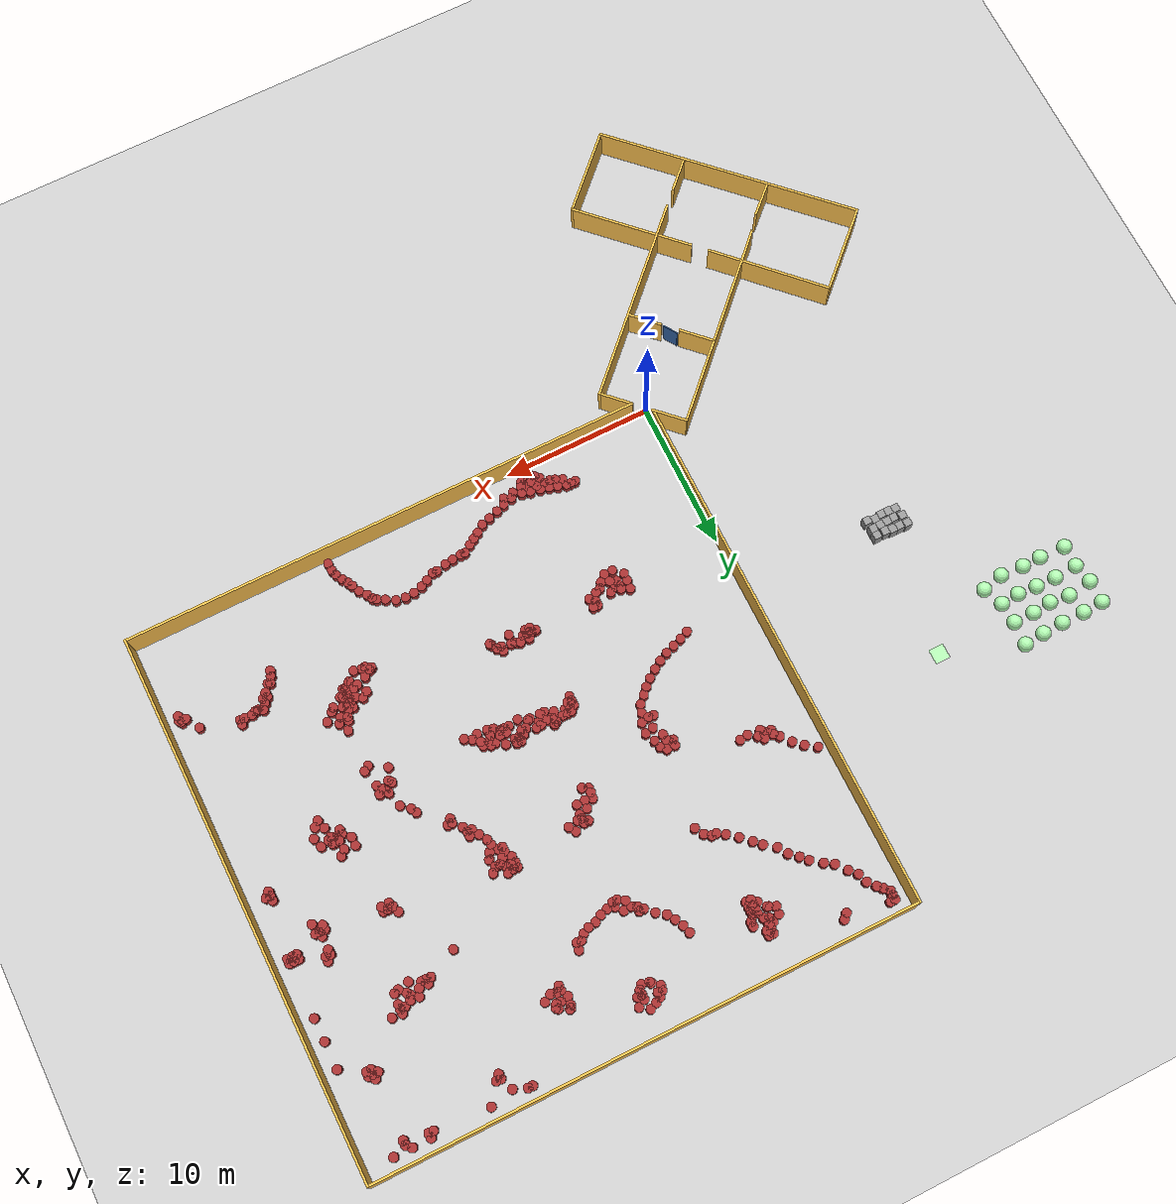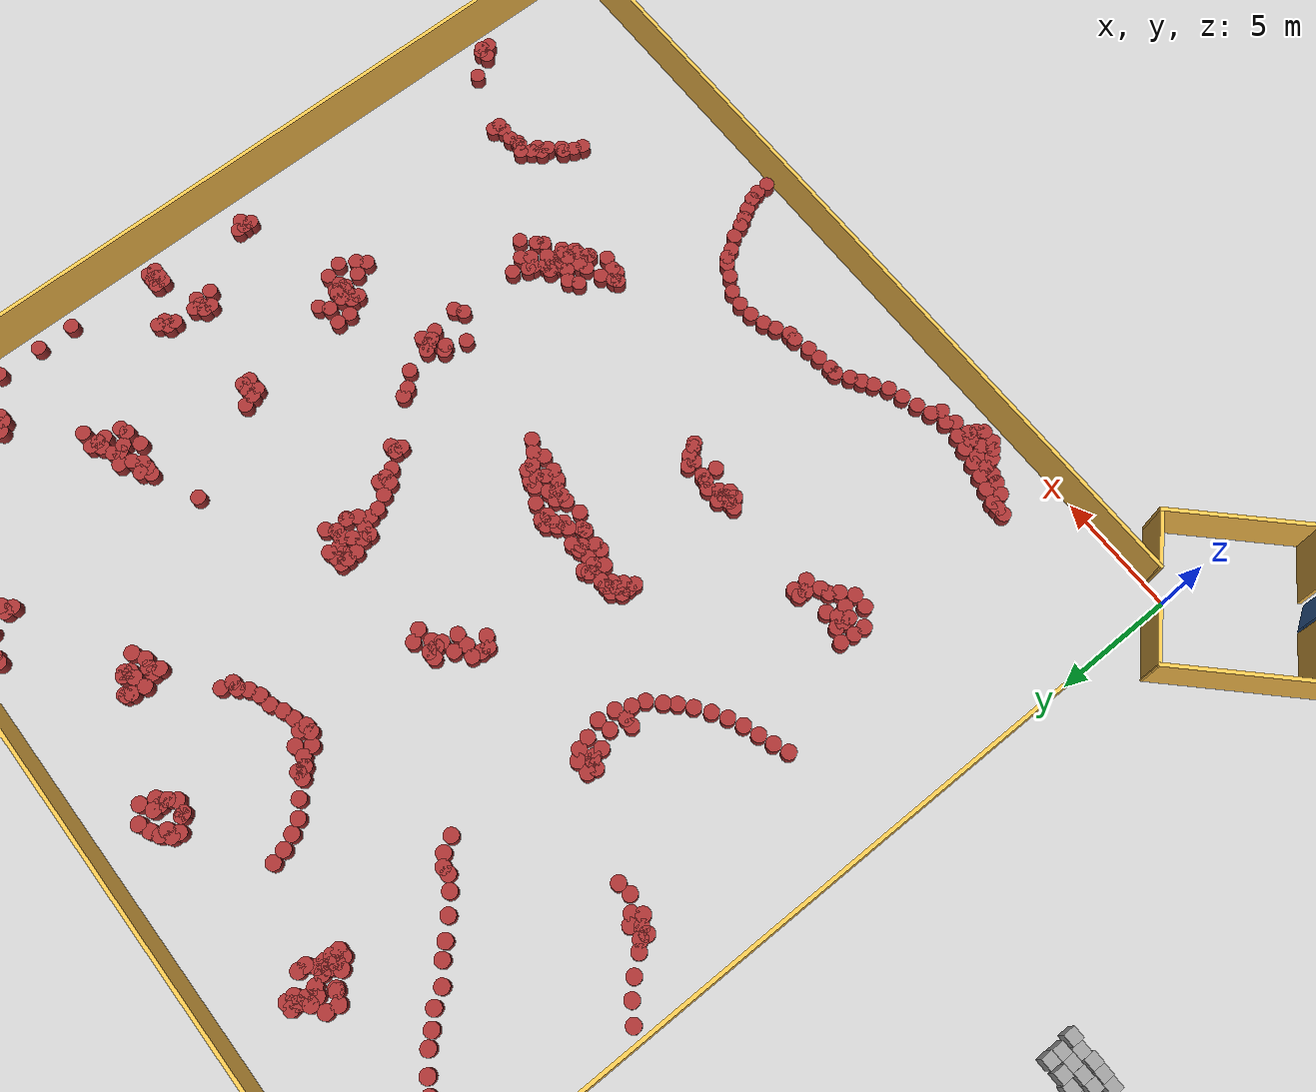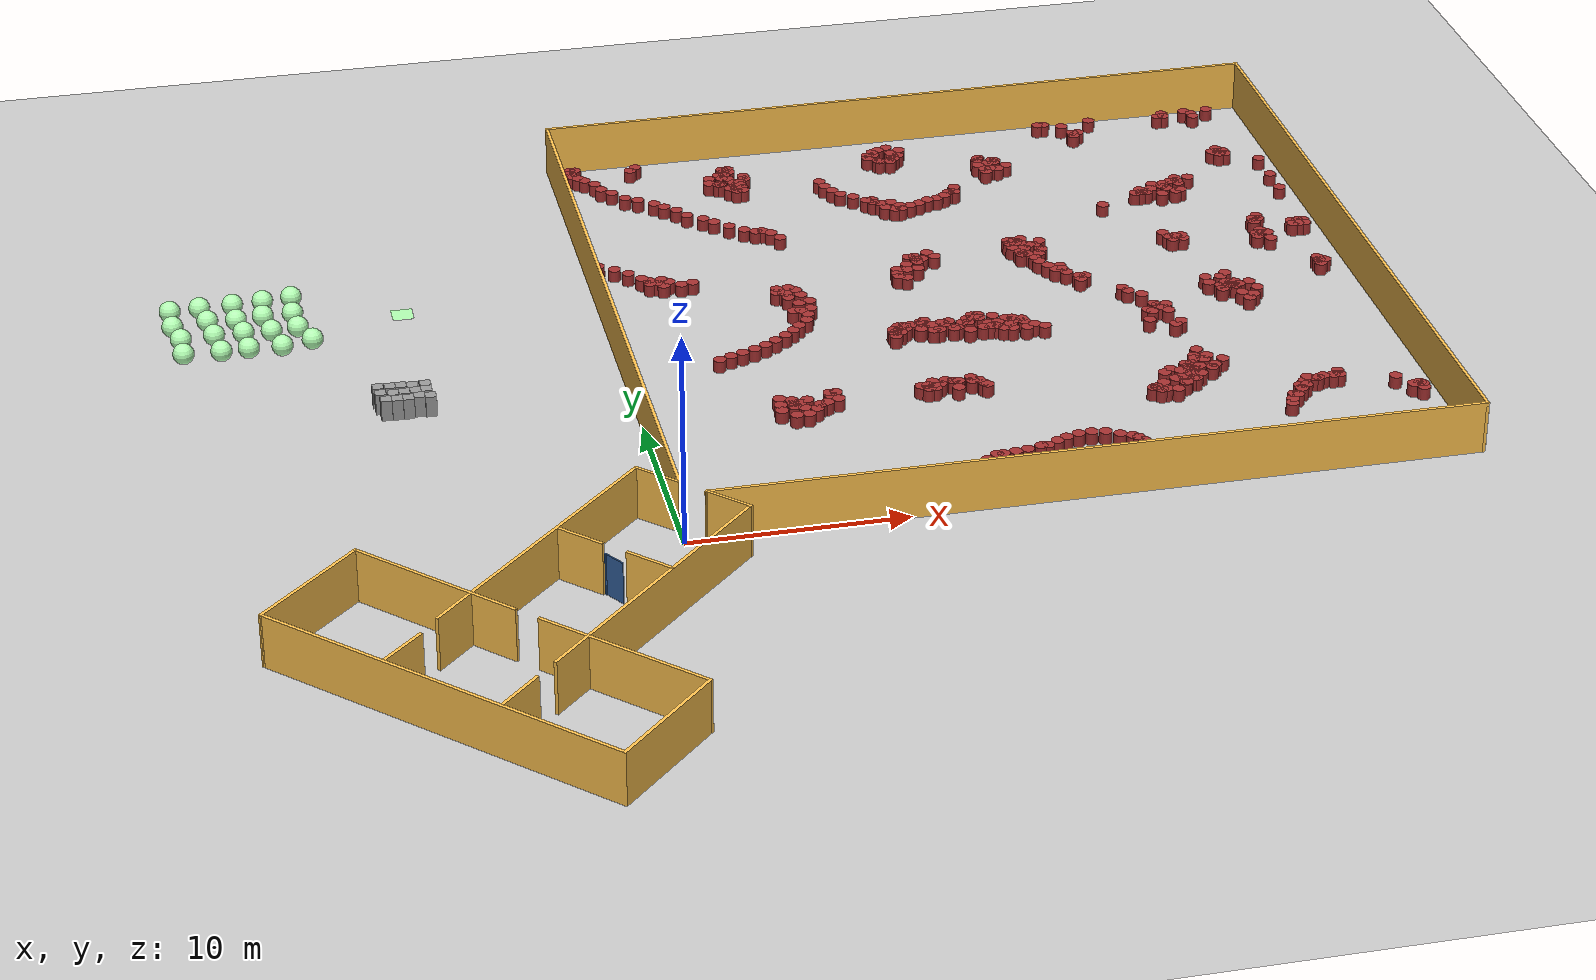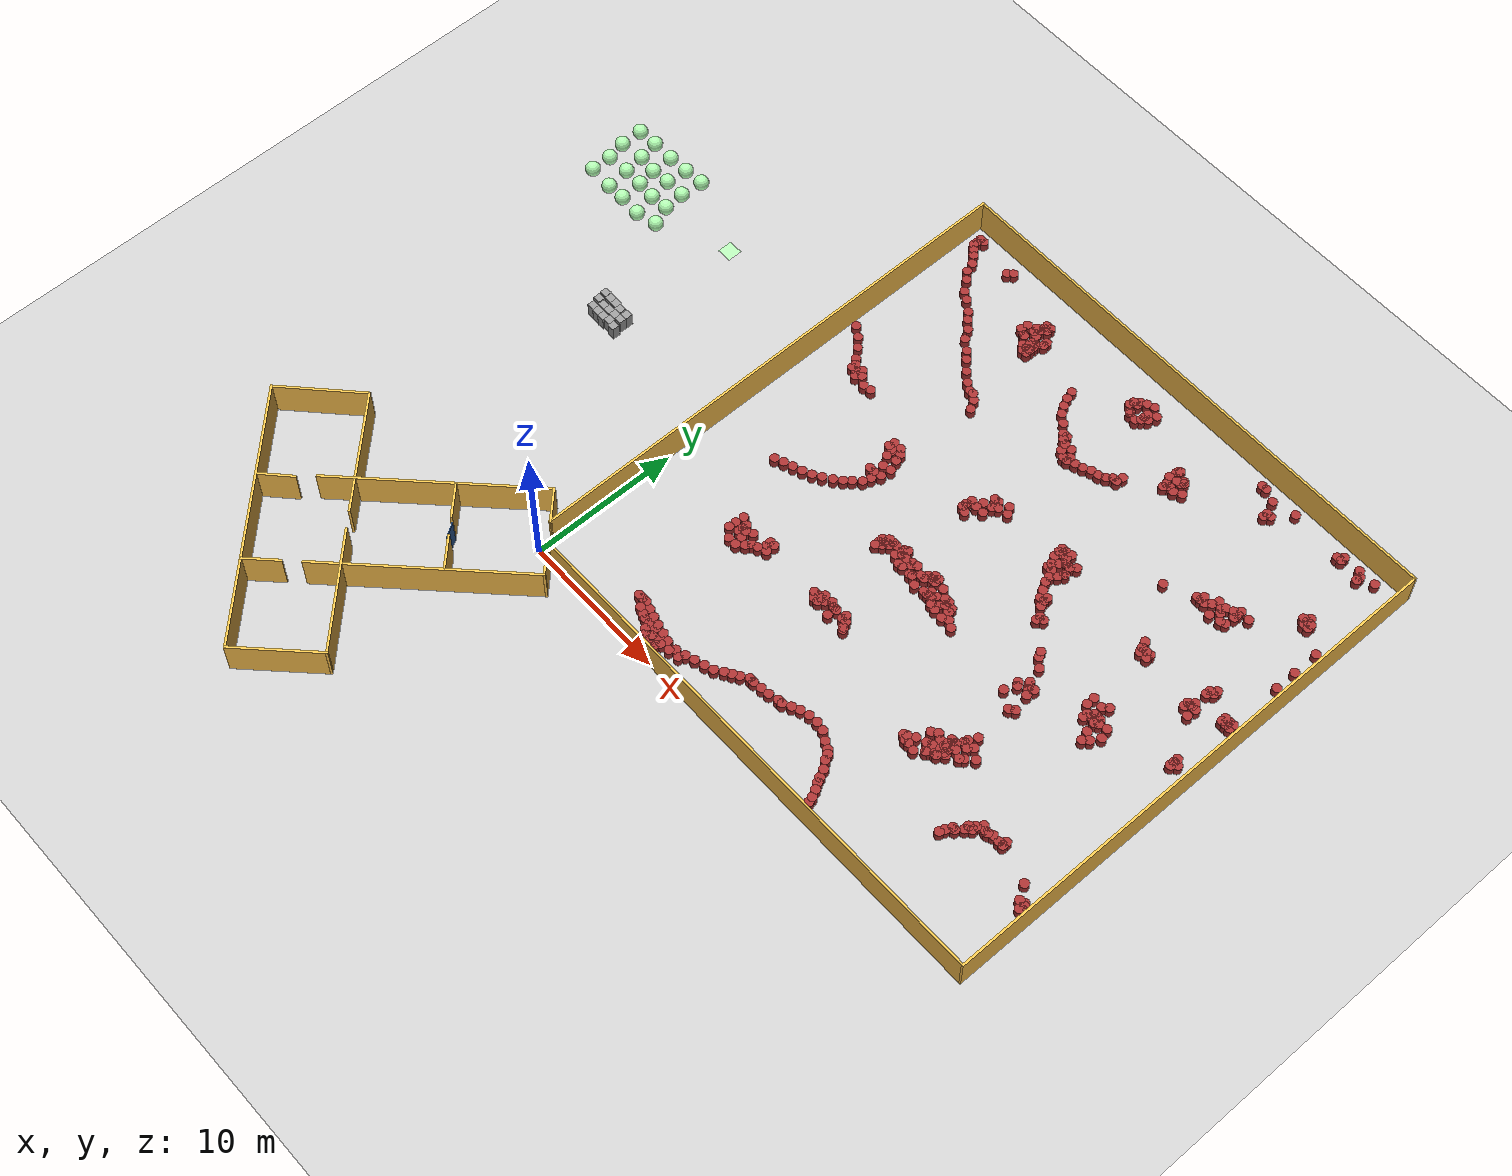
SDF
<sdf version="1.6">
 <world name="default">
  <light name="sun" type="directional">
   <pose>0 0 10 0 -0 0</pose>
   <diffuse>0.8 0.8 0.8 1</diffuse>
   <specular>0.1 0.1 0.1 1</specular>
   <attenuation>
    <range>1000</range>
    <constant>0.9</constant>
    <linear>0.01</linear>
    <quadratic>0.001</quadratic>
   </attenuation>
   <direction>-0.5 0.5 -1</direction>
   <spot><inner_angle>0</inner_angle><outer_angle>0</outer_angle><falloff>0</falloff></spot>
  </light>
  <model name="bouncy_ball">
   <link name="link_0">
    <inertial>
     <mass>0.1</mass>
     <inertia><ixx>1</ixx><ixy>0</ixy><ixz>0</ixz><iyy>1</iyy><iyz>0</iyz><izz>1</izz></inertia>
    </inertial>
    <visual name="visual">
     <geometry><sphere><radius>0.5</radius></sphere></geometry>
     <material>
      <lighting>1</lighting>
      <script><uri>file://media/materials/scripts/gazebo.material</uri><name>Gazebo/Grey</name></script>
      <shader type="pixel"><normal_map>__default__</normal_map></shader>
      <ambient>0 1 0 0</ambient>
      <diffuse>0.7 1 0.7 1</diffuse>
      <specular>0.01 0.01 0.01 1</specular>
      <emissive>0 0 0 1</emissive>
     </material>
    </visual>
    <collision name="collision">
     <geometry><sphere><radius>0.5</radius></sphere></geometry>
     <surface>
      <friction><ode><mu>0</mu><mu2>0</mu2></ode></friction>
      <contact>
       <ode><kp>500000</kp><kd>0</kd><max_vel>1e+26</max_vel><min_depth>0</min_depth></ode>
       <bullet>
        <kp>500000</kp>
        <kd>0</kd>
        <split_impulse>1</split_impulse>
        <split_impulse_penetration_threshold>-0.01</split_impulse_penetration_threshold>
       </bullet>
      </contact>
     </surface>
    </collision>
   </link>
   <static>0</static>
   <pose>-19.8053 24.5819 0.499998 0 -0 0</pose>
  </model>
  <model name="bouncy_ball_clone">
   <link name="link_0">
    <inertial>
     <mass>0.1</mass>
     <inertia><ixx>1</ixx><ixy>0</ixy><ixz>0</ixz><iyy>1</iyy><iyz>0</iyz><izz>1</izz></inertia>
    </inertial>
    <visual name="visual">
     <geometry><sphere><radius>0.5</radius></sphere></geometry>
     <material>
      <lighting>1</lighting>
      <script><uri>file://media/materials/scripts/gazebo.material</uri><name>Gazebo/Grey</name></script>
      <shader type="pixel"><normal_map>__default__</normal_map></shader>
      <ambient>0 1 0 0</ambient>
      <diffuse>0.7 1 0.7 1</diffuse>
      <specular>0.01 0.01 0.01 1</specular>
      <emissive>0 0 0 1</emissive>
     </material>
    </visual>
    <collision name="collision">
     <geometry><sphere><radius>0.5</radius></sphere></geometry>
     <surface>
      <friction><ode><mu>0</mu><mu2>0</mu2></ode></friction>
      <contact>
       <ode><kp>500000</kp><kd>0</kd><max_vel>1e+26</max_vel><min_depth>0</min_depth></ode>
       <bullet>
        <kp>500000</kp>
        <kd>0</kd>
        <split_impulse>1</split_impulse>
        <split_impulse_penetration_threshold>-0.01</split_impulse_penetration_threshold>
       </bullet>
      </contact>
     </surface>
    </collision>
   </link>
   <static>0</static>
   <pose>-18.4197 24.647 0.499998 0 -0 0</pose>
  </model>
  <model name="bouncy_ball_clone_0">
   <link name="link_0">
    <inertial>
     <mass>0.1</mass>
     <inertia><ixx>1</ixx><ixy>0</ixy><ixz>0</ixz><iyy>1</iyy><iyz>0</iyz><izz>1</izz></inertia>
    </inertial>
    <visual name="visual">
     <geometry><sphere><radius>0.5</radius></sphere></geometry>
     <material>
      <lighting>1</lighting>
      <script><uri>file://media/materials/scripts/gazebo.material</uri><name>Gazebo/Grey</name></script>
      <shader type="pixel"><normal_map>__default__</normal_map></shader>
      <ambient>0 1 0 0</ambient>
      <diffuse>0.7 1 0.7 1</diffuse>
      <specular>0.01 0.01 0.01 1</specular>
      <emissive>0 0 0 1</emissive>
     </material>
    </visual>
    <collision name="collision">
     <geometry><sphere><radius>0.5</radius></sphere></geometry>
     <surface>
      <friction><ode><mu>0</mu><mu2>0</mu2></ode></friction>
      <contact>
       <ode><kp>500000</kp><kd>0</kd><max_vel>1e+26</max_vel><min_depth>0</min_depth></ode>
       <bullet>
        <kp>500000</kp>
        <kd>0</kd>
        <split_impulse>1</split_impulse>
        <split_impulse_penetration_threshold>-0.01</split_impulse_penetration_threshold>
       </bullet>
      </contact>
     </surface>
    </collision>
   </link>
   <static>0</static>
   <pose>-16.8768 24.6481 0.499998 0 -0 0</pose>
  </model>
  <model name="bouncy_ball_clone_1">
   <link name="link_0">
    <inertial>
     <mass>0.1</mass>
     <inertia><ixx>1</ixx><ixy>0</ixy><ixz>0</ixz><iyy>1</iyy><iyz>0</iyz><izz>1</izz></inertia>
    </inertial>
    <visual name="visual">
     <geometry><sphere><radius>0.5</radius></sphere></geometry>
     <material>
      <lighting>1</lighting>
      <script><uri>file://media/materials/scripts/gazebo.material</uri><name>Gazebo/Grey</name></script>
      <shader type="pixel"><normal_map>__default__</normal_map></shader>
      <ambient>0 1 0 0</ambient>
      <diffuse>0.7 1 0.7 1</diffuse>
      <specular>0.01 0.01 0.01 1</specular>
      <emissive>0 0 0 1</emissive>
     </material>
    </visual>
    <collision name="collision">
     <geometry><sphere><radius>0.5</radius></sphere></geometry>
     <surface>
      <friction><ode><mu>0</mu><mu2>0</mu2></ode></friction>
      <contact>
       <ode><kp>500000</kp><kd>0</kd><max_vel>1e+26</max_vel><min_depth>0</min_depth></ode>
       <bullet>
        <kp>500000</kp>
        <kd>0</kd>
        <split_impulse>1</split_impulse>
        <split_impulse_penetration_threshold>-0.01</split_impulse_penetration_threshold>
       </bullet>
      </contact>
     </surface>
    </collision>
   </link>
   <static>0</static>
   <pose>-15.4597 24.7144 0.499998 0 -0 0</pose>
  </model>
  <model name="bouncy_ball_clone_2">
   <link name="link_0">
    <inertial>
     <mass>0.1</mass>
     <inertia><ixx>1</ixx><ixy>0</ixy><ixz>0</ixz><iyy>1</iyy><iyz>0</iyz><izz>1</izz></inertia>
    </inertial>
    <visual name="visual">
     <geometry><sphere><radius>0.5</radius></sphere></geometry>
     <material>
      <lighting>1</lighting>
      <script><uri>file://media/materials/scripts/gazebo.material</uri><name>Gazebo/Grey</name></script>
      <shader type="pixel"><normal_map>__default__</normal_map></shader>
      <ambient>0 1 0 0</ambient>
      <diffuse>0.7 1 0.7 1</diffuse>
      <specular>0.01 0.01 0.01 1</specular>
      <emissive>0 0 0 1</emissive>
     </material>
    </visual>
    <collision name="collision">
     <geometry><sphere><radius>0.5</radius></sphere></geometry>
     <surface>
      <friction><ode><mu>0</mu><mu2>0</mu2></ode></friction>
      <contact>
       <ode><kp>500000</kp><kd>0</kd><max_vel>1e+26</max_vel><min_depth>0</min_depth></ode>
       <bullet>
        <kp>500000</kp>
        <kd>0</kd>
        <split_impulse>1</split_impulse>
        <split_impulse_penetration_threshold>-0.01</split_impulse_penetration_threshold>
       </bullet>
      </contact>
     </surface>
    </collision>
   </link>
   <static>0</static>
   <pose>-14.0987 24.8301 0.499998 0 -0 0</pose>
  </model>
  <model name="bouncy_ball_clone_3">
   <link name="link_0">
    <inertial>
     <mass>0.1</mass>
     <inertia><ixx>1</ixx><ixy>0</ixy><ixz>0</ixz><iyy>1</iyy><iyz>0</iyz><izz>1</izz></inertia>
    </inertial>
    <visual name="visual">
     <geometry><sphere><radius>0.5</radius></sphere></geometry>
     <material>
      <lighting>1</lighting>
      <script><uri>file://media/materials/scripts/gazebo.material</uri><name>Gazebo/Grey</name></script>
      <shader type="pixel"><normal_map>__default__</normal_map></shader>
      <ambient>0 1 0 0</ambient>
      <diffuse>0.7 1 0.7 1</diffuse>
      <specular>0.01 0.01 0.01 1</specular>
      <emissive>0 0 0 1</emissive>
     </material>
    </visual>
    <collision name="collision">
     <geometry><sphere><radius>0.5</radius></sphere></geometry>
     <surface>
      <friction><ode><mu>0</mu><mu2>0</mu2></ode></friction>
      <contact>
       <ode><kp>500000</kp><kd>0</kd><max_vel>1e+26</max_vel><min_depth>0</min_depth></ode>
       <bullet>
        <kp>500000</kp>
        <kd>0</kd>
        <split_impulse>1</split_impulse>
        <split_impulse_penetration_threshold>-0.01</split_impulse_penetration_threshold>
       </bullet>
      </contact>
     </surface>
    </collision>
   </link>
   <static>0</static>
   <pose>-19.8031 23.0705 0.499998 0 -0 0</pose>
  </model>
  <model name="bouncy_ball_clone_4">
   <link name="link_0">
    <inertial>
     <mass>0.1</mass>
     <inertia><ixx>1</ixx><ixy>0</ixy><ixz>0</ixz><iyy>1</iyy><iyz>0</iyz><izz>1</izz></inertia>
    </inertial>
    <visual name="visual">
     <geometry><sphere><radius>0.5</radius></sphere></geometry>
     <material>
      <lighting>1</lighting>
      <script><uri>file://media/materials/scripts/gazebo.material</uri><name>Gazebo/Grey</name></script>
      <shader type="pixel"><normal_map>__default__</normal_map></shader>
      <ambient>0 1 0 0</ambient>
      <diffuse>0.7 1 0.7 1</diffuse>
      <specular>0.01 0.01 0.01 1</specular>
      <emissive>0 0 0 1</emissive>
     </material>
    </visual>
    <collision name="collision">
     <geometry><sphere><radius>0.5</radius></sphere></geometry>
     <surface>
      <friction><ode><mu>0</mu><mu2>0</mu2></ode></friction>
      <contact>
       <ode><kp>500000</kp><kd>0</kd><max_vel>1e+26</max_vel><min_depth>0</min_depth></ode>
       <bullet>
        <kp>500000</kp>
        <kd>0</kd>
        <split_impulse>1</split_impulse>
        <split_impulse_penetration_threshold>-0.01</split_impulse_penetration_threshold>
       </bullet>
      </contact>
     </surface>
    </collision>
   </link>
   <static>0</static>
   <pose>-18.1657 23.2921 0.499998 0 -0 0</pose>
  </model>
  <model name="bouncy_ball_clone_5">
   <link name="link_0">
    <inertial>
     <mass>0.1</mass>
     <inertia><ixx>1</ixx><ixy>0</ixy><ixz>0</ixz><iyy>1</iyy><iyz>0</iyz><izz>1</izz></inertia>
    </inertial>
    <visual name="visual">
     <geometry><sphere><radius>0.5</radius></sphere></geometry>
     <material>
      <lighting>1</lighting>
      <script><uri>file://media/materials/scripts/gazebo.material</uri><name>Gazebo/Grey</name></script>
      <shader type="pixel"><normal_map>__default__</normal_map></shader>
      <ambient>0 1 0 0</ambient>
      <diffuse>0.7 1 0.7 1</diffuse>
      <specular>0.01 0.01 0.01 1</specular>
      <emissive>0 0 0 1</emissive>
     </material>
    </visual>
    <collision name="collision">
     <geometry><sphere><radius>0.5</radius></sphere></geometry>
     <surface>
      <friction><ode><mu>0</mu><mu2>0</mu2></ode></friction>
      <contact>
       <ode><kp>500000</kp><kd>0</kd><max_vel>1e+26</max_vel><min_depth>0</min_depth></ode>
       <bullet>
        <kp>500000</kp>
        <kd>0</kd>
        <split_impulse>1</split_impulse>
        <split_impulse_penetration_threshold>-0.01</split_impulse_penetration_threshold>
       </bullet>
      </contact>
     </surface>
    </collision>
   </link>
   <static>0</static>
   <pose>-16.8429 23.1367 0.499998 0 -0 0</pose>
  </model>
  <model name="bouncy_ball_clone_6">
   <link name="link_0">
    <inertial>
     <mass>0.1</mass>
     <inertia><ixx>1</ixx><ixy>0</ixy><ixz>0</ixz><iyy>1</iyy><iyz>0</iyz><izz>1</izz></inertia>
    </inertial>
    <visual name="visual">
     <geometry><sphere><radius>0.5</radius></sphere></geometry>
     <material>
      <lighting>1</lighting>
      <script><uri>file://media/materials/scripts/gazebo.material</uri><name>Gazebo/Grey</name></script>
      <shader type="pixel"><normal_map>__default__</normal_map></shader>
      <ambient>0 1 0 0</ambient>
      <diffuse>0.7 1 0.7 1</diffuse>
      <specular>0.01 0.01 0.01 1</specular>
      <emissive>0 0 0 1</emissive>
     </material>
    </visual>
    <collision name="collision">
     <geometry><sphere><radius>0.5</radius></sphere></geometry>
     <surface>
      <friction><ode><mu>0</mu><mu2>0</mu2></ode></friction>
      <contact>
       <ode><kp>500000</kp><kd>0</kd><max_vel>1e+26</max_vel><min_depth>0</min_depth></ode>
       <bullet>
        <kp>500000</kp>
        <kd>0</kd>
        <split_impulse>1</split_impulse>
        <split_impulse_penetration_threshold>-0.01</split_impulse_penetration_threshold>
       </bullet>
      </contact>
     </surface>
    </collision>
   </link>
   <static>0</static>
   <pose>-15.5838 23.2647 0.499998 0 -0 0</pose>
  </model>
  <model name="bouncy_ball_clone_7">
   <link name="link_0">
    <inertial>
     <mass>0.1</mass>
     <inertia><ixx>1</ixx><ixy>0</ixy><ixz>0</ixz><iyy>1</iyy><iyz>0</iyz><izz>1</izz></inertia>
    </inertial>
    <visual name="visual">
     <geometry><sphere><radius>0.5</radius></sphere></geometry>
     <material>
      <lighting>1</lighting>
      <script><uri>file://media/materials/scripts/gazebo.material</uri><name>Gazebo/Grey</name></script>
      <shader type="pixel"><normal_map>__default__</normal_map></shader>
      <ambient>0 1 0 0</ambient>
      <diffuse>0.7 1 0.7 1</diffuse>
      <specular>0.01 0.01 0.01 1</specular>
      <emissive>0 0 0 1</emissive>
     </material>
    </visual>
    <collision name="collision">
     <geometry><sphere><radius>0.5</radius></sphere></geometry>
     <surface>
      <friction><ode><mu>0</mu><mu2>0</mu2></ode></friction>
      <contact>
       <ode><kp>500000</kp><kd>0</kd><max_vel>1e+26</max_vel><min_depth>0</min_depth></ode>
       <bullet>
        <kp>500000</kp>
        <kd>0</kd>
        <split_impulse>1</split_impulse>
        <split_impulse_penetration_threshold>-0.01</split_impulse_penetration_threshold>
       </bullet>
      </contact>
     </surface>
    </collision>
   </link>
   <static>0</static>
   <pose>-14.1979 23.267 0.499998 0 -0 0</pose>
  </model>
  <model name="bouncy_ball_clone_8">
   <link name="link_0">
    <inertial>
     <mass>0.1</mass>
     <inertia><ixx>1</ixx><ixy>0</ixy><ixz>0</ixz><iyy>1</iyy><iyz>0</iyz><izz>1</izz></inertia>
    </inertial>
    <visual name="visual">
     <geometry><sphere><radius>0.5</radius></sphere></geometry>
     <material>
      <lighting>1</lighting>
      <script><uri>file://media/materials/scripts/gazebo.material</uri><name>Gazebo/Grey</name></script>
      <shader type="pixel"><normal_map>__default__</normal_map></shader>
      <ambient>0 1 0 0</ambient>
      <diffuse>0.7 1 0.7 1</diffuse>
      <specular>0.01 0.01 0.01 1</specular>
      <emissive>0 0 0 1</emissive>
     </material>
    </visual>
    <collision name="collision">
     <geometry><sphere><radius>0.5</radius></sphere></geometry>
     <surface>
      <friction><ode><mu>0</mu><mu2>0</mu2></ode></friction>
      <contact>
       <ode><kp>500000</kp><kd>0</kd><max_vel>1e+26</max_vel><min_depth>0</min_depth></ode>
       <bullet>
        <kp>500000</kp>
        <kd>0</kd>
        <split_impulse>1</split_impulse>
        <split_impulse_penetration_threshold>-0.01</split_impulse_penetration_threshold>
       </bullet>
      </contact>
     </surface>
    </collision>
   </link>
   <static>0</static>
   <pose>-19.5178 21.7785 0.499998 0 -0 0</pose>
  </model>
  <model name="bouncy_ball_clone_9">
   <link name="link_0">
    <inertial>
     <mass>0.1</mass>
     <inertia><ixx>1</ixx><ixy>0</ixy><ixz>0</ixz><iyy>1</iyy><iyz>0</iyz><izz>1</izz></inertia>
    </inertial>
    <visual name="visual">
     <geometry><sphere><radius>0.5</radius></sphere></geometry>
     <material>
      <lighting>1</lighting>
      <script><uri>file://media/materials/scripts/gazebo.material</uri><name>Gazebo/Grey</name></script>
      <shader type="pixel"><normal_map>__default__</normal_map></shader>
      <ambient>0 1 0 0</ambient>
      <diffuse>0.7 1 0.7 1</diffuse>
      <specular>0.01 0.01 0.01 1</specular>
      <emissive>0 0 0 1</emissive>
     </material>
    </visual>
    <collision name="collision">
     <geometry><sphere><radius>0.5</radius></sphere></geometry>
     <surface>
      <friction><ode><mu>0</mu><mu2>0</mu2></ode></friction>
      <contact>
       <ode><kp>500000</kp><kd>0</kd><max_vel>1e+26</max_vel><min_depth>0</min_depth></ode>
       <bullet>
        <kp>500000</kp>
        <kd>0</kd>
        <split_impulse>1</split_impulse>
        <split_impulse_penetration_threshold>-0.01</split_impulse_penetration_threshold>
       </bullet>
      </contact>
     </surface>
    </collision>
   </link>
   <static>0</static>
   <pose>-17.975 21.8756 0.499998 0 -0 0</pose>
  </model>
  <model name="bouncy_ball_clone_10">
   <link name="link_0">
    <inertial>
     <mass>0.1</mass>
     <inertia><ixx>1</ixx><ixy>0</ixy><ixz>0</ixz><iyy>1</iyy><iyz>0</iyz><izz>1</izz></inertia>
    </inertial>
    <visual name="visual">
     <geometry><sphere><radius>0.5</radius></sphere></geometry>
     <material>
      <lighting>1</lighting>
      <script><uri>file://media/materials/scripts/gazebo.material</uri><name>Gazebo/Grey</name></script>
      <shader type="pixel"><normal_map>__default__</normal_map></shader>
      <ambient>0 1 0 0</ambient>
      <diffuse>0.7 1 0.7 1</diffuse>
      <specular>0.01 0.01 0.01 1</specular>
      <emissive>0 0 0 1</emissive>
     </material>
    </visual>
    <collision name="collision">
     <geometry><sphere><radius>0.5</radius></sphere></geometry>
     <surface>
      <friction><ode><mu>0</mu><mu2>0</mu2></ode></friction>
      <contact>
       <ode><kp>500000</kp><kd>0</kd><max_vel>1e+26</max_vel><min_depth>0</min_depth></ode>
       <bullet>
        <kp>500000</kp>
        <kd>0</kd>
        <split_impulse>1</split_impulse>
        <split_impulse_penetration_threshold>-0.01</split_impulse_penetration_threshold>
       </bullet>
      </contact>
     </surface>
    </collision>
   </link>
   <static>0</static>
   <pose>-16.6209 21.847 0.499998 0 -0 0</pose>
  </model>
  <model name="bouncy_ball_clone_11">
   <link name="link_0">
    <inertial>
     <mass>0.1</mass>
     <inertia><ixx>1</ixx><ixy>0</ixy><ixz>0</ixz><iyy>1</iyy><iyz>0</iyz><izz>1</izz></inertia>
    </inertial>
    <visual name="visual">
     <geometry><sphere><radius>0.5</radius></sphere></geometry>
     <material>
      <lighting>1</lighting>
      <script><uri>file://media/materials/scripts/gazebo.material</uri><name>Gazebo/Grey</name></script>
      <shader type="pixel"><normal_map>__default__</normal_map></shader>
      <ambient>0 1 0 0</ambient>
      <diffuse>0.7 1 0.7 1</diffuse>
      <specular>0.01 0.01 0.01 1</specular>
      <emissive>0 0 0 1</emissive>
     </material>
    </visual>
    <collision name="collision">
     <geometry><sphere><radius>0.5</radius></sphere></geometry>
     <surface>
      <friction><ode><mu>0</mu><mu2>0</mu2></ode></friction>
      <contact>
       <ode><kp>500000</kp><kd>0</kd><max_vel>1e+26</max_vel><min_depth>0</min_depth></ode>
       <bullet>
        <kp>500000</kp>
        <kd>0</kd>
        <split_impulse>1</split_impulse>
        <split_impulse_penetration_threshold>-0.01</split_impulse_penetration_threshold>
       </bullet>
      </contact>
     </surface>
    </collision>
   </link>
   <static>0</static>
   <pose>-15.3297 21.7545 0.499998 0 -0 0</pose>
  </model>
  <model name="bouncy_ball_clone_12">
   <link name="link_0">
    <inertial>
     <mass>0.1</mass>
     <inertia><ixx>1</ixx><ixy>0</ixy><ixz>0</ixz><iyy>1</iyy><iyz>0</iyz><izz>1</izz></inertia>
    </inertial>
    <visual name="visual">
     <geometry><sphere><radius>0.5</radius></sphere></geometry>
     <material>
      <lighting>1</lighting>
      <script><uri>file://media/materials/scripts/gazebo.material</uri><name>Gazebo/Grey</name></script>
      <shader type="pixel"><normal_map>__default__</normal_map></shader>
      <ambient>0 1 0 0</ambient>
      <diffuse>0.7 1 0.7 1</diffuse>
      <specular>0.01 0.01 0.01 1</specular>
      <emissive>0 0 0 1</emissive>
     </material>
    </visual>
    <collision name="collision">
     <geometry><sphere><radius>0.5</radius></sphere></geometry>
     <surface>
      <friction><ode><mu>0</mu><mu2>0</mu2></ode></friction>
      <contact>
       <ode><kp>500000</kp><kd>0</kd><max_vel>1e+26</max_vel><min_depth>0</min_depth></ode>
       <bullet>
        <kp>500000</kp>
        <kd>0</kd>
        <split_impulse>1</split_impulse>
        <split_impulse_penetration_threshold>-0.01</split_impulse_penetration_threshold>
       </bullet>
      </contact>
     </surface>
    </collision>
   </link>
   <static>0</static>
   <pose>-14.0954 21.8631 0.499998 0 -0 0</pose>
  </model>
  <model name="bouncy_ball_clone_13">
   <link name="link_0">
    <inertial>
     <mass>0.1</mass>
     <inertia><ixx>1</ixx><ixy>0</ixy><ixz>0</ixz><iyy>1</iyy><iyz>0</iyz><izz>1</izz></inertia>
    </inertial>
    <visual name="visual">
     <geometry><sphere><radius>0.5</radius></sphere></geometry>
     <material>
      <lighting>1</lighting>
      <script><uri>file://media/materials/scripts/gazebo.material</uri><name>Gazebo/Grey</name></script>
      <shader type="pixel"><normal_map>__default__</normal_map></shader>
      <ambient>0 1 0 0</ambient>
      <diffuse>0.7 1 0.7 1</diffuse>
      <specular>0.01 0.01 0.01 1</specular>
      <emissive>0 0 0 1</emissive>
     </material>
    </visual>
    <collision name="collision">
     <geometry><sphere><radius>0.5</radius></sphere></geometry>
     <surface>
      <friction><ode><mu>0</mu><mu2>0</mu2></ode></friction>
      <contact>
       <ode><kp>500000</kp><kd>0</kd><max_vel>1e+26</max_vel><min_depth>0</min_depth></ode>
       <bullet>
        <kp>500000</kp>
        <kd>0</kd>
        <split_impulse>1</split_impulse>
        <split_impulse_penetration_threshold>-0.01</split_impulse_penetration_threshold>
       </bullet>
      </contact>
     </surface>
    </collision>
   </link>
   <static>0</static>
   <pose>-19.5151 20.363 0.499998 0 -0 0</pose>
  </model>
  <model name="bouncy_ball_clone_14">
   <link name="link_0">
    <inertial>
     <mass>0.1</mass>
     <inertia><ixx>1</ixx><ixy>0</ixy><ixz>0</ixz><iyy>1</iyy><iyz>0</iyz><izz>1</izz></inertia>
    </inertial>
    <visual name="visual">
     <geometry><sphere><radius>0.5</radius></sphere></geometry>
     <material>
      <lighting>1</lighting>
      <script><uri>file://media/materials/scripts/gazebo.material</uri><name>Gazebo/Grey</name></script>
      <shader type="pixel"><normal_map>__default__</normal_map></shader>
      <ambient>0 1 0 0</ambient>
      <diffuse>0.7 1 0.7 1</diffuse>
      <specular>0.01 0.01 0.01 1</specular>
      <emissive>0 0 0 1</emissive>
     </material>
    </visual>
    <collision name="collision">
     <geometry><sphere><radius>0.5</radius></sphere></geometry>
     <surface>
      <friction><ode><mu>0</mu><mu2>0</mu2></ode></friction>
      <contact>
       <ode><kp>500000</kp><kd>0</kd><max_vel>1e+26</max_vel><min_depth>0</min_depth></ode>
       <bullet>
        <kp>500000</kp>
        <kd>0</kd>
        <split_impulse>1</split_impulse>
        <split_impulse_penetration_threshold>-0.01</split_impulse_penetration_threshold>
       </bullet>
      </contact>
     </surface>
    </collision>
   </link>
   <static>0</static>
   <pose>-17.7829 20.2705 0.499998 0 -0 0</pose>
  </model>
  <model name="bouncy_ball_clone_15">
   <link name="link_0">
    <inertial>
     <mass>0.1</mass>
     <inertia><ixx>1</ixx><ixy>0</ixy><ixz>0</ixz><iyy>1</iyy><iyz>0</iyz><izz>1</izz></inertia>
    </inertial>
    <visual name="visual">
     <geometry><sphere><radius>0.5</radius></sphere></geometry>
     <material>
      <lighting>1</lighting>
      <script><uri>file://media/materials/scripts/gazebo.material</uri><name>Gazebo/Grey</name></script>
      <shader type="pixel"><normal_map>__default__</normal_map></shader>
      <ambient>0 1 0 0</ambient>
      <diffuse>0.7 1 0.7 1</diffuse>
      <specular>0.01 0.01 0.01 1</specular>
      <emissive>0 0 0 1</emissive>
     </material>
    </visual>
    <collision name="collision">
     <geometry><sphere><radius>0.5</radius></sphere></geometry>
     <surface>
      <friction><ode><mu>0</mu><mu2>0</mu2></ode></friction>
      <contact>
       <ode><kp>500000</kp><kd>0</kd><max_vel>1e+26</max_vel><min_depth>0</min_depth></ode>
       <bullet>
        <kp>500000</kp>
        <kd>0</kd>
        <split_impulse>1</split_impulse>
        <split_impulse_penetration_threshold>-0.01</split_impulse_penetration_threshold>
       </bullet>
      </contact>
     </surface>
    </collision>
   </link>
   <static>0</static>
   <pose>-16.5233 20.3036 0.499998 0 -0 0</pose>
  </model>
  <model name="bouncy_ball_clone_16">
   <link name="link_0">
    <inertial>
     <mass>0.1</mass>
     <inertia><ixx>1</ixx><ixy>0</ixy><ixz>0</ixz><iyy>1</iyy><iyz>0</iyz><izz>1</izz></inertia>
    </inertial>
    <visual name="visual">
     <geometry><sphere><radius>0.5</radius></sphere></geometry>
     <material>
      <lighting>1</lighting>
      <script><uri>file://media/materials/scripts/gazebo.material</uri><name>Gazebo/Grey</name></script>
      <shader type="pixel"><normal_map>__default__</normal_map></shader>
      <ambient>0 1 0 0</ambient>
      <diffuse>0.7 1 0.7 1</diffuse>
      <specular>0.01 0.01 0.01 1</specular>
      <emissive>0 0 0 1</emissive>
     </material>
    </visual>
    <collision name="collision">
     <geometry><sphere><radius>0.5</radius></sphere></geometry>
     <surface>
      <friction><ode><mu>0</mu><mu2>0</mu2></ode></friction>
      <contact>
       <ode><kp>500000</kp><kd>0</kd><max_vel>1e+26</max_vel><min_depth>0</min_depth></ode>
       <bullet>
        <kp>500000</kp>
        <kd>0</kd>
        <split_impulse>1</split_impulse>
        <split_impulse_penetration_threshold>-0.01</split_impulse_penetration_threshold>
       </bullet>
      </contact>
     </surface>
    </collision>
   </link>
   <static>0</static>
   <pose>-14.9803 20.2111 0.499998 0 -0 0</pose>
  </model>
  <model name="bouncy_ball_clone_17">
   <link name="link_0">
    <inertial>
     <mass>0.1</mass>
     <inertia><ixx>1</ixx><ixy>0</ixy><ixz>0</ixz><iyy>1</iyy><iyz>0</iyz><izz>1</izz></inertia>
    </inertial>
    <visual name="visual">
     <geometry><sphere><radius>0.5</radius></sphere></geometry>
     <material>
      <lighting>1</lighting>
      <script><uri>file://media/materials/scripts/gazebo.material</uri><name>Gazebo/Grey</name></script>
      <shader type="pixel"><normal_map>__default__</normal_map></shader>
      <ambient>0 1 0 0</ambient>
      <diffuse>0.7 1 0.7 1</diffuse>
      <specular>0.01 0.01 0.01 1</specular>
      <emissive>0 0 0 1</emissive>
     </material>
    </visual>
    <collision name="collision">
     <geometry><sphere><radius>0.5</radius></sphere></geometry>
     <surface>
      <friction><ode><mu>0</mu><mu2>0</mu2></ode></friction>
      <contact>
       <ode><kp>500000</kp><kd>0</kd><max_vel>1e+26</max_vel><min_depth>0</min_depth></ode>
       <bullet>
        <kp>500000</kp>
        <kd>0</kd>
        <split_impulse>1</split_impulse>
        <split_impulse_penetration_threshold>-0.01</split_impulse_penetration_threshold>
       </bullet>
      </contact>
     </surface>
    </collision>
   </link>
   <static>0</static>
   <pose>-13.5565 20.5548 0.499998 0 -0 0</pose>
  </model>
  <model name="goal_box">
   <link name="link_0">
    <inertial>
     <mass>100</mass>
     <inertia><ixx>1</ixx><ixy>0</ixy><ixz>0</ixz><iyy>1</iyy><iyz>0</iyz><izz>1</izz></inertia>
    </inertial>
    <visual name="visual">
     <geometry><box><size>1 1 0.001</size></box></geometry>
     <material>
      <lighting>1</lighting>
      <script><uri>file://media/materials/scripts/gazebo.material</uri><name>Gazebo/Grey</name></script>
      <shader type="pixel"><normal_map>__default__</normal_map></shader>
      <ambient>1 0 0 0</ambient>
      <diffuse>0.7 1 0.7 1</diffuse>
      <specular>0.01 0.01 0.01 1</specular>
      <emissive>0 0 0 1</emissive>
     </material>
    </visual>
    <collision name="collision">
     <geometry><box><size>1 1 0.001</size></box></geometry>
     <surface>
      <friction><ode><mu>0</mu><mu2>0</mu2></ode></friction>
      <contact>
       <ode><kp>500000</kp><kd>1</kd><max_vel>1e+26</max_vel><min_depth>0</min_depth></ode>
       <bullet>
        <kp>500000</kp>
        <kd>0</kd>
        <split_impulse>1</split_impulse>
        <split_impulse_penetration_threshold>-0.01</split_impulse_penetration_threshold>
       </bullet>
      </contact>
     </surface>
    </collision>
   </link>
   <static>0</static>
   <pose>-9.10412 22.8676 1.5e-05 0 -0 0</pose>
  </model>
  <model name="ground_plane">
   <static>1</static>
   <link name="link">
    <collision name="collision">
     <geometry><plane><normal>0 0 1</normal><size>100 100</size></plane></geometry>
     <surface><friction><ode><mu>100</mu><mu2>50</mu2></ode></friction></surface>
    </collision>
    <visual name="visual">
     <cast_shadows>0</cast_shadows>
     <geometry><plane><normal>0 0 1</normal><size>100 100</size></plane></geometry>
     <material>
      <script><uri>file://media/materials/scripts/gazebo.material</uri><name>Gazebo/Grey</name></script>
     </material>
    </visual>
   </link>
  </model>
  <gravity>0 0 -9.8</gravity>
  <magnetic_field>6e-06 2.3e-05 -4.2e-05</magnetic_field>
  <atmosphere type="adiabatic"/>
  <physics name="default_physics" default="0" type="ode">
   <max_step_size>0.001</max_step_size>
   <real_time_factor>1</real_time_factor>
   <real_time_update_rate>1000</real_time_update_rate>
  </physics>
  <scene><ambient>0.4 0.4 0.4 1</ambient><background>0.7 0.7 0.7 1</background><shadows>1</shadows></scene>
  <spherical_coordinates>
   <surface_model>EARTH_WGS84</surface_model>
   <latitude_deg>0</latitude_deg>
   <longitude_deg>0</longitude_deg>
   <elevation>0</elevation>
   <heading_deg>0</heading_deg>
  </spherical_coordinates>
  <model name="unit_cylinder_0">
   <static>1</static>
   <pose>8.49487 0.951336 0 0 -0 0</pose>
   <link name="link">
    <inertial>
     <mass>1</mass>
     <inertia><ixx>0.145833</ixx><ixy>0</ixy><ixz>0</ixz><iyy>0.145833</iyy><iyz>0</iyz><izz>0.125</izz></inertia>
    </inertial>
    <collision name="collision">
     <geometry><cylinder><radius>0.3</radius><length>1</length></cylinder></geometry>
    </collision>
    <visual name="visual">
     <geometry><cylinder><radius>0.3</radius><length>1</length></cylinder></geometry>
     <material><ambient>0.648 0.192 0.192 1</ambient><diffuse>0.648 0.192 0.192 1</diffuse></material>
     <material>
      <script><name>Gazebo/Grey</name><uri>file://media/materials/scripts/gazebo.material</uri></script>
     </material>
    </visual>
   </link>
  </model>
  <model name="unit_cylinder_1">
   <static>1</static>
   <pose>1.86264 23.7407 0 0 -0 0</pose>
   <link name="link">
    <inertial>
     <mass>1</mass>
     <inertia><ixx>0.145833</ixx><ixy>0</ixy><ixz>0</ixz><iyy>0.145833</iyy><iyz>0</iyz><izz>0.125</izz></inertia>
    </inertial>
    <collision name="collision">
     <geometry><cylinder><radius>0.3</radius><length>1</length></cylinder></geometry>
    </collision>
    <visual name="visual">
     <geometry><cylinder><radius>0.3</radius><length>1</length></cylinder></geometry>
     <material><ambient>0.648 0.192 0.192 1</ambient><diffuse>0.648 0.192 0.192 1</diffuse></material>
     <material>
      <script><name>Gazebo/Grey</name><uri>file://media/materials/scripts/gazebo.material</uri></script>
     </material>
    </visual>
   </link>
  </model>
  <model name="unit_cylinder_2">
   <static>1</static>
   <pose>1.28987 24.2833 0 0 -0 0</pose>
   <link name="link">
    <inertial>
     <mass>1</mass>
     <inertia><ixx>0.145833</ixx><ixy>0</ixy><ixz>0</ixz><iyy>0.145833</iyy><iyz>0</iyz><izz>0.125</izz></inertia>
    </inertial>
    <collision name="collision">
     <geometry><cylinder><radius>0.3</radius><length>1</length></cylinder></geometry>
    </collision>
    <visual name="visual">
     <geometry><cylinder><radius>0.3</radius><length>1</length></cylinder></geometry>
     <material><ambient>0.648 0.192 0.192 1</ambient><diffuse>0.648 0.192 0.192 1</diffuse></material>
     <material>
      <script><name>Gazebo/Grey</name><uri>file://media/materials/scripts/gazebo.material</uri></script>
     </material>
    </visual>
   </link>
  </model>
  <model name="unit_cylinder_3">
   <static>1</static>
   <pose>0.9 34.5 0 0 -0 0</pose>
   <link name="link">
    <inertial>
     <mass>1</mass>
     <inertia><ixx>0.145833</ixx><ixy>0</ixy><ixz>0</ixz><iyy>0.145833</iyy><iyz>0</iyz><izz>0.125</izz></inertia>
    </inertial>
    <collision name="collision">
     <geometry><cylinder><radius>0.3</radius><length>1</length></cylinder></geometry>
    </collision>
    <visual name="visual">
     <geometry><cylinder><radius>0.3</radius><length>1</length></cylinder></geometry>
     <material><ambient>0.648 0.192 0.192 1</ambient><diffuse>0.648 0.192 0.192 1</diffuse></material>
     <material>
      <script><name>Gazebo/Grey</name><uri>file://media/materials/scripts/gazebo.material</uri></script>
     </material>
    </visual>
   </link>
  </model>
  <model name="unit_cylinder_4">
   <static>1</static>
   <pose>0.9 34.8 0 0 -0 0</pose>
   <link name="link">
    <inertial>
     <mass>1</mass>
     <inertia><ixx>0.145833</ixx><ixy>0</ixy><ixz>0</ixz><iyy>0.145833</iyy><iyz>0</iyz><izz>0.125</izz></inertia>
    </inertial>
    <collision name="collision">
     <geometry><cylinder><radius>0.3</radius><length>1</length></cylinder></geometry>
    </collision>
    <visual name="visual">
     <geometry><cylinder><radius>0.3</radius><length>1</length></cylinder></geometry>
     <material><ambient>0.648 0.192 0.192 1</ambient><diffuse>0.648 0.192 0.192 1</diffuse></material>
     <material>
      <script><name>Gazebo/Grey</name><uri>file://media/materials/scripts/gazebo.material</uri></script>
     </material>
    </visual>
   </link>
  </model>
  <model name="unit_cylinder_5">
   <static>1</static>
   <pose>0.9 35.1 0 0 -0 0</pose>
   <link name="link">
    <inertial>
     <mass>1</mass>
     <inertia><ixx>0.145833</ixx><ixy>0</ixy><ixz>0</ixz><iyy>0.145833</iyy><iyz>0</iyz><izz>0.125</izz></inertia>
    </inertial>
    <collision name="collision">
     <geometry><cylinder><radius>0.3</radius><length>1</length></cylinder></geometry>
    </collision>
    <visual name="visual">
     <geometry><cylinder><radius>0.3</radius><length>1</length></cylinder></geometry>
     <material><ambient>0.648 0.192 0.192 1</ambient><diffuse>0.648 0.192 0.192 1</diffuse></material>
     <material>
      <script><name>Gazebo/Grey</name><uri>file://media/materials/scripts/gazebo.material</uri></script>
     </material>
    </visual>
   </link>
  </model>
  <model name="unit_cylinder_6">
   <static>1</static>
   <pose>1.2 34.2 0 0 -0 0</pose>
   <link name="link">
    <inertial>
     <mass>1</mass>
     <inertia><ixx>0.145833</ixx><ixy>0</ixy><ixz>0</ixz><iyy>0.145833</iyy><iyz>0</iyz><izz>0.125</izz></inertia>
    </inertial>
    <collision name="collision">
     <geometry><cylinder><radius>0.3</radius><length>1</length></cylinder></geometry>
    </collision>
    <visual name="visual">
     <geometry><cylinder><radius>0.3</radius><length>1</length></cylinder></geometry>
     <material><ambient>0.648 0.192 0.192 1</ambient><diffuse>0.648 0.192 0.192 1</diffuse></material>
     <material>
      <script><name>Gazebo/Grey</name><uri>file://media/materials/scripts/gazebo.material</uri></script>
     </material>
    </visual>
   </link>
  </model>
  <model name="unit_cylinder_7">
   <static>1</static>
   <pose>1.2 35.1 0 0 -0 0</pose>
   <link name="link">
    <inertial>
     <mass>1</mass>
     <inertia><ixx>0.145833</ixx><ixy>0</ixy><ixz>0</ixz><iyy>0.145833</iyy><iyz>0</iyz><izz>0.125</izz></inertia>
    </inertial>
    <collision name="collision">
     <geometry><cylinder><radius>0.3</radius><length>1</length></cylinder></geometry>
    </collision>
    <visual name="visual">
     <geometry><cylinder><radius>0.3</radius><length>1</length></cylinder></geometry>
     <material><ambient>0.648 0.192 0.192 1</ambient><diffuse>0.648 0.192 0.192 1</diffuse></material>
     <material>
      <script><name>Gazebo/Grey</name><uri>file://media/materials/scripts/gazebo.material</uri></script>
     </material>
    </visual>
   </link>
  </model>
  <model name="unit_cylinder_8">
   <static>1</static>
   <pose>7.7404 1.62892 0 0 -0 0</pose>
   <link name="link">
    <inertial>
     <mass>1</mass>
     <inertia><ixx>0.145833</ixx><ixy>0</ixy><ixz>0</ixz><iyy>0.145833</iyy><iyz>0</iyz><izz>0.125</izz></inertia>
    </inertial>
    <collision name="collision">
     <geometry><cylinder><radius>0.3</radius><length>1</length></cylinder></geometry>
    </collision>
    <visual name="visual">
     <geometry><cylinder><radius>0.3</radius><length>1</length></cylinder></geometry>
     <material><ambient>0.648 0.192 0.192 1</ambient><diffuse>0.648 0.192 0.192 1</diffuse></material>
     <material>
      <script><name>Gazebo/Grey</name><uri>file://media/materials/scripts/gazebo.material</uri></script>
     </material>
    </visual>
   </link>
  </model>
  <model name="unit_cylinder_9">
   <static>1</static>
   <pose>8.23796 1.21672 0 0 -0 0</pose>
   <link name="link">
    <inertial>
     <mass>1</mass>
     <inertia><ixx>0.145833</ixx><ixy>0</ixy><ixz>0</ixz><iyy>0.145833</iyy><iyz>0</iyz><izz>0.125</izz></inertia>
    </inertial>
    <collision name="collision">
     <geometry><cylinder><radius>0.3</radius><length>1</length></cylinder></geometry>
    </collision>
    <visual name="visual">
     <geometry><cylinder><radius>0.3</radius><length>1</length></cylinder></geometry>
     <material><ambient>0.648 0.192 0.192 1</ambient><diffuse>0.648 0.192 0.192 1</diffuse></material>
     <material>
      <script><name>Gazebo/Grey</name><uri>file://media/materials/scripts/gazebo.material</uri></script>
     </material>
    </visual>
   </link>
  </model>
  <model name="unit_cylinder_10">
   <static>1</static>
   <pose>5.63003 15.006 0 0 -0 0</pose>
   <link name="link">
    <inertial>
     <mass>1</mass>
     <inertia><ixx>0.145833</ixx><ixy>0</ixy><ixz>0</ixz><iyy>0.145833</iyy><iyz>0</iyz><izz>0.125</izz></inertia>
    </inertial>
    <collision name="collision">
     <geometry><cylinder><radius>0.3</radius><length>1</length></cylinder></geometry>
    </collision>
    <visual name="visual">
     <geometry><cylinder><radius>0.3</radius><length>1</length></cylinder></geometry>
     <material><ambient>0.648 0.192 0.192 1</ambient><diffuse>0.648 0.192 0.192 1</diffuse></material>
     <material>
      <script><name>Gazebo/Grey</name><uri>file://media/materials/scripts/gazebo.material</uri></script>
     </material>
    </visual>
   </link>
  </model>
  <model name="unit_cylinder_11">
   <static>1</static>
   <pose>0.595674 24.7613 0 0 -0 0</pose>
   <link name="link">
    <inertial>
     <mass>1</mass>
     <inertia><ixx>0.145833</ixx><ixy>0</ixy><ixz>0</ixz><iyy>0.145833</iyy><iyz>0</iyz><izz>0.125</izz></inertia>
    </inertial>
    <collision name="collision">
     <geometry><cylinder><radius>0.3</radius><length>1</length></cylinder></geometry>
    </collision>
    <visual name="visual">
     <geometry><cylinder><radius>0.3</radius><length>1</length></cylinder></geometry>
     <material><ambient>0.648 0.192 0.192 1</ambient><diffuse>0.648 0.192 0.192 1</diffuse></material>
     <material>
      <script><name>Gazebo/Grey</name><uri>file://media/materials/scripts/gazebo.material</uri></script>
     </material>
    </visual>
   </link>
  </model>
  <model name="unit_cylinder_12">
   <static>1</static>
   <pose>9.4503 19.9028 0 0 -0 0</pose>
   <link name="link">
    <inertial>
     <mass>1</mass>
     <inertia><ixx>0.145833</ixx><ixy>0</ixy><ixz>0</ixz><iyy>0.145833</iyy><iyz>0</iyz><izz>0.125</izz></inertia>
    </inertial>
    <collision name="collision">
     <geometry><cylinder><radius>0.3</radius><length>1</length></cylinder></geometry>
    </collision>
    <visual name="visual">
     <geometry><cylinder><radius>0.3</radius><length>1</length></cylinder></geometry>
     <material><ambient>0.648 0.192 0.192 1</ambient><diffuse>0.648 0.192 0.192 1</diffuse></material>
     <material>
      <script><name>Gazebo/Grey</name><uri>file://media/materials/scripts/gazebo.material</uri></script>
     </material>
    </visual>
   </link>
  </model>
  <model name="unit_cylinder_13">
   <static>1</static>
   <pose>1.5 33.9 0 0 -0 0</pose>
   <link name="link">
    <inertial>
     <mass>1</mass>
     <inertia><ixx>0.145833</ixx><ixy>0</ixy><ixz>0</ixz><iyy>0.145833</iyy><iyz>0</iyz><izz>0.125</izz></inertia>
    </inertial>
    <collision name="collision">
     <geometry><cylinder><radius>0.3</radius><length>1</length></cylinder></geometry>
    </collision>
    <visual name="visual">
     <geometry><cylinder><radius>0.3</radius><length>1</length></cylinder></geometry>
     <material><ambient>0.648 0.192 0.192 1</ambient><diffuse>0.648 0.192 0.192 1</diffuse></material>
     <material>
      <script><name>Gazebo/Grey</name><uri>file://media/materials/scripts/gazebo.material</uri></script>
     </material>
    </visual>
   </link>
  </model>
  <model name="unit_cylinder_14">
   <static>1</static>
   <pose>10.9078 1.41419 0 0 -0 0</pose>
   <link name="link">
    <inertial>
     <mass>1</mass>
     <inertia><ixx>0.145833</ixx><ixy>0</ixy><ixz>0</ixz><iyy>0.145833</iyy><iyz>0</iyz><izz>0.125</izz></inertia>
    </inertial>
    <collision name="collision">
     <geometry><cylinder><radius>0.3</radius><length>1</length></cylinder></geometry>
    </collision>
    <visual name="visual">
     <geometry><cylinder><radius>0.3</radius><length>1</length></cylinder></geometry>
     <material><ambient>0.648 0.192 0.192 1</ambient><diffuse>0.648 0.192 0.192 1</diffuse></material>
     <material>
      <script><name>Gazebo/Grey</name><uri>file://media/materials/scripts/gazebo.material</uri></script>
     </material>
    </visual>
   </link>
  </model>
  <model name="unit_cylinder_15">
   <static>1</static>
   <pose>9.62674 18.5138 0 0 -0 0</pose>
   <link name="link">
    <inertial>
     <mass>1</mass>
     <inertia><ixx>0.145833</ixx><ixy>0</ixy><ixz>0</ixz><iyy>0.145833</iyy><iyz>0</iyz><izz>0.125</izz></inertia>
    </inertial>
    <collision name="collision">
     <geometry><cylinder><radius>0.3</radius><length>1</length></cylinder></geometry>
    </collision>
    <visual name="visual">
     <geometry><cylinder><radius>0.3</radius><length>1</length></cylinder></geometry>
     <material><ambient>0.648 0.192 0.192 1</ambient><diffuse>0.648 0.192 0.192 1</diffuse></material>
     <material>
      <script><name>Gazebo/Grey</name><uri>file://media/materials/scripts/gazebo.material</uri></script>
     </material>
    </visual>
   </link>
  </model>
  <model name="unit_cylinder_16">
   <static>1</static>
   <pose>9.39027 26.4022 0 0 -0 0</pose>
   <link name="link">
    <inertial>
     <mass>1</mass>
     <inertia><ixx>0.145833</ixx><ixy>0</ixy><ixz>0</ixz><iyy>0.145833</iyy><iyz>0</iyz><izz>0.125</izz></inertia>
    </inertial>
    <collision name="collision">
     <geometry><cylinder><radius>0.3</radius><length>1</length></cylinder></geometry>
    </collision>
    <visual name="visual">
     <geometry><cylinder><radius>0.3</radius><length>1</length></cylinder></geometry>
     <material><ambient>0.648 0.192 0.192 1</ambient><diffuse>0.648 0.192 0.192 1</diffuse></material>
     <material>
      <script><name>Gazebo/Grey</name><uri>file://media/materials/scripts/gazebo.material</uri></script>
     </material>
    </visual>
   </link>
  </model>
  <model name="unit_cylinder_17">
   <static>1</static>
   <pose>10.2158 1.31151 0 0 -0 0</pose>
   <link name="link">
    <inertial>
     <mass>1</mass>
     <inertia><ixx>0.145833</ixx><ixy>0</ixy><ixz>0</ixz><iyy>0.145833</iyy><iyz>0</iyz><izz>0.125</izz></inertia>
    </inertial>
    <collision name="collision">
     <geometry><cylinder><radius>0.3</radius><length>1</length></cylinder></geometry>
    </collision>
    <visual name="visual">
     <geometry><cylinder><radius>0.3</radius><length>1</length></cylinder></geometry>
     <material><ambient>0.648 0.192 0.192 1</ambient><diffuse>0.648 0.192 0.192 1</diffuse></material>
     <material>
      <script><name>Gazebo/Grey</name><uri>file://media/materials/scripts/gazebo.material</uri></script>
     </material>
    </visual>
   </link>
  </model>
  <model name="unit_cylinder_18">
   <static>1</static>
   <pose>2.12949 32.7692 0 0 -0 0</pose>
   <link name="link">
    <inertial>
     <mass>1</mass>
     <inertia><ixx>0.145833</ixx><ixy>0</ixy><ixz>0</ixz><iyy>0.145833</iyy><iyz>0</iyz><izz>0.125</izz></inertia>
    </inertial>
    <collision name="collision">
     <geometry><cylinder><radius>0.3</radius><length>1</length></cylinder></geometry>
    </collision>
    <visual name="visual">
     <geometry><cylinder><radius>0.3</radius><length>1</length></cylinder></geometry>
     <material><ambient>0.648 0.192 0.192 1</ambient><diffuse>0.648 0.192 0.192 1</diffuse></material>
     <material>
      <script><name>Gazebo/Grey</name><uri>file://media/materials/scripts/gazebo.material</uri></script>
     </material>
    </visual>
   </link>
  </model>
  <model name="unit_cylinder_19">
   <static>1</static>
   <pose>9.71979 25.8288 0 0 -0 0</pose>
   <link name="link">
    <inertial>
     <mass>1</mass>
     <inertia><ixx>0.145833</ixx><ixy>0</ixy><ixz>0</ixz><iyy>0.145833</iyy><iyz>0</iyz><izz>0.125</izz></inertia>
    </inertial>
    <collision name="collision">
     <geometry><cylinder><radius>0.3</radius><length>1</length></cylinder></geometry>
    </collision>
    <visual name="visual">
     <geometry><cylinder><radius>0.3</radius><length>1</length></cylinder></geometry>
     <material><ambient>0.648 0.192 0.192 1</ambient><diffuse>0.648 0.192 0.192 1</diffuse></material>
     <material>
      <script><name>Gazebo/Grey</name><uri>file://media/materials/scripts/gazebo.material</uri></script>
     </material>
    </visual>
   </link>
  </model>
  <model name="unit_cylinder_20">
   <static>1</static>
   <pose>4.69094 22.2107 0 0 -0 0</pose>
   <link name="link">
    <inertial>
     <mass>1</mass>
     <inertia><ixx>0.145833</ixx><ixy>0</ixy><ixz>0</ixz><iyy>0.145833</iyy><iyz>0</iyz><izz>0.125</izz></inertia>
    </inertial>
    <collision name="collision">
     <geometry><cylinder><radius>0.3</radius><length>1</length></cylinder></geometry>
    </collision>
    <visual name="visual">
     <geometry><cylinder><radius>0.3</radius><length>1</length></cylinder></geometry>
     <material><ambient>0.648 0.192 0.192 1</ambient><diffuse>0.648 0.192 0.192 1</diffuse></material>
     <material>
      <script><name>Gazebo/Grey</name><uri>file://media/materials/scripts/gazebo.material</uri></script>
     </material>
    </visual>
   </link>
  </model>
  <model name="unit_cylinder_21">
   <static>1</static>
   <pose>2.4 23.1 0 0 -0 0</pose>
   <link name="link">
    <inertial>
     <mass>1</mass>
     <inertia><ixx>0.145833</ixx><ixy>0</ixy><ixz>0</ixz><iyy>0.145833</iyy><iyz>0</iyz><izz>0.125</izz></inertia>
    </inertial>
    <collision name="collision">
     <geometry><cylinder><radius>0.3</radius><length>1</length></cylinder></geometry>
    </collision>
    <visual name="visual">
     <geometry><cylinder><radius>0.3</radius><length>1</length></cylinder></geometry>
     <material><ambient>0.648 0.192 0.192 1</ambient><diffuse>0.648 0.192 0.192 1</diffuse></material>
     <material>
      <script><name>Gazebo/Grey</name><uri>file://media/materials/scripts/gazebo.material</uri></script>
     </material>
    </visual>
   </link>
  </model>
  <model name="unit_cylinder_22">
   <static>1</static>
   <pose>3.69538 31.2301 0 0 -0 0</pose>
   <link name="link">
    <inertial>
     <mass>1</mass>
     <inertia><ixx>0.145833</ixx><ixy>0</ixy><ixz>0</ixz><iyy>0.145833</iyy><iyz>0</iyz><izz>0.125</izz></inertia>
    </inertial>
    <collision name="collision">
     <geometry><cylinder><radius>0.3</radius><length>1</length></cylinder></geometry>
    </collision>
    <visual name="visual">
     <geometry><cylinder><radius>0.3</radius><length>1</length></cylinder></geometry>
     <material><ambient>0.648 0.192 0.192 1</ambient><diffuse>0.648 0.192 0.192 1</diffuse></material>
     <material>
      <script><name>Gazebo/Grey</name><uri>file://media/materials/scripts/gazebo.material</uri></script>
     </material>
    </visual>
   </link>
  </model>
  <model name="unit_cylinder_23">
   <static>1</static>
   <pose>1.91894 33.4016 0 0 -0 0</pose>
   <link name="link">
    <inertial>
     <mass>1</mass>
     <inertia><ixx>0.145833</ixx><ixy>0</ixy><ixz>0</ixz><iyy>0.145833</iyy><iyz>0</iyz><izz>0.125</izz></inertia>
    </inertial>
    <collision name="collision">
     <geometry><cylinder><radius>0.3</radius><length>1</length></cylinder></geometry>
    </collision>
    <visual name="visual">
     <geometry><cylinder><radius>0.3</radius><length>1</length></cylinder></geometry>
     <material><ambient>0.648 0.192 0.192 1</ambient><diffuse>0.648 0.192 0.192 1</diffuse></material>
     <material>
      <script><name>Gazebo/Grey</name><uri>file://media/materials/scripts/gazebo.material</uri></script>
     </material>
    </visual>
   </link>
  </model>
  <model name="unit_cylinder_24">
   <static>1</static>
   <pose>10.4578 1.61905 0 0 -0 0</pose>
   <link name="link">
    <inertial>
     <mass>1</mass>
     <inertia><ixx>0.145833</ixx><ixy>0</ixy><ixz>0</ixz><iyy>0.145833</iyy><iyz>0</iyz><izz>0.125</izz></inertia>
    </inertial>
    <collision name="collision">
     <geometry><cylinder><radius>0.3</radius><length>1</length></cylinder></geometry>
    </collision>
    <visual name="visual">
     <geometry><cylinder><radius>0.3</radius><length>1</length></cylinder></geometry>
     <material><ambient>0.648 0.192 0.192 1</ambient><diffuse>0.648 0.192 0.192 1</diffuse></material>
     <material>
      <script><name>Gazebo/Grey</name><uri>file://media/materials/scripts/gazebo.material</uri></script>
     </material>
    </visual>
   </link>
  </model>
  <model name="unit_cylinder_25">
   <static>1</static>
   <pose>12.3104 2.2071 0 0 -0 0</pose>
   <link name="link">
    <inertial>
     <mass>1</mass>
     <inertia><ixx>0.145833</ixx><ixy>0</ixy><ixz>0</ixz><iyy>0.145833</iyy><iyz>0</iyz><izz>0.125</izz></inertia>
    </inertial>
    <collision name="collision">
     <geometry><cylinder><radius>0.3</radius><length>1</length></cylinder></geometry>
    </collision>
    <visual name="visual">
     <geometry><cylinder><radius>0.3</radius><length>1</length></cylinder></geometry>
     <material><ambient>0.648 0.192 0.192 1</ambient><diffuse>0.648 0.192 0.192 1</diffuse></material>
     <material>
      <script><name>Gazebo/Grey</name><uri>file://media/materials/scripts/gazebo.material</uri></script>
     </material>
    </visual>
   </link>
  </model>
  <model name="unit_cylinder_26">
   <static>1</static>
   <pose>4.14824 22.1227 0 0 -0 0</pose>
   <link name="link">
    <inertial>
     <mass>1</mass>
     <inertia><ixx>0.145833</ixx><ixy>0</ixy><ixz>0</ixz><iyy>0.145833</iyy><iyz>0</iyz><izz>0.125</izz></inertia>
    </inertial>
    <collision name="collision">
     <geometry><cylinder><radius>0.3</radius><length>1</length></cylinder></geometry>
    </collision>
    <visual name="visual">
     <geometry><cylinder><radius>0.3</radius><length>1</length></cylinder></geometry>
     <material><ambient>0.648 0.192 0.192 1</ambient><diffuse>0.648 0.192 0.192 1</diffuse></material>
     <material>
      <script><name>Gazebo/Grey</name><uri>file://media/materials/scripts/gazebo.material</uri></script>
     </material>
    </visual>
   </link>
  </model>
  <model name="unit_cylinder_27">
   <static>1</static>
   <pose>8.44473 20.6913 0 0 -0 0</pose>
   <link name="link">
    <inertial>
     <mass>1</mass>
     <inertia><ixx>0.145833</ixx><ixy>0</ixy><ixz>0</ixz><iyy>0.145833</iyy><iyz>0</iyz><izz>0.125</izz></inertia>
    </inertial>
    <collision name="collision">
     <geometry><cylinder><radius>0.3</radius><length>1</length></cylinder></geometry>
    </collision>
    <visual name="visual">
     <geometry><cylinder><radius>0.3</radius><length>1</length></cylinder></geometry>
     <material><ambient>0.648 0.192 0.192 1</ambient><diffuse>0.648 0.192 0.192 1</diffuse></material>
     <material>
      <script><name>Gazebo/Grey</name><uri>file://media/materials/scripts/gazebo.material</uri></script>
     </material>
    </visual>
   </link>
  </model>
  <model name="unit_cylinder_28">
   <static>1</static>
   <pose>2.7 22.5 0 0 -0 0</pose>
   <link name="link">
    <inertial>
     <mass>1</mass>
     <inertia><ixx>0.145833</ixx><ixy>0</ixy><ixz>0</ixz><iyy>0.145833</iyy><iyz>0</iyz><izz>0.125</izz></inertia>
    </inertial>
    <collision name="collision">
     <geometry><cylinder><radius>0.3</radius><length>1</length></cylinder></geometry>
    </collision>
    <visual name="visual">
     <geometry><cylinder><radius>0.3</radius><length>1</length></cylinder></geometry>
     <material><ambient>0.648 0.192 0.192 1</ambient><diffuse>0.648 0.192 0.192 1</diffuse></material>
     <material>
      <script><name>Gazebo/Grey</name><uri>file://media/materials/scripts/gazebo.material</uri></script>
     </material>
    </visual>
   </link>
  </model>
  <model name="unit_cylinder_29">
   <static>1</static>
   <pose>2.7 22.8 0 0 -0 0</pose>
   <link name="link">
    <inertial>
     <mass>1</mass>
     <inertia><ixx>0.145833</ixx><ixy>0</ixy><ixz>0</ixz><iyy>0.145833</iyy><iyz>0</iyz><izz>0.125</izz></inertia>
    </inertial>
    <collision name="collision">
     <geometry><cylinder><radius>0.3</radius><length>1</length></cylinder></geometry>
    </collision>
    <visual name="visual">
     <geometry><cylinder><radius>0.3</radius><length>1</length></cylinder></geometry>
     <material><ambient>0.648 0.192 0.192 1</ambient><diffuse>0.648 0.192 0.192 1</diffuse></material>
     <material>
      <script><name>Gazebo/Grey</name><uri>file://media/materials/scripts/gazebo.material</uri></script>
     </material>
    </visual>
   </link>
  </model>
  <model name="unit_cylinder_30">
   <static>1</static>
   <pose>2.58085 32.2833 0 0 -0 0</pose>
   <link name="link">
    <inertial>
     <mass>1</mass>
     <inertia><ixx>0.145833</ixx><ixy>0</ixy><ixz>0</ixz><iyy>0.145833</iyy><iyz>0</iyz><izz>0.125</izz></inertia>
    </inertial>
    <collision name="collision">
     <geometry><cylinder><radius>0.3</radius><length>1</length></cylinder></geometry>
    </collision>
    <visual name="visual">
     <geometry><cylinder><radius>0.3</radius><length>1</length></cylinder></geometry>
     <material><ambient>0.648 0.192 0.192 1</ambient><diffuse>0.648 0.192 0.192 1</diffuse></material>
     <material>
      <script><name>Gazebo/Grey</name><uri>file://media/materials/scripts/gazebo.material</uri></script>
     </material>
    </visual>
   </link>
  </model>
  <model name="unit_cylinder_31">
   <static>1</static>
   <pose>7.97845 2.06635 0 0 -0 0</pose>
   <link name="link">
    <inertial>
     <mass>1</mass>
     <inertia><ixx>0.145833</ixx><ixy>0</ixy><ixz>0</ixz><iyy>0.145833</iyy><iyz>0</iyz><izz>0.125</izz></inertia>
    </inertial>
    <collision name="collision">
     <geometry><cylinder><radius>0.3</radius><length>1</length></cylinder></geometry>
    </collision>
    <visual name="visual">
     <geometry><cylinder><radius>0.3</radius><length>1</length></cylinder></geometry>
     <material><ambient>0.648 0.192 0.192 1</ambient><diffuse>0.648 0.192 0.192 1</diffuse></material>
     <material>
      <script><name>Gazebo/Grey</name><uri>file://media/materials/scripts/gazebo.material</uri></script>
     </material>
    </visual>
   </link>
  </model>
  <model name="unit_cylinder_32">
   <static>1</static>
   <pose>9.73455 1.63137 0 0 -0 0</pose>
   <link name="link">
    <inertial>
     <mass>1</mass>
     <inertia><ixx>0.145833</ixx><ixy>0</ixy><ixz>0</ixz><iyy>0.145833</iyy><iyz>0</iyz><izz>0.125</izz></inertia>
    </inertial>
    <collision name="collision">
     <geometry><cylinder><radius>0.3</radius><length>1</length></cylinder></geometry>
    </collision>
    <visual name="visual">
     <geometry><cylinder><radius>0.3</radius><length>1</length></cylinder></geometry>
     <material><ambient>0.648 0.192 0.192 1</ambient><diffuse>0.648 0.192 0.192 1</diffuse></material>
     <material>
      <script><name>Gazebo/Grey</name><uri>file://media/materials/scripts/gazebo.material</uri></script>
     </material>
    </visual>
   </link>
  </model>
  <model name="unit_cylinder_33">
   <static>1</static>
   <pose>3 22.5 0 0 -0 0</pose>
   <link name="link">
    <inertial>
     <mass>1</mass>
     <inertia><ixx>0.145833</ixx><ixy>0</ixy><ixz>0</ixz><iyy>0.145833</iyy><iyz>0</iyz><izz>0.125</izz></inertia>
    </inertial>
    <collision name="collision">
     <geometry><cylinder><radius>0.3</radius><length>1</length></cylinder></geometry>
    </collision>
    <visual name="visual">
     <geometry><cylinder><radius>0.3</radius><length>1</length></cylinder></geometry>
     <material><ambient>0.648 0.192 0.192 1</ambient><diffuse>0.648 0.192 0.192 1</diffuse></material>
     <material>
      <script><name>Gazebo/Grey</name><uri>file://media/materials/scripts/gazebo.material</uri></script>
     </material>
    </visual>
   </link>
  </model>
  <model name="unit_cylinder_34">
   <static>1</static>
   <pose>3.12134 31.5896 0 0 -0 0</pose>
   <link name="link">
    <inertial>
     <mass>1</mass>
     <inertia><ixx>0.145833</ixx><ixy>0</ixy><ixz>0</ixz><iyy>0.145833</iyy><iyz>0</iyz><izz>0.125</izz></inertia>
    </inertial>
    <collision name="collision">
     <geometry><cylinder><radius>0.3</radius><length>1</length></cylinder></geometry>
    </collision>
    <visual name="visual">
     <geometry><cylinder><radius>0.3</radius><length>1</length></cylinder></geometry>
     <material><ambient>0.648 0.192 0.192 1</ambient><diffuse>0.648 0.192 0.192 1</diffuse></material>
     <material>
      <script><name>Gazebo/Grey</name><uri>file://media/materials/scripts/gazebo.material</uri></script>
     </material>
    </visual>
   </link>
  </model>
  <model name="unit_cylinder_35">
   <static>1</static>
   <pose>9.18583 1.77587 0 0 -0 0</pose>
   <link name="link">
    <inertial>
     <mass>1</mass>
     <inertia><ixx>0.145833</ixx><ixy>0</ixy><ixz>0</ixz><iyy>0.145833</iyy><iyz>0</iyz><izz>0.125</izz></inertia>
    </inertial>
    <collision name="collision">
     <geometry><cylinder><radius>0.3</radius><length>1</length></cylinder></geometry>
    </collision>
    <visual name="visual">
     <geometry><cylinder><radius>0.3</radius><length>1</length></cylinder></geometry>
     <material><ambient>0.648 0.192 0.192 1</ambient><diffuse>0.648 0.192 0.192 1</diffuse></material>
     <material>
      <script><name>Gazebo/Grey</name><uri>file://media/materials/scripts/gazebo.material</uri></script>
     </material>
    </visual>
   </link>
  </model>
  <model name="unit_cylinder_36">
   <static>1</static>
   <pose>8.54934 1.9215 0 0 -0 0</pose>
   <link name="link">
    <inertial>
     <mass>1</mass>
     <inertia><ixx>0.145833</ixx><ixy>0</ixy><ixz>0</ixz><iyy>0.145833</iyy><iyz>0</iyz><izz>0.125</izz></inertia>
    </inertial>
    <collision name="collision">
     <geometry><cylinder><radius>0.3</radius><length>1</length></cylinder></geometry>
    </collision>
    <visual name="visual">
     <geometry><cylinder><radius>0.3</radius><length>1</length></cylinder></geometry>
     <material><ambient>0.648 0.192 0.192 1</ambient><diffuse>0.648 0.192 0.192 1</diffuse></material>
     <material>
      <script><name>Gazebo/Grey</name><uri>file://media/materials/scripts/gazebo.material</uri></script>
     </material>
    </visual>
   </link>
  </model>
  <model name="unit_cylinder_37">
   <static>1</static>
   <pose>3.3 22.2 0 0 -0 0</pose>
   <link name="link">
    <inertial>
     <mass>1</mass>
     <inertia><ixx>0.145833</ixx><ixy>0</ixy><ixz>0</ixz><iyy>0.145833</iyy><iyz>0</iyz><izz>0.125</izz></inertia>
    </inertial>
    <collision name="collision">
     <geometry><cylinder><radius>0.3</radius><length>1</length></cylinder></geometry>
    </collision>
    <visual name="visual">
     <geometry><cylinder><radius>0.3</radius><length>1</length></cylinder></geometry>
     <material><ambient>0.648 0.192 0.192 1</ambient><diffuse>0.648 0.192 0.192 1</diffuse></material>
     <material>
      <script><name>Gazebo/Grey</name><uri>file://media/materials/scripts/gazebo.material</uri></script>
     </material>
    </visual>
   </link>
  </model>
  <model name="unit_cylinder_38">
   <static>1</static>
   <pose>3.3 22.8 0 0 -0 0</pose>
   <link name="link">
    <inertial>
     <mass>1</mass>
     <inertia><ixx>0.145833</ixx><ixy>0</ixy><ixz>0</ixz><iyy>0.145833</iyy><iyz>0</iyz><izz>0.125</izz></inertia>
    </inertial>
    <collision name="collision">
     <geometry><cylinder><radius>0.3</radius><length>1</length></cylinder></geometry>
    </collision>
    <visual name="visual">
     <geometry><cylinder><radius>0.3</radius><length>1</length></cylinder></geometry>
     <material><ambient>0.648 0.192 0.192 1</ambient><diffuse>0.648 0.192 0.192 1</diffuse></material>
     <material>
      <script><name>Gazebo/Grey</name><uri>file://media/materials/scripts/gazebo.material</uri></script>
     </material>
    </visual>
   </link>
  </model>
  <model name="unit_cylinder_39">
   <static>1</static>
   <pose>8.6638 20.2633 0 0 -0 0</pose>
   <link name="link">
    <inertial>
     <mass>1</mass>
     <inertia><ixx>0.145833</ixx><ixy>0</ixy><ixz>0</ixz><iyy>0.145833</iyy><iyz>0</iyz><izz>0.125</izz></inertia>
    </inertial>
    <collision name="collision">
     <geometry><cylinder><radius>0.3</radius><length>1</length></cylinder></geometry>
    </collision>
    <visual name="visual">
     <geometry><cylinder><radius>0.3</radius><length>1</length></cylinder></geometry>
     <material><ambient>0.648 0.192 0.192 1</ambient><diffuse>0.648 0.192 0.192 1</diffuse></material>
     <material>
      <script><name>Gazebo/Grey</name><uri>file://media/materials/scripts/gazebo.material</uri></script>
     </material>
    </visual>
   </link>
  </model>
  <model name="unit_cylinder_40">
   <static>1</static>
   <pose>8.77488 18.3976 0 0 -0 0</pose>
   <link name="link">
    <inertial>
     <mass>1</mass>
     <inertia><ixx>0.145833</ixx><ixy>0</ixy><ixz>0</ixz><iyy>0.145833</iyy><iyz>0</iyz><izz>0.125</izz></inertia>
    </inertial>
    <collision name="collision">
     <geometry><cylinder><radius>0.3</radius><length>1</length></cylinder></geometry>
    </collision>
    <visual name="visual">
     <geometry><cylinder><radius>0.3</radius><length>1</length></cylinder></geometry>
     <material><ambient>0.648 0.192 0.192 1</ambient><diffuse>0.648 0.192 0.192 1</diffuse></material>
     <material>
      <script><name>Gazebo/Grey</name><uri>file://media/materials/scripts/gazebo.material</uri></script>
     </material>
    </visual>
   </link>
  </model>
  <model name="unit_cylinder_41">
   <static>1</static>
   <pose>9.42873 0.920726 0 0 -0 0</pose>
   <link name="link">
    <inertial>
     <mass>1</mass>
     <inertia><ixx>0.145833</ixx><ixy>0</ixy><ixz>0</ixz><iyy>0.145833</iyy><iyz>0</iyz><izz>0.125</izz></inertia>
    </inertial>
    <collision name="collision">
     <geometry><cylinder><radius>0.3</radius><length>1</length></cylinder></geometry>
    </collision>
    <visual name="visual">
     <geometry><cylinder><radius>0.3</radius><length>1</length></cylinder></geometry>
     <material><ambient>0.648 0.192 0.192 1</ambient><diffuse>0.648 0.192 0.192 1</diffuse></material>
     <material>
      <script><name>Gazebo/Grey</name><uri>file://media/materials/scripts/gazebo.material</uri></script>
     </material>
    </visual>
   </link>
  </model>
  <model name="unit_cylinder_42">
   <static>1</static>
   <pose>9.23696 0.705928 0 0 -0 0</pose>
   <link name="link">
    <inertial>
     <mass>1</mass>
     <inertia><ixx>0.145833</ixx><ixy>0</ixy><ixz>0</ixz><iyy>0.145833</iyy><iyz>0</iyz><izz>0.125</izz></inertia>
    </inertial>
    <collision name="collision">
     <geometry><cylinder><radius>0.3</radius><length>1</length></cylinder></geometry>
    </collision>
    <visual name="visual">
     <geometry><cylinder><radius>0.3</radius><length>1</length></cylinder></geometry>
     <material><ambient>0.648 0.192 0.192 1</ambient><diffuse>0.648 0.192 0.192 1</diffuse></material>
     <material>
      <script><name>Gazebo/Grey</name><uri>file://media/materials/scripts/gazebo.material</uri></script>
     </material>
    </visual>
   </link>
  </model>
  <model name="unit_cylinder_43">
   <static>1</static>
   <pose>3.6 22.5 0 0 -0 0</pose>
   <link name="link">
    <inertial>
     <mass>1</mass>
     <inertia><ixx>0.145833</ixx><ixy>0</ixy><ixz>0</ixz><iyy>0.145833</iyy><iyz>0</iyz><izz>0.125</izz></inertia>
    </inertial>
    <collision name="collision">
     <geometry><cylinder><radius>0.3</radius><length>1</length></cylinder></geometry>
    </collision>
    <visual name="visual">
     <geometry><cylinder><radius>0.3</radius><length>1</length></cylinder></geometry>
     <material><ambient>0.648 0.192 0.192 1</ambient><diffuse>0.648 0.192 0.192 1</diffuse></material>
     <material>
      <script><name>Gazebo/Grey</name><uri>file://media/materials/scripts/gazebo.material</uri></script>
     </material>
    </visual>
   </link>
  </model>
  <model name="unit_cylinder_44">
   <static>1</static>
   <pose>8.77645 20.162 0 0 -0 0</pose>
   <link name="link">
    <inertial>
     <mass>1</mass>
     <inertia><ixx>0.145833</ixx><ixy>0</ixy><ixz>0</ixz><iyy>0.145833</iyy><iyz>0</iyz><izz>0.125</izz></inertia>
    </inertial>
    <collision name="collision">
     <geometry><cylinder><radius>0.3</radius><length>1</length></cylinder></geometry>
    </collision>
    <visual name="visual">
     <geometry><cylinder><radius>0.3</radius><length>1</length></cylinder></geometry>
     <material><ambient>0.648 0.192 0.192 1</ambient><diffuse>0.648 0.192 0.192 1</diffuse></material>
     <material>
      <script><name>Gazebo/Grey</name><uri>file://media/materials/scripts/gazebo.material</uri></script>
     </material>
    </visual>
   </link>
  </model>
  <model name="unit_cylinder_45">
   <static>1</static>
   <pose>9.58952 1.21252 0 0 -0 0</pose>
   <link name="link">
    <inertial>
     <mass>1</mass>
     <inertia><ixx>0.145833</ixx><ixy>0</ixy><ixz>0</ixz><iyy>0.145833</iyy><iyz>0</iyz><izz>0.125</izz></inertia>
    </inertial>
    <collision name="collision">
     <geometry><cylinder><radius>0.3</radius><length>1</length></cylinder></geometry>
    </collision>
    <visual name="visual">
     <geometry><cylinder><radius>0.3</radius><length>1</length></cylinder></geometry>
     <material><ambient>0.648 0.192 0.192 1</ambient><diffuse>0.648 0.192 0.192 1</diffuse></material>
     <material>
      <script><name>Gazebo/Grey</name><uri>file://media/materials/scripts/gazebo.material</uri></script>
     </material>
    </visual>
   </link>
  </model>
  <model name="unit_cylinder_46">
   <static>1</static>
   <pose>9.31119 1.36847 0 0 -0 0</pose>
   <link name="link">
    <inertial>
     <mass>1</mass>
     <inertia><ixx>0.145833</ixx><ixy>0</ixy><ixz>0</ixz><iyy>0.145833</iyy><iyz>0</iyz><izz>0.125</izz></inertia>
    </inertial>
    <collision name="collision">
     <geometry><cylinder><radius>0.3</radius><length>1</length></cylinder></geometry>
    </collision>
    <visual name="visual">
     <geometry><cylinder><radius>0.3</radius><length>1</length></cylinder></geometry>
     <material><ambient>0.648 0.192 0.192 1</ambient><diffuse>0.648 0.192 0.192 1</diffuse></material>
     <material>
      <script><name>Gazebo/Grey</name><uri>file://media/materials/scripts/gazebo.material</uri></script>
     </material>
    </visual>
   </link>
  </model>
  <model name="unit_cylinder_47">
   <static>1</static>
   <pose>3.9 34.5 0 0 -0 0</pose>
   <link name="link">
    <inertial>
     <mass>1</mass>
     <inertia><ixx>0.145833</ixx><ixy>0</ixy><ixz>0</ixz><iyy>0.145833</iyy><iyz>0</iyz><izz>0.125</izz></inertia>
    </inertial>
    <collision name="collision">
     <geometry><cylinder><radius>0.3</radius><length>1</length></cylinder></geometry>
    </collision>
    <visual name="visual">
     <geometry><cylinder><radius>0.3</radius><length>1</length></cylinder></geometry>
     <material><ambient>0.648 0.192 0.192 1</ambient><diffuse>0.648 0.192 0.192 1</diffuse></material>
     <material>
      <script><name>Gazebo/Grey</name><uri>file://media/materials/scripts/gazebo.material</uri></script>
     </material>
    </visual>
   </link>
  </model>
  <model name="unit_cylinder_48">
   <static>1</static>
   <pose>4.2 34.8 0 0 -0 0</pose>
   <link name="link">
    <inertial>
     <mass>1</mass>
     <inertia><ixx>0.145833</ixx><ixy>0</ixy><ixz>0</ixz><iyy>0.145833</iyy><iyz>0</iyz><izz>0.125</izz></inertia>
    </inertial>
    <collision name="collision">
     <geometry><cylinder><radius>0.3</radius><length>1</length></cylinder></geometry>
    </collision>
    <visual name="visual">
     <geometry><cylinder><radius>0.3</radius><length>1</length></cylinder></geometry>
     <material><ambient>0.648 0.192 0.192 1</ambient><diffuse>0.648 0.192 0.192 1</diffuse></material>
     <material>
      <script><name>Gazebo/Grey</name><uri>file://media/materials/scripts/gazebo.material</uri></script>
     </material>
    </visual>
   </link>
  </model>
  <model name="unit_cylinder_49">
   <static>1</static>
   <pose>4.82967 30.2363 0 0 -0 0</pose>
   <link name="link">
    <inertial>
     <mass>1</mass>
     <inertia><ixx>0.145833</ixx><ixy>0</ixy><ixz>0</ixz><iyy>0.145833</iyy><iyz>0</iyz><izz>0.125</izz></inertia>
    </inertial>
    <collision name="collision">
     <geometry><cylinder><radius>0.3</radius><length>1</length></cylinder></geometry>
    </collision>
    <visual name="visual">
     <geometry><cylinder><radius>0.3</radius><length>1</length></cylinder></geometry>
     <material><ambient>0.648 0.192 0.192 1</ambient><diffuse>0.648 0.192 0.192 1</diffuse></material>
     <material>
      <script><name>Gazebo/Grey</name><uri>file://media/materials/scripts/gazebo.material</uri></script>
     </material>
    </visual>
   </link>
  </model>
  <model name="unit_cylinder_50">
   <static>1</static>
   <pose>6.36842 10.4436 0 0 -0 0</pose>
   <link name="link">
    <inertial>
     <mass>1</mass>
     <inertia><ixx>0.145833</ixx><ixy>0</ixy><ixz>0</ixz><iyy>0.145833</iyy><iyz>0</iyz><izz>0.125</izz></inertia>
    </inertial>
    <collision name="collision">
     <geometry><cylinder><radius>0.3</radius><length>1</length></cylinder></geometry>
    </collision>
    <visual name="visual">
     <geometry><cylinder><radius>0.3</radius><length>1</length></cylinder></geometry>
     <material><ambient>0.648 0.192 0.192 1</ambient><diffuse>0.648 0.192 0.192 1</diffuse></material>
     <material>
      <script><name>Gazebo/Grey</name><uri>file://media/materials/scripts/gazebo.material</uri></script>
     </material>
    </visual>
   </link>
  </model>
  <model name="unit_cylinder_51">
   <static>1</static>
   <pose>6.27683 9.38692 0 0 -0 0</pose>
   <link name="link">
    <inertial>
     <mass>1</mass>
     <inertia><ixx>0.145833</ixx><ixy>0</ixy><ixz>0</ixz><iyy>0.145833</iyy><iyz>0</iyz><izz>0.125</izz></inertia>
    </inertial>
    <collision name="collision">
     <geometry><cylinder><radius>0.3</radius><length>1</length></cylinder></geometry>
    </collision>
    <visual name="visual">
     <geometry><cylinder><radius>0.3</radius><length>1</length></cylinder></geometry>
     <material><ambient>0.648 0.192 0.192 1</ambient><diffuse>0.648 0.192 0.192 1</diffuse></material>
     <material>
      <script><name>Gazebo/Grey</name><uri>file://media/materials/scripts/gazebo.material</uri></script>
     </material>
    </visual>
   </link>
  </model>
  <model name="unit_cylinder_52">
   <static>1</static>
   <pose>5.76045 29.1212 0 0 -0 0</pose>
   <link name="link">
    <inertial>
     <mass>1</mass>
     <inertia><ixx>0.145833</ixx><ixy>0</ixy><ixz>0</ixz><iyy>0.145833</iyy><iyz>0</iyz><izz>0.125</izz></inertia>
    </inertial>
    <collision name="collision">
     <geometry><cylinder><radius>0.3</radius><length>1</length></cylinder></geometry>
    </collision>
    <visual name="visual">
     <geometry><cylinder><radius>0.3</radius><length>1</length></cylinder></geometry>
     <material><ambient>0.648 0.192 0.192 1</ambient><diffuse>0.648 0.192 0.192 1</diffuse></material>
     <material>
      <script><name>Gazebo/Grey</name><uri>file://media/materials/scripts/gazebo.material</uri></script>
     </material>
    </visual>
   </link>
  </model>
  <model name="unit_cylinder_53">
   <static>1</static>
   <pose>4.40756 30.6867 0 0 -0 0</pose>
   <link name="link">
    <inertial>
     <mass>1</mass>
     <inertia><ixx>0.145833</ixx><ixy>0</ixy><ixz>0</ixz><iyy>0.145833</iyy><iyz>0</iyz><izz>0.125</izz></inertia>
    </inertial>
    <collision name="collision">
     <geometry><cylinder><radius>0.3</radius><length>1</length></cylinder></geometry>
    </collision>
    <visual name="visual">
     <geometry><cylinder><radius>0.3</radius><length>1</length></cylinder></geometry>
     <material><ambient>0.648 0.192 0.192 1</ambient><diffuse>0.648 0.192 0.192 1</diffuse></material>
     <material>
      <script><name>Gazebo/Grey</name><uri>file://media/materials/scripts/gazebo.material</uri></script>
     </material>
    </visual>
   </link>
  </model>
  <model name="unit_cylinder_54">
   <static>1</static>
   <pose>6.84905 8.85668 0 0 -0 0</pose>
   <link name="link">
    <inertial>
     <mass>1</mass>
     <inertia><ixx>0.145833</ixx><ixy>0</ixy><ixz>0</ixz><iyy>0.145833</iyy><iyz>0</iyz><izz>0.125</izz></inertia>
    </inertial>
    <collision name="collision">
     <geometry><cylinder><radius>0.3</radius><length>1</length></cylinder></geometry>
    </collision>
    <visual name="visual">
     <geometry><cylinder><radius>0.3</radius><length>1</length></cylinder></geometry>
     <material><ambient>0.648 0.192 0.192 1</ambient><diffuse>0.648 0.192 0.192 1</diffuse></material>
     <material>
      <script><name>Gazebo/Grey</name><uri>file://media/materials/scripts/gazebo.material</uri></script>
     </material>
    </visual>
   </link>
  </model>
  <model name="unit_cylinder_55">
   <static>1</static>
   <pose>6.304 9.86983 0 0 -0 0</pose>
   <link name="link">
    <inertial>
     <mass>1</mass>
     <inertia><ixx>0.145833</ixx><ixy>0</ixy><ixz>0</ixz><iyy>0.145833</iyy><iyz>0</iyz><izz>0.125</izz></inertia>
    </inertial>
    <collision name="collision">
     <geometry><cylinder><radius>0.3</radius><length>1</length></cylinder></geometry>
    </collision>
    <visual name="visual">
     <geometry><cylinder><radius>0.3</radius><length>1</length></cylinder></geometry>
     <material><ambient>0.648 0.192 0.192 1</ambient><diffuse>0.648 0.192 0.192 1</diffuse></material>
     <material>
      <script><name>Gazebo/Grey</name><uri>file://media/materials/scripts/gazebo.material</uri></script>
     </material>
    </visual>
   </link>
  </model>
  <model name="unit_cylinder_56">
   <static>1</static>
   <pose>7.41842 8.85559 0 0 -0 0</pose>
   <link name="link">
    <inertial>
     <mass>1</mass>
     <inertia><ixx>0.145833</ixx><ixy>0</ixy><ixz>0</ixz><iyy>0.145833</iyy><iyz>0</iyz><izz>0.125</izz></inertia>
    </inertial>
    <collision name="collision">
     <geometry><cylinder><radius>0.3</radius><length>1</length></cylinder></geometry>
    </collision>
    <visual name="visual">
     <geometry><cylinder><radius>0.3</radius><length>1</length></cylinder></geometry>
     <material><ambient>0.648 0.192 0.192 1</ambient><diffuse>0.648 0.192 0.192 1</diffuse></material>
     <material>
      <script><name>Gazebo/Grey</name><uri>file://media/materials/scripts/gazebo.material</uri></script>
     </material>
    </visual>
   </link>
  </model>
  <model name="unit_cylinder_57">
   <static>1</static>
   <pose>7.32882 9.42661 0 0 -0 0</pose>
   <link name="link">
    <inertial>
     <mass>1</mass>
     <inertia><ixx>0.145833</ixx><ixy>0</ixy><ixz>0</ixz><iyy>0.145833</iyy><iyz>0</iyz><izz>0.125</izz></inertia>
    </inertial>
    <collision name="collision">
     <geometry><cylinder><radius>0.3</radius><length>1</length></cylinder></geometry>
    </collision>
    <visual name="visual">
     <geometry><cylinder><radius>0.3</radius><length>1</length></cylinder></geometry>
     <material><ambient>0.648 0.192 0.192 1</ambient><diffuse>0.648 0.192 0.192 1</diffuse></material>
     <material>
      <script><name>Gazebo/Grey</name><uri>file://media/materials/scripts/gazebo.material</uri></script>
     </material>
    </visual>
   </link>
  </model>
  <model name="unit_cylinder_58">
   <static>1</static>
   <pose>26.1581 9.84013 0 0 -0 0</pose>
   <link name="link">
    <inertial>
     <mass>1</mass>
     <inertia><ixx>0.145833</ixx><ixy>0</ixy><ixz>0</ixz><iyy>0.145833</iyy><iyz>0</iyz><izz>0.125</izz></inertia>
    </inertial>
    <collision name="collision">
     <geometry><cylinder><radius>0.3</radius><length>1</length></cylinder></geometry>
    </collision>
    <visual name="visual">
     <geometry><cylinder><radius>0.3</radius><length>1</length></cylinder></geometry>
     <material><ambient>0.648 0.192 0.192 1</ambient><diffuse>0.648 0.192 0.192 1</diffuse></material>
     <material>
      <script><name>Gazebo/Grey</name><uri>file://media/materials/scripts/gazebo.material</uri></script>
     </material>
    </visual>
   </link>
  </model>
  <model name="unit_cylinder_59">
   <static>1</static>
   <pose>5.04319 14.7989 0 0 -0 0</pose>
   <link name="link">
    <inertial>
     <mass>1</mass>
     <inertia><ixx>0.145833</ixx><ixy>0</ixy><ixz>0</ixz><iyy>0.145833</iyy><iyz>0</iyz><izz>0.125</izz></inertia>
    </inertial>
    <collision name="collision">
     <geometry><cylinder><radius>0.3</radius><length>1</length></cylinder></geometry>
    </collision>
    <visual name="visual">
     <geometry><cylinder><radius>0.3</radius><length>1</length></cylinder></geometry>
     <material><ambient>0.648 0.192 0.192 1</ambient><diffuse>0.648 0.192 0.192 1</diffuse></material>
     <material>
      <script><name>Gazebo/Grey</name><uri>file://media/materials/scripts/gazebo.material</uri></script>
     </material>
    </visual>
   </link>
  </model>
  <model name="unit_cylinder_60">
   <static>1</static>
   <pose>4.47051 14.5568 0 0 -0 0</pose>
   <link name="link">
    <inertial>
     <mass>1</mass>
     <inertia><ixx>0.145833</ixx><ixy>0</ixy><ixz>0</ixz><iyy>0.145833</iyy><iyz>0</iyz><izz>0.125</izz></inertia>
    </inertial>
    <collision name="collision">
     <geometry><cylinder><radius>0.3</radius><length>1</length></cylinder></geometry>
    </collision>
    <visual name="visual">
     <geometry><cylinder><radius>0.3</radius><length>1</length></cylinder></geometry>
     <material><ambient>0.648 0.192 0.192 1</ambient><diffuse>0.648 0.192 0.192 1</diffuse></material>
     <material>
      <script><name>Gazebo/Grey</name><uri>file://media/materials/scripts/gazebo.material</uri></script>
     </material>
    </visual>
   </link>
  </model>
  <model name="unit_cylinder_61">
   <static>1</static>
   <pose>6.3 2.4 0 0 -0 0</pose>
   <link name="link">
    <inertial>
     <mass>1</mass>
     <inertia><ixx>0.145833</ixx><ixy>0</ixy><ixz>0</ixz><iyy>0.145833</iyy><iyz>0</iyz><izz>0.125</izz></inertia>
    </inertial>
    <collision name="collision">
     <geometry><cylinder><radius>0.3</radius><length>1</length></cylinder></geometry>
    </collision>
    <visual name="visual">
     <geometry><cylinder><radius>0.3</radius><length>1</length></cylinder></geometry>
     <material><ambient>0.648 0.192 0.192 1</ambient><diffuse>0.648 0.192 0.192 1</diffuse></material>
     <material>
      <script><name>Gazebo/Grey</name><uri>file://media/materials/scripts/gazebo.material</uri></script>
     </material>
    </visual>
   </link>
  </model>
  <model name="unit_cylinder_62">
   <static>1</static>
   <pose>6.81366 15.4863 0 0 -0 0</pose>
   <link name="link">
    <inertial>
     <mass>1</mass>
     <inertia><ixx>0.145833</ixx><ixy>0</ixy><ixz>0</ixz><iyy>0.145833</iyy><iyz>0</iyz><izz>0.125</izz></inertia>
    </inertial>
    <collision name="collision">
     <geometry><cylinder><radius>0.3</radius><length>1</length></cylinder></geometry>
    </collision>
    <visual name="visual">
     <geometry><cylinder><radius>0.3</radius><length>1</length></cylinder></geometry>
     <material><ambient>0.648 0.192 0.192 1</ambient><diffuse>0.648 0.192 0.192 1</diffuse></material>
     <material>
      <script><name>Gazebo/Grey</name><uri>file://media/materials/scripts/gazebo.material</uri></script>
     </material>
    </visual>
   </link>
  </model>
  <model name="unit_cylinder_63">
   <static>1</static>
   <pose>6.24098 15.2147 0 0 -0 0</pose>
   <link name="link">
    <inertial>
     <mass>1</mass>
     <inertia><ixx>0.145833</ixx><ixy>0</ixy><ixz>0</ixz><iyy>0.145833</iyy><iyz>0</iyz><izz>0.125</izz></inertia>
    </inertial>
    <collision name="collision">
     <geometry><cylinder><radius>0.3</radius><length>1</length></cylinder></geometry>
    </collision>
    <visual name="visual">
     <geometry><cylinder><radius>0.3</radius><length>1</length></cylinder></geometry>
     <material><ambient>0.648 0.192 0.192 1</ambient><diffuse>0.648 0.192 0.192 1</diffuse></material>
     <material>
      <script><name>Gazebo/Grey</name><uri>file://media/materials/scripts/gazebo.material</uri></script>
     </material>
    </visual>
   </link>
  </model>
  <model name="unit_cylinder_64">
   <static>1</static>
   <pose>7.44911 2.23405 0 0 -0 0</pose>
   <link name="link">
    <inertial>
     <mass>1</mass>
     <inertia><ixx>0.145833</ixx><ixy>0</ixy><ixz>0</ixz><iyy>0.145833</iyy><iyz>0</iyz><izz>0.125</izz></inertia>
    </inertial>
    <collision name="collision">
     <geometry><cylinder><radius>0.3</radius><length>1</length></cylinder></geometry>
    </collision>
    <visual name="visual">
     <geometry><cylinder><radius>0.3</radius><length>1</length></cylinder></geometry>
     <material><ambient>0.648 0.192 0.192 1</ambient><diffuse>0.648 0.192 0.192 1</diffuse></material>
     <material>
      <script><name>Gazebo/Grey</name><uri>file://media/materials/scripts/gazebo.material</uri></script>
     </material>
    </visual>
   </link>
  </model>
  <model name="unit_cylinder_65">
   <static>1</static>
   <pose>6.6 2.4 0 0 -0 0</pose>
   <link name="link">
    <inertial>
     <mass>1</mass>
     <inertia><ixx>0.145833</ixx><ixy>0</ixy><ixz>0</ixz><iyy>0.145833</iyy><iyz>0</iyz><izz>0.125</izz></inertia>
    </inertial>
    <collision name="collision">
     <geometry><cylinder><radius>0.3</radius><length>1</length></cylinder></geometry>
    </collision>
    <visual name="visual">
     <geometry><cylinder><radius>0.3</radius><length>1</length></cylinder></geometry>
     <material><ambient>0.648 0.192 0.192 1</ambient><diffuse>0.648 0.192 0.192 1</diffuse></material>
     <material>
      <script><name>Gazebo/Grey</name><uri>file://media/materials/scripts/gazebo.material</uri></script>
     </material>
    </visual>
   </link>
  </model>
  <model name="unit_cylinder_66">
   <static>1</static>
   <pose>7.3541 15.8169 0 0 -0 0</pose>
   <link name="link">
    <inertial>
     <mass>1</mass>
     <inertia><ixx>0.145833</ixx><ixy>0</ixy><ixz>0</ixz><iyy>0.145833</iyy><iyz>0</iyz><izz>0.125</izz></inertia>
    </inertial>
    <collision name="collision">
     <geometry><cylinder><radius>0.3</radius><length>1</length></cylinder></geometry>
    </collision>
    <visual name="visual">
     <geometry><cylinder><radius>0.3</radius><length>1</length></cylinder></geometry>
     <material><ambient>0.648 0.192 0.192 1</ambient><diffuse>0.648 0.192 0.192 1</diffuse></material>
     <material>
      <script><name>Gazebo/Grey</name><uri>file://media/materials/scripts/gazebo.material</uri></script>
     </material>
    </visual>
   </link>
  </model>
  <model name="unit_cylinder_67">
   <static>1</static>
   <pose>7.89653 16.2066 0 0 -0 0</pose>
   <link name="link">
    <inertial>
     <mass>1</mass>
     <inertia><ixx>0.145833</ixx><ixy>0</ixy><ixz>0</ixz><iyy>0.145833</iyy><iyz>0</iyz><izz>0.125</izz></inertia>
    </inertial>
    <collision name="collision">
     <geometry><cylinder><radius>0.3</radius><length>1</length></cylinder></geometry>
    </collision>
    <visual name="visual">
     <geometry><cylinder><radius>0.3</radius><length>1</length></cylinder></geometry>
     <material><ambient>0.648 0.192 0.192 1</ambient><diffuse>0.648 0.192 0.192 1</diffuse></material>
     <material>
      <script><name>Gazebo/Grey</name><uri>file://media/materials/scripts/gazebo.material</uri></script>
     </material>
    </visual>
   </link>
  </model>
  <model name="unit_cylinder_68">
   <static>1</static>
   <pose>6.9 2.4 0 0 -0 0</pose>
   <link name="link">
    <inertial>
     <mass>1</mass>
     <inertia><ixx>0.145833</ixx><ixy>0</ixy><ixz>0</ixz><iyy>0.145833</iyy><iyz>0</iyz><izz>0.125</izz></inertia>
    </inertial>
    <collision name="collision">
     <geometry><cylinder><radius>0.3</radius><length>1</length></cylinder></geometry>
    </collision>
    <visual name="visual">
     <geometry><cylinder><radius>0.3</radius><length>1</length></cylinder></geometry>
     <material><ambient>0.648 0.192 0.192 1</ambient><diffuse>0.648 0.192 0.192 1</diffuse></material>
     <material>
      <script><name>Gazebo/Grey</name><uri>file://media/materials/scripts/gazebo.material</uri></script>
     </material>
    </visual>
   </link>
  </model>
  <model name="unit_cylinder_69">
   <static>1</static>
   <pose>6.9 9.6 0 0 -0 0</pose>
   <link name="link">
    <inertial>
     <mass>1</mass>
     <inertia><ixx>0.145833</ixx><ixy>0</ixy><ixz>0</ixz><iyy>0.145833</iyy><iyz>0</iyz><izz>0.125</izz></inertia>
    </inertial>
    <collision name="collision">
     <geometry><cylinder><radius>0.3</radius><length>1</length></cylinder></geometry>
    </collision>
    <visual name="visual">
     <geometry><cylinder><radius>0.3</radius><length>1</length></cylinder></geometry>
     <material><ambient>0.648 0.192 0.192 1</ambient><diffuse>0.648 0.192 0.192 1</diffuse></material>
     <material>
      <script><name>Gazebo/Grey</name><uri>file://media/materials/scripts/gazebo.material</uri></script>
     </material>
    </visual>
   </link>
  </model>
  <model name="unit_cylinder_70">
   <static>1</static>
   <pose>6.9 9.9 0 0 -0 0</pose>
   <link name="link">
    <inertial>
     <mass>1</mass>
     <inertia><ixx>0.145833</ixx><ixy>0</ixy><ixz>0</ixz><iyy>0.145833</iyy><iyz>0</iyz><izz>0.125</izz></inertia>
    </inertial>
    <collision name="collision">
     <geometry><cylinder><radius>0.3</radius><length>1</length></cylinder></geometry>
    </collision>
    <visual name="visual">
     <geometry><cylinder><radius>0.3</radius><length>1</length></cylinder></geometry>
     <material><ambient>0.648 0.192 0.192 1</ambient><diffuse>0.648 0.192 0.192 1</diffuse></material>
     <material>
      <script><name>Gazebo/Grey</name><uri>file://media/materials/scripts/gazebo.material</uri></script>
     </material>
    </visual>
   </link>
  </model>
  <model name="unit_cylinder_71">
   <static>1</static>
   <pose>6.9 10.2 0 0 -0 0</pose>
   <link name="link">
    <inertial>
     <mass>1</mass>
     <inertia><ixx>0.145833</ixx><ixy>0</ixy><ixz>0</ixz><iyy>0.145833</iyy><iyz>0</iyz><izz>0.125</izz></inertia>
    </inertial>
    <collision name="collision">
     <geometry><cylinder><radius>0.3</radius><length>1</length></cylinder></geometry>
    </collision>
    <visual name="visual">
     <geometry><cylinder><radius>0.3</radius><length>1</length></cylinder></geometry>
     <material><ambient>0.648 0.192 0.192 1</ambient><diffuse>0.648 0.192 0.192 1</diffuse></material>
     <material>
      <script><name>Gazebo/Grey</name><uri>file://media/materials/scripts/gazebo.material</uri></script>
     </material>
    </visual>
   </link>
  </model>
  <model name="unit_cylinder_72">
   <static>1</static>
   <pose>7.2 9.9 0 0 -0 0</pose>
   <link name="link">
    <inertial>
     <mass>1</mass>
     <inertia><ixx>0.145833</ixx><ixy>0</ixy><ixz>0</ixz><iyy>0.145833</iyy><iyz>0</iyz><izz>0.125</izz></inertia>
    </inertial>
    <collision name="collision">
     <geometry><cylinder><radius>0.3</radius><length>1</length></cylinder></geometry>
    </collision>
    <visual name="visual">
     <geometry><cylinder><radius>0.3</radius><length>1</length></cylinder></geometry>
     <material><ambient>0.648 0.192 0.192 1</ambient><diffuse>0.648 0.192 0.192 1</diffuse></material>
     <material>
      <script><name>Gazebo/Grey</name><uri>file://media/materials/scripts/gazebo.material</uri></script>
     </material>
    </visual>
   </link>
  </model>
  <model name="unit_cylinder_73">
   <static>1</static>
   <pose>8.19148 27.0111 0 0 -0 0</pose>
   <link name="link">
    <inertial>
     <mass>1</mass>
     <inertia><ixx>0.145833</ixx><ixy>0</ixy><ixz>0</ixz><iyy>0.145833</iyy><iyz>0</iyz><izz>0.125</izz></inertia>
    </inertial>
    <collision name="collision">
     <geometry><cylinder><radius>0.3</radius><length>1</length></cylinder></geometry>
    </collision>
    <visual name="visual">
     <geometry><cylinder><radius>0.3</radius><length>1</length></cylinder></geometry>
     <material><ambient>0.648 0.192 0.192 1</ambient><diffuse>0.648 0.192 0.192 1</diffuse></material>
     <material>
      <script><name>Gazebo/Grey</name><uri>file://media/materials/scripts/gazebo.material</uri></script>
     </material>
    </visual>
   </link>
  </model>
  <model name="unit_cylinder_74">
   <static>1</static>
   <pose>9.17234 19.0956 0 0 -0 0</pose>
   <link name="link">
    <inertial>
     <mass>1</mass>
     <inertia><ixx>0.145833</ixx><ixy>0</ixy><ixz>0</ixz><iyy>0.145833</iyy><iyz>0</iyz><izz>0.125</izz></inertia>
    </inertial>
    <collision name="collision">
     <geometry><cylinder><radius>0.3</radius><length>1</length></cylinder></geometry>
    </collision>
    <visual name="visual">
     <geometry><cylinder><radius>0.3</radius><length>1</length></cylinder></geometry>
     <material><ambient>0.648 0.192 0.192 1</ambient><diffuse>0.648 0.192 0.192 1</diffuse></material>
     <material>
      <script><name>Gazebo/Grey</name><uri>file://media/materials/scripts/gazebo.material</uri></script>
     </material>
    </visual>
   </link>
  </model>
  <model name="unit_cylinder_75">
   <static>1</static>
   <pose>8.80808 19.7511 0 0 -0 0</pose>
   <link name="link">
    <inertial>
     <mass>1</mass>
     <inertia><ixx>0.145833</ixx><ixy>0</ixy><ixz>0</ixz><iyy>0.145833</iyy><iyz>0</iyz><izz>0.125</izz></inertia>
    </inertial>
    <collision name="collision">
     <geometry><cylinder><radius>0.3</radius><length>1</length></cylinder></geometry>
    </collision>
    <visual name="visual">
     <geometry><cylinder><radius>0.3</radius><length>1</length></cylinder></geometry>
     <material><ambient>0.648 0.192 0.192 1</ambient><diffuse>0.648 0.192 0.192 1</diffuse></material>
     <material>
      <script><name>Gazebo/Grey</name><uri>file://media/materials/scripts/gazebo.material</uri></script>
     </material>
    </visual>
   </link>
  </model>
  <model name="unit_cylinder_76">
   <static>1</static>
   <pose>8.3776 20.3363 0 0 -0 0</pose>
   <link name="link">
    <inertial>
     <mass>1</mass>
     <inertia><ixx>0.145833</ixx><ixy>0</ixy><ixz>0</ixz><iyy>0.145833</iyy><iyz>0</iyz><izz>0.125</izz></inertia>
    </inertial>
    <collision name="collision">
     <geometry><cylinder><radius>0.3</radius><length>1</length></cylinder></geometry>
    </collision>
    <visual name="visual">
     <geometry><cylinder><radius>0.3</radius><length>1</length></cylinder></geometry>
     <material><ambient>0.648 0.192 0.192 1</ambient><diffuse>0.648 0.192 0.192 1</diffuse></material>
     <material>
      <script><name>Gazebo/Grey</name><uri>file://media/materials/scripts/gazebo.material</uri></script>
     </material>
    </visual>
   </link>
  </model>
  <model name="unit_cylinder_77">
   <static>1</static>
   <pose>5.36026 29.7542 0 0 -0 0</pose>
   <link name="link">
    <inertial>
     <mass>1</mass>
     <inertia><ixx>0.145833</ixx><ixy>0</ixy><ixz>0</ixz><iyy>0.145833</iyy><iyz>0</iyz><izz>0.125</izz></inertia>
    </inertial>
    <collision name="collision">
     <geometry><cylinder><radius>0.3</radius><length>1</length></cylinder></geometry>
    </collision>
    <visual name="visual">
     <geometry><cylinder><radius>0.3</radius><length>1</length></cylinder></geometry>
     <material><ambient>0.648 0.192 0.192 1</ambient><diffuse>0.648 0.192 0.192 1</diffuse></material>
     <material>
      <script><name>Gazebo/Grey</name><uri>file://media/materials/scripts/gazebo.material</uri></script>
     </material>
    </visual>
   </link>
  </model>
  <model name="unit_cylinder_78">
   <static>1</static>
   <pose>7.91979 32.0422 0 0 -0 0</pose>
   <link name="link">
    <inertial>
     <mass>1</mass>
     <inertia><ixx>0.145833</ixx><ixy>0</ixy><ixz>0</ixz><iyy>0.145833</iyy><iyz>0</iyz><izz>0.125</izz></inertia>
    </inertial>
    <collision name="collision">
     <geometry><cylinder><radius>0.3</radius><length>1</length></cylinder></geometry>
    </collision>
    <visual name="visual">
     <geometry><cylinder><radius>0.3</radius><length>1</length></cylinder></geometry>
     <material><ambient>0.648 0.192 0.192 1</ambient><diffuse>0.648 0.192 0.192 1</diffuse></material>
     <material>
      <script><name>Gazebo/Grey</name><uri>file://media/materials/scripts/gazebo.material</uri></script>
     </material>
    </visual>
   </link>
  </model>
  <model name="unit_cylinder_79">
   <static>1</static>
   <pose>9.1178 18.3862 0 0 -0 0</pose>
   <link name="link">
    <inertial>
     <mass>1</mass>
     <inertia><ixx>0.145833</ixx><ixy>0</ixy><ixz>0</ixz><iyy>0.145833</iyy><iyz>0</iyz><izz>0.125</izz></inertia>
    </inertial>
    <collision name="collision">
     <geometry><cylinder><radius>0.3</radius><length>1</length></cylinder></geometry>
    </collision>
    <visual name="visual">
     <geometry><cylinder><radius>0.3</radius><length>1</length></cylinder></geometry>
     <material><ambient>0.648 0.192 0.192 1</ambient><diffuse>0.648 0.192 0.192 1</diffuse></material>
     <material>
      <script><name>Gazebo/Grey</name><uri>file://media/materials/scripts/gazebo.material</uri></script>
     </material>
    </visual>
   </link>
  </model>
  <model name="unit_cylinder_80">
   <static>1</static>
   <pose>7.8596 9.24358 0 0 -0 0</pose>
   <link name="link">
    <inertial>
     <mass>1</mass>
     <inertia><ixx>0.145833</ixx><ixy>0</ixy><ixz>0</ixz><iyy>0.145833</iyy><iyz>0</iyz><izz>0.125</izz></inertia>
    </inertial>
    <collision name="collision">
     <geometry><cylinder><radius>0.3</radius><length>1</length></cylinder></geometry>
    </collision>
    <visual name="visual">
     <geometry><cylinder><radius>0.3</radius><length>1</length></cylinder></geometry>
     <material><ambient>0.648 0.192 0.192 1</ambient><diffuse>0.648 0.192 0.192 1</diffuse></material>
     <material>
      <script><name>Gazebo/Grey</name><uri>file://media/materials/scripts/gazebo.material</uri></script>
     </material>
    </visual>
   </link>
  </model>
  <model name="unit_cylinder_81">
   <static>1</static>
   <pose>8.1 33 0 0 -0 0</pose>
   <link name="link">
    <inertial>
     <mass>1</mass>
     <inertia><ixx>0.145833</ixx><ixy>0</ixy><ixz>0</ixz><iyy>0.145833</iyy><iyz>0</iyz><izz>0.125</izz></inertia>
    </inertial>
    <collision name="collision">
     <geometry><cylinder><radius>0.3</radius><length>1</length></cylinder></geometry>
    </collision>
    <visual name="visual">
     <geometry><cylinder><radius>0.3</radius><length>1</length></cylinder></geometry>
     <material><ambient>0.648 0.192 0.192 1</ambient><diffuse>0.648 0.192 0.192 1</diffuse></material>
     <material>
      <script><name>Gazebo/Grey</name><uri>file://media/materials/scripts/gazebo.material</uri></script>
     </material>
    </visual>
   </link>
  </model>
  <model name="unit_cylinder_82">
   <static>1</static>
   <pose>8.43246 9.69504 0 0 -0 0</pose>
   <link name="link">
    <inertial>
     <mass>1</mass>
     <inertia><ixx>0.145833</ixx><ixy>0</ixy><ixz>0</ixz><iyy>0.145833</iyy><iyz>0</iyz><izz>0.125</izz></inertia>
    </inertial>
    <collision name="collision">
     <geometry><cylinder><radius>0.3</radius><length>1</length></cylinder></geometry>
    </collision>
    <visual name="visual">
     <geometry><cylinder><radius>0.3</radius><length>1</length></cylinder></geometry>
     <material><ambient>0.648 0.192 0.192 1</ambient><diffuse>0.648 0.192 0.192 1</diffuse></material>
     <material>
      <script><name>Gazebo/Grey</name><uri>file://media/materials/scripts/gazebo.material</uri></script>
     </material>
    </visual>
   </link>
  </model>
  <model name="unit_cylinder_83">
   <static>1</static>
   <pose>8.09771 9.57615 0 0 -0 0</pose>
   <link name="link">
    <inertial>
     <mass>1</mass>
     <inertia><ixx>0.145833</ixx><ixy>0</ixy><ixz>0</ixz><iyy>0.145833</iyy><iyz>0</iyz><izz>0.125</izz></inertia>
    </inertial>
    <collision name="collision">
     <geometry><cylinder><radius>0.3</radius><length>1</length></cylinder></geometry>
    </collision>
    <visual name="visual">
     <geometry><cylinder><radius>0.3</radius><length>1</length></cylinder></geometry>
     <material><ambient>0.648 0.192 0.192 1</ambient><diffuse>0.648 0.192 0.192 1</diffuse></material>
     <material>
      <script><name>Gazebo/Grey</name><uri>file://media/materials/scripts/gazebo.material</uri></script>
     </material>
    </visual>
   </link>
  </model>
  <model name="unit_cylinder_84">
   <static>1</static>
   <pose>8.4 31.5 0 0 -0 0</pose>
   <link name="link">
    <inertial>
     <mass>1</mass>
     <inertia><ixx>0.145833</ixx><ixy>0</ixy><ixz>0</ixz><iyy>0.145833</iyy><iyz>0</iyz><izz>0.125</izz></inertia>
    </inertial>
    <collision name="collision">
     <geometry><cylinder><radius>0.3</radius><length>1</length></cylinder></geometry>
    </collision>
    <visual name="visual">
     <geometry><cylinder><radius>0.3</radius><length>1</length></cylinder></geometry>
     <material><ambient>0.648 0.192 0.192 1</ambient><diffuse>0.648 0.192 0.192 1</diffuse></material>
     <material>
      <script><name>Gazebo/Grey</name><uri>file://media/materials/scripts/gazebo.material</uri></script>
     </material>
    </visual>
   </link>
  </model>
  <model name="unit_cylinder_85">
   <static>1</static>
   <pose>8.4 33 0 0 -0 0</pose>
   <link name="link">
    <inertial>
     <mass>1</mass>
     <inertia><ixx>0.145833</ixx><ixy>0</ixy><ixz>0</ixz><iyy>0.145833</iyy><iyz>0</iyz><izz>0.125</izz></inertia>
    </inertial>
    <collision name="collision">
     <geometry><cylinder><radius>0.3</radius><length>1</length></cylinder></geometry>
    </collision>
    <visual name="visual">
     <geometry><cylinder><radius>0.3</radius><length>1</length></cylinder></geometry>
     <material><ambient>0.648 0.192 0.192 1</ambient><diffuse>0.648 0.192 0.192 1</diffuse></material>
     <material>
      <script><name>Gazebo/Grey</name><uri>file://media/materials/scripts/gazebo.material</uri></script>
     </material>
    </visual>
   </link>
  </model>
  <model name="unit_cylinder_86">
   <static>1</static>
   <pose>8.4 33.3 0 0 -0 0</pose>
   <link name="link">
    <inertial>
     <mass>1</mass>
     <inertia><ixx>0.145833</ixx><ixy>0</ixy><ixz>0</ixz><iyy>0.145833</iyy><iyz>0</iyz><izz>0.125</izz></inertia>
    </inertial>
    <collision name="collision">
     <geometry><cylinder><radius>0.3</radius><length>1</length></cylinder></geometry>
    </collision>
    <visual name="visual">
     <geometry><cylinder><radius>0.3</radius><length>1</length></cylinder></geometry>
     <material><ambient>0.648 0.192 0.192 1</ambient><diffuse>0.648 0.192 0.192 1</diffuse></material>
     <material>
      <script><name>Gazebo/Grey</name><uri>file://media/materials/scripts/gazebo.material</uri></script>
     </material>
    </visual>
   </link>
  </model>
  <model name="unit_cylinder_87">
   <static>1</static>
   <pose>8.4 33.6 0 0 -0 0</pose>
   <link name="link">
    <inertial>
     <mass>1</mass>
     <inertia><ixx>0.145833</ixx><ixy>0</ixy><ixz>0</ixz><iyy>0.145833</iyy><iyz>0</iyz><izz>0.125</izz></inertia>
    </inertial>
    <collision name="collision">
     <geometry><cylinder><radius>0.3</radius><length>1</length></cylinder></geometry>
    </collision>
    <visual name="visual">
     <geometry><cylinder><radius>0.3</radius><length>1</length></cylinder></geometry>
     <material><ambient>0.648 0.192 0.192 1</ambient><diffuse>0.648 0.192 0.192 1</diffuse></material>
     <material>
      <script><name>Gazebo/Grey</name><uri>file://media/materials/scripts/gazebo.material</uri></script>
     </material>
    </visual>
   </link>
  </model>
  <model name="unit_cylinder_88">
   <static>1</static>
   <pose>7.58689 10.1187 0 0 -0 0</pose>
   <link name="link">
    <inertial>
     <mass>1</mass>
     <inertia><ixx>0.145833</ixx><ixy>0</ixy><ixz>0</ixz><iyy>0.145833</iyy><iyz>0</iyz><izz>0.125</izz></inertia>
    </inertial>
    <collision name="collision">
     <geometry><cylinder><radius>0.3</radius><length>1</length></cylinder></geometry>
    </collision>
    <visual name="visual">
     <geometry><cylinder><radius>0.3</radius><length>1</length></cylinder></geometry>
     <material><ambient>0.648 0.192 0.192 1</ambient><diffuse>0.648 0.192 0.192 1</diffuse></material>
     <material>
      <script><name>Gazebo/Grey</name><uri>file://media/materials/scripts/gazebo.material</uri></script>
     </material>
    </visual>
   </link>
  </model>
  <model name="unit_cylinder_89">
   <static>1</static>
   <pose>8.7 10.2 0 0 -0 0</pose>
   <link name="link">
    <inertial>
     <mass>1</mass>
     <inertia><ixx>0.145833</ixx><ixy>0</ixy><ixz>0</ixz><iyy>0.145833</iyy><iyz>0</iyz><izz>0.125</izz></inertia>
    </inertial>
    <collision name="collision">
     <geometry><cylinder><radius>0.3</radius><length>1</length></cylinder></geometry>
    </collision>
    <visual name="visual">
     <geometry><cylinder><radius>0.3</radius><length>1</length></cylinder></geometry>
     <material><ambient>0.648 0.192 0.192 1</ambient><diffuse>0.648 0.192 0.192 1</diffuse></material>
     <material>
      <script><name>Gazebo/Grey</name><uri>file://media/materials/scripts/gazebo.material</uri></script>
     </material>
    </visual>
   </link>
  </model>
  <model name="unit_cylinder_90">
   <static>1</static>
   <pose>8.7 10.5 0 0 -0 0</pose>
   <link name="link">
    <inertial>
     <mass>1</mass>
     <inertia><ixx>0.145833</ixx><ixy>0</ixy><ixz>0</ixz><iyy>0.145833</iyy><iyz>0</iyz><izz>0.125</izz></inertia>
    </inertial>
    <collision name="collision">
     <geometry><cylinder><radius>0.3</radius><length>1</length></cylinder></geometry>
    </collision>
    <visual name="visual">
     <geometry><cylinder><radius>0.3</radius><length>1</length></cylinder></geometry>
     <material><ambient>0.648 0.192 0.192 1</ambient><diffuse>0.648 0.192 0.192 1</diffuse></material>
     <material>
      <script><name>Gazebo/Grey</name><uri>file://media/materials/scripts/gazebo.material</uri></script>
     </material>
    </visual>
   </link>
  </model>
  <model name="unit_cylinder_91">
   <static>1</static>
   <pose>8.7 26.7 0 0 -0 0</pose>
   <link name="link">
    <inertial>
     <mass>1</mass>
     <inertia><ixx>0.145833</ixx><ixy>0</ixy><ixz>0</ixz><iyy>0.145833</iyy><iyz>0</iyz><izz>0.125</izz></inertia>
    </inertial>
    <collision name="collision">
     <geometry><cylinder><radius>0.3</radius><length>1</length></cylinder></geometry>
    </collision>
    <visual name="visual">
     <geometry><cylinder><radius>0.3</radius><length>1</length></cylinder></geometry>
     <material><ambient>0.648 0.192 0.192 1</ambient><diffuse>0.648 0.192 0.192 1</diffuse></material>
     <material>
      <script><name>Gazebo/Grey</name><uri>file://media/materials/scripts/gazebo.material</uri></script>
     </material>
    </visual>
   </link>
  </model>
  <model name="unit_cylinder_92">
   <static>1</static>
   <pose>8.7 31.2 0 0 -0 0</pose>
   <link name="link">
    <inertial>
     <mass>1</mass>
     <inertia><ixx>0.145833</ixx><ixy>0</ixy><ixz>0</ixz><iyy>0.145833</iyy><iyz>0</iyz><izz>0.125</izz></inertia>
    </inertial>
    <collision name="collision">
     <geometry><cylinder><radius>0.3</radius><length>1</length></cylinder></geometry>
    </collision>
    <visual name="visual">
     <geometry><cylinder><radius>0.3</radius><length>1</length></cylinder></geometry>
     <material><ambient>0.648 0.192 0.192 1</ambient><diffuse>0.648 0.192 0.192 1</diffuse></material>
     <material>
      <script><name>Gazebo/Grey</name><uri>file://media/materials/scripts/gazebo.material</uri></script>
     </material>
    </visual>
   </link>
  </model>
  <model name="unit_cylinder_93">
   <static>1</static>
   <pose>8.7 31.5 0 0 -0 0</pose>
   <link name="link">
    <inertial>
     <mass>1</mass>
     <inertia><ixx>0.145833</ixx><ixy>0</ixy><ixz>0</ixz><iyy>0.145833</iyy><iyz>0</iyz><izz>0.125</izz></inertia>
    </inertial>
    <collision name="collision">
     <geometry><cylinder><radius>0.3</radius><length>1</length></cylinder></geometry>
    </collision>
    <visual name="visual">
     <geometry><cylinder><radius>0.3</radius><length>1</length></cylinder></geometry>
     <material><ambient>0.648 0.192 0.192 1</ambient><diffuse>0.648 0.192 0.192 1</diffuse></material>
     <material>
      <script><name>Gazebo/Grey</name><uri>file://media/materials/scripts/gazebo.material</uri></script>
     </material>
    </visual>
   </link>
  </model>
  <model name="unit_cylinder_94">
   <static>1</static>
   <pose>8.7 31.8 0 0 -0 0</pose>
   <link name="link">
    <inertial>
     <mass>1</mass>
     <inertia><ixx>0.145833</ixx><ixy>0</ixy><ixz>0</ixz><iyy>0.145833</iyy><iyz>0</iyz><izz>0.125</izz></inertia>
    </inertial>
    <collision name="collision">
     <geometry><cylinder><radius>0.3</radius><length>1</length></cylinder></geometry>
    </collision>
    <visual name="visual">
     <geometry><cylinder><radius>0.3</radius><length>1</length></cylinder></geometry>
     <material><ambient>0.648 0.192 0.192 1</ambient><diffuse>0.648 0.192 0.192 1</diffuse></material>
     <material>
      <script><name>Gazebo/Grey</name><uri>file://media/materials/scripts/gazebo.material</uri></script>
     </material>
    </visual>
   </link>
  </model>
  <model name="unit_cylinder_95">
   <static>1</static>
   <pose>8.7 32.1 0 0 -0 0</pose>
   <link name="link">
    <inertial>
     <mass>1</mass>
     <inertia><ixx>0.145833</ixx><ixy>0</ixy><ixz>0</ixz><iyy>0.145833</iyy><iyz>0</iyz><izz>0.125</izz></inertia>
    </inertial>
    <collision name="collision">
     <geometry><cylinder><radius>0.3</radius><length>1</length></cylinder></geometry>
    </collision>
    <visual name="visual">
     <geometry><cylinder><radius>0.3</radius><length>1</length></cylinder></geometry>
     <material><ambient>0.648 0.192 0.192 1</ambient><diffuse>0.648 0.192 0.192 1</diffuse></material>
     <material>
      <script><name>Gazebo/Grey</name><uri>file://media/materials/scripts/gazebo.material</uri></script>
     </material>
    </visual>
   </link>
  </model>
  <model name="unit_cylinder_96">
   <static>1</static>
   <pose>8.7 33.3 0 0 -0 0</pose>
   <link name="link">
    <inertial>
     <mass>1</mass>
     <inertia><ixx>0.145833</ixx><ixy>0</ixy><ixz>0</ixz><iyy>0.145833</iyy><iyz>0</iyz><izz>0.125</izz></inertia>
    </inertial>
    <collision name="collision">
     <geometry><cylinder><radius>0.3</radius><length>1</length></cylinder></geometry>
    </collision>
    <visual name="visual">
     <geometry><cylinder><radius>0.3</radius><length>1</length></cylinder></geometry>
     <material><ambient>0.648 0.192 0.192 1</ambient><diffuse>0.648 0.192 0.192 1</diffuse></material>
     <material>
      <script><name>Gazebo/Grey</name><uri>file://media/materials/scripts/gazebo.material</uri></script>
     </material>
    </visual>
   </link>
  </model>
  <model name="unit_cylinder_97">
   <static>1</static>
   <pose>8.7 33.6 0 0 -0 0</pose>
   <link name="link">
    <inertial>
     <mass>1</mass>
     <inertia><ixx>0.145833</ixx><ixy>0</ixy><ixz>0</ixz><iyy>0.145833</iyy><iyz>0</iyz><izz>0.125</izz></inertia>
    </inertial>
    <collision name="collision">
     <geometry><cylinder><radius>0.3</radius><length>1</length></cylinder></geometry>
    </collision>
    <visual name="visual">
     <geometry><cylinder><radius>0.3</radius><length>1</length></cylinder></geometry>
     <material><ambient>0.648 0.192 0.192 1</ambient><diffuse>0.648 0.192 0.192 1</diffuse></material>
     <material>
      <script><name>Gazebo/Grey</name><uri>file://media/materials/scripts/gazebo.material</uri></script>
     </material>
    </visual>
   </link>
  </model>
  <model name="unit_cylinder_98">
   <static>1</static>
   <pose>9 9.9 0 0 -0 0</pose>
   <link name="link">
    <inertial>
     <mass>1</mass>
     <inertia><ixx>0.145833</ixx><ixy>0</ixy><ixz>0</ixz><iyy>0.145833</iyy><iyz>0</iyz><izz>0.125</izz></inertia>
    </inertial>
    <collision name="collision">
     <geometry><cylinder><radius>0.3</radius><length>1</length></cylinder></geometry>
    </collision>
    <visual name="visual">
     <geometry><cylinder><radius>0.3</radius><length>1</length></cylinder></geometry>
     <material><ambient>0.648 0.192 0.192 1</ambient><diffuse>0.648 0.192 0.192 1</diffuse></material>
     <material>
      <script><name>Gazebo/Grey</name><uri>file://media/materials/scripts/gazebo.material</uri></script>
     </material>
    </visual>
   </link>
  </model>
  <model name="unit_cylinder_99">
   <static>1</static>
   <pose>9 10.5 0 0 -0 0</pose>
   <link name="link">
    <inertial>
     <mass>1</mass>
     <inertia><ixx>0.145833</ixx><ixy>0</ixy><ixz>0</ixz><iyy>0.145833</iyy><iyz>0</iyz><izz>0.125</izz></inertia>
    </inertial>
    <collision name="collision">
     <geometry><cylinder><radius>0.3</radius><length>1</length></cylinder></geometry>
    </collision>
    <visual name="visual">
     <geometry><cylinder><radius>0.3</radius><length>1</length></cylinder></geometry>
     <material><ambient>0.648 0.192 0.192 1</ambient><diffuse>0.648 0.192 0.192 1</diffuse></material>
     <material>
      <script><name>Gazebo/Grey</name><uri>file://media/materials/scripts/gazebo.material</uri></script>
     </material>
    </visual>
   </link>
  </model>
  <model name="unit_cylinder_100">
   <static>1</static>
   <pose>9 20.7 0 0 -0 0</pose>
   <link name="link">
    <inertial>
     <mass>1</mass>
     <inertia><ixx>0.145833</ixx><ixy>0</ixy><ixz>0</ixz><iyy>0.145833</iyy><iyz>0</iyz><izz>0.125</izz></inertia>
    </inertial>
    <collision name="collision">
     <geometry><cylinder><radius>0.3</radius><length>1</length></cylinder></geometry>
    </collision>
    <visual name="visual">
     <geometry><cylinder><radius>0.3</radius><length>1</length></cylinder></geometry>
     <material><ambient>0.648 0.192 0.192 1</ambient><diffuse>0.648 0.192 0.192 1</diffuse></material>
     <material>
      <script><name>Gazebo/Grey</name><uri>file://media/materials/scripts/gazebo.material</uri></script>
     </material>
    </visual>
   </link>
  </model>
  <model name="unit_cylinder_101">
   <static>1</static>
   <pose>9 26.7 0 0 -0 0</pose>
   <link name="link">
    <inertial>
     <mass>1</mass>
     <inertia><ixx>0.145833</ixx><ixy>0</ixy><ixz>0</ixz><iyy>0.145833</iyy><iyz>0</iyz><izz>0.125</izz></inertia>
    </inertial>
    <collision name="collision">
     <geometry><cylinder><radius>0.3</radius><length>1</length></cylinder></geometry>
    </collision>
    <visual name="visual">
     <geometry><cylinder><radius>0.3</radius><length>1</length></cylinder></geometry>
     <material><ambient>0.648 0.192 0.192 1</ambient><diffuse>0.648 0.192 0.192 1</diffuse></material>
     <material>
      <script><name>Gazebo/Grey</name><uri>file://media/materials/scripts/gazebo.material</uri></script>
     </material>
    </visual>
   </link>
  </model>
  <model name="unit_cylinder_102">
   <static>1</static>
   <pose>7.55377 27.5444 0 0 -0 0</pose>
   <link name="link">
    <inertial>
     <mass>1</mass>
     <inertia><ixx>0.145833</ixx><ixy>0</ixy><ixz>0</ixz><iyy>0.145833</iyy><iyz>0</iyz><izz>0.125</izz></inertia>
    </inertial>
    <collision name="collision">
     <geometry><cylinder><radius>0.3</radius><length>1</length></cylinder></geometry>
    </collision>
    <visual name="visual">
     <geometry><cylinder><radius>0.3</radius><length>1</length></cylinder></geometry>
     <material><ambient>0.648 0.192 0.192 1</ambient><diffuse>0.648 0.192 0.192 1</diffuse></material>
     <material>
      <script><name>Gazebo/Grey</name><uri>file://media/materials/scripts/gazebo.material</uri></script>
     </material>
    </visual>
   </link>
  </model>
  <model name="unit_cylinder_103">
   <static>1</static>
   <pose>6.91897 28.1366 0 0 -0 0</pose>
   <link name="link">
    <inertial>
     <mass>1</mass>
     <inertia><ixx>0.145833</ixx><ixy>0</ixy><ixz>0</ixz><iyy>0.145833</iyy><iyz>0</iyz><izz>0.125</izz></inertia>
    </inertial>
    <collision name="collision">
     <geometry><cylinder><radius>0.3</radius><length>1</length></cylinder></geometry>
    </collision>
    <visual name="visual">
     <geometry><cylinder><radius>0.3</radius><length>1</length></cylinder></geometry>
     <material><ambient>0.648 0.192 0.192 1</ambient><diffuse>0.648 0.192 0.192 1</diffuse></material>
     <material>
      <script><name>Gazebo/Grey</name><uri>file://media/materials/scripts/gazebo.material</uri></script>
     </material>
    </visual>
   </link>
  </model>
  <model name="unit_cylinder_104">
   <static>1</static>
   <pose>9 31.2 0 0 -0 0</pose>
   <link name="link">
    <inertial>
     <mass>1</mass>
     <inertia><ixx>0.145833</ixx><ixy>0</ixy><ixz>0</ixz><iyy>0.145833</iyy><iyz>0</iyz><izz>0.125</izz></inertia>
    </inertial>
    <collision name="collision">
     <geometry><cylinder><radius>0.3</radius><length>1</length></cylinder></geometry>
    </collision>
    <visual name="visual">
     <geometry><cylinder><radius>0.3</radius><length>1</length></cylinder></geometry>
     <material><ambient>0.648 0.192 0.192 1</ambient><diffuse>0.648 0.192 0.192 1</diffuse></material>
     <material>
      <script><name>Gazebo/Grey</name><uri>file://media/materials/scripts/gazebo.material</uri></script>
     </material>
    </visual>
   </link>
  </model>
  <model name="unit_cylinder_105">
   <static>1</static>
   <pose>9 31.5 0 0 -0 0</pose>
   <link name="link">
    <inertial>
     <mass>1</mass>
     <inertia><ixx>0.145833</ixx><ixy>0</ixy><ixz>0</ixz><iyy>0.145833</iyy><iyz>0</iyz><izz>0.125</izz></inertia>
    </inertial>
    <collision name="collision">
     <geometry><cylinder><radius>0.3</radius><length>1</length></cylinder></geometry>
    </collision>
    <visual name="visual">
     <geometry><cylinder><radius>0.3</radius><length>1</length></cylinder></geometry>
     <material><ambient>0.648 0.192 0.192 1</ambient><diffuse>0.648 0.192 0.192 1</diffuse></material>
     <material>
      <script><name>Gazebo/Grey</name><uri>file://media/materials/scripts/gazebo.material</uri></script>
     </material>
    </visual>
   </link>
  </model>
  <model name="unit_cylinder_106">
   <static>1</static>
   <pose>9 31.8 0 0 -0 0</pose>
   <link name="link">
    <inertial>
     <mass>1</mass>
     <inertia><ixx>0.145833</ixx><ixy>0</ixy><ixz>0</ixz><iyy>0.145833</iyy><iyz>0</iyz><izz>0.125</izz></inertia>
    </inertial>
    <collision name="collision">
     <geometry><cylinder><radius>0.3</radius><length>1</length></cylinder></geometry>
    </collision>
    <visual name="visual">
     <geometry><cylinder><radius>0.3</radius><length>1</length></cylinder></geometry>
     <material><ambient>0.648 0.192 0.192 1</ambient><diffuse>0.648 0.192 0.192 1</diffuse></material>
     <material>
      <script><name>Gazebo/Grey</name><uri>file://media/materials/scripts/gazebo.material</uri></script>
     </material>
    </visual>
   </link>
  </model>
  <model name="unit_cylinder_107">
   <static>1</static>
   <pose>9 32.1 0 0 -0 0</pose>
   <link name="link">
    <inertial>
     <mass>1</mass>
     <inertia><ixx>0.145833</ixx><ixy>0</ixy><ixz>0</ixz><iyy>0.145833</iyy><iyz>0</iyz><izz>0.125</izz></inertia>
    </inertial>
    <collision name="collision">
     <geometry><cylinder><radius>0.3</radius><length>1</length></cylinder></geometry>
    </collision>
    <visual name="visual">
     <geometry><cylinder><radius>0.3</radius><length>1</length></cylinder></geometry>
     <material><ambient>0.648 0.192 0.192 1</ambient><diffuse>0.648 0.192 0.192 1</diffuse></material>
     <material>
      <script><name>Gazebo/Grey</name><uri>file://media/materials/scripts/gazebo.material</uri></script>
     </material>
    </visual>
   </link>
  </model>
  <model name="unit_cylinder_108">
   <static>1</static>
   <pose>9.3 20.4 0 0 -0 0</pose>
   <link name="link">
    <inertial>
     <mass>1</mass>
     <inertia><ixx>0.145833</ixx><ixy>0</ixy><ixz>0</ixz><iyy>0.145833</iyy><iyz>0</iyz><izz>0.125</izz></inertia>
    </inertial>
    <collision name="collision">
     <geometry><cylinder><radius>0.3</radius><length>1</length></cylinder></geometry>
    </collision>
    <visual name="visual">
     <geometry><cylinder><radius>0.3</radius><length>1</length></cylinder></geometry>
     <material><ambient>0.648 0.192 0.192 1</ambient><diffuse>0.648 0.192 0.192 1</diffuse></material>
     <material>
      <script><name>Gazebo/Grey</name><uri>file://media/materials/scripts/gazebo.material</uri></script>
     </material>
    </visual>
   </link>
  </model>
  <model name="unit_cylinder_109">
   <static>1</static>
   <pose>9.72135 19.2222 0 0 -0 0</pose>
   <link name="link">
    <inertial>
     <mass>1</mass>
     <inertia><ixx>0.145833</ixx><ixy>0</ixy><ixz>0</ixz><iyy>0.145833</iyy><iyz>0</iyz><izz>0.125</izz></inertia>
    </inertial>
    <collision name="collision">
     <geometry><cylinder><radius>0.3</radius><length>1</length></cylinder></geometry>
    </collision>
    <visual name="visual">
     <geometry><cylinder><radius>0.3</radius><length>1</length></cylinder></geometry>
     <material><ambient>0.648 0.192 0.192 1</ambient><diffuse>0.648 0.192 0.192 1</diffuse></material>
     <material>
      <script><name>Gazebo/Grey</name><uri>file://media/materials/scripts/gazebo.material</uri></script>
     </material>
    </visual>
   </link>
  </model>
  <model name="unit_cylinder_110">
   <static>1</static>
   <pose>6.46798 28.5902 0 0 -0 0</pose>
   <link name="link">
    <inertial>
     <mass>1</mass>
     <inertia><ixx>0.145833</ixx><ixy>0</ixy><ixz>0</ixz><iyy>0.145833</iyy><iyz>0</iyz><izz>0.125</izz></inertia>
    </inertial>
    <collision name="collision">
     <geometry><cylinder><radius>0.3</radius><length>1</length></cylinder></geometry>
    </collision>
    <visual name="visual">
     <geometry><cylinder><radius>0.3</radius><length>1</length></cylinder></geometry>
     <material><ambient>0.648 0.192 0.192 1</ambient><diffuse>0.648 0.192 0.192 1</diffuse></material>
     <material>
      <script><name>Gazebo/Grey</name><uri>file://media/materials/scripts/gazebo.material</uri></script>
     </material>
    </visual>
   </link>
  </model>
  <model name="unit_cylinder_111">
   <static>1</static>
   <pose>9.3 32.4 0 0 -0 0</pose>
   <link name="link">
    <inertial>
     <mass>1</mass>
     <inertia><ixx>0.145833</ixx><ixy>0</ixy><ixz>0</ixz><iyy>0.145833</iyy><iyz>0</iyz><izz>0.125</izz></inertia>
    </inertial>
    <collision name="collision">
     <geometry><cylinder><radius>0.3</radius><length>1</length></cylinder></geometry>
    </collision>
    <visual name="visual">
     <geometry><cylinder><radius>0.3</radius><length>1</length></cylinder></geometry>
     <material><ambient>0.648 0.192 0.192 1</ambient><diffuse>0.648 0.192 0.192 1</diffuse></material>
     <material>
      <script><name>Gazebo/Grey</name><uri>file://media/materials/scripts/gazebo.material</uri></script>
     </material>
    </visual>
   </link>
  </model>
  <model name="unit_cylinder_112">
   <static>1</static>
   <pose>9.3 32.7 0 0 -0 0</pose>
   <link name="link">
    <inertial>
     <mass>1</mass>
     <inertia><ixx>0.145833</ixx><ixy>0</ixy><ixz>0</ixz><iyy>0.145833</iyy><iyz>0</iyz><izz>0.125</izz></inertia>
    </inertial>
    <collision name="collision">
     <geometry><cylinder><radius>0.3</radius><length>1</length></cylinder></geometry>
    </collision>
    <visual name="visual">
     <geometry><cylinder><radius>0.3</radius><length>1</length></cylinder></geometry>
     <material><ambient>0.648 0.192 0.192 1</ambient><diffuse>0.648 0.192 0.192 1</diffuse></material>
     <material>
      <script><name>Gazebo/Grey</name><uri>file://media/materials/scripts/gazebo.material</uri></script>
     </material>
    </visual>
   </link>
  </model>
  <model name="unit_cylinder_113">
   <static>1</static>
   <pose>9.17546 17.4355 0 0 -0 0</pose>
   <link name="link">
    <inertial>
     <mass>1</mass>
     <inertia><ixx>0.145833</ixx><ixy>0</ixy><ixz>0</ixz><iyy>0.145833</iyy><iyz>0</iyz><izz>0.125</izz></inertia>
    </inertial>
    <collision name="collision">
     <geometry><cylinder><radius>0.3</radius><length>1</length></cylinder></geometry>
    </collision>
    <visual name="visual">
     <geometry><cylinder><radius>0.3</radius><length>1</length></cylinder></geometry>
     <material><ambient>0.648 0.192 0.192 1</ambient><diffuse>0.648 0.192 0.192 1</diffuse></material>
     <material>
      <script><name>Gazebo/Grey</name><uri>file://media/materials/scripts/gazebo.material</uri></script>
     </material>
    </visual>
   </link>
  </model>
  <model name="unit_cylinder_114">
   <static>1</static>
   <pose>9.3552 17.9463 0 0 -0 0</pose>
   <link name="link">
    <inertial>
     <mass>1</mass>
     <inertia><ixx>0.145833</ixx><ixy>0</ixy><ixz>0</ixz><iyy>0.145833</iyy><iyz>0</iyz><izz>0.125</izz></inertia>
    </inertial>
    <collision name="collision">
     <geometry><cylinder><radius>0.3</radius><length>1</length></cylinder></geometry>
    </collision>
    <visual name="visual">
     <geometry><cylinder><radius>0.3</radius><length>1</length></cylinder></geometry>
     <material><ambient>0.648 0.192 0.192 1</ambient><diffuse>0.648 0.192 0.192 1</diffuse></material>
     <material>
      <script><name>Gazebo/Grey</name><uri>file://media/materials/scripts/gazebo.material</uri></script>
     </material>
    </visual>
   </link>
  </model>
  <model name="unit_cylinder_115">
   <static>1</static>
   <pose>8.19233 32.6713 0 0 -0 0</pose>
   <link name="link">
    <inertial>
     <mass>1</mass>
     <inertia><ixx>0.145833</ixx><ixy>0</ixy><ixz>0</ixz><iyy>0.145833</iyy><iyz>0</iyz><izz>0.125</izz></inertia>
    </inertial>
    <collision name="collision">
     <geometry><cylinder><radius>0.3</radius><length>1</length></cylinder></geometry>
    </collision>
    <visual name="visual">
     <geometry><cylinder><radius>0.3</radius><length>1</length></cylinder></geometry>
     <material><ambient>0.648 0.192 0.192 1</ambient><diffuse>0.648 0.192 0.192 1</diffuse></material>
     <material>
      <script><name>Gazebo/Grey</name><uri>file://media/materials/scripts/gazebo.material</uri></script>
     </material>
    </visual>
   </link>
  </model>
  <model name="unit_cylinder_116">
   <static>1</static>
   <pose>8.72273 16.9848 0 0 -0 0</pose>
   <link name="link">
    <inertial>
     <mass>1</mass>
     <inertia><ixx>0.145833</ixx><ixy>0</ixy><ixz>0</ixz><iyy>0.145833</iyy><iyz>0</iyz><izz>0.125</izz></inertia>
    </inertial>
    <collision name="collision">
     <geometry><cylinder><radius>0.3</radius><length>1</length></cylinder></geometry>
    </collision>
    <visual name="visual">
     <geometry><cylinder><radius>0.3</radius><length>1</length></cylinder></geometry>
     <material><ambient>0.648 0.192 0.192 1</ambient><diffuse>0.648 0.192 0.192 1</diffuse></material>
     <material>
      <script><name>Gazebo/Grey</name><uri>file://media/materials/scripts/gazebo.material</uri></script>
     </material>
    </visual>
   </link>
  </model>
  <model name="unit_cylinder_117">
   <static>1</static>
   <pose>8.35858 16.594 0 0 -0 0</pose>
   <link name="link">
    <inertial>
     <mass>1</mass>
     <inertia><ixx>0.145833</ixx><ixy>0</ixy><ixz>0</ixz><iyy>0.145833</iyy><iyz>0</iyz><izz>0.125</izz></inertia>
    </inertial>
    <collision name="collision">
     <geometry><cylinder><radius>0.3</radius><length>1</length></cylinder></geometry>
    </collision>
    <visual name="visual">
     <geometry><cylinder><radius>0.3</radius><length>1</length></cylinder></geometry>
     <material><ambient>0.648 0.192 0.192 1</ambient><diffuse>0.648 0.192 0.192 1</diffuse></material>
     <material>
      <script><name>Gazebo/Grey</name><uri>file://media/materials/scripts/gazebo.material</uri></script>
     </material>
    </visual>
   </link>
  </model>
  <model name="unit_cylinder_118">
   <static>1</static>
   <pose>7.99629 32.0183 0 0 -0 0</pose>
   <link name="link">
    <inertial>
     <mass>1</mass>
     <inertia><ixx>0.145833</ixx><ixy>0</ixy><ixz>0</ixz><iyy>0.145833</iyy><iyz>0</iyz><izz>0.125</izz></inertia>
    </inertial>
    <collision name="collision">
     <geometry><cylinder><radius>0.3</radius><length>1</length></cylinder></geometry>
    </collision>
    <visual name="visual">
     <geometry><cylinder><radius>0.3</radius><length>1</length></cylinder></geometry>
     <material><ambient>0.648 0.192 0.192 1</ambient><diffuse>0.648 0.192 0.192 1</diffuse></material>
     <material>
      <script><name>Gazebo/Grey</name><uri>file://media/materials/scripts/gazebo.material</uri></script>
     </material>
    </visual>
   </link>
  </model>
  <model name="unit_cylinder_119">
   <static>1</static>
   <pose>7.49445 32.2447 0 0 -0 0</pose>
   <link name="link">
    <inertial>
     <mass>1</mass>
     <inertia><ixx>0.145833</ixx><ixy>0</ixy><ixz>0</ixz><iyy>0.145833</iyy><iyz>0</iyz><izz>0.125</izz></inertia>
    </inertial>
    <collision name="collision">
     <geometry><cylinder><radius>0.3</radius><length>1</length></cylinder></geometry>
    </collision>
    <visual name="visual">
     <geometry><cylinder><radius>0.3</radius><length>1</length></cylinder></geometry>
     <material><ambient>0.648 0.192 0.192 1</ambient><diffuse>0.648 0.192 0.192 1</diffuse></material>
     <material>
      <script><name>Gazebo/Grey</name><uri>file://media/materials/scripts/gazebo.material</uri></script>
     </material>
    </visual>
   </link>
  </model>
  <model name="unit_cylinder_120">
   <static>1</static>
   <pose>11.1 1.8 0 0 -0 0</pose>
   <link name="link">
    <inertial>
     <mass>1</mass>
     <inertia><ixx>0.145833</ixx><ixy>0</ixy><ixz>0</ixz><iyy>0.145833</iyy><iyz>0</iyz><izz>0.125</izz></inertia>
    </inertial>
    <collision name="collision">
     <geometry><cylinder><radius>0.3</radius><length>1</length></cylinder></geometry>
    </collision>
    <visual name="visual">
     <geometry><cylinder><radius>0.3</radius><length>1</length></cylinder></geometry>
     <material><ambient>0.648 0.192 0.192 1</ambient><diffuse>0.648 0.192 0.192 1</diffuse></material>
     <material>
      <script><name>Gazebo/Grey</name><uri>file://media/materials/scripts/gazebo.material</uri></script>
     </material>
    </visual>
   </link>
  </model>
  <model name="unit_cylinder_121">
   <static>1</static>
   <pose>11.6782 2.00305 0 0 -0 0</pose>
   <link name="link">
    <inertial>
     <mass>1</mass>
     <inertia><ixx>0.145833</ixx><ixy>0</ixy><ixz>0</ixz><iyy>0.145833</iyy><iyz>0</iyz><izz>0.125</izz></inertia>
    </inertial>
    <collision name="collision">
     <geometry><cylinder><radius>0.3</radius><length>1</length></cylinder></geometry>
    </collision>
    <visual name="visual">
     <geometry><cylinder><radius>0.3</radius><length>1</length></cylinder></geometry>
     <material><ambient>0.648 0.192 0.192 1</ambient><diffuse>0.648 0.192 0.192 1</diffuse></material>
     <material>
      <script><name>Gazebo/Grey</name><uri>file://media/materials/scripts/gazebo.material</uri></script>
     </material>
    </visual>
   </link>
  </model>
  <model name="unit_cylinder_122">
   <static>1</static>
   <pose>14.4747 21.3826 0 0 -0 0</pose>
   <link name="link">
    <inertial>
     <mass>1</mass>
     <inertia><ixx>0.145833</ixx><ixy>0</ixy><ixz>0</ixz><iyy>0.145833</iyy><iyz>0</iyz><izz>0.125</izz></inertia>
    </inertial>
    <collision name="collision">
     <geometry><cylinder><radius>0.3</radius><length>1</length></cylinder></geometry>
    </collision>
    <visual name="visual">
     <geometry><cylinder><radius>0.3</radius><length>1</length></cylinder></geometry>
     <material><ambient>0.648 0.192 0.192 1</ambient><diffuse>0.648 0.192 0.192 1</diffuse></material>
     <material>
      <script><name>Gazebo/Grey</name><uri>file://media/materials/scripts/gazebo.material</uri></script>
     </material>
    </visual>
   </link>
  </model>
  <model name="unit_cylinder_123">
   <static>1</static>
   <pose>14.7741 20.5054 0 0 -0 0</pose>
   <link name="link">
    <inertial>
     <mass>1</mass>
     <inertia><ixx>0.145833</ixx><ixy>0</ixy><ixz>0</ixz><iyy>0.145833</iyy><iyz>0</iyz><izz>0.125</izz></inertia>
    </inertial>
    <collision name="collision">
     <geometry><cylinder><radius>0.3</radius><length>1</length></cylinder></geometry>
    </collision>
    <visual name="visual">
     <geometry><cylinder><radius>0.3</radius><length>1</length></cylinder></geometry>
     <material><ambient>0.648 0.192 0.192 1</ambient><diffuse>0.648 0.192 0.192 1</diffuse></material>
     <material>
      <script><name>Gazebo/Grey</name><uri>file://media/materials/scripts/gazebo.material</uri></script>
     </material>
    </visual>
   </link>
  </model>
  <model name="unit_cylinder_124">
   <static>1</static>
   <pose>15.4674 27.8557 0 0 -0 0</pose>
   <link name="link">
    <inertial>
     <mass>1</mass>
     <inertia><ixx>0.145833</ixx><ixy>0</ixy><ixz>0</ixz><iyy>0.145833</iyy><iyz>0</iyz><izz>0.125</izz></inertia>
    </inertial>
    <collision name="collision">
     <geometry><cylinder><radius>0.3</radius><length>1</length></cylinder></geometry>
    </collision>
    <visual name="visual">
     <geometry><cylinder><radius>0.3</radius><length>1</length></cylinder></geometry>
     <material><ambient>0.648 0.192 0.192 1</ambient><diffuse>0.648 0.192 0.192 1</diffuse></material>
     <material>
      <script><name>Gazebo/Grey</name><uri>file://media/materials/scripts/gazebo.material</uri></script>
     </material>
    </visual>
   </link>
  </model>
  <model name="unit_cylinder_125">
   <static>1</static>
   <pose>7.57163 32.7352 0 0 -0 0</pose>
   <link name="link">
    <inertial>
     <mass>1</mass>
     <inertia><ixx>0.145833</ixx><ixy>0</ixy><ixz>0</ixz><iyy>0.145833</iyy><iyz>0</iyz><izz>0.125</izz></inertia>
    </inertial>
    <collision name="collision">
     <geometry><cylinder><radius>0.3</radius><length>1</length></cylinder></geometry>
    </collision>
    <visual name="visual">
     <geometry><cylinder><radius>0.3</radius><length>1</length></cylinder></geometry>
     <material><ambient>0.648 0.192 0.192 1</ambient><diffuse>0.648 0.192 0.192 1</diffuse></material>
     <material>
      <script><name>Gazebo/Grey</name><uri>file://media/materials/scripts/gazebo.material</uri></script>
     </material>
    </visual>
   </link>
  </model>
  <model name="unit_cylinder_126">
   <static>1</static>
   <pose>8.5075 32.5372 0 0 -0 0</pose>
   <link name="link">
    <inertial>
     <mass>1</mass>
     <inertia><ixx>0.145833</ixx><ixy>0</ixy><ixz>0</ixz><iyy>0.145833</iyy><iyz>0</iyz><izz>0.125</izz></inertia>
    </inertial>
    <collision name="collision">
     <geometry><cylinder><radius>0.3</radius><length>1</length></cylinder></geometry>
    </collision>
    <visual name="visual">
     <geometry><cylinder><radius>0.3</radius><length>1</length></cylinder></geometry>
     <material><ambient>0.648 0.192 0.192 1</ambient><diffuse>0.648 0.192 0.192 1</diffuse></material>
     <material>
      <script><name>Gazebo/Grey</name><uri>file://media/materials/scripts/gazebo.material</uri></script>
     </material>
    </visual>
   </link>
  </model>
  <model name="unit_cylinder_127">
   <static>1</static>
   <pose>12.9 2.4 0 0 -0 0</pose>
   <link name="link">
    <inertial>
     <mass>1</mass>
     <inertia><ixx>0.145833</ixx><ixy>0</ixy><ixz>0</ixz><iyy>0.145833</iyy><iyz>0</iyz><izz>0.125</izz></inertia>
    </inertial>
    <collision name="collision">
     <geometry><cylinder><radius>0.3</radius><length>1</length></cylinder></geometry>
    </collision>
    <visual name="visual">
     <geometry><cylinder><radius>0.3</radius><length>1</length></cylinder></geometry>
     <material><ambient>0.648 0.192 0.192 1</ambient><diffuse>0.648 0.192 0.192 1</diffuse></material>
     <material>
      <script><name>Gazebo/Grey</name><uri>file://media/materials/scripts/gazebo.material</uri></script>
     </material>
    </visual>
   </link>
  </model>
  <model name="unit_cylinder_128">
   <static>1</static>
   <pose>12.9 10.2 0 0 -0 0</pose>
   <link name="link">
    <inertial>
     <mass>1</mass>
     <inertia><ixx>0.145833</ixx><ixy>0</ixy><ixz>0</ixz><iyy>0.145833</iyy><iyz>0</iyz><izz>0.125</izz></inertia>
    </inertial>
    <collision name="collision">
     <geometry><cylinder><radius>0.3</radius><length>1</length></cylinder></geometry>
    </collision>
    <visual name="visual">
     <geometry><cylinder><radius>0.3</radius><length>1</length></cylinder></geometry>
     <material><ambient>0.648 0.192 0.192 1</ambient><diffuse>0.648 0.192 0.192 1</diffuse></material>
     <material>
      <script><name>Gazebo/Grey</name><uri>file://media/materials/scripts/gazebo.material</uri></script>
     </material>
    </visual>
   </link>
  </model>
  <model name="unit_cylinder_129">
   <static>1</static>
   <pose>12.9 15 0 0 -0 0</pose>
   <link name="link">
    <inertial>
     <mass>1</mass>
     <inertia><ixx>0.145833</ixx><ixy>0</ixy><ixz>0</ixz><iyy>0.145833</iyy><iyz>0</iyz><izz>0.125</izz></inertia>
    </inertial>
    <collision name="collision">
     <geometry><cylinder><radius>0.3</radius><length>1</length></cylinder></geometry>
    </collision>
    <visual name="visual">
     <geometry><cylinder><radius>0.3</radius><length>1</length></cylinder></geometry>
     <material><ambient>0.648 0.192 0.192 1</ambient><diffuse>0.648 0.192 0.192 1</diffuse></material>
     <material>
      <script><name>Gazebo/Grey</name><uri>file://media/materials/scripts/gazebo.material</uri></script>
     </material>
    </visual>
   </link>
  </model>
  <model name="unit_cylinder_130">
   <static>1</static>
   <pose>12.9 15.3 0 0 -0 0</pose>
   <link name="link">
    <inertial>
     <mass>1</mass>
     <inertia><ixx>0.145833</ixx><ixy>0</ixy><ixz>0</ixz><iyy>0.145833</iyy><iyz>0</iyz><izz>0.125</izz></inertia>
    </inertial>
    <collision name="collision">
     <geometry><cylinder><radius>0.3</radius><length>1</length></cylinder></geometry>
    </collision>
    <visual name="visual">
     <geometry><cylinder><radius>0.3</radius><length>1</length></cylinder></geometry>
     <material><ambient>0.648 0.192 0.192 1</ambient><diffuse>0.648 0.192 0.192 1</diffuse></material>
     <material>
      <script><name>Gazebo/Grey</name><uri>file://media/materials/scripts/gazebo.material</uri></script>
     </material>
    </visual>
   </link>
  </model>
  <model name="unit_cylinder_131">
   <static>1</static>
   <pose>12.9 15.6 0 0 -0 0</pose>
   <link name="link">
    <inertial>
     <mass>1</mass>
     <inertia><ixx>0.145833</ixx><ixy>0</ixy><ixz>0</ixz><iyy>0.145833</iyy><iyz>0</iyz><izz>0.125</izz></inertia>
    </inertial>
    <collision name="collision">
     <geometry><cylinder><radius>0.3</radius><length>1</length></cylinder></geometry>
    </collision>
    <visual name="visual">
     <geometry><cylinder><radius>0.3</radius><length>1</length></cylinder></geometry>
     <material><ambient>0.648 0.192 0.192 1</ambient><diffuse>0.648 0.192 0.192 1</diffuse></material>
     <material>
      <script><name>Gazebo/Grey</name><uri>file://media/materials/scripts/gazebo.material</uri></script>
     </material>
    </visual>
   </link>
  </model>
  <model name="unit_cylinder_132">
   <static>1</static>
   <pose>13.2 9.9 0 0 -0 0</pose>
   <link name="link">
    <inertial>
     <mass>1</mass>
     <inertia><ixx>0.145833</ixx><ixy>0</ixy><ixz>0</ixz><iyy>0.145833</iyy><iyz>0</iyz><izz>0.125</izz></inertia>
    </inertial>
    <collision name="collision">
     <geometry><cylinder><radius>0.3</radius><length>1</length></cylinder></geometry>
    </collision>
    <visual name="visual">
     <geometry><cylinder><radius>0.3</radius><length>1</length></cylinder></geometry>
     <material><ambient>0.648 0.192 0.192 1</ambient><diffuse>0.648 0.192 0.192 1</diffuse></material>
     <material>
      <script><name>Gazebo/Grey</name><uri>file://media/materials/scripts/gazebo.material</uri></script>
     </material>
    </visual>
   </link>
  </model>
  <model name="unit_cylinder_133">
   <static>1</static>
   <pose>13.2 10.2 0 0 -0 0</pose>
   <link name="link">
    <inertial>
     <mass>1</mass>
     <inertia><ixx>0.145833</ixx><ixy>0</ixy><ixz>0</ixz><iyy>0.145833</iyy><iyz>0</iyz><izz>0.125</izz></inertia>
    </inertial>
    <collision name="collision">
     <geometry><cylinder><radius>0.3</radius><length>1</length></cylinder></geometry>
    </collision>
    <visual name="visual">
     <geometry><cylinder><radius>0.3</radius><length>1</length></cylinder></geometry>
     <material><ambient>0.648 0.192 0.192 1</ambient><diffuse>0.648 0.192 0.192 1</diffuse></material>
     <material>
      <script><name>Gazebo/Grey</name><uri>file://media/materials/scripts/gazebo.material</uri></script>
     </material>
    </visual>
   </link>
  </model>
  <model name="unit_cylinder_134">
   <static>1</static>
   <pose>13.2 15.3 0 0 -0 0</pose>
   <link name="link">
    <inertial>
     <mass>1</mass>
     <inertia><ixx>0.145833</ixx><ixy>0</ixy><ixz>0</ixz><iyy>0.145833</iyy><iyz>0</iyz><izz>0.125</izz></inertia>
    </inertial>
    <collision name="collision">
     <geometry><cylinder><radius>0.3</radius><length>1</length></cylinder></geometry>
    </collision>
    <visual name="visual">
     <geometry><cylinder><radius>0.3</radius><length>1</length></cylinder></geometry>
     <material><ambient>0.648 0.192 0.192 1</ambient><diffuse>0.648 0.192 0.192 1</diffuse></material>
     <material>
      <script><name>Gazebo/Grey</name><uri>file://media/materials/scripts/gazebo.material</uri></script>
     </material>
    </visual>
   </link>
  </model>
  <model name="unit_cylinder_135">
   <static>1</static>
   <pose>13.2 15.6 0 0 -0 0</pose>
   <link name="link">
    <inertial>
     <mass>1</mass>
     <inertia><ixx>0.145833</ixx><ixy>0</ixy><ixz>0</ixz><iyy>0.145833</iyy><iyz>0</iyz><izz>0.125</izz></inertia>
    </inertial>
    <collision name="collision">
     <geometry><cylinder><radius>0.3</radius><length>1</length></cylinder></geometry>
    </collision>
    <visual name="visual">
     <geometry><cylinder><radius>0.3</radius><length>1</length></cylinder></geometry>
     <material><ambient>0.648 0.192 0.192 1</ambient><diffuse>0.648 0.192 0.192 1</diffuse></material>
     <material>
      <script><name>Gazebo/Grey</name><uri>file://media/materials/scripts/gazebo.material</uri></script>
     </material>
    </visual>
   </link>
  </model>
  <model name="unit_cylinder_136">
   <static>1</static>
   <pose>13.2 15.9 0 0 -0 0</pose>
   <link name="link">
    <inertial>
     <mass>1</mass>
     <inertia><ixx>0.145833</ixx><ixy>0</ixy><ixz>0</ixz><iyy>0.145833</iyy><iyz>0</iyz><izz>0.125</izz></inertia>
    </inertial>
    <collision name="collision">
     <geometry><cylinder><radius>0.3</radius><length>1</length></cylinder></geometry>
    </collision>
    <visual name="visual">
     <geometry><cylinder><radius>0.3</radius><length>1</length></cylinder></geometry>
     <material><ambient>0.648 0.192 0.192 1</ambient><diffuse>0.648 0.192 0.192 1</diffuse></material>
     <material>
      <script><name>Gazebo/Grey</name><uri>file://media/materials/scripts/gazebo.material</uri></script>
     </material>
    </visual>
   </link>
  </model>
  <model name="unit_cylinder_137">
   <static>1</static>
   <pose>13.5 9.9 0 0 -0 0</pose>
   <link name="link">
    <inertial>
     <mass>1</mass>
     <inertia><ixx>0.145833</ixx><ixy>0</ixy><ixz>0</ixz><iyy>0.145833</iyy><iyz>0</iyz><izz>0.125</izz></inertia>
    </inertial>
    <collision name="collision">
     <geometry><cylinder><radius>0.3</radius><length>1</length></cylinder></geometry>
    </collision>
    <visual name="visual">
     <geometry><cylinder><radius>0.3</radius><length>1</length></cylinder></geometry>
     <material><ambient>0.648 0.192 0.192 1</ambient><diffuse>0.648 0.192 0.192 1</diffuse></material>
     <material>
      <script><name>Gazebo/Grey</name><uri>file://media/materials/scripts/gazebo.material</uri></script>
     </material>
    </visual>
   </link>
  </model>
  <model name="unit_cylinder_138">
   <static>1</static>
   <pose>13.5 10.2 0 0 -0 0</pose>
   <link name="link">
    <inertial>
     <mass>1</mass>
     <inertia><ixx>0.145833</ixx><ixy>0</ixy><ixz>0</ixz><iyy>0.145833</iyy><iyz>0</iyz><izz>0.125</izz></inertia>
    </inertial>
    <collision name="collision">
     <geometry><cylinder><radius>0.3</radius><length>1</length></cylinder></geometry>
    </collision>
    <visual name="visual">
     <geometry><cylinder><radius>0.3</radius><length>1</length></cylinder></geometry>
     <material><ambient>0.648 0.192 0.192 1</ambient><diffuse>0.648 0.192 0.192 1</diffuse></material>
     <material>
      <script><name>Gazebo/Grey</name><uri>file://media/materials/scripts/gazebo.material</uri></script>
     </material>
    </visual>
   </link>
  </model>
  <model name="unit_cylinder_139">
   <static>1</static>
   <pose>13.5 10.5 0 0 -0 0</pose>
   <link name="link">
    <inertial>
     <mass>1</mass>
     <inertia><ixx>0.145833</ixx><ixy>0</ixy><ixz>0</ixz><iyy>0.145833</iyy><iyz>0</iyz><izz>0.125</izz></inertia>
    </inertial>
    <collision name="collision">
     <geometry><cylinder><radius>0.3</radius><length>1</length></cylinder></geometry>
    </collision>
    <visual name="visual">
     <geometry><cylinder><radius>0.3</radius><length>1</length></cylinder></geometry>
     <material><ambient>0.648 0.192 0.192 1</ambient><diffuse>0.648 0.192 0.192 1</diffuse></material>
     <material>
      <script><name>Gazebo/Grey</name><uri>file://media/materials/scripts/gazebo.material</uri></script>
     </material>
    </visual>
   </link>
  </model>
  <model name="unit_cylinder_140">
   <static>1</static>
   <pose>13.5 15.6 0 0 -0 0</pose>
   <link name="link">
    <inertial>
     <mass>1</mass>
     <inertia><ixx>0.145833</ixx><ixy>0</ixy><ixz>0</ixz><iyy>0.145833</iyy><iyz>0</iyz><izz>0.125</izz></inertia>
    </inertial>
    <collision name="collision">
     <geometry><cylinder><radius>0.3</radius><length>1</length></cylinder></geometry>
    </collision>
    <visual name="visual">
     <geometry><cylinder><radius>0.3</radius><length>1</length></cylinder></geometry>
     <material><ambient>0.648 0.192 0.192 1</ambient><diffuse>0.648 0.192 0.192 1</diffuse></material>
     <material>
      <script><name>Gazebo/Grey</name><uri>file://media/materials/scripts/gazebo.material</uri></script>
     </material>
    </visual>
   </link>
  </model>
  <model name="unit_cylinder_141">
   <static>1</static>
   <pose>13.5 15.9 0 0 -0 0</pose>
   <link name="link">
    <inertial>
     <mass>1</mass>
     <inertia><ixx>0.145833</ixx><ixy>0</ixy><ixz>0</ixz><iyy>0.145833</iyy><iyz>0</iyz><izz>0.125</izz></inertia>
    </inertial>
    <collision name="collision">
     <geometry><cylinder><radius>0.3</radius><length>1</length></cylinder></geometry>
    </collision>
    <visual name="visual">
     <geometry><cylinder><radius>0.3</radius><length>1</length></cylinder></geometry>
     <material><ambient>0.648 0.192 0.192 1</ambient><diffuse>0.648 0.192 0.192 1</diffuse></material>
     <material>
      <script><name>Gazebo/Grey</name><uri>file://media/materials/scripts/gazebo.material</uri></script>
     </material>
    </visual>
   </link>
  </model>
  <model name="unit_cylinder_142">
   <static>1</static>
   <pose>15.8836 15.2044 0 0 -0 0</pose>
   <link name="link">
    <inertial>
     <mass>1</mass>
     <inertia><ixx>0.145833</ixx><ixy>0</ixy><ixz>0</ixz><iyy>0.145833</iyy><iyz>0</iyz><izz>0.125</izz></inertia>
    </inertial>
    <collision name="collision">
     <geometry><cylinder><radius>0.3</radius><length>1</length></cylinder></geometry>
    </collision>
    <visual name="visual">
     <geometry><cylinder><radius>0.3</radius><length>1</length></cylinder></geometry>
     <material><ambient>0.648 0.192 0.192 1</ambient><diffuse>0.648 0.192 0.192 1</diffuse></material>
     <material>
      <script><name>Gazebo/Grey</name><uri>file://media/materials/scripts/gazebo.material</uri></script>
     </material>
    </visual>
   </link>
  </model>
  <model name="unit_cylinder_143">
   <static>1</static>
   <pose>13.8 10.2 0 0 -0 0</pose>
   <link name="link">
    <inertial>
     <mass>1</mass>
     <inertia><ixx>0.145833</ixx><ixy>0</ixy><ixz>0</ixz><iyy>0.145833</iyy><iyz>0</iyz><izz>0.125</izz></inertia>
    </inertial>
    <collision name="collision">
     <geometry><cylinder><radius>0.3</radius><length>1</length></cylinder></geometry>
    </collision>
    <visual name="visual">
     <geometry><cylinder><radius>0.3</radius><length>1</length></cylinder></geometry>
     <material><ambient>0.648 0.192 0.192 1</ambient><diffuse>0.648 0.192 0.192 1</diffuse></material>
     <material>
      <script><name>Gazebo/Grey</name><uri>file://media/materials/scripts/gazebo.material</uri></script>
     </material>
    </visual>
   </link>
  </model>
  <model name="unit_cylinder_144">
   <static>1</static>
   <pose>13.8 15.9 0 0 -0 0</pose>
   <link name="link">
    <inertial>
     <mass>1</mass>
     <inertia><ixx>0.145833</ixx><ixy>0</ixy><ixz>0</ixz><iyy>0.145833</iyy><iyz>0</iyz><izz>0.125</izz></inertia>
    </inertial>
    <collision name="collision">
     <geometry><cylinder><radius>0.3</radius><length>1</length></cylinder></geometry>
    </collision>
    <visual name="visual">
     <geometry><cylinder><radius>0.3</radius><length>1</length></cylinder></geometry>
     <material><ambient>0.648 0.192 0.192 1</ambient><diffuse>0.648 0.192 0.192 1</diffuse></material>
     <material>
      <script><name>Gazebo/Grey</name><uri>file://media/materials/scripts/gazebo.material</uri></script>
     </material>
    </visual>
   </link>
  </model>
  <model name="unit_cylinder_145">
   <static>1</static>
   <pose>19.0275 15.414 0 0 -0 0</pose>
   <link name="link">
    <inertial>
     <mass>1</mass>
     <inertia><ixx>0.145833</ixx><ixy>0</ixy><ixz>0</ixz><iyy>0.145833</iyy><iyz>0</iyz><izz>0.125</izz></inertia>
    </inertial>
    <collision name="collision">
     <geometry><cylinder><radius>0.3</radius><length>1</length></cylinder></geometry>
    </collision>
    <visual name="visual">
     <geometry><cylinder><radius>0.3</radius><length>1</length></cylinder></geometry>
     <material><ambient>0.648 0.192 0.192 1</ambient><diffuse>0.648 0.192 0.192 1</diffuse></material>
     <material>
      <script><name>Gazebo/Grey</name><uri>file://media/materials/scripts/gazebo.material</uri></script>
     </material>
    </visual>
   </link>
  </model>
  <model name="unit_cylinder_146">
   <static>1</static>
   <pose>17.7527 15.9573 0 0 -0 0</pose>
   <link name="link">
    <inertial>
     <mass>1</mass>
     <inertia><ixx>0.145833</ixx><ixy>0</ixy><ixz>0</ixz><iyy>0.145833</iyy><iyz>0</iyz><izz>0.125</izz></inertia>
    </inertial>
    <collision name="collision">
     <geometry><cylinder><radius>0.3</radius><length>1</length></cylinder></geometry>
    </collision>
    <visual name="visual">
     <geometry><cylinder><radius>0.3</radius><length>1</length></cylinder></geometry>
     <material><ambient>0.648 0.192 0.192 1</ambient><diffuse>0.648 0.192 0.192 1</diffuse></material>
     <material>
      <script><name>Gazebo/Grey</name><uri>file://media/materials/scripts/gazebo.material</uri></script>
     </material>
    </visual>
   </link>
  </model>
  <model name="unit_cylinder_147">
   <static>1</static>
   <pose>14.1 10.5 0 0 -0 0</pose>
   <link name="link">
    <inertial>
     <mass>1</mass>
     <inertia><ixx>0.145833</ixx><ixy>0</ixy><ixz>0</ixz><iyy>0.145833</iyy><iyz>0</iyz><izz>0.125</izz></inertia>
    </inertial>
    <collision name="collision">
     <geometry><cylinder><radius>0.3</radius><length>1</length></cylinder></geometry>
    </collision>
    <visual name="visual">
     <geometry><cylinder><radius>0.3</radius><length>1</length></cylinder></geometry>
     <material><ambient>0.648 0.192 0.192 1</ambient><diffuse>0.648 0.192 0.192 1</diffuse></material>
     <material>
      <script><name>Gazebo/Grey</name><uri>file://media/materials/scripts/gazebo.material</uri></script>
     </material>
    </visual>
   </link>
  </model>
  <model name="unit_cylinder_148">
   <static>1</static>
   <pose>13.8007 3.01369 0 0 -0 0</pose>
   <link name="link">
    <inertial>
     <mass>1</mass>
     <inertia><ixx>0.145833</ixx><ixy>0</ixy><ixz>0</ixz><iyy>0.145833</iyy><iyz>0</iyz><izz>0.125</izz></inertia>
    </inertial>
    <collision name="collision">
     <geometry><cylinder><radius>0.3</radius><length>1</length></cylinder></geometry>
    </collision>
    <visual name="visual">
     <geometry><cylinder><radius>0.3</radius><length>1</length></cylinder></geometry>
     <material><ambient>0.648 0.192 0.192 1</ambient><diffuse>0.648 0.192 0.192 1</diffuse></material>
     <material>
      <script><name>Gazebo/Grey</name><uri>file://media/materials/scripts/gazebo.material</uri></script>
     </material>
    </visual>
   </link>
  </model>
  <model name="unit_cylinder_149">
   <static>1</static>
   <pose>13.395 2.75399 0 0 -0 0</pose>
   <link name="link">
    <inertial>
     <mass>1</mass>
     <inertia><ixx>0.145833</ixx><ixy>0</ixy><ixz>0</ixz><iyy>0.145833</iyy><iyz>0</iyz><izz>0.125</izz></inertia>
    </inertial>
    <collision name="collision">
     <geometry><cylinder><radius>0.3</radius><length>1</length></cylinder></geometry>
    </collision>
    <visual name="visual">
     <geometry><cylinder><radius>0.3</radius><length>1</length></cylinder></geometry>
     <material><ambient>0.648 0.192 0.192 1</ambient><diffuse>0.648 0.192 0.192 1</diffuse></material>
     <material>
      <script><name>Gazebo/Grey</name><uri>file://media/materials/scripts/gazebo.material</uri></script>
     </material>
    </visual>
   </link>
  </model>
  <model name="unit_cylinder_150">
   <static>1</static>
   <pose>19.9186 14.5088 0 0 -0 0</pose>
   <link name="link">
    <inertial>
     <mass>1</mass>
     <inertia><ixx>0.145833</ixx><ixy>0</ixy><ixz>0</ixz><iyy>0.145833</iyy><iyz>0</iyz><izz>0.125</izz></inertia>
    </inertial>
    <collision name="collision">
     <geometry><cylinder><radius>0.3</radius><length>1</length></cylinder></geometry>
    </collision>
    <visual name="visual">
     <geometry><cylinder><radius>0.3</radius><length>1</length></cylinder></geometry>
     <material><ambient>0.648 0.192 0.192 1</ambient><diffuse>0.648 0.192 0.192 1</diffuse></material>
     <material>
      <script><name>Gazebo/Grey</name><uri>file://media/materials/scripts/gazebo.material</uri></script>
     </material>
    </visual>
   </link>
  </model>
  <model name="unit_cylinder_151">
   <static>1</static>
   <pose>14.4 20.7 0 0 -0 0</pose>
   <link name="link">
    <inertial>
     <mass>1</mass>
     <inertia><ixx>0.145833</ixx><ixy>0</ixy><ixz>0</ixz><iyy>0.145833</iyy><iyz>0</iyz><izz>0.125</izz></inertia>
    </inertial>
    <collision name="collision">
     <geometry><cylinder><radius>0.3</radius><length>1</length></cylinder></geometry>
    </collision>
    <visual name="visual">
     <geometry><cylinder><radius>0.3</radius><length>1</length></cylinder></geometry>
     <material><ambient>0.648 0.192 0.192 1</ambient><diffuse>0.648 0.192 0.192 1</diffuse></material>
     <material>
      <script><name>Gazebo/Grey</name><uri>file://media/materials/scripts/gazebo.material</uri></script>
     </material>
    </visual>
   </link>
  </model>
  <model name="unit_cylinder_152">
   <static>1</static>
   <pose>14.4 21 0 0 -0 0</pose>
   <link name="link">
    <inertial>
     <mass>1</mass>
     <inertia><ixx>0.145833</ixx><ixy>0</ixy><ixz>0</ixz><iyy>0.145833</iyy><iyz>0</iyz><izz>0.125</izz></inertia>
    </inertial>
    <collision name="collision">
     <geometry><cylinder><radius>0.3</radius><length>1</length></cylinder></geometry>
    </collision>
    <visual name="visual">
     <geometry><cylinder><radius>0.3</radius><length>1</length></cylinder></geometry>
     <material><ambient>0.648 0.192 0.192 1</ambient><diffuse>0.648 0.192 0.192 1</diffuse></material>
     <material>
      <script><name>Gazebo/Grey</name><uri>file://media/materials/scripts/gazebo.material</uri></script>
     </material>
    </visual>
   </link>
  </model>
  <model name="unit_cylinder_153">
   <static>1</static>
   <pose>14.7 3.6 0 0 -0 0</pose>
   <link name="link">
    <inertial>
     <mass>1</mass>
     <inertia><ixx>0.145833</ixx><ixy>0</ixy><ixz>0</ixz><iyy>0.145833</iyy><iyz>0</iyz><izz>0.125</izz></inertia>
    </inertial>
    <collision name="collision">
     <geometry><cylinder><radius>0.3</radius><length>1</length></cylinder></geometry>
    </collision>
    <visual name="visual">
     <geometry><cylinder><radius>0.3</radius><length>1</length></cylinder></geometry>
     <material><ambient>0.648 0.192 0.192 1</ambient><diffuse>0.648 0.192 0.192 1</diffuse></material>
     <material>
      <script><name>Gazebo/Grey</name><uri>file://media/materials/scripts/gazebo.material</uri></script>
     </material>
    </visual>
   </link>
  </model>
  <model name="unit_cylinder_154">
   <static>1</static>
   <pose>15.5873 3.66758 0 0 -0 0</pose>
   <link name="link">
    <inertial>
     <mass>1</mass>
     <inertia><ixx>0.145833</ixx><ixy>0</ixy><ixz>0</ixz><iyy>0.145833</iyy><iyz>0</iyz><izz>0.125</izz></inertia>
    </inertial>
    <collision name="collision">
     <geometry><cylinder><radius>0.3</radius><length>1</length></cylinder></geometry>
    </collision>
    <visual name="visual">
     <geometry><cylinder><radius>0.3</radius><length>1</length></cylinder></geometry>
     <material><ambient>0.648 0.192 0.192 1</ambient><diffuse>0.648 0.192 0.192 1</diffuse></material>
     <material>
      <script><name>Gazebo/Grey</name><uri>file://media/materials/scripts/gazebo.material</uri></script>
     </material>
    </visual>
   </link>
  </model>
  <model name="unit_cylinder_155">
   <static>1</static>
   <pose>16.1466 3.7358 0 0 -0 0</pose>
   <link name="link">
    <inertial>
     <mass>1</mass>
     <inertia><ixx>0.145833</ixx><ixy>0</ixy><ixz>0</ixz><iyy>0.145833</iyy><iyz>0</iyz><izz>0.125</izz></inertia>
    </inertial>
    <collision name="collision">
     <geometry><cylinder><radius>0.3</radius><length>1</length></cylinder></geometry>
    </collision>
    <visual name="visual">
     <geometry><cylinder><radius>0.3</radius><length>1</length></cylinder></geometry>
     <material><ambient>0.648 0.192 0.192 1</ambient><diffuse>0.648 0.192 0.192 1</diffuse></material>
     <material>
      <script><name>Gazebo/Grey</name><uri>file://media/materials/scripts/gazebo.material</uri></script>
     </material>
    </visual>
   </link>
  </model>
  <model name="unit_cylinder_156">
   <static>1</static>
   <pose>14.1973 3.26566 0 0 -0 0</pose>
   <link name="link">
    <inertial>
     <mass>1</mass>
     <inertia><ixx>0.145833</ixx><ixy>0</ixy><ixz>0</ixz><iyy>0.145833</iyy><iyz>0</iyz><izz>0.125</izz></inertia>
    </inertial>
    <collision name="collision">
     <geometry><cylinder><radius>0.3</radius><length>1</length></cylinder></geometry>
    </collision>
    <visual name="visual">
     <geometry><cylinder><radius>0.3</radius><length>1</length></cylinder></geometry>
     <material><ambient>0.648 0.192 0.192 1</ambient><diffuse>0.648 0.192 0.192 1</diffuse></material>
     <material>
      <script><name>Gazebo/Grey</name><uri>file://media/materials/scripts/gazebo.material</uri></script>
     </material>
    </visual>
   </link>
  </model>
  <model name="unit_cylinder_157">
   <static>1</static>
   <pose>30.5428 16.6467 0 0 -0 0</pose>
   <link name="link">
    <inertial>
     <mass>1</mass>
     <inertia><ixx>0.145833</ixx><ixy>0</ixy><ixz>0</ixz><iyy>0.145833</iyy><iyz>0</iyz><izz>0.125</izz></inertia>
    </inertial>
    <collision name="collision">
     <geometry><cylinder><radius>0.3</radius><length>1</length></cylinder></geometry>
    </collision>
    <visual name="visual">
     <geometry><cylinder><radius>0.3</radius><length>1</length></cylinder></geometry>
     <material><ambient>0.648 0.192 0.192 1</ambient><diffuse>0.648 0.192 0.192 1</diffuse></material>
     <material>
      <script><name>Gazebo/Grey</name><uri>file://media/materials/scripts/gazebo.material</uri></script>
     </material>
    </visual>
   </link>
  </model>
  <model name="unit_cylinder_158">
   <static>1</static>
   <pose>14.7 28.8 0 0 -0 0</pose>
   <link name="link">
    <inertial>
     <mass>1</mass>
     <inertia><ixx>0.145833</ixx><ixy>0</ixy><ixz>0</ixz><iyy>0.145833</iyy><iyz>0</iyz><izz>0.125</izz></inertia>
    </inertial>
    <collision name="collision">
     <geometry><cylinder><radius>0.3</radius><length>1</length></cylinder></geometry>
    </collision>
    <visual name="visual">
     <geometry><cylinder><radius>0.3</radius><length>1</length></cylinder></geometry>
     <material><ambient>0.648 0.192 0.192 1</ambient><diffuse>0.648 0.192 0.192 1</diffuse></material>
     <material>
      <script><name>Gazebo/Grey</name><uri>file://media/materials/scripts/gazebo.material</uri></script>
     </material>
    </visual>
   </link>
  </model>
  <model name="unit_cylinder_159">
   <static>1</static>
   <pose>15 3.6 0 0 -0 0</pose>
   <link name="link">
    <inertial>
     <mass>1</mass>
     <inertia><ixx>0.145833</ixx><ixy>0</ixy><ixz>0</ixz><iyy>0.145833</iyy><iyz>0</iyz><izz>0.125</izz></inertia>
    </inertial>
    <collision name="collision">
     <geometry><cylinder><radius>0.3</radius><length>1</length></cylinder></geometry>
    </collision>
    <visual name="visual">
     <geometry><cylinder><radius>0.3</radius><length>1</length></cylinder></geometry>
     <material><ambient>0.648 0.192 0.192 1</ambient><diffuse>0.648 0.192 0.192 1</diffuse></material>
     <material>
      <script><name>Gazebo/Grey</name><uri>file://media/materials/scripts/gazebo.material</uri></script>
     </material>
    </visual>
   </link>
  </model>
  <model name="unit_cylinder_160">
   <static>1</static>
   <pose>14.8079 15.716 0 0 -0 0</pose>
   <link name="link">
    <inertial>
     <mass>1</mass>
     <inertia><ixx>0.145833</ixx><ixy>0</ixy><ixz>0</ixz><iyy>0.145833</iyy><iyz>0</iyz><izz>0.125</izz></inertia>
    </inertial>
    <collision name="collision">
     <geometry><cylinder><radius>0.3</radius><length>1</length></cylinder></geometry>
    </collision>
    <visual name="visual">
     <geometry><cylinder><radius>0.3</radius><length>1</length></cylinder></geometry>
     <material><ambient>0.648 0.192 0.192 1</ambient><diffuse>0.648 0.192 0.192 1</diffuse></material>
     <material>
      <script><name>Gazebo/Grey</name><uri>file://media/materials/scripts/gazebo.material</uri></script>
     </material>
    </visual>
   </link>
  </model>
  <model name="unit_cylinder_161">
   <static>1</static>
   <pose>15 28.5 0 0 -0 0</pose>
   <link name="link">
    <inertial>
     <mass>1</mass>
     <inertia><ixx>0.145833</ixx><ixy>0</ixy><ixz>0</ixz><iyy>0.145833</iyy><iyz>0</iyz><izz>0.125</izz></inertia>
    </inertial>
    <collision name="collision">
     <geometry><cylinder><radius>0.3</radius><length>1</length></cylinder></geometry>
    </collision>
    <visual name="visual">
     <geometry><cylinder><radius>0.3</radius><length>1</length></cylinder></geometry>
     <material><ambient>0.648 0.192 0.192 1</ambient><diffuse>0.648 0.192 0.192 1</diffuse></material>
     <material>
      <script><name>Gazebo/Grey</name><uri>file://media/materials/scripts/gazebo.material</uri></script>
     </material>
    </visual>
   </link>
  </model>
  <model name="unit_cylinder_162">
   <static>1</static>
   <pose>15 28.8 0 0 -0 0</pose>
   <link name="link">
    <inertial>
     <mass>1</mass>
     <inertia><ixx>0.145833</ixx><ixy>0</ixy><ixz>0</ixz><iyy>0.145833</iyy><iyz>0</iyz><izz>0.125</izz></inertia>
    </inertial>
    <collision name="collision">
     <geometry><cylinder><radius>0.3</radius><length>1</length></cylinder></geometry>
    </collision>
    <visual name="visual">
     <geometry><cylinder><radius>0.3</radius><length>1</length></cylinder></geometry>
     <material><ambient>0.648 0.192 0.192 1</ambient><diffuse>0.648 0.192 0.192 1</diffuse></material>
     <material>
      <script><name>Gazebo/Grey</name><uri>file://media/materials/scripts/gazebo.material</uri></script>
     </material>
    </visual>
   </link>
  </model>
  <model name="unit_cylinder_163">
   <static>1</static>
   <pose>16.2964 32.9167 0 0 -0 0</pose>
   <link name="link">
    <inertial>
     <mass>1</mass>
     <inertia><ixx>0.145833</ixx><ixy>0</ixy><ixz>0</ixz><iyy>0.145833</iyy><iyz>0</iyz><izz>0.125</izz></inertia>
    </inertial>
    <collision name="collision">
     <geometry><cylinder><radius>0.3</radius><length>1</length></cylinder></geometry>
    </collision>
    <visual name="visual">
     <geometry><cylinder><radius>0.3</radius><length>1</length></cylinder></geometry>
     <material><ambient>0.648 0.192 0.192 1</ambient><diffuse>0.648 0.192 0.192 1</diffuse></material>
     <material>
      <script><name>Gazebo/Grey</name><uri>file://media/materials/scripts/gazebo.material</uri></script>
     </material>
    </visual>
   </link>
  </model>
  <model name="unit_cylinder_164">
   <static>1</static>
   <pose>15.8461 33.3064 0 0 -0 0</pose>
   <link name="link">
    <inertial>
     <mass>1</mass>
     <inertia><ixx>0.145833</ixx><ixy>0</ixy><ixz>0</ixz><iyy>0.145833</iyy><iyz>0</iyz><izz>0.125</izz></inertia>
    </inertial>
    <collision name="collision">
     <geometry><cylinder><radius>0.3</radius><length>1</length></cylinder></geometry>
    </collision>
    <visual name="visual">
     <geometry><cylinder><radius>0.3</radius><length>1</length></cylinder></geometry>
     <material><ambient>0.648 0.192 0.192 1</ambient><diffuse>0.648 0.192 0.192 1</diffuse></material>
     <material>
      <script><name>Gazebo/Grey</name><uri>file://media/materials/scripts/gazebo.material</uri></script>
     </material>
    </visual>
   </link>
  </model>
  <model name="unit_cylinder_165">
   <static>1</static>
   <pose>19.4618 14.7761 0 0 -0 0</pose>
   <link name="link">
    <inertial>
     <mass>1</mass>
     <inertia><ixx>0.145833</ixx><ixy>0</ixy><ixz>0</ixz><iyy>0.145833</iyy><iyz>0</iyz><izz>0.125</izz></inertia>
    </inertial>
    <collision name="collision">
     <geometry><cylinder><radius>0.3</radius><length>1</length></cylinder></geometry>
    </collision>
    <visual name="visual">
     <geometry><cylinder><radius>0.3</radius><length>1</length></cylinder></geometry>
     <material><ambient>0.648 0.192 0.192 1</ambient><diffuse>0.648 0.192 0.192 1</diffuse></material>
     <material>
      <script><name>Gazebo/Grey</name><uri>file://media/materials/scripts/gazebo.material</uri></script>
     </material>
    </visual>
   </link>
  </model>
  <model name="unit_cylinder_166">
   <static>1</static>
   <pose>15.3 10.2 0 0 -0 0</pose>
   <link name="link">
    <inertial>
     <mass>1</mass>
     <inertia><ixx>0.145833</ixx><ixy>0</ixy><ixz>0</ixz><iyy>0.145833</iyy><iyz>0</iyz><izz>0.125</izz></inertia>
    </inertial>
    <collision name="collision">
     <geometry><cylinder><radius>0.3</radius><length>1</length></cylinder></geometry>
    </collision>
    <visual name="visual">
     <geometry><cylinder><radius>0.3</radius><length>1</length></cylinder></geometry>
     <material><ambient>0.648 0.192 0.192 1</ambient><diffuse>0.648 0.192 0.192 1</diffuse></material>
     <material>
      <script><name>Gazebo/Grey</name><uri>file://media/materials/scripts/gazebo.material</uri></script>
     </material>
    </visual>
   </link>
  </model>
  <model name="unit_cylinder_167">
   <static>1</static>
   <pose>15.3 10.5 0 0 -0 0</pose>
   <link name="link">
    <inertial>
     <mass>1</mass>
     <inertia><ixx>0.145833</ixx><ixy>0</ixy><ixz>0</ixz><iyy>0.145833</iyy><iyz>0</iyz><izz>0.125</izz></inertia>
    </inertial>
    <collision name="collision">
     <geometry><cylinder><radius>0.3</radius><length>1</length></cylinder></geometry>
    </collision>
    <visual name="visual">
     <geometry><cylinder><radius>0.3</radius><length>1</length></cylinder></geometry>
     <material><ambient>0.648 0.192 0.192 1</ambient><diffuse>0.648 0.192 0.192 1</diffuse></material>
     <material>
      <script><name>Gazebo/Grey</name><uri>file://media/materials/scripts/gazebo.material</uri></script>
     </material>
    </visual>
   </link>
  </model>
  <model name="unit_cylinder_168">
   <static>1</static>
   <pose>14.5047 16.1725 0 0 -0 0</pose>
   <link name="link">
    <inertial>
     <mass>1</mass>
     <inertia><ixx>0.145833</ixx><ixy>0</ixy><ixz>0</ixz><iyy>0.145833</iyy><iyz>0</iyz><izz>0.125</izz></inertia>
    </inertial>
    <collision name="collision">
     <geometry><cylinder><radius>0.3</radius><length>1</length></cylinder></geometry>
    </collision>
    <visual name="visual">
     <geometry><cylinder><radius>0.3</radius><length>1</length></cylinder></geometry>
     <material><ambient>0.648 0.192 0.192 1</ambient><diffuse>0.648 0.192 0.192 1</diffuse></material>
     <material>
      <script><name>Gazebo/Grey</name><uri>file://media/materials/scripts/gazebo.material</uri></script>
     </material>
    </visual>
   </link>
  </model>
  <model name="unit_cylinder_169">
   <static>1</static>
   <pose>15.0403 15.1927 0 0 -0 0</pose>
   <link name="link">
    <inertial>
     <mass>1</mass>
     <inertia><ixx>0.145833</ixx><ixy>0</ixy><ixz>0</ixz><iyy>0.145833</iyy><iyz>0</iyz><izz>0.125</izz></inertia>
    </inertial>
    <collision name="collision">
     <geometry><cylinder><radius>0.3</radius><length>1</length></cylinder></geometry>
    </collision>
    <visual name="visual">
     <geometry><cylinder><radius>0.3</radius><length>1</length></cylinder></geometry>
     <material><ambient>0.648 0.192 0.192 1</ambient><diffuse>0.648 0.192 0.192 1</diffuse></material>
     <material>
      <script><name>Gazebo/Grey</name><uri>file://media/materials/scripts/gazebo.material</uri></script>
     </material>
    </visual>
   </link>
  </model>
  <model name="unit_cylinder_170">
   <static>1</static>
   <pose>15.3 22.5 0 0 -0 0</pose>
   <link name="link">
    <inertial>
     <mass>1</mass>
     <inertia><ixx>0.145833</ixx><ixy>0</ixy><ixz>0</ixz><iyy>0.145833</iyy><iyz>0</iyz><izz>0.125</izz></inertia>
    </inertial>
    <collision name="collision">
     <geometry><cylinder><radius>0.3</radius><length>1</length></cylinder></geometry>
    </collision>
    <visual name="visual">
     <geometry><cylinder><radius>0.3</radius><length>1</length></cylinder></geometry>
     <material><ambient>0.648 0.192 0.192 1</ambient><diffuse>0.648 0.192 0.192 1</diffuse></material>
     <material>
      <script><name>Gazebo/Grey</name><uri>file://media/materials/scripts/gazebo.material</uri></script>
     </material>
    </visual>
   </link>
  </model>
  <model name="unit_cylinder_171">
   <static>1</static>
   <pose>13.6132 29.7358 0 0 -0 0</pose>
   <link name="link">
    <inertial>
     <mass>1</mass>
     <inertia><ixx>0.145833</ixx><ixy>0</ixy><ixz>0</ixz><iyy>0.145833</iyy><iyz>0</iyz><izz>0.125</izz></inertia>
    </inertial>
    <collision name="collision">
     <geometry><cylinder><radius>0.3</radius><length>1</length></cylinder></geometry>
    </collision>
    <visual name="visual">
     <geometry><cylinder><radius>0.3</radius><length>1</length></cylinder></geometry>
     <material><ambient>0.648 0.192 0.192 1</ambient><diffuse>0.648 0.192 0.192 1</diffuse></material>
     <material>
      <script><name>Gazebo/Grey</name><uri>file://media/materials/scripts/gazebo.material</uri></script>
     </material>
    </visual>
   </link>
  </model>
  <model name="unit_cylinder_172">
   <static>1</static>
   <pose>22.4428 31.086 0 0 -0 0</pose>
   <link name="link">
    <inertial>
     <mass>1</mass>
     <inertia><ixx>0.145833</ixx><ixy>0</ixy><ixz>0</ixz><iyy>0.145833</iyy><iyz>0</iyz><izz>0.125</izz></inertia>
    </inertial>
    <collision name="collision">
     <geometry><cylinder><radius>0.3</radius><length>1</length></cylinder></geometry>
    </collision>
    <visual name="visual">
     <geometry><cylinder><radius>0.3</radius><length>1</length></cylinder></geometry>
     <material><ambient>0.648 0.192 0.192 1</ambient><diffuse>0.648 0.192 0.192 1</diffuse></material>
     <material>
      <script><name>Gazebo/Grey</name><uri>file://media/materials/scripts/gazebo.material</uri></script>
     </material>
    </visual>
   </link>
  </model>
  <model name="unit_cylinder_173">
   <static>1</static>
   <pose>16.8687 32.7353 0 0 -0 0</pose>
   <link name="link">
    <inertial>
     <mass>1</mass>
     <inertia><ixx>0.145833</ixx><ixy>0</ixy><ixz>0</ixz><iyy>0.145833</iyy><iyz>0</iyz><izz>0.125</izz></inertia>
    </inertial>
    <collision name="collision">
     <geometry><cylinder><radius>0.3</radius><length>1</length></cylinder></geometry>
    </collision>
    <visual name="visual">
     <geometry><cylinder><radius>0.3</radius><length>1</length></cylinder></geometry>
     <material><ambient>0.648 0.192 0.192 1</ambient><diffuse>0.648 0.192 0.192 1</diffuse></material>
     <material>
      <script><name>Gazebo/Grey</name><uri>file://media/materials/scripts/gazebo.material</uri></script>
     </material>
    </visual>
   </link>
  </model>
  <model name="unit_cylinder_174">
   <static>1</static>
   <pose>17.5913 33.8782 0 0 -0 0</pose>
   <link name="link">
    <inertial>
     <mass>1</mass>
     <inertia><ixx>0.145833</ixx><ixy>0</ixy><ixz>0</ixz><iyy>0.145833</iyy><iyz>0</iyz><izz>0.125</izz></inertia>
    </inertial>
    <collision name="collision">
     <geometry><cylinder><radius>0.3</radius><length>1</length></cylinder></geometry>
    </collision>
    <visual name="visual">
     <geometry><cylinder><radius>0.3</radius><length>1</length></cylinder></geometry>
     <material><ambient>0.648 0.192 0.192 1</ambient><diffuse>0.648 0.192 0.192 1</diffuse></material>
     <material>
      <script><name>Gazebo/Grey</name><uri>file://media/materials/scripts/gazebo.material</uri></script>
     </material>
    </visual>
   </link>
  </model>
  <model name="unit_cylinder_175">
   <static>1</static>
   <pose>26.3626 34.7436 0 0 -0 0</pose>
   <link name="link">
    <inertial>
     <mass>1</mass>
     <inertia><ixx>0.145833</ixx><ixy>0</ixy><ixz>0</ixz><iyy>0.145833</iyy><iyz>0</iyz><izz>0.125</izz></inertia>
    </inertial>
    <collision name="collision">
     <geometry><cylinder><radius>0.3</radius><length>1</length></cylinder></geometry>
    </collision>
    <visual name="visual">
     <geometry><cylinder><radius>0.3</radius><length>1</length></cylinder></geometry>
     <material><ambient>0.648 0.192 0.192 1</ambient><diffuse>0.648 0.192 0.192 1</diffuse></material>
     <material>
      <script><name>Gazebo/Grey</name><uri>file://media/materials/scripts/gazebo.material</uri></script>
     </material>
    </visual>
   </link>
  </model>
  <model name="unit_cylinder_176">
   <static>1</static>
   <pose>21.0748 23.1889 0 0 -0 0</pose>
   <link name="link">
    <inertial>
     <mass>1</mass>
     <inertia><ixx>0.145833</ixx><ixy>0</ixy><ixz>0</ixz><iyy>0.145833</iyy><iyz>0</iyz><izz>0.125</izz></inertia>
    </inertial>
    <collision name="collision">
     <geometry><cylinder><radius>0.3</radius><length>1</length></cylinder></geometry>
    </collision>
    <visual name="visual">
     <geometry><cylinder><radius>0.3</radius><length>1</length></cylinder></geometry>
     <material><ambient>0.648 0.192 0.192 1</ambient><diffuse>0.648 0.192 0.192 1</diffuse></material>
     <material>
      <script><name>Gazebo/Grey</name><uri>file://media/materials/scripts/gazebo.material</uri></script>
     </material>
    </visual>
   </link>
  </model>
  <model name="unit_cylinder_177">
   <static>1</static>
   <pose>15.6 10.2 0 0 -0 0</pose>
   <link name="link">
    <inertial>
     <mass>1</mass>
     <inertia><ixx>0.145833</ixx><ixy>0</ixy><ixz>0</ixz><iyy>0.145833</iyy><iyz>0</iyz><izz>0.125</izz></inertia>
    </inertial>
    <collision name="collision">
     <geometry><cylinder><radius>0.3</radius><length>1</length></cylinder></geometry>
    </collision>
    <visual name="visual">
     <geometry><cylinder><radius>0.3</radius><length>1</length></cylinder></geometry>
     <material><ambient>0.648 0.192 0.192 1</ambient><diffuse>0.648 0.192 0.192 1</diffuse></material>
     <material>
      <script><name>Gazebo/Grey</name><uri>file://media/materials/scripts/gazebo.material</uri></script>
     </material>
    </visual>
   </link>
  </model>
  <model name="unit_cylinder_178">
   <static>1</static>
   <pose>15.6108 15.8768 0 0 -0 0</pose>
   <link name="link">
    <inertial>
     <mass>1</mass>
     <inertia><ixx>0.145833</ixx><ixy>0</ixy><ixz>0</ixz><iyy>0.145833</iyy><iyz>0</iyz><izz>0.125</izz></inertia>
    </inertial>
    <collision name="collision">
     <geometry><cylinder><radius>0.3</radius><length>1</length></cylinder></geometry>
    </collision>
    <visual name="visual">
     <geometry><cylinder><radius>0.3</radius><length>1</length></cylinder></geometry>
     <material><ambient>0.648 0.192 0.192 1</ambient><diffuse>0.648 0.192 0.192 1</diffuse></material>
     <material>
      <script><name>Gazebo/Grey</name><uri>file://media/materials/scripts/gazebo.material</uri></script>
     </material>
    </visual>
   </link>
  </model>
  <model name="unit_cylinder_179">
   <static>1</static>
   <pose>15.2522 15.814 0 0 -0 0</pose>
   <link name="link">
    <inertial>
     <mass>1</mass>
     <inertia><ixx>0.145833</ixx><ixy>0</ixy><ixz>0</ixz><iyy>0.145833</iyy><iyz>0</iyz><izz>0.125</izz></inertia>
    </inertial>
    <collision name="collision">
     <geometry><cylinder><radius>0.3</radius><length>1</length></cylinder></geometry>
    </collision>
    <visual name="visual">
     <geometry><cylinder><radius>0.3</radius><length>1</length></cylinder></geometry>
     <material><ambient>0.648 0.192 0.192 1</ambient><diffuse>0.648 0.192 0.192 1</diffuse></material>
     <material>
      <script><name>Gazebo/Grey</name><uri>file://media/materials/scripts/gazebo.material</uri></script>
     </material>
    </visual>
   </link>
  </model>
  <model name="unit_cylinder_180">
   <static>1</static>
   <pose>15.6 22.2 0 0 -0 0</pose>
   <link name="link">
    <inertial>
     <mass>1</mass>
     <inertia><ixx>0.145833</ixx><ixy>0</ixy><ixz>0</ixz><iyy>0.145833</iyy><iyz>0</iyz><izz>0.125</izz></inertia>
    </inertial>
    <collision name="collision">
     <geometry><cylinder><radius>0.3</radius><length>1</length></cylinder></geometry>
    </collision>
    <visual name="visual">
     <geometry><cylinder><radius>0.3</radius><length>1</length></cylinder></geometry>
     <material><ambient>0.648 0.192 0.192 1</ambient><diffuse>0.648 0.192 0.192 1</diffuse></material>
     <material>
      <script><name>Gazebo/Grey</name><uri>file://media/materials/scripts/gazebo.material</uri></script>
     </material>
    </visual>
   </link>
  </model>
  <model name="unit_cylinder_181">
   <static>1</static>
   <pose>15.6 22.5 0 0 -0 0</pose>
   <link name="link">
    <inertial>
     <mass>1</mass>
     <inertia><ixx>0.145833</ixx><ixy>0</ixy><ixz>0</ixz><iyy>0.145833</iyy><iyz>0</iyz><izz>0.125</izz></inertia>
    </inertial>
    <collision name="collision">
     <geometry><cylinder><radius>0.3</radius><length>1</length></cylinder></geometry>
    </collision>
    <visual name="visual">
     <geometry><cylinder><radius>0.3</radius><length>1</length></cylinder></geometry>
     <material><ambient>0.648 0.192 0.192 1</ambient><diffuse>0.648 0.192 0.192 1</diffuse></material>
     <material>
      <script><name>Gazebo/Grey</name><uri>file://media/materials/scripts/gazebo.material</uri></script>
     </material>
    </visual>
   </link>
  </model>
  <model name="unit_cylinder_182">
   <static>1</static>
   <pose>16.3543 32.8249 0 0 -0 0</pose>
   <link name="link">
    <inertial>
     <mass>1</mass>
     <inertia><ixx>0.145833</ixx><ixy>0</ixy><ixz>0</ixz><iyy>0.145833</iyy><iyz>0</iyz><izz>0.125</izz></inertia>
    </inertial>
    <collision name="collision">
     <geometry><cylinder><radius>0.3</radius><length>1</length></cylinder></geometry>
    </collision>
    <visual name="visual">
     <geometry><cylinder><radius>0.3</radius><length>1</length></cylinder></geometry>
     <material><ambient>0.648 0.192 0.192 1</ambient><diffuse>0.648 0.192 0.192 1</diffuse></material>
     <material>
      <script><name>Gazebo/Grey</name><uri>file://media/materials/scripts/gazebo.material</uri></script>
     </material>
    </visual>
   </link>
  </model>
  <model name="unit_cylinder_183">
   <static>1</static>
   <pose>16.5357 34.0919 0 0 -0 0</pose>
   <link name="link">
    <inertial>
     <mass>1</mass>
     <inertia><ixx>0.145833</ixx><ixy>0</ixy><ixz>0</ixz><iyy>0.145833</iyy><iyz>0</iyz><izz>0.125</izz></inertia>
    </inertial>
    <collision name="collision">
     <geometry><cylinder><radius>0.3</radius><length>1</length></cylinder></geometry>
    </collision>
    <visual name="visual">
     <geometry><cylinder><radius>0.3</radius><length>1</length></cylinder></geometry>
     <material><ambient>0.648 0.192 0.192 1</ambient><diffuse>0.648 0.192 0.192 1</diffuse></material>
     <material>
      <script><name>Gazebo/Grey</name><uri>file://media/materials/scripts/gazebo.material</uri></script>
     </material>
    </visual>
   </link>
  </model>
  <model name="unit_cylinder_184">
   <static>1</static>
   <pose>17.0147 34.2833 0 0 -0 0</pose>
   <link name="link">
    <inertial>
     <mass>1</mass>
     <inertia><ixx>0.145833</ixx><ixy>0</ixy><ixz>0</ixz><iyy>0.145833</iyy><iyz>0</iyz><izz>0.125</izz></inertia>
    </inertial>
    <collision name="collision">
     <geometry><cylinder><radius>0.3</radius><length>1</length></cylinder></geometry>
    </collision>
    <visual name="visual">
     <geometry><cylinder><radius>0.3</radius><length>1</length></cylinder></geometry>
     <material><ambient>0.648 0.192 0.192 1</ambient><diffuse>0.648 0.192 0.192 1</diffuse></material>
     <material>
      <script><name>Gazebo/Grey</name><uri>file://media/materials/scripts/gazebo.material</uri></script>
     </material>
    </visual>
   </link>
  </model>
  <model name="unit_cylinder_185">
   <static>1</static>
   <pose>14.1914 15.4233 0 0 -0 0</pose>
   <link name="link">
    <inertial>
     <mass>1</mass>
     <inertia><ixx>0.145833</ixx><ixy>0</ixy><ixz>0</ixz><iyy>0.145833</iyy><iyz>0</iyz><izz>0.125</izz></inertia>
    </inertial>
    <collision name="collision">
     <geometry><cylinder><radius>0.3</radius><length>1</length></cylinder></geometry>
    </collision>
    <visual name="visual">
     <geometry><cylinder><radius>0.3</radius><length>1</length></cylinder></geometry>
     <material><ambient>0.648 0.192 0.192 1</ambient><diffuse>0.648 0.192 0.192 1</diffuse></material>
     <material>
      <script><name>Gazebo/Grey</name><uri>file://media/materials/scripts/gazebo.material</uri></script>
     </material>
    </visual>
   </link>
  </model>
  <model name="unit_cylinder_186">
   <static>1</static>
   <pose>14.7565 15.1673 0 0 -0 0</pose>
   <link name="link">
    <inertial>
     <mass>1</mass>
     <inertia><ixx>0.145833</ixx><ixy>0</ixy><ixz>0</ixz><iyy>0.145833</iyy><iyz>0</iyz><izz>0.125</izz></inertia>
    </inertial>
    <collision name="collision">
     <geometry><cylinder><radius>0.3</radius><length>1</length></cylinder></geometry>
    </collision>
    <visual name="visual">
     <geometry><cylinder><radius>0.3</radius><length>1</length></cylinder></geometry>
     <material><ambient>0.648 0.192 0.192 1</ambient><diffuse>0.648 0.192 0.192 1</diffuse></material>
     <material>
      <script><name>Gazebo/Grey</name><uri>file://media/materials/scripts/gazebo.material</uri></script>
     </material>
    </visual>
   </link>
  </model>
  <model name="unit_cylinder_187">
   <static>1</static>
   <pose>15.7201 15.1528 0 0 -0 0</pose>
   <link name="link">
    <inertial>
     <mass>1</mass>
     <inertia><ixx>0.145833</ixx><ixy>0</ixy><ixz>0</ixz><iyy>0.145833</iyy><iyz>0</iyz><izz>0.125</izz></inertia>
    </inertial>
    <collision name="collision">
     <geometry><cylinder><radius>0.3</radius><length>1</length></cylinder></geometry>
    </collision>
    <visual name="visual">
     <geometry><cylinder><radius>0.3</radius><length>1</length></cylinder></geometry>
     <material><ambient>0.648 0.192 0.192 1</ambient><diffuse>0.648 0.192 0.192 1</diffuse></material>
     <material>
      <script><name>Gazebo/Grey</name><uri>file://media/materials/scripts/gazebo.material</uri></script>
     </material>
    </visual>
   </link>
  </model>
  <model name="unit_cylinder_188">
   <static>1</static>
   <pose>15.9 22.2 0 0 -0 0</pose>
   <link name="link">
    <inertial>
     <mass>1</mass>
     <inertia><ixx>0.145833</ixx><ixy>0</ixy><ixz>0</ixz><iyy>0.145833</iyy><iyz>0</iyz><izz>0.125</izz></inertia>
    </inertial>
    <collision name="collision">
     <geometry><cylinder><radius>0.3</radius><length>1</length></cylinder></geometry>
    </collision>
    <visual name="visual">
     <geometry><cylinder><radius>0.3</radius><length>1</length></cylinder></geometry>
     <material><ambient>0.648 0.192 0.192 1</ambient><diffuse>0.648 0.192 0.192 1</diffuse></material>
     <material>
      <script><name>Gazebo/Grey</name><uri>file://media/materials/scripts/gazebo.material</uri></script>
     </material>
    </visual>
   </link>
  </model>
  <model name="unit_cylinder_189">
   <static>1</static>
   <pose>15.9 27.6 0 0 -0 0</pose>
   <link name="link">
    <inertial>
     <mass>1</mass>
     <inertia><ixx>0.145833</ixx><ixy>0</ixy><ixz>0</ixz><iyy>0.145833</iyy><iyz>0</iyz><izz>0.125</izz></inertia>
    </inertial>
    <collision name="collision">
     <geometry><cylinder><radius>0.3</radius><length>1</length></cylinder></geometry>
    </collision>
    <visual name="visual">
     <geometry><cylinder><radius>0.3</radius><length>1</length></cylinder></geometry>
     <material><ambient>0.648 0.192 0.192 1</ambient><diffuse>0.648 0.192 0.192 1</diffuse></material>
     <material>
      <script><name>Gazebo/Grey</name><uri>file://media/materials/scripts/gazebo.material</uri></script>
     </material>
    </visual>
   </link>
  </model>
  <model name="unit_cylinder_190">
   <static>1</static>
   <pose>15.9 33.6 0 0 -0 0</pose>
   <link name="link">
    <inertial>
     <mass>1</mass>
     <inertia><ixx>0.145833</ixx><ixy>0</ixy><ixz>0</ixz><iyy>0.145833</iyy><iyz>0</iyz><izz>0.125</izz></inertia>
    </inertial>
    <collision name="collision">
     <geometry><cylinder><radius>0.3</radius><length>1</length></cylinder></geometry>
    </collision>
    <visual name="visual">
     <geometry><cylinder><radius>0.3</radius><length>1</length></cylinder></geometry>
     <material><ambient>0.648 0.192 0.192 1</ambient><diffuse>0.648 0.192 0.192 1</diffuse></material>
     <material>
      <script><name>Gazebo/Grey</name><uri>file://media/materials/scripts/gazebo.material</uri></script>
     </material>
    </visual>
   </link>
  </model>
  <model name="unit_cylinder_191">
   <static>1</static>
   <pose>16.2 15.6 0 0 -0 0</pose>
   <link name="link">
    <inertial>
     <mass>1</mass>
     <inertia><ixx>0.145833</ixx><ixy>0</ixy><ixz>0</ixz><iyy>0.145833</iyy><iyz>0</iyz><izz>0.125</izz></inertia>
    </inertial>
    <collision name="collision">
     <geometry><cylinder><radius>0.3</radius><length>1</length></cylinder></geometry>
    </collision>
    <visual name="visual">
     <geometry><cylinder><radius>0.3</radius><length>1</length></cylinder></geometry>
     <material><ambient>0.648 0.192 0.192 1</ambient><diffuse>0.648 0.192 0.192 1</diffuse></material>
     <material>
      <script><name>Gazebo/Grey</name><uri>file://media/materials/scripts/gazebo.material</uri></script>
     </material>
    </visual>
   </link>
  </model>
  <model name="unit_cylinder_192">
   <static>1</static>
   <pose>15.3266 28.3243 0 0 -0 0</pose>
   <link name="link">
    <inertial>
     <mass>1</mass>
     <inertia><ixx>0.145833</ixx><ixy>0</ixy><ixz>0</ixz><iyy>0.145833</iyy><iyz>0</iyz><izz>0.125</izz></inertia>
    </inertial>
    <collision name="collision">
     <geometry><cylinder><radius>0.3</radius><length>1</length></cylinder></geometry>
    </collision>
    <visual name="visual">
     <geometry><cylinder><radius>0.3</radius><length>1</length></cylinder></geometry>
     <material><ambient>0.648 0.192 0.192 1</ambient><diffuse>0.648 0.192 0.192 1</diffuse></material>
     <material>
      <script><name>Gazebo/Grey</name><uri>file://media/materials/scripts/gazebo.material</uri></script>
     </material>
    </visual>
   </link>
  </model>
  <model name="unit_cylinder_193">
   <static>1</static>
   <pose>16.2 27.6 0 0 -0 0</pose>
   <link name="link">
    <inertial>
     <mass>1</mass>
     <inertia><ixx>0.145833</ixx><ixy>0</ixy><ixz>0</ixz><iyy>0.145833</iyy><iyz>0</iyz><izz>0.125</izz></inertia>
    </inertial>
    <collision name="collision">
     <geometry><cylinder><radius>0.3</radius><length>1</length></cylinder></geometry>
    </collision>
    <visual name="visual">
     <geometry><cylinder><radius>0.3</radius><length>1</length></cylinder></geometry>
     <material><ambient>0.648 0.192 0.192 1</ambient><diffuse>0.648 0.192 0.192 1</diffuse></material>
     <material>
      <script><name>Gazebo/Grey</name><uri>file://media/materials/scripts/gazebo.material</uri></script>
     </material>
    </visual>
   </link>
  </model>
  <model name="unit_cylinder_194">
   <static>1</static>
   <pose>16.2 27.9 0 0 -0 0</pose>
   <link name="link">
    <inertial>
     <mass>1</mass>
     <inertia><ixx>0.145833</ixx><ixy>0</ixy><ixz>0</ixz><iyy>0.145833</iyy><iyz>0</iyz><izz>0.125</izz></inertia>
    </inertial>
    <collision name="collision">
     <geometry><cylinder><radius>0.3</radius><length>1</length></cylinder></geometry>
    </collision>
    <visual name="visual">
     <geometry><cylinder><radius>0.3</radius><length>1</length></cylinder></geometry>
     <material><ambient>0.648 0.192 0.192 1</ambient><diffuse>0.648 0.192 0.192 1</diffuse></material>
     <material>
      <script><name>Gazebo/Grey</name><uri>file://media/materials/scripts/gazebo.material</uri></script>
     </material>
    </visual>
   </link>
  </model>
  <model name="unit_cylinder_195">
   <static>1</static>
   <pose>16.2 33.6 0 0 -0 0</pose>
   <link name="link">
    <inertial>
     <mass>1</mass>
     <inertia><ixx>0.145833</ixx><ixy>0</ixy><ixz>0</ixz><iyy>0.145833</iyy><iyz>0</iyz><izz>0.125</izz></inertia>
    </inertial>
    <collision name="collision">
     <geometry><cylinder><radius>0.3</radius><length>1</length></cylinder></geometry>
    </collision>
    <visual name="visual">
     <geometry><cylinder><radius>0.3</radius><length>1</length></cylinder></geometry>
     <material><ambient>0.648 0.192 0.192 1</ambient><diffuse>0.648 0.192 0.192 1</diffuse></material>
     <material>
      <script><name>Gazebo/Grey</name><uri>file://media/materials/scripts/gazebo.material</uri></script>
     </material>
    </visual>
   </link>
  </model>
  <model name="unit_cylinder_196">
   <static>1</static>
   <pose>16.2 33.9 0 0 -0 0</pose>
   <link name="link">
    <inertial>
     <mass>1</mass>
     <inertia><ixx>0.145833</ixx><ixy>0</ixy><ixz>0</ixz><iyy>0.145833</iyy><iyz>0</iyz><izz>0.125</izz></inertia>
    </inertial>
    <collision name="collision">
     <geometry><cylinder><radius>0.3</radius><length>1</length></cylinder></geometry>
    </collision>
    <visual name="visual">
     <geometry><cylinder><radius>0.3</radius><length>1</length></cylinder></geometry>
     <material><ambient>0.648 0.192 0.192 1</ambient><diffuse>0.648 0.192 0.192 1</diffuse></material>
     <material>
      <script><name>Gazebo/Grey</name><uri>file://media/materials/scripts/gazebo.material</uri></script>
     </material>
    </visual>
   </link>
  </model>
  <model name="unit_cylinder_197">
   <static>1</static>
   <pose>16.5 15.6 0 0 -0 0</pose>
   <link name="link">
    <inertial>
     <mass>1</mass>
     <inertia><ixx>0.145833</ixx><ixy>0</ixy><ixz>0</ixz><iyy>0.145833</iyy><iyz>0</iyz><izz>0.125</izz></inertia>
    </inertial>
    <collision name="collision">
     <geometry><cylinder><radius>0.3</radius><length>1</length></cylinder></geometry>
    </collision>
    <visual name="visual">
     <geometry><cylinder><radius>0.3</radius><length>1</length></cylinder></geometry>
     <material><ambient>0.648 0.192 0.192 1</ambient><diffuse>0.648 0.192 0.192 1</diffuse></material>
     <material>
      <script><name>Gazebo/Grey</name><uri>file://media/materials/scripts/gazebo.material</uri></script>
     </material>
    </visual>
   </link>
  </model>
  <model name="unit_cylinder_198">
   <static>1</static>
   <pose>16.5 15.9 0 0 -0 0</pose>
   <link name="link">
    <inertial>
     <mass>1</mass>
     <inertia><ixx>0.145833</ixx><ixy>0</ixy><ixz>0</ixz><iyy>0.145833</iyy><iyz>0</iyz><izz>0.125</izz></inertia>
    </inertial>
    <collision name="collision">
     <geometry><cylinder><radius>0.3</radius><length>1</length></cylinder></geometry>
    </collision>
    <visual name="visual">
     <geometry><cylinder><radius>0.3</radius><length>1</length></cylinder></geometry>
     <material><ambient>0.648 0.192 0.192 1</ambient><diffuse>0.648 0.192 0.192 1</diffuse></material>
     <material>
      <script><name>Gazebo/Grey</name><uri>file://media/materials/scripts/gazebo.material</uri></script>
     </material>
    </visual>
   </link>
  </model>
  <model name="unit_cylinder_199">
   <static>1</static>
   <pose>17.6306 4.17821 0 0 -0 0</pose>
   <link name="link">
    <inertial>
     <mass>1</mass>
     <inertia><ixx>0.145833</ixx><ixy>0</ixy><ixz>0</ixz><iyy>0.145833</iyy><iyz>0</iyz><izz>0.125</izz></inertia>
    </inertial>
    <collision name="collision">
     <geometry><cylinder><radius>0.3</radius><length>1</length></cylinder></geometry>
    </collision>
    <visual name="visual">
     <geometry><cylinder><radius>0.3</radius><length>1</length></cylinder></geometry>
     <material><ambient>0.648 0.192 0.192 1</ambient><diffuse>0.648 0.192 0.192 1</diffuse></material>
     <material>
      <script><name>Gazebo/Grey</name><uri>file://media/materials/scripts/gazebo.material</uri></script>
     </material>
    </visual>
   </link>
  </model>
  <model name="unit_cylinder_200">
   <static>1</static>
   <pose>16.8 3.9 0 0 -0 0</pose>
   <link name="link">
    <inertial>
     <mass>1</mass>
     <inertia><ixx>0.145833</ixx><ixy>0</ixy><ixz>0</ixz><iyy>0.145833</iyy><iyz>0</iyz><izz>0.125</izz></inertia>
    </inertial>
    <collision name="collision">
     <geometry><cylinder><radius>0.3</radius><length>1</length></cylinder></geometry>
    </collision>
    <visual name="visual">
     <geometry><cylinder><radius>0.3</radius><length>1</length></cylinder></geometry>
     <material><ambient>0.648 0.192 0.192 1</ambient><diffuse>0.648 0.192 0.192 1</diffuse></material>
     <material>
      <script><name>Gazebo/Grey</name><uri>file://media/materials/scripts/gazebo.material</uri></script>
     </material>
    </visual>
   </link>
  </model>
  <model name="unit_cylinder_201">
   <static>1</static>
   <pose>16.8 15.9 0 0 -0 0</pose>
   <link name="link">
    <inertial>
     <mass>1</mass>
     <inertia><ixx>0.145833</ixx><ixy>0</ixy><ixz>0</ixz><iyy>0.145833</iyy><iyz>0</iyz><izz>0.125</izz></inertia>
    </inertial>
    <collision name="collision">
     <geometry><cylinder><radius>0.3</radius><length>1</length></cylinder></geometry>
    </collision>
    <visual name="visual">
     <geometry><cylinder><radius>0.3</radius><length>1</length></cylinder></geometry>
     <material><ambient>0.648 0.192 0.192 1</ambient><diffuse>0.648 0.192 0.192 1</diffuse></material>
     <material>
      <script><name>Gazebo/Grey</name><uri>file://media/materials/scripts/gazebo.material</uri></script>
     </material>
    </visual>
   </link>
  </model>
  <model name="unit_cylinder_202">
   <static>1</static>
   <pose>16.8 16.2 0 0 -0 0</pose>
   <link name="link">
    <inertial>
     <mass>1</mass>
     <inertia><ixx>0.145833</ixx><ixy>0</ixy><ixz>0</ixz><iyy>0.145833</iyy><iyz>0</iyz><izz>0.125</izz></inertia>
    </inertial>
    <collision name="collision">
     <geometry><cylinder><radius>0.3</radius><length>1</length></cylinder></geometry>
    </collision>
    <visual name="visual">
     <geometry><cylinder><radius>0.3</radius><length>1</length></cylinder></geometry>
     <material><ambient>0.648 0.192 0.192 1</ambient><diffuse>0.648 0.192 0.192 1</diffuse></material>
     <material>
      <script><name>Gazebo/Grey</name><uri>file://media/materials/scripts/gazebo.material</uri></script>
     </material>
    </visual>
   </link>
  </model>
  <model name="unit_cylinder_203">
   <static>1</static>
   <pose>17.1 3.9 0 0 -0 0</pose>
   <link name="link">
    <inertial>
     <mass>1</mass>
     <inertia><ixx>0.145833</ixx><ixy>0</ixy><ixz>0</ixz><iyy>0.145833</iyy><iyz>0</iyz><izz>0.125</izz></inertia>
    </inertial>
    <collision name="collision">
     <geometry><cylinder><radius>0.3</radius><length>1</length></cylinder></geometry>
    </collision>
    <visual name="visual">
     <geometry><cylinder><radius>0.3</radius><length>1</length></cylinder></geometry>
     <material><ambient>0.648 0.192 0.192 1</ambient><diffuse>0.648 0.192 0.192 1</diffuse></material>
     <material>
      <script><name>Gazebo/Grey</name><uri>file://media/materials/scripts/gazebo.material</uri></script>
     </material>
    </visual>
   </link>
  </model>
  <model name="unit_cylinder_204">
   <static>1</static>
   <pose>17.1 15 0 0 -0 0</pose>
   <link name="link">
    <inertial>
     <mass>1</mass>
     <inertia><ixx>0.145833</ixx><ixy>0</ixy><ixz>0</ixz><iyy>0.145833</iyy><iyz>0</iyz><izz>0.125</izz></inertia>
    </inertial>
    <collision name="collision">
     <geometry><cylinder><radius>0.3</radius><length>1</length></cylinder></geometry>
    </collision>
    <visual name="visual">
     <geometry><cylinder><radius>0.3</radius><length>1</length></cylinder></geometry>
     <material><ambient>0.648 0.192 0.192 1</ambient><diffuse>0.648 0.192 0.192 1</diffuse></material>
     <material>
      <script><name>Gazebo/Grey</name><uri>file://media/materials/scripts/gazebo.material</uri></script>
     </material>
    </visual>
   </link>
  </model>
  <model name="unit_cylinder_205">
   <static>1</static>
   <pose>17.1 15.9 0 0 -0 0</pose>
   <link name="link">
    <inertial>
     <mass>1</mass>
     <inertia><ixx>0.145833</ixx><ixy>0</ixy><ixz>0</ixz><iyy>0.145833</iyy><iyz>0</iyz><izz>0.125</izz></inertia>
    </inertial>
    <collision name="collision">
     <geometry><cylinder><radius>0.3</radius><length>1</length></cylinder></geometry>
    </collision>
    <visual name="visual">
     <geometry><cylinder><radius>0.3</radius><length>1</length></cylinder></geometry>
     <material><ambient>0.648 0.192 0.192 1</ambient><diffuse>0.648 0.192 0.192 1</diffuse></material>
     <material>
      <script><name>Gazebo/Grey</name><uri>file://media/materials/scripts/gazebo.material</uri></script>
     </material>
    </visual>
   </link>
  </model>
  <model name="unit_cylinder_206">
   <static>1</static>
   <pose>17.1 16.2 0 0 -0 0</pose>
   <link name="link">
    <inertial>
     <mass>1</mass>
     <inertia><ixx>0.145833</ixx><ixy>0</ixy><ixz>0</ixz><iyy>0.145833</iyy><iyz>0</iyz><izz>0.125</izz></inertia>
    </inertial>
    <collision name="collision">
     <geometry><cylinder><radius>0.3</radius><length>1</length></cylinder></geometry>
    </collision>
    <visual name="visual">
     <geometry><cylinder><radius>0.3</radius><length>1</length></cylinder></geometry>
     <material><ambient>0.648 0.192 0.192 1</ambient><diffuse>0.648 0.192 0.192 1</diffuse></material>
     <material>
      <script><name>Gazebo/Grey</name><uri>file://media/materials/scripts/gazebo.material</uri></script>
     </material>
    </visual>
   </link>
  </model>
  <model name="unit_cylinder_207">
   <static>1</static>
   <pose>13.3034 30.216 0 0 -0 0</pose>
   <link name="link">
    <inertial>
     <mass>1</mass>
     <inertia><ixx>0.145833</ixx><ixy>0</ixy><ixz>0</ixz><iyy>0.145833</iyy><iyz>0</iyz><izz>0.125</izz></inertia>
    </inertial>
    <collision name="collision">
     <geometry><cylinder><radius>0.3</radius><length>1</length></cylinder></geometry>
    </collision>
    <visual name="visual">
     <geometry><cylinder><radius>0.3</radius><length>1</length></cylinder></geometry>
     <material><ambient>0.648 0.192 0.192 1</ambient><diffuse>0.648 0.192 0.192 1</diffuse></material>
     <material>
      <script><name>Gazebo/Grey</name><uri>file://media/materials/scripts/gazebo.material</uri></script>
     </material>
    </visual>
   </link>
  </model>
  <model name="unit_cylinder_208">
   <static>1</static>
   <pose>12.8827 31.2982 0 0 -0 0</pose>
   <link name="link">
    <inertial>
     <mass>1</mass>
     <inertia><ixx>0.145833</ixx><ixy>0</ixy><ixz>0</ixz><iyy>0.145833</iyy><iyz>0</iyz><izz>0.125</izz></inertia>
    </inertial>
    <collision name="collision">
     <geometry><cylinder><radius>0.3</radius><length>1</length></cylinder></geometry>
    </collision>
    <visual name="visual">
     <geometry><cylinder><radius>0.3</radius><length>1</length></cylinder></geometry>
     <material><ambient>0.648 0.192 0.192 1</ambient><diffuse>0.648 0.192 0.192 1</diffuse></material>
     <material>
      <script><name>Gazebo/Grey</name><uri>file://media/materials/scripts/gazebo.material</uri></script>
     </material>
    </visual>
   </link>
  </model>
  <model name="unit_cylinder_209">
   <static>1</static>
   <pose>17.1 33 0 0 -0 0</pose>
   <link name="link">
    <inertial>
     <mass>1</mass>
     <inertia><ixx>0.145833</ixx><ixy>0</ixy><ixz>0</ixz><iyy>0.145833</iyy><iyz>0</iyz><izz>0.125</izz></inertia>
    </inertial>
    <collision name="collision">
     <geometry><cylinder><radius>0.3</radius><length>1</length></cylinder></geometry>
    </collision>
    <visual name="visual">
     <geometry><cylinder><radius>0.3</radius><length>1</length></cylinder></geometry>
     <material><ambient>0.648 0.192 0.192 1</ambient><diffuse>0.648 0.192 0.192 1</diffuse></material>
     <material>
      <script><name>Gazebo/Grey</name><uri>file://media/materials/scripts/gazebo.material</uri></script>
     </material>
    </visual>
   </link>
  </model>
  <model name="unit_cylinder_210">
   <static>1</static>
   <pose>17.1 33.3 0 0 -0 0</pose>
   <link name="link">
    <inertial>
     <mass>1</mass>
     <inertia><ixx>0.145833</ixx><ixy>0</ixy><ixz>0</ixz><iyy>0.145833</iyy><iyz>0</iyz><izz>0.125</izz></inertia>
    </inertial>
    <collision name="collision">
     <geometry><cylinder><radius>0.3</radius><length>1</length></cylinder></geometry>
    </collision>
    <visual name="visual">
     <geometry><cylinder><radius>0.3</radius><length>1</length></cylinder></geometry>
     <material><ambient>0.648 0.192 0.192 1</ambient><diffuse>0.648 0.192 0.192 1</diffuse></material>
     <material>
      <script><name>Gazebo/Grey</name><uri>file://media/materials/scripts/gazebo.material</uri></script>
     </material>
    </visual>
   </link>
  </model>
  <model name="unit_cylinder_211">
   <static>1</static>
   <pose>17.1 33.6 0 0 -0 0</pose>
   <link name="link">
    <inertial>
     <mass>1</mass>
     <inertia><ixx>0.145833</ixx><ixy>0</ixy><ixz>0</ixz><iyy>0.145833</iyy><iyz>0</iyz><izz>0.125</izz></inertia>
    </inertial>
    <collision name="collision">
     <geometry><cylinder><radius>0.3</radius><length>1</length></cylinder></geometry>
    </collision>
    <visual name="visual">
     <geometry><cylinder><radius>0.3</radius><length>1</length></cylinder></geometry>
     <material><ambient>0.648 0.192 0.192 1</ambient><diffuse>0.648 0.192 0.192 1</diffuse></material>
     <material>
      <script><name>Gazebo/Grey</name><uri>file://media/materials/scripts/gazebo.material</uri></script>
     </material>
    </visual>
   </link>
  </model>
  <model name="unit_cylinder_212">
   <static>1</static>
   <pose>17.4 15 0 0 -0 0</pose>
   <link name="link">
    <inertial>
     <mass>1</mass>
     <inertia><ixx>0.145833</ixx><ixy>0</ixy><ixz>0</ixz><iyy>0.145833</iyy><iyz>0</iyz><izz>0.125</izz></inertia>
    </inertial>
    <collision name="collision">
     <geometry><cylinder><radius>0.3</radius><length>1</length></cylinder></geometry>
    </collision>
    <visual name="visual">
     <geometry><cylinder><radius>0.3</radius><length>1</length></cylinder></geometry>
     <material><ambient>0.648 0.192 0.192 1</ambient><diffuse>0.648 0.192 0.192 1</diffuse></material>
     <material>
      <script><name>Gazebo/Grey</name><uri>file://media/materials/scripts/gazebo.material</uri></script>
     </material>
    </visual>
   </link>
  </model>
  <model name="unit_cylinder_213">
   <static>1</static>
   <pose>17.4 15.3 0 0 -0 0</pose>
   <link name="link">
    <inertial>
     <mass>1</mass>
     <inertia><ixx>0.145833</ixx><ixy>0</ixy><ixz>0</ixz><iyy>0.145833</iyy><iyz>0</iyz><izz>0.125</izz></inertia>
    </inertial>
    <collision name="collision">
     <geometry><cylinder><radius>0.3</radius><length>1</length></cylinder></geometry>
    </collision>
    <visual name="visual">
     <geometry><cylinder><radius>0.3</radius><length>1</length></cylinder></geometry>
     <material><ambient>0.648 0.192 0.192 1</ambient><diffuse>0.648 0.192 0.192 1</diffuse></material>
     <material>
      <script><name>Gazebo/Grey</name><uri>file://media/materials/scripts/gazebo.material</uri></script>
     </material>
    </visual>
   </link>
  </model>
  <model name="unit_cylinder_214">
   <static>1</static>
   <pose>14.174 29.3119 0 0 -0 0</pose>
   <link name="link">
    <inertial>
     <mass>1</mass>
     <inertia><ixx>0.145833</ixx><ixy>0</ixy><ixz>0</ixz><iyy>0.145833</iyy><iyz>0</iyz><izz>0.125</izz></inertia>
    </inertial>
    <collision name="collision">
     <geometry><cylinder><radius>0.3</radius><length>1</length></cylinder></geometry>
    </collision>
    <visual name="visual">
     <geometry><cylinder><radius>0.3</radius><length>1</length></cylinder></geometry>
     <material><ambient>0.648 0.192 0.192 1</ambient><diffuse>0.648 0.192 0.192 1</diffuse></material>
     <material>
      <script><name>Gazebo/Grey</name><uri>file://media/materials/scripts/gazebo.material</uri></script>
     </material>
    </visual>
   </link>
  </model>
  <model name="unit_cylinder_215">
   <static>1</static>
   <pose>13.0318 30.756 0 0 -0 0</pose>
   <link name="link">
    <inertial>
     <mass>1</mass>
     <inertia><ixx>0.145833</ixx><ixy>0</ixy><ixz>0</ixz><iyy>0.145833</iyy><iyz>0</iyz><izz>0.125</izz></inertia>
    </inertial>
    <collision name="collision">
     <geometry><cylinder><radius>0.3</radius><length>1</length></cylinder></geometry>
    </collision>
    <visual name="visual">
     <geometry><cylinder><radius>0.3</radius><length>1</length></cylinder></geometry>
     <material><ambient>0.648 0.192 0.192 1</ambient><diffuse>0.648 0.192 0.192 1</diffuse></material>
     <material>
      <script><name>Gazebo/Grey</name><uri>file://media/materials/scripts/gazebo.material</uri></script>
     </material>
    </visual>
   </link>
  </model>
  <model name="unit_cylinder_216">
   <static>1</static>
   <pose>15.8302 28.3512 0 0 -0 0</pose>
   <link name="link">
    <inertial>
     <mass>1</mass>
     <inertia><ixx>0.145833</ixx><ixy>0</ixy><ixz>0</ixz><iyy>0.145833</iyy><iyz>0</iyz><izz>0.125</izz></inertia>
    </inertial>
    <collision name="collision">
     <geometry><cylinder><radius>0.3</radius><length>1</length></cylinder></geometry>
    </collision>
    <visual name="visual">
     <geometry><cylinder><radius>0.3</radius><length>1</length></cylinder></geometry>
     <material><ambient>0.648 0.192 0.192 1</ambient><diffuse>0.648 0.192 0.192 1</diffuse></material>
     <material>
      <script><name>Gazebo/Grey</name><uri>file://media/materials/scripts/gazebo.material</uri></script>
     </material>
    </visual>
   </link>
  </model>
  <model name="unit_cylinder_217">
   <static>1</static>
   <pose>17.4 33.3 0 0 -0 0</pose>
   <link name="link">
    <inertial>
     <mass>1</mass>
     <inertia><ixx>0.145833</ixx><ixy>0</ixy><ixz>0</ixz><iyy>0.145833</iyy><iyz>0</iyz><izz>0.125</izz></inertia>
    </inertial>
    <collision name="collision">
     <geometry><cylinder><radius>0.3</radius><length>1</length></cylinder></geometry>
    </collision>
    <visual name="visual">
     <geometry><cylinder><radius>0.3</radius><length>1</length></cylinder></geometry>
     <material><ambient>0.648 0.192 0.192 1</ambient><diffuse>0.648 0.192 0.192 1</diffuse></material>
     <material>
      <script><name>Gazebo/Grey</name><uri>file://media/materials/scripts/gazebo.material</uri></script>
     </material>
    </visual>
   </link>
  </model>
  <model name="unit_cylinder_218">
   <static>1</static>
   <pose>18.0017 14.7329 0 0 -0 0</pose>
   <link name="link">
    <inertial>
     <mass>1</mass>
     <inertia><ixx>0.145833</ixx><ixy>0</ixy><ixz>0</ixz><iyy>0.145833</iyy><iyz>0</iyz><izz>0.125</izz></inertia>
    </inertial>
    <collision name="collision">
     <geometry><cylinder><radius>0.3</radius><length>1</length></cylinder></geometry>
    </collision>
    <visual name="visual">
     <geometry><cylinder><radius>0.3</radius><length>1</length></cylinder></geometry>
     <material><ambient>0.648 0.192 0.192 1</ambient><diffuse>0.648 0.192 0.192 1</diffuse></material>
     <material>
      <script><name>Gazebo/Grey</name><uri>file://media/materials/scripts/gazebo.material</uri></script>
     </material>
    </visual>
   </link>
  </model>
  <model name="unit_cylinder_219">
   <static>1</static>
   <pose>17.7 15 0 0 -0 0</pose>
   <link name="link">
    <inertial>
     <mass>1</mass>
     <inertia><ixx>0.145833</ixx><ixy>0</ixy><ixz>0</ixz><iyy>0.145833</iyy><iyz>0</iyz><izz>0.125</izz></inertia>
    </inertial>
    <collision name="collision">
     <geometry><cylinder><radius>0.3</radius><length>1</length></cylinder></geometry>
    </collision>
    <visual name="visual">
     <geometry><cylinder><radius>0.3</radius><length>1</length></cylinder></geometry>
     <material><ambient>0.648 0.192 0.192 1</ambient><diffuse>0.648 0.192 0.192 1</diffuse></material>
     <material>
      <script><name>Gazebo/Grey</name><uri>file://media/materials/scripts/gazebo.material</uri></script>
     </material>
    </visual>
   </link>
  </model>
  <model name="unit_cylinder_220">
   <static>1</static>
   <pose>16.5556 22.323 0 0 -0 0</pose>
   <link name="link">
    <inertial>
     <mass>1</mass>
     <inertia><ixx>0.145833</ixx><ixy>0</ixy><ixz>0</ixz><iyy>0.145833</iyy><iyz>0</iyz><izz>0.125</izz></inertia>
    </inertial>
    <collision name="collision">
     <geometry><cylinder><radius>0.3</radius><length>1</length></cylinder></geometry>
    </collision>
    <visual name="visual">
     <geometry><cylinder><radius>0.3</radius><length>1</length></cylinder></geometry>
     <material><ambient>0.648 0.192 0.192 1</ambient><diffuse>0.648 0.192 0.192 1</diffuse></material>
     <material>
      <script><name>Gazebo/Grey</name><uri>file://media/materials/scripts/gazebo.material</uri></script>
     </material>
    </visual>
   </link>
  </model>
  <model name="unit_cylinder_221">
   <static>1</static>
   <pose>14.3266 16.0651 0 0 -0 0</pose>
   <link name="link">
    <inertial>
     <mass>1</mass>
     <inertia><ixx>0.145833</ixx><ixy>0</ixy><ixz>0</ixz><iyy>0.145833</iyy><iyz>0</iyz><izz>0.125</izz></inertia>
    </inertial>
    <collision name="collision">
     <geometry><cylinder><radius>0.3</radius><length>1</length></cylinder></geometry>
    </collision>
    <visual name="visual">
     <geometry><cylinder><radius>0.3</radius><length>1</length></cylinder></geometry>
     <material><ambient>0.648 0.192 0.192 1</ambient><diffuse>0.648 0.192 0.192 1</diffuse></material>
     <material>
      <script><name>Gazebo/Grey</name><uri>file://media/materials/scripts/gazebo.material</uri></script>
     </material>
    </visual>
   </link>
  </model>
  <model name="unit_cylinder_222">
   <static>1</static>
   <pose>14.2841 15.9262 0 0 -0 0</pose>
   <link name="link">
    <inertial>
     <mass>1</mass>
     <inertia><ixx>0.145833</ixx><ixy>0</ixy><ixz>0</ixz><iyy>0.145833</iyy><iyz>0</iyz><izz>0.125</izz></inertia>
    </inertial>
    <collision name="collision">
     <geometry><cylinder><radius>0.3</radius><length>1</length></cylinder></geometry>
    </collision>
    <visual name="visual">
     <geometry><cylinder><radius>0.3</radius><length>1</length></cylinder></geometry>
     <material><ambient>0.648 0.192 0.192 1</ambient><diffuse>0.648 0.192 0.192 1</diffuse></material>
     <material>
      <script><name>Gazebo/Grey</name><uri>file://media/materials/scripts/gazebo.material</uri></script>
     </material>
    </visual>
   </link>
  </model>
  <model name="unit_cylinder_223">
   <static>1</static>
   <pose>14.4764 15.7299 0 0 -0 0</pose>
   <link name="link">
    <inertial>
     <mass>1</mass>
     <inertia><ixx>0.145833</ixx><ixy>0</ixy><ixz>0</ixz><iyy>0.145833</iyy><iyz>0</iyz><izz>0.125</izz></inertia>
    </inertial>
    <collision name="collision">
     <geometry><cylinder><radius>0.3</radius><length>1</length></cylinder></geometry>
    </collision>
    <visual name="visual">
     <geometry><cylinder><radius>0.3</radius><length>1</length></cylinder></geometry>
     <material><ambient>0.648 0.192 0.192 1</ambient><diffuse>0.648 0.192 0.192 1</diffuse></material>
     <material>
      <script><name>Gazebo/Grey</name><uri>file://media/materials/scripts/gazebo.material</uri></script>
     </material>
    </visual>
   </link>
  </model>
  <model name="unit_cylinder_224">
   <static>1</static>
   <pose>15.6192 21.9337 0 0 -0 0</pose>
   <link name="link">
    <inertial>
     <mass>1</mass>
     <inertia><ixx>0.145833</ixx><ixy>0</ixy><ixz>0</ixz><iyy>0.145833</iyy><iyz>0</iyz><izz>0.125</izz></inertia>
    </inertial>
    <collision name="collision">
     <geometry><cylinder><radius>0.3</radius><length>1</length></cylinder></geometry>
    </collision>
    <visual name="visual">
     <geometry><cylinder><radius>0.3</radius><length>1</length></cylinder></geometry>
     <material><ambient>0.648 0.192 0.192 1</ambient><diffuse>0.648 0.192 0.192 1</diffuse></material>
     <material>
      <script><name>Gazebo/Grey</name><uri>file://media/materials/scripts/gazebo.material</uri></script>
     </material>
    </visual>
   </link>
  </model>
  <model name="unit_cylinder_225">
   <static>1</static>
   <pose>15.4972 21.3007 0 0 -0 0</pose>
   <link name="link">
    <inertial>
     <mass>1</mass>
     <inertia><ixx>0.145833</ixx><ixy>0</ixy><ixz>0</ixz><iyy>0.145833</iyy><iyz>0</iyz><izz>0.125</izz></inertia>
    </inertial>
    <collision name="collision">
     <geometry><cylinder><radius>0.3</radius><length>1</length></cylinder></geometry>
    </collision>
    <visual name="visual">
     <geometry><cylinder><radius>0.3</radius><length>1</length></cylinder></geometry>
     <material><ambient>0.648 0.192 0.192 1</ambient><diffuse>0.648 0.192 0.192 1</diffuse></material>
     <material>
      <script><name>Gazebo/Grey</name><uri>file://media/materials/scripts/gazebo.material</uri></script>
     </material>
    </visual>
   </link>
  </model>
  <model name="unit_cylinder_226">
   <static>1</static>
   <pose>18.3 15.6 0 0 -0 0</pose>
   <link name="link">
    <inertial>
     <mass>1</mass>
     <inertia><ixx>0.145833</ixx><ixy>0</ixy><ixz>0</ixz><iyy>0.145833</iyy><iyz>0</iyz><izz>0.125</izz></inertia>
    </inertial>
    <collision name="collision">
     <geometry><cylinder><radius>0.3</radius><length>1</length></cylinder></geometry>
    </collision>
    <visual name="visual">
     <geometry><cylinder><radius>0.3</radius><length>1</length></cylinder></geometry>
     <material><ambient>0.648 0.192 0.192 1</ambient><diffuse>0.648 0.192 0.192 1</diffuse></material>
     <material>
      <script><name>Gazebo/Grey</name><uri>file://media/materials/scripts/gazebo.material</uri></script>
     </material>
    </visual>
   </link>
  </model>
  <model name="unit_cylinder_227">
   <static>1</static>
   <pose>18.6 15.3 0 0 -0 0</pose>
   <link name="link">
    <inertial>
     <mass>1</mass>
     <inertia><ixx>0.145833</ixx><ixy>0</ixy><ixz>0</ixz><iyy>0.145833</iyy><iyz>0</iyz><izz>0.125</izz></inertia>
    </inertial>
    <collision name="collision">
     <geometry><cylinder><radius>0.3</radius><length>1</length></cylinder></geometry>
    </collision>
    <visual name="visual">
     <geometry><cylinder><radius>0.3</radius><length>1</length></cylinder></geometry>
     <material><ambient>0.648 0.192 0.192 1</ambient><diffuse>0.648 0.192 0.192 1</diffuse></material>
     <material>
      <script><name>Gazebo/Grey</name><uri>file://media/materials/scripts/gazebo.material</uri></script>
     </material>
    </visual>
   </link>
  </model>
  <model name="unit_cylinder_228">
   <static>1</static>
   <pose>18.6 15.6 0 0 -0 0</pose>
   <link name="link">
    <inertial>
     <mass>1</mass>
     <inertia><ixx>0.145833</ixx><ixy>0</ixy><ixz>0</ixz><iyy>0.145833</iyy><iyz>0</iyz><izz>0.125</izz></inertia>
    </inertial>
    <collision name="collision">
     <geometry><cylinder><radius>0.3</radius><length>1</length></cylinder></geometry>
    </collision>
    <visual name="visual">
     <geometry><cylinder><radius>0.3</radius><length>1</length></cylinder></geometry>
     <material><ambient>0.648 0.192 0.192 1</ambient><diffuse>0.648 0.192 0.192 1</diffuse></material>
     <material>
      <script><name>Gazebo/Grey</name><uri>file://media/materials/scripts/gazebo.material</uri></script>
     </material>
    </visual>
   </link>
  </model>
  <model name="unit_cylinder_229">
   <static>1</static>
   <pose>18.6 28.5 0 0 -0 0</pose>
   <link name="link">
    <inertial>
     <mass>1</mass>
     <inertia><ixx>0.145833</ixx><ixy>0</ixy><ixz>0</ixz><iyy>0.145833</iyy><iyz>0</iyz><izz>0.125</izz></inertia>
    </inertial>
    <collision name="collision">
     <geometry><cylinder><radius>0.3</radius><length>1</length></cylinder></geometry>
    </collision>
    <visual name="visual">
     <geometry><cylinder><radius>0.3</radius><length>1</length></cylinder></geometry>
     <material><ambient>0.648 0.192 0.192 1</ambient><diffuse>0.648 0.192 0.192 1</diffuse></material>
     <material>
      <script><name>Gazebo/Grey</name><uri>file://media/materials/scripts/gazebo.material</uri></script>
     </material>
    </visual>
   </link>
  </model>
  <model name="unit_cylinder_230">
   <static>1</static>
   <pose>21.7649 21.9396 0 0 -0 0</pose>
   <link name="link">
    <inertial>
     <mass>1</mass>
     <inertia><ixx>0.145833</ixx><ixy>0</ixy><ixz>0</ixz><iyy>0.145833</iyy><iyz>0</iyz><izz>0.125</izz></inertia>
    </inertial>
    <collision name="collision">
     <geometry><cylinder><radius>0.3</radius><length>1</length></cylinder></geometry>
    </collision>
    <visual name="visual">
     <geometry><cylinder><radius>0.3</radius><length>1</length></cylinder></geometry>
     <material><ambient>0.648 0.192 0.192 1</ambient><diffuse>0.648 0.192 0.192 1</diffuse></material>
     <material>
      <script><name>Gazebo/Grey</name><uri>file://media/materials/scripts/gazebo.material</uri></script>
     </material>
    </visual>
   </link>
  </model>
  <model name="unit_cylinder_231">
   <static>1</static>
   <pose>15.0458 21.793 0 0 -0 0</pose>
   <link name="link">
    <inertial>
     <mass>1</mass>
     <inertia><ixx>0.145833</ixx><ixy>0</ixy><ixz>0</ixz><iyy>0.145833</iyy><iyz>0</iyz><izz>0.125</izz></inertia>
    </inertial>
    <collision name="collision">
     <geometry><cylinder><radius>0.3</radius><length>1</length></cylinder></geometry>
    </collision>
    <visual name="visual">
     <geometry><cylinder><radius>0.3</radius><length>1</length></cylinder></geometry>
     <material><ambient>0.648 0.192 0.192 1</ambient><diffuse>0.648 0.192 0.192 1</diffuse></material>
     <material>
      <script><name>Gazebo/Grey</name><uri>file://media/materials/scripts/gazebo.material</uri></script>
     </material>
    </visual>
   </link>
  </model>
  <model name="unit_cylinder_232">
   <static>1</static>
   <pose>17.6658 28.2033 0 0 -0 0</pose>
   <link name="link">
    <inertial>
     <mass>1</mass>
     <inertia><ixx>0.145833</ixx><ixy>0</ixy><ixz>0</ixz><iyy>0.145833</iyy><iyz>0</iyz><izz>0.125</izz></inertia>
    </inertial>
    <collision name="collision">
     <geometry><cylinder><radius>0.3</radius><length>1</length></cylinder></geometry>
    </collision>
    <visual name="visual">
     <geometry><cylinder><radius>0.3</radius><length>1</length></cylinder></geometry>
     <material><ambient>0.648 0.192 0.192 1</ambient><diffuse>0.648 0.192 0.192 1</diffuse></material>
     <material>
      <script><name>Gazebo/Grey</name><uri>file://media/materials/scripts/gazebo.material</uri></script>
     </material>
    </visual>
   </link>
  </model>
  <model name="unit_cylinder_233">
   <static>1</static>
   <pose>16.6995 27.8091 0 0 -0 0</pose>
   <link name="link">
    <inertial>
     <mass>1</mass>
     <inertia><ixx>0.145833</ixx><ixy>0</ixy><ixz>0</ixz><iyy>0.145833</iyy><iyz>0</iyz><izz>0.125</izz></inertia>
    </inertial>
    <collision name="collision">
     <geometry><cylinder><radius>0.3</radius><length>1</length></cylinder></geometry>
    </collision>
    <visual name="visual">
     <geometry><cylinder><radius>0.3</radius><length>1</length></cylinder></geometry>
     <material><ambient>0.648 0.192 0.192 1</ambient><diffuse>0.648 0.192 0.192 1</diffuse></material>
     <material>
      <script><name>Gazebo/Grey</name><uri>file://media/materials/scripts/gazebo.material</uri></script>
     </material>
    </visual>
   </link>
  </model>
  <model name="unit_cylinder_234">
   <static>1</static>
   <pose>18.9 28.8 0 0 -0 0</pose>
   <link name="link">
    <inertial>
     <mass>1</mass>
     <inertia><ixx>0.145833</ixx><ixy>0</ixy><ixz>0</ixz><iyy>0.145833</iyy><iyz>0</iyz><izz>0.125</izz></inertia>
    </inertial>
    <collision name="collision">
     <geometry><cylinder><radius>0.3</radius><length>1</length></cylinder></geometry>
    </collision>
    <visual name="visual">
     <geometry><cylinder><radius>0.3</radius><length>1</length></cylinder></geometry>
     <material><ambient>0.648 0.192 0.192 1</ambient><diffuse>0.648 0.192 0.192 1</diffuse></material>
     <material>
      <script><name>Gazebo/Grey</name><uri>file://media/materials/scripts/gazebo.material</uri></script>
     </material>
    </visual>
   </link>
  </model>
  <model name="unit_cylinder_235">
   <static>1</static>
   <pose>14.9516 21.2817 0 0 -0 0</pose>
   <link name="link">
    <inertial>
     <mass>1</mass>
     <inertia><ixx>0.145833</ixx><ixy>0</ixy><ixz>0</ixz><iyy>0.145833</iyy><iyz>0</iyz><izz>0.125</izz></inertia>
    </inertial>
    <collision name="collision">
     <geometry><cylinder><radius>0.3</radius><length>1</length></cylinder></geometry>
    </collision>
    <visual name="visual">
     <geometry><cylinder><radius>0.3</radius><length>1</length></cylinder></geometry>
     <material><ambient>0.648 0.192 0.192 1</ambient><diffuse>0.648 0.192 0.192 1</diffuse></material>
     <material>
      <script><name>Gazebo/Grey</name><uri>file://media/materials/scripts/gazebo.material</uri></script>
     </material>
    </visual>
   </link>
  </model>
  <model name="unit_cylinder_236">
   <static>1</static>
   <pose>20.4385 22.3905 0 0 -0 0</pose>
   <link name="link">
    <inertial>
     <mass>1</mass>
     <inertia><ixx>0.145833</ixx><ixy>0</ixy><ixz>0</ixz><iyy>0.145833</iyy><iyz>0</iyz><izz>0.125</izz></inertia>
    </inertial>
    <collision name="collision">
     <geometry><cylinder><radius>0.3</radius><length>1</length></cylinder></geometry>
    </collision>
    <visual name="visual">
     <geometry><cylinder><radius>0.3</radius><length>1</length></cylinder></geometry>
     <material><ambient>0.648 0.192 0.192 1</ambient><diffuse>0.648 0.192 0.192 1</diffuse></material>
     <material>
      <script><name>Gazebo/Grey</name><uri>file://media/materials/scripts/gazebo.material</uri></script>
     </material>
    </visual>
   </link>
  </model>
  <model name="unit_cylinder_237">
   <static>1</static>
   <pose>16.2794 22.7538 0 0 -0 0</pose>
   <link name="link">
    <inertial>
     <mass>1</mass>
     <inertia><ixx>0.145833</ixx><ixy>0</ixy><ixz>0</ixz><iyy>0.145833</iyy><iyz>0</iyz><izz>0.125</izz></inertia>
    </inertial>
    <collision name="collision">
     <geometry><cylinder><radius>0.3</radius><length>1</length></cylinder></geometry>
    </collision>
    <visual name="visual">
     <geometry><cylinder><radius>0.3</radius><length>1</length></cylinder></geometry>
     <material><ambient>0.648 0.192 0.192 1</ambient><diffuse>0.648 0.192 0.192 1</diffuse></material>
     <material>
      <script><name>Gazebo/Grey</name><uri>file://media/materials/scripts/gazebo.material</uri></script>
     </material>
    </visual>
   </link>
  </model>
  <model name="unit_cylinder_238">
   <static>1</static>
   <pose>18.1757 28.2918 0 0 -0 0</pose>
   <link name="link">
    <inertial>
     <mass>1</mass>
     <inertia><ixx>0.145833</ixx><ixy>0</ixy><ixz>0</ixz><iyy>0.145833</iyy><iyz>0</iyz><izz>0.125</izz></inertia>
    </inertial>
    <collision name="collision">
     <geometry><cylinder><radius>0.3</radius><length>1</length></cylinder></geometry>
    </collision>
    <visual name="visual">
     <geometry><cylinder><radius>0.3</radius><length>1</length></cylinder></geometry>
     <material><ambient>0.648 0.192 0.192 1</ambient><diffuse>0.648 0.192 0.192 1</diffuse></material>
     <material>
      <script><name>Gazebo/Grey</name><uri>file://media/materials/scripts/gazebo.material</uri></script>
     </material>
    </visual>
   </link>
  </model>
  <model name="unit_cylinder_239">
   <static>1</static>
   <pose>17.1799 27.96 0 0 -0 0</pose>
   <link name="link">
    <inertial>
     <mass>1</mass>
     <inertia><ixx>0.145833</ixx><ixy>0</ixy><ixz>0</ixz><iyy>0.145833</iyy><iyz>0</iyz><izz>0.125</izz></inertia>
    </inertial>
    <collision name="collision">
     <geometry><cylinder><radius>0.3</radius><length>1</length></cylinder></geometry>
    </collision>
    <visual name="visual">
     <geometry><cylinder><radius>0.3</radius><length>1</length></cylinder></geometry>
     <material><ambient>0.648 0.192 0.192 1</ambient><diffuse>0.648 0.192 0.192 1</diffuse></material>
     <material>
      <script><name>Gazebo/Grey</name><uri>file://media/materials/scripts/gazebo.material</uri></script>
     </material>
    </visual>
   </link>
  </model>
  <model name="unit_cylinder_240">
   <static>1</static>
   <pose>19.2 28.8 0 0 -0 0</pose>
   <link name="link">
    <inertial>
     <mass>1</mass>
     <inertia><ixx>0.145833</ixx><ixy>0</ixy><ixz>0</ixz><iyy>0.145833</iyy><iyz>0</iyz><izz>0.125</izz></inertia>
    </inertial>
    <collision name="collision">
     <geometry><cylinder><radius>0.3</radius><length>1</length></cylinder></geometry>
    </collision>
    <visual name="visual">
     <geometry><cylinder><radius>0.3</radius><length>1</length></cylinder></geometry>
     <material><ambient>0.648 0.192 0.192 1</ambient><diffuse>0.648 0.192 0.192 1</diffuse></material>
     <material>
      <script><name>Gazebo/Grey</name><uri>file://media/materials/scripts/gazebo.material</uri></script>
     </material>
    </visual>
   </link>
  </model>
  <model name="unit_cylinder_241">
   <static>1</static>
   <pose>18.7087 4.56925 0 0 -0 0</pose>
   <link name="link">
    <inertial>
     <mass>1</mass>
     <inertia><ixx>0.145833</ixx><ixy>0</ixy><ixz>0</ixz><iyy>0.145833</iyy><iyz>0</iyz><izz>0.125</izz></inertia>
    </inertial>
    <collision name="collision">
     <geometry><cylinder><radius>0.3</radius><length>1</length></cylinder></geometry>
    </collision>
    <visual name="visual">
     <geometry><cylinder><radius>0.3</radius><length>1</length></cylinder></geometry>
     <material><ambient>0.648 0.192 0.192 1</ambient><diffuse>0.648 0.192 0.192 1</diffuse></material>
     <material>
      <script><name>Gazebo/Grey</name><uri>file://media/materials/scripts/gazebo.material</uri></script>
     </material>
    </visual>
   </link>
  </model>
  <model name="unit_cylinder_242">
   <static>1</static>
   <pose>18.1102 4.40651 0 0 -0 0</pose>
   <link name="link">
    <inertial>
     <mass>1</mass>
     <inertia><ixx>0.145833</ixx><ixy>0</ixy><ixz>0</ixz><iyy>0.145833</iyy><iyz>0</iyz><izz>0.125</izz></inertia>
    </inertial>
    <collision name="collision">
     <geometry><cylinder><radius>0.3</radius><length>1</length></cylinder></geometry>
    </collision>
    <visual name="visual">
     <geometry><cylinder><radius>0.3</radius><length>1</length></cylinder></geometry>
     <material><ambient>0.648 0.192 0.192 1</ambient><diffuse>0.648 0.192 0.192 1</diffuse></material>
     <material>
      <script><name>Gazebo/Grey</name><uri>file://media/materials/scripts/gazebo.material</uri></script>
     </material>
    </visual>
   </link>
  </model>
  <model name="unit_cylinder_243">
   <static>1</static>
   <pose>21.731 21.9384 0 0 -0 0</pose>
   <link name="link">
    <inertial>
     <mass>1</mass>
     <inertia><ixx>0.145833</ixx><ixy>0</ixy><ixz>0</ixz><iyy>0.145833</iyy><iyz>0</iyz><izz>0.125</izz></inertia>
    </inertial>
    <collision name="collision">
     <geometry><cylinder><radius>0.3</radius><length>1</length></cylinder></geometry>
    </collision>
    <visual name="visual">
     <geometry><cylinder><radius>0.3</radius><length>1</length></cylinder></geometry>
     <material><ambient>0.648 0.192 0.192 1</ambient><diffuse>0.648 0.192 0.192 1</diffuse></material>
     <material>
      <script><name>Gazebo/Grey</name><uri>file://media/materials/scripts/gazebo.material</uri></script>
     </material>
    </visual>
   </link>
  </model>
  <model name="unit_cylinder_244">
   <static>1</static>
   <pose>21.5494 21.5438 0 0 -0 0</pose>
   <link name="link">
    <inertial>
     <mass>1</mass>
     <inertia><ixx>0.145833</ixx><ixy>0</ixy><ixz>0</ixz><iyy>0.145833</iyy><iyz>0</iyz><izz>0.125</izz></inertia>
    </inertial>
    <collision name="collision">
     <geometry><cylinder><radius>0.3</radius><length>1</length></cylinder></geometry>
    </collision>
    <visual name="visual">
     <geometry><cylinder><radius>0.3</radius><length>1</length></cylinder></geometry>
     <material><ambient>0.648 0.192 0.192 1</ambient><diffuse>0.648 0.192 0.192 1</diffuse></material>
     <material>
      <script><name>Gazebo/Grey</name><uri>file://media/materials/scripts/gazebo.material</uri></script>
     </material>
    </visual>
   </link>
  </model>
  <model name="unit_cylinder_245">
   <static>1</static>
   <pose>19.2891 29.2553 0 0 -0 0</pose>
   <link name="link">
    <inertial>
     <mass>1</mass>
     <inertia><ixx>0.145833</ixx><ixy>0</ixy><ixz>0</ixz><iyy>0.145833</iyy><iyz>0</iyz><izz>0.125</izz></inertia>
    </inertial>
    <collision name="collision">
     <geometry><cylinder><radius>0.3</radius><length>1</length></cylinder></geometry>
    </collision>
    <visual name="visual">
     <geometry><cylinder><radius>0.3</radius><length>1</length></cylinder></geometry>
     <material><ambient>0.648 0.192 0.192 1</ambient><diffuse>0.648 0.192 0.192 1</diffuse></material>
     <material>
      <script><name>Gazebo/Grey</name><uri>file://media/materials/scripts/gazebo.material</uri></script>
     </material>
    </visual>
   </link>
  </model>
  <model name="unit_cylinder_246">
   <static>1</static>
   <pose>19.3171 4.60775 0 0 -0 0</pose>
   <link name="link">
    <inertial>
     <mass>1</mass>
     <inertia><ixx>0.145833</ixx><ixy>0</ixy><ixz>0</ixz><iyy>0.145833</iyy><iyz>0</iyz><izz>0.125</izz></inertia>
    </inertial>
    <collision name="collision">
     <geometry><cylinder><radius>0.3</radius><length>1</length></cylinder></geometry>
    </collision>
    <visual name="visual">
     <geometry><cylinder><radius>0.3</radius><length>1</length></cylinder></geometry>
     <material><ambient>0.648 0.192 0.192 1</ambient><diffuse>0.648 0.192 0.192 1</diffuse></material>
     <material>
      <script><name>Gazebo/Grey</name><uri>file://media/materials/scripts/gazebo.material</uri></script>
     </material>
    </visual>
   </link>
  </model>
  <model name="unit_cylinder_247">
   <static>1</static>
   <pose>21.3401 20.7751 0 0 -0 0</pose>
   <link name="link">
    <inertial>
     <mass>1</mass>
     <inertia><ixx>0.145833</ixx><ixy>0</ixy><ixz>0</ixz><iyy>0.145833</iyy><iyz>0</iyz><izz>0.125</izz></inertia>
    </inertial>
    <collision name="collision">
     <geometry><cylinder><radius>0.3</radius><length>1</length></cylinder></geometry>
    </collision>
    <visual name="visual">
     <geometry><cylinder><radius>0.3</radius><length>1</length></cylinder></geometry>
     <material><ambient>0.648 0.192 0.192 1</ambient><diffuse>0.648 0.192 0.192 1</diffuse></material>
     <material>
      <script><name>Gazebo/Grey</name><uri>file://media/materials/scripts/gazebo.material</uri></script>
     </material>
    </visual>
   </link>
  </model>
  <model name="unit_cylinder_248">
   <static>1</static>
   <pose>21.2494 21.1669 0 0 -0 0</pose>
   <link name="link">
    <inertial>
     <mass>1</mass>
     <inertia><ixx>0.145833</ixx><ixy>0</ixy><ixz>0</ixz><iyy>0.145833</iyy><iyz>0</iyz><izz>0.125</izz></inertia>
    </inertial>
    <collision name="collision">
     <geometry><cylinder><radius>0.3</radius><length>1</length></cylinder></geometry>
    </collision>
    <visual name="visual">
     <geometry><cylinder><radius>0.3</radius><length>1</length></cylinder></geometry>
     <material><ambient>0.648 0.192 0.192 1</ambient><diffuse>0.648 0.192 0.192 1</diffuse></material>
     <material>
      <script><name>Gazebo/Grey</name><uri>file://media/materials/scripts/gazebo.material</uri></script>
     </material>
    </visual>
   </link>
  </model>
  <model name="unit_cylinder_249">
   <static>1</static>
   <pose>21.6412 20.2652 0 0 -0 0</pose>
   <link name="link">
    <inertial>
     <mass>1</mass>
     <inertia><ixx>0.145833</ixx><ixy>0</ixy><ixz>0</ixz><iyy>0.145833</iyy><iyz>0</iyz><izz>0.125</izz></inertia>
    </inertial>
    <collision name="collision">
     <geometry><cylinder><radius>0.3</radius><length>1</length></cylinder></geometry>
    </collision>
    <visual name="visual">
     <geometry><cylinder><radius>0.3</radius><length>1</length></cylinder></geometry>
     <material><ambient>0.648 0.192 0.192 1</ambient><diffuse>0.648 0.192 0.192 1</diffuse></material>
     <material>
      <script><name>Gazebo/Grey</name><uri>file://media/materials/scripts/gazebo.material</uri></script>
     </material>
    </visual>
   </link>
  </model>
  <model name="unit_cylinder_250">
   <static>1</static>
   <pose>15.3393 15.6295 0 0 -0 0</pose>
   <link name="link">
    <inertial>
     <mass>1</mass>
     <inertia><ixx>0.145833</ixx><ixy>0</ixy><ixz>0</ixz><iyy>0.145833</iyy><iyz>0</iyz><izz>0.125</izz></inertia>
    </inertial>
    <collision name="collision">
     <geometry><cylinder><radius>0.3</radius><length>1</length></cylinder></geometry>
    </collision>
    <visual name="visual">
     <geometry><cylinder><radius>0.3</radius><length>1</length></cylinder></geometry>
     <material><ambient>0.648 0.192 0.192 1</ambient><diffuse>0.648 0.192 0.192 1</diffuse></material>
     <material>
      <script><name>Gazebo/Grey</name><uri>file://media/materials/scripts/gazebo.material</uri></script>
     </material>
    </visual>
   </link>
  </model>
  <model name="unit_cylinder_251">
   <static>1</static>
   <pose>22.3307 19.4181 0 0 -0 0</pose>
   <link name="link">
    <inertial>
     <mass>1</mass>
     <inertia><ixx>0.145833</ixx><ixy>0</ixy><ixz>0</ixz><iyy>0.145833</iyy><iyz>0</iyz><izz>0.125</izz></inertia>
    </inertial>
    <collision name="collision">
     <geometry><cylinder><radius>0.3</radius><length>1</length></cylinder></geometry>
    </collision>
    <visual name="visual">
     <geometry><cylinder><radius>0.3</radius><length>1</length></cylinder></geometry>
     <material><ambient>0.648 0.192 0.192 1</ambient><diffuse>0.648 0.192 0.192 1</diffuse></material>
     <material>
      <script><name>Gazebo/Grey</name><uri>file://media/materials/scripts/gazebo.material</uri></script>
     </material>
    </visual>
   </link>
  </model>
  <model name="unit_cylinder_252">
   <static>1</static>
   <pose>20.4 22.8 0 0 -0 0</pose>
   <link name="link">
    <inertial>
     <mass>1</mass>
     <inertia><ixx>0.145833</ixx><ixy>0</ixy><ixz>0</ixz><iyy>0.145833</iyy><iyz>0</iyz><izz>0.125</izz></inertia>
    </inertial>
    <collision name="collision">
     <geometry><cylinder><radius>0.3</radius><length>1</length></cylinder></geometry>
    </collision>
    <visual name="visual">
     <geometry><cylinder><radius>0.3</radius><length>1</length></cylinder></geometry>
     <material><ambient>0.648 0.192 0.192 1</ambient><diffuse>0.648 0.192 0.192 1</diffuse></material>
     <material>
      <script><name>Gazebo/Grey</name><uri>file://media/materials/scripts/gazebo.material</uri></script>
     </material>
    </visual>
   </link>
  </model>
  <model name="unit_cylinder_253">
   <static>1</static>
   <pose>20.4 23.1 0 0 -0 0</pose>
   <link name="link">
    <inertial>
     <mass>1</mass>
     <inertia><ixx>0.145833</ixx><ixy>0</ixy><ixz>0</ixz><iyy>0.145833</iyy><iyz>0</iyz><izz>0.125</izz></inertia>
    </inertial>
    <collision name="collision">
     <geometry><cylinder><radius>0.3</radius><length>1</length></cylinder></geometry>
    </collision>
    <visual name="visual">
     <geometry><cylinder><radius>0.3</radius><length>1</length></cylinder></geometry>
     <material><ambient>0.648 0.192 0.192 1</ambient><diffuse>0.648 0.192 0.192 1</diffuse></material>
     <material>
      <script><name>Gazebo/Grey</name><uri>file://media/materials/scripts/gazebo.material</uri></script>
     </material>
    </visual>
   </link>
  </model>
  <model name="unit_cylinder_254">
   <static>1</static>
   <pose>28.6458 17.5013 0 0 -0 0</pose>
   <link name="link">
    <inertial>
     <mass>1</mass>
     <inertia><ixx>0.145833</ixx><ixy>0</ixy><ixz>0</ixz><iyy>0.145833</iyy><iyz>0</iyz><izz>0.125</izz></inertia>
    </inertial>
    <collision name="collision">
     <geometry><cylinder><radius>0.3</radius><length>1</length></cylinder></geometry>
    </collision>
    <visual name="visual">
     <geometry><cylinder><radius>0.3</radius><length>1</length></cylinder></geometry>
     <material><ambient>0.648 0.192 0.192 1</ambient><diffuse>0.648 0.192 0.192 1</diffuse></material>
     <material>
      <script><name>Gazebo/Grey</name><uri>file://media/materials/scripts/gazebo.material</uri></script>
     </material>
    </visual>
   </link>
  </model>
  <model name="unit_cylinder_255">
   <static>1</static>
   <pose>20.5074 4.15937 0 0 -0 0</pose>
   <link name="link">
    <inertial>
     <mass>1</mass>
     <inertia><ixx>0.145833</ixx><ixy>0</ixy><ixz>0</ixz><iyy>0.145833</iyy><iyz>0</iyz><izz>0.125</izz></inertia>
    </inertial>
    <collision name="collision">
     <geometry><cylinder><radius>0.3</radius><length>1</length></cylinder></geometry>
    </collision>
    <visual name="visual">
     <geometry><cylinder><radius>0.3</radius><length>1</length></cylinder></geometry>
     <material><ambient>0.648 0.192 0.192 1</ambient><diffuse>0.648 0.192 0.192 1</diffuse></material>
     <material>
      <script><name>Gazebo/Grey</name><uri>file://media/materials/scripts/gazebo.material</uri></script>
     </material>
    </visual>
   </link>
  </model>
  <model name="unit_cylinder_256">
   <static>1</static>
   <pose>19.9292 4.49893 0 0 -0 0</pose>
   <link name="link">
    <inertial>
     <mass>1</mass>
     <inertia><ixx>0.145833</ixx><ixy>0</ixy><ixz>0</ixz><iyy>0.145833</iyy><iyz>0</iyz><izz>0.125</izz></inertia>
    </inertial>
    <collision name="collision">
     <geometry><cylinder><radius>0.3</radius><length>1</length></cylinder></geometry>
    </collision>
    <visual name="visual">
     <geometry><cylinder><radius>0.3</radius><length>1</length></cylinder></geometry>
     <material><ambient>0.648 0.192 0.192 1</ambient><diffuse>0.648 0.192 0.192 1</diffuse></material>
     <material>
      <script><name>Gazebo/Grey</name><uri>file://media/materials/scripts/gazebo.material</uri></script>
     </material>
    </visual>
   </link>
  </model>
  <model name="unit_cylinder_257">
   <static>1</static>
   <pose>15.7901 9.84375 0 0 -0 0</pose>
   <link name="link">
    <inertial>
     <mass>1</mass>
     <inertia><ixx>0.145833</ixx><ixy>0</ixy><ixz>0</ixz><iyy>0.145833</iyy><iyz>0</iyz><izz>0.125</izz></inertia>
    </inertial>
    <collision name="collision">
     <geometry><cylinder><radius>0.3</radius><length>1</length></cylinder></geometry>
    </collision>
    <visual name="visual">
     <geometry><cylinder><radius>0.3</radius><length>1</length></cylinder></geometry>
     <material><ambient>0.648 0.192 0.192 1</ambient><diffuse>0.648 0.192 0.192 1</diffuse></material>
     <material>
      <script><name>Gazebo/Grey</name><uri>file://media/materials/scripts/gazebo.material</uri></script>
     </material>
    </visual>
   </link>
  </model>
  <model name="unit_cylinder_258">
   <static>1</static>
   <pose>15.8787 9.72303 0 0 -0 0</pose>
   <link name="link">
    <inertial>
     <mass>1</mass>
     <inertia><ixx>0.145833</ixx><ixy>0</ixy><ixz>0</ixz><iyy>0.145833</iyy><iyz>0</iyz><izz>0.125</izz></inertia>
    </inertial>
    <collision name="collision">
     <geometry><cylinder><radius>0.3</radius><length>1</length></cylinder></geometry>
    </collision>
    <visual name="visual">
     <geometry><cylinder><radius>0.3</radius><length>1</length></cylinder></geometry>
     <material><ambient>0.648 0.192 0.192 1</ambient><diffuse>0.648 0.192 0.192 1</diffuse></material>
     <material>
      <script><name>Gazebo/Grey</name><uri>file://media/materials/scripts/gazebo.material</uri></script>
     </material>
    </visual>
   </link>
  </model>
  <model name="unit_cylinder_259">
   <static>1</static>
   <pose>20.7 21.6 0 0 -0 0</pose>
   <link name="link">
    <inertial>
     <mass>1</mass>
     <inertia><ixx>0.145833</ixx><ixy>0</ixy><ixz>0</ixz><iyy>0.145833</iyy><iyz>0</iyz><izz>0.125</izz></inertia>
    </inertial>
    <collision name="collision">
     <geometry><cylinder><radius>0.3</radius><length>1</length></cylinder></geometry>
    </collision>
    <visual name="visual">
     <geometry><cylinder><radius>0.3</radius><length>1</length></cylinder></geometry>
     <material><ambient>0.648 0.192 0.192 1</ambient><diffuse>0.648 0.192 0.192 1</diffuse></material>
     <material>
      <script><name>Gazebo/Grey</name><uri>file://media/materials/scripts/gazebo.material</uri></script>
     </material>
    </visual>
   </link>
  </model>
  <model name="unit_cylinder_260">
   <static>1</static>
   <pose>20.7 21.9 0 0 -0 0</pose>
   <link name="link">
    <inertial>
     <mass>1</mass>
     <inertia><ixx>0.145833</ixx><ixy>0</ixy><ixz>0</ixz><iyy>0.145833</iyy><iyz>0</iyz><izz>0.125</izz></inertia>
    </inertial>
    <collision name="collision">
     <geometry><cylinder><radius>0.3</radius><length>1</length></cylinder></geometry>
    </collision>
    <visual name="visual">
     <geometry><cylinder><radius>0.3</radius><length>1</length></cylinder></geometry>
     <material><ambient>0.648 0.192 0.192 1</ambient><diffuse>0.648 0.192 0.192 1</diffuse></material>
     <material>
      <script><name>Gazebo/Grey</name><uri>file://media/materials/scripts/gazebo.material</uri></script>
     </material>
    </visual>
   </link>
  </model>
  <model name="unit_cylinder_261">
   <static>1</static>
   <pose>20.7 22.8 0 0 -0 0</pose>
   <link name="link">
    <inertial>
     <mass>1</mass>
     <inertia><ixx>0.145833</ixx><ixy>0</ixy><ixz>0</ixz><iyy>0.145833</iyy><iyz>0</iyz><izz>0.125</izz></inertia>
    </inertial>
    <collision name="collision">
     <geometry><cylinder><radius>0.3</radius><length>1</length></cylinder></geometry>
    </collision>
    <visual name="visual">
     <geometry><cylinder><radius>0.3</radius><length>1</length></cylinder></geometry>
     <material><ambient>0.648 0.192 0.192 1</ambient><diffuse>0.648 0.192 0.192 1</diffuse></material>
     <material>
      <script><name>Gazebo/Grey</name><uri>file://media/materials/scripts/gazebo.material</uri></script>
     </material>
    </visual>
   </link>
  </model>
  <model name="unit_cylinder_262">
   <static>1</static>
   <pose>20.7 23.1 0 0 -0 0</pose>
   <link name="link">
    <inertial>
     <mass>1</mass>
     <inertia><ixx>0.145833</ixx><ixy>0</ixy><ixz>0</ixz><iyy>0.145833</iyy><iyz>0</iyz><izz>0.125</izz></inertia>
    </inertial>
    <collision name="collision">
     <geometry><cylinder><radius>0.3</radius><length>1</length></cylinder></geometry>
    </collision>
    <visual name="visual">
     <geometry><cylinder><radius>0.3</radius><length>1</length></cylinder></geometry>
     <material><ambient>0.648 0.192 0.192 1</ambient><diffuse>0.648 0.192 0.192 1</diffuse></material>
     <material>
      <script><name>Gazebo/Grey</name><uri>file://media/materials/scripts/gazebo.material</uri></script>
     </material>
    </visual>
   </link>
  </model>
  <model name="unit_cylinder_263">
   <static>1</static>
   <pose>21.2218 3.70108 0 0 -0 0</pose>
   <link name="link">
    <inertial>
     <mass>1</mass>
     <inertia><ixx>0.145833</ixx><ixy>0</ixy><ixz>0</ixz><iyy>0.145833</iyy><iyz>0</iyz><izz>0.125</izz></inertia>
    </inertial>
    <collision name="collision">
     <geometry><cylinder><radius>0.3</radius><length>1</length></cylinder></geometry>
    </collision>
    <visual name="visual">
     <geometry><cylinder><radius>0.3</radius><length>1</length></cylinder></geometry>
     <material><ambient>0.648 0.192 0.192 1</ambient><diffuse>0.648 0.192 0.192 1</diffuse></material>
     <material>
      <script><name>Gazebo/Grey</name><uri>file://media/materials/scripts/gazebo.material</uri></script>
     </material>
    </visual>
   </link>
  </model>
  <model name="unit_cylinder_264">
   <static>1</static>
   <pose>22.0026 2.38657 0 0 -0 0</pose>
   <link name="link">
    <inertial>
     <mass>1</mass>
     <inertia><ixx>0.145833</ixx><ixy>0</ixy><ixz>0</ixz><iyy>0.145833</iyy><iyz>0</iyz><izz>0.125</izz></inertia>
    </inertial>
    <collision name="collision">
     <geometry><cylinder><radius>0.3</radius><length>1</length></cylinder></geometry>
    </collision>
    <visual name="visual">
     <geometry><cylinder><radius>0.3</radius><length>1</length></cylinder></geometry>
     <material><ambient>0.648 0.192 0.192 1</ambient><diffuse>0.648 0.192 0.192 1</diffuse></material>
     <material>
      <script><name>Gazebo/Grey</name><uri>file://media/materials/scripts/gazebo.material</uri></script>
     </material>
    </visual>
   </link>
  </model>
  <model name="unit_cylinder_265">
   <static>1</static>
   <pose>21 3.9 0 0 -0 0</pose>
   <link name="link">
    <inertial>
     <mass>1</mass>
     <inertia><ixx>0.145833</ixx><ixy>0</ixy><ixz>0</ixz><iyy>0.145833</iyy><iyz>0</iyz><izz>0.125</izz></inertia>
    </inertial>
    <collision name="collision">
     <geometry><cylinder><radius>0.3</radius><length>1</length></cylinder></geometry>
    </collision>
    <visual name="visual">
     <geometry><cylinder><radius>0.3</radius><length>1</length></cylinder></geometry>
     <material><ambient>0.648 0.192 0.192 1</ambient><diffuse>0.648 0.192 0.192 1</diffuse></material>
     <material>
      <script><name>Gazebo/Grey</name><uri>file://media/materials/scripts/gazebo.material</uri></script>
     </material>
    </visual>
   </link>
  </model>
  <model name="unit_cylinder_266">
   <static>1</static>
   <pose>14.4304 10.3456 0 0 -0 0</pose>
   <link name="link">
    <inertial>
     <mass>1</mass>
     <inertia><ixx>0.145833</ixx><ixy>0</ixy><ixz>0</ixz><iyy>0.145833</iyy><iyz>0</iyz><izz>0.125</izz></inertia>
    </inertial>
    <collision name="collision">
     <geometry><cylinder><radius>0.3</radius><length>1</length></cylinder></geometry>
    </collision>
    <visual name="visual">
     <geometry><cylinder><radius>0.3</radius><length>1</length></cylinder></geometry>
     <material><ambient>0.648 0.192 0.192 1</ambient><diffuse>0.648 0.192 0.192 1</diffuse></material>
     <material>
      <script><name>Gazebo/Grey</name><uri>file://media/materials/scripts/gazebo.material</uri></script>
     </material>
    </visual>
   </link>
  </model>
  <model name="unit_cylinder_267">
   <static>1</static>
   <pose>19.065 14.564 0 0 -0 0</pose>
   <link name="link">
    <inertial>
     <mass>1</mass>
     <inertia><ixx>0.145833</ixx><ixy>0</ixy><ixz>0</ixz><iyy>0.145833</iyy><iyz>0</iyz><izz>0.125</izz></inertia>
    </inertial>
    <collision name="collision">
     <geometry><cylinder><radius>0.3</radius><length>1</length></cylinder></geometry>
    </collision>
    <visual name="visual">
     <geometry><cylinder><radius>0.3</radius><length>1</length></cylinder></geometry>
     <material><ambient>0.648 0.192 0.192 1</ambient><diffuse>0.648 0.192 0.192 1</diffuse></material>
     <material>
      <script><name>Gazebo/Grey</name><uri>file://media/materials/scripts/gazebo.material</uri></script>
     </material>
    </visual>
   </link>
  </model>
  <model name="unit_cylinder_268">
   <static>1</static>
   <pose>21 21.6 0 0 -0 0</pose>
   <link name="link">
    <inertial>
     <mass>1</mass>
     <inertia><ixx>0.145833</ixx><ixy>0</ixy><ixz>0</ixz><iyy>0.145833</iyy><iyz>0</iyz><izz>0.125</izz></inertia>
    </inertial>
    <collision name="collision">
     <geometry><cylinder><radius>0.3</radius><length>1</length></cylinder></geometry>
    </collision>
    <visual name="visual">
     <geometry><cylinder><radius>0.3</radius><length>1</length></cylinder></geometry>
     <material><ambient>0.648 0.192 0.192 1</ambient><diffuse>0.648 0.192 0.192 1</diffuse></material>
     <material>
      <script><name>Gazebo/Grey</name><uri>file://media/materials/scripts/gazebo.material</uri></script>
     </material>
    </visual>
   </link>
  </model>
  <model name="unit_cylinder_269">
   <static>1</static>
   <pose>21 22.2 0 0 -0 0</pose>
   <link name="link">
    <inertial>
     <mass>1</mass>
     <inertia><ixx>0.145833</ixx><ixy>0</ixy><ixz>0</ixz><iyy>0.145833</iyy><iyz>0</iyz><izz>0.125</izz></inertia>
    </inertial>
    <collision name="collision">
     <geometry><cylinder><radius>0.3</radius><length>1</length></cylinder></geometry>
    </collision>
    <visual name="visual">
     <geometry><cylinder><radius>0.3</radius><length>1</length></cylinder></geometry>
     <material><ambient>0.648 0.192 0.192 1</ambient><diffuse>0.648 0.192 0.192 1</diffuse></material>
     <material>
      <script><name>Gazebo/Grey</name><uri>file://media/materials/scripts/gazebo.material</uri></script>
     </material>
    </visual>
   </link>
  </model>
  <model name="unit_cylinder_270">
   <static>1</static>
   <pose>21 22.8 0 0 -0 0</pose>
   <link name="link">
    <inertial>
     <mass>1</mass>
     <inertia><ixx>0.145833</ixx><ixy>0</ixy><ixz>0</ixz><iyy>0.145833</iyy><iyz>0</iyz><izz>0.125</izz></inertia>
    </inertial>
    <collision name="collision">
     <geometry><cylinder><radius>0.3</radius><length>1</length></cylinder></geometry>
    </collision>
    <visual name="visual">
     <geometry><cylinder><radius>0.3</radius><length>1</length></cylinder></geometry>
     <material><ambient>0.648 0.192 0.192 1</ambient><diffuse>0.648 0.192 0.192 1</diffuse></material>
     <material>
      <script><name>Gazebo/Grey</name><uri>file://media/materials/scripts/gazebo.material</uri></script>
     </material>
    </visual>
   </link>
  </model>
  <model name="unit_cylinder_271">
   <static>1</static>
   <pose>21.7749 2.89176 0 0 -0 0</pose>
   <link name="link">
    <inertial>
     <mass>1</mass>
     <inertia><ixx>0.145833</ixx><ixy>0</ixy><ixz>0</ixz><iyy>0.145833</iyy><iyz>0</iyz><izz>0.125</izz></inertia>
    </inertial>
    <collision name="collision">
     <geometry><cylinder><radius>0.3</radius><length>1</length></cylinder></geometry>
    </collision>
    <visual name="visual">
     <geometry><cylinder><radius>0.3</radius><length>1</length></cylinder></geometry>
     <material><ambient>0.648 0.192 0.192 1</ambient><diffuse>0.648 0.192 0.192 1</diffuse></material>
     <material>
      <script><name>Gazebo/Grey</name><uri>file://media/materials/scripts/gazebo.material</uri></script>
     </material>
    </visual>
   </link>
  </model>
  <model name="unit_cylinder_272">
   <static>1</static>
   <pose>21.4074 3.35437 0 0 -0 0</pose>
   <link name="link">
    <inertial>
     <mass>1</mass>
     <inertia><ixx>0.145833</ixx><ixy>0</ixy><ixz>0</ixz><iyy>0.145833</iyy><iyz>0</iyz><izz>0.125</izz></inertia>
    </inertial>
    <collision name="collision">
     <geometry><cylinder><radius>0.3</radius><length>1</length></cylinder></geometry>
    </collision>
    <visual name="visual">
     <geometry><cylinder><radius>0.3</radius><length>1</length></cylinder></geometry>
     <material><ambient>0.648 0.192 0.192 1</ambient><diffuse>0.648 0.192 0.192 1</diffuse></material>
     <material>
      <script><name>Gazebo/Grey</name><uri>file://media/materials/scripts/gazebo.material</uri></script>
     </material>
    </visual>
   </link>
  </model>
  <model name="unit_cylinder_273">
   <static>1</static>
   <pose>18.3994 14.6304 0 0 -0 0</pose>
   <link name="link">
    <inertial>
     <mass>1</mass>
     <inertia><ixx>0.145833</ixx><ixy>0</ixy><ixz>0</ixz><iyy>0.145833</iyy><iyz>0</iyz><izz>0.125</izz></inertia>
    </inertial>
    <collision name="collision">
     <geometry><cylinder><radius>0.3</radius><length>1</length></cylinder></geometry>
    </collision>
    <visual name="visual">
     <geometry><cylinder><radius>0.3</radius><length>1</length></cylinder></geometry>
     <material><ambient>0.648 0.192 0.192 1</ambient><diffuse>0.648 0.192 0.192 1</diffuse></material>
     <material>
      <script><name>Gazebo/Grey</name><uri>file://media/materials/scripts/gazebo.material</uri></script>
     </material>
    </visual>
   </link>
  </model>
  <model name="unit_cylinder_274">
   <static>1</static>
   <pose>17.834 15.2993 0 0 -0 0</pose>
   <link name="link">
    <inertial>
     <mass>1</mass>
     <inertia><ixx>0.145833</ixx><ixy>0</ixy><ixz>0</ixz><iyy>0.145833</iyy><iyz>0</iyz><izz>0.125</izz></inertia>
    </inertial>
    <collision name="collision">
     <geometry><cylinder><radius>0.3</radius><length>1</length></cylinder></geometry>
    </collision>
    <visual name="visual">
     <geometry><cylinder><radius>0.3</radius><length>1</length></cylinder></geometry>
     <material><ambient>0.648 0.192 0.192 1</ambient><diffuse>0.648 0.192 0.192 1</diffuse></material>
     <material>
      <script><name>Gazebo/Grey</name><uri>file://media/materials/scripts/gazebo.material</uri></script>
     </material>
    </visual>
   </link>
  </model>
  <model name="unit_cylinder_275">
   <static>1</static>
   <pose>21.3 22.5 0 0 -0 0</pose>
   <link name="link">
    <inertial>
     <mass>1</mass>
     <inertia><ixx>0.145833</ixx><ixy>0</ixy><ixz>0</ixz><iyy>0.145833</iyy><iyz>0</iyz><izz>0.125</izz></inertia>
    </inertial>
    <collision name="collision">
     <geometry><cylinder><radius>0.3</radius><length>1</length></cylinder></geometry>
    </collision>
    <visual name="visual">
     <geometry><cylinder><radius>0.3</radius><length>1</length></cylinder></geometry>
     <material><ambient>0.648 0.192 0.192 1</ambient><diffuse>0.648 0.192 0.192 1</diffuse></material>
     <material>
      <script><name>Gazebo/Grey</name><uri>file://media/materials/scripts/gazebo.material</uri></script>
     </material>
    </visual>
   </link>
  </model>
  <model name="unit_cylinder_276">
   <static>1</static>
   <pose>21.3 30.6 0 0 -0 0</pose>
   <link name="link">
    <inertial>
     <mass>1</mass>
     <inertia><ixx>0.145833</ixx><ixy>0</ixy><ixz>0</ixz><iyy>0.145833</iyy><iyz>0</iyz><izz>0.125</izz></inertia>
    </inertial>
    <collision name="collision">
     <geometry><cylinder><radius>0.3</radius><length>1</length></cylinder></geometry>
    </collision>
    <visual name="visual">
     <geometry><cylinder><radius>0.3</radius><length>1</length></cylinder></geometry>
     <material><ambient>0.648 0.192 0.192 1</ambient><diffuse>0.648 0.192 0.192 1</diffuse></material>
     <material>
      <script><name>Gazebo/Grey</name><uri>file://media/materials/scripts/gazebo.material</uri></script>
     </material>
    </visual>
   </link>
  </model>
  <model name="unit_cylinder_277">
   <static>1</static>
   <pose>21.3 30.9 0 0 -0 0</pose>
   <link name="link">
    <inertial>
     <mass>1</mass>
     <inertia><ixx>0.145833</ixx><ixy>0</ixy><ixz>0</ixz><iyy>0.145833</iyy><iyz>0</iyz><izz>0.125</izz></inertia>
    </inertial>
    <collision name="collision">
     <geometry><cylinder><radius>0.3</radius><length>1</length></cylinder></geometry>
    </collision>
    <visual name="visual">
     <geometry><cylinder><radius>0.3</radius><length>1</length></cylinder></geometry>
     <material><ambient>0.648 0.192 0.192 1</ambient><diffuse>0.648 0.192 0.192 1</diffuse></material>
     <material>
      <script><name>Gazebo/Grey</name><uri>file://media/materials/scripts/gazebo.material</uri></script>
     </material>
    </visual>
   </link>
  </model>
  <model name="unit_cylinder_278">
   <static>1</static>
   <pose>21.6 22.5 0 0 -0 0</pose>
   <link name="link">
    <inertial>
     <mass>1</mass>
     <inertia><ixx>0.145833</ixx><ixy>0</ixy><ixz>0</ixz><iyy>0.145833</iyy><iyz>0</iyz><izz>0.125</izz></inertia>
    </inertial>
    <collision name="collision">
     <geometry><cylinder><radius>0.3</radius><length>1</length></cylinder></geometry>
    </collision>
    <visual name="visual">
     <geometry><cylinder><radius>0.3</radius><length>1</length></cylinder></geometry>
     <material><ambient>0.648 0.192 0.192 1</ambient><diffuse>0.648 0.192 0.192 1</diffuse></material>
     <material>
      <script><name>Gazebo/Grey</name><uri>file://media/materials/scripts/gazebo.material</uri></script>
     </material>
    </visual>
   </link>
  </model>
  <model name="unit_cylinder_279">
   <static>1</static>
   <pose>21.2164 32.0962 0 0 -0 0</pose>
   <link name="link">
    <inertial>
     <mass>1</mass>
     <inertia><ixx>0.145833</ixx><ixy>0</ixy><ixz>0</ixz><iyy>0.145833</iyy><iyz>0</iyz><izz>0.125</izz></inertia>
    </inertial>
    <collision name="collision">
     <geometry><cylinder><radius>0.3</radius><length>1</length></cylinder></geometry>
    </collision>
    <visual name="visual">
     <geometry><cylinder><radius>0.3</radius><length>1</length></cylinder></geometry>
     <material><ambient>0.648 0.192 0.192 1</ambient><diffuse>0.648 0.192 0.192 1</diffuse></material>
     <material>
      <script><name>Gazebo/Grey</name><uri>file://media/materials/scripts/gazebo.material</uri></script>
     </material>
    </visual>
   </link>
  </model>
  <model name="unit_cylinder_280">
   <static>1</static>
   <pose>21.0788 31.3877 0 0 -0 0</pose>
   <link name="link">
    <inertial>
     <mass>1</mass>
     <inertia><ixx>0.145833</ixx><ixy>0</ixy><ixz>0</ixz><iyy>0.145833</iyy><iyz>0</iyz><izz>0.125</izz></inertia>
    </inertial>
    <collision name="collision">
     <geometry><cylinder><radius>0.3</radius><length>1</length></cylinder></geometry>
    </collision>
    <visual name="visual">
     <geometry><cylinder><radius>0.3</radius><length>1</length></cylinder></geometry>
     <material><ambient>0.648 0.192 0.192 1</ambient><diffuse>0.648 0.192 0.192 1</diffuse></material>
     <material>
      <script><name>Gazebo/Grey</name><uri>file://media/materials/scripts/gazebo.material</uri></script>
     </material>
    </visual>
   </link>
  </model>
  <model name="unit_cylinder_281">
   <static>1</static>
   <pose>21.6 30.9 0 0 -0 0</pose>
   <link name="link">
    <inertial>
     <mass>1</mass>
     <inertia><ixx>0.145833</ixx><ixy>0</ixy><ixz>0</ixz><iyy>0.145833</iyy><iyz>0</iyz><izz>0.125</izz></inertia>
    </inertial>
    <collision name="collision">
     <geometry><cylinder><radius>0.3</radius><length>1</length></cylinder></geometry>
    </collision>
    <visual name="visual">
     <geometry><cylinder><radius>0.3</radius><length>1</length></cylinder></geometry>
     <material><ambient>0.648 0.192 0.192 1</ambient><diffuse>0.648 0.192 0.192 1</diffuse></material>
     <material>
      <script><name>Gazebo/Grey</name><uri>file://media/materials/scripts/gazebo.material</uri></script>
     </material>
    </visual>
   </link>
  </model>
  <model name="unit_cylinder_282">
   <static>1</static>
   <pose>21.6 31.5 0 0 -0 0</pose>
   <link name="link">
    <inertial>
     <mass>1</mass>
     <inertia><ixx>0.145833</ixx><ixy>0</ixy><ixz>0</ixz><iyy>0.145833</iyy><iyz>0</iyz><izz>0.125</izz></inertia>
    </inertial>
    <collision name="collision">
     <geometry><cylinder><radius>0.3</radius><length>1</length></cylinder></geometry>
    </collision>
    <visual name="visual">
     <geometry><cylinder><radius>0.3</radius><length>1</length></cylinder></geometry>
     <material><ambient>0.648 0.192 0.192 1</ambient><diffuse>0.648 0.192 0.192 1</diffuse></material>
     <material>
      <script><name>Gazebo/Grey</name><uri>file://media/materials/scripts/gazebo.material</uri></script>
     </material>
    </visual>
   </link>
  </model>
  <model name="unit_cylinder_283">
   <static>1</static>
   <pose>21.9 19.8 0 0 -0 0</pose>
   <link name="link">
    <inertial>
     <mass>1</mass>
     <inertia><ixx>0.145833</ixx><ixy>0</ixy><ixz>0</ixz><iyy>0.145833</iyy><iyz>0</iyz><izz>0.125</izz></inertia>
    </inertial>
    <collision name="collision">
     <geometry><cylinder><radius>0.3</radius><length>1</length></cylinder></geometry>
    </collision>
    <visual name="visual">
     <geometry><cylinder><radius>0.3</radius><length>1</length></cylinder></geometry>
     <material><ambient>0.648 0.192 0.192 1</ambient><diffuse>0.648 0.192 0.192 1</diffuse></material>
     <material>
      <script><name>Gazebo/Grey</name><uri>file://media/materials/scripts/gazebo.material</uri></script>
     </material>
    </visual>
   </link>
  </model>
  <model name="unit_cylinder_284">
   <static>1</static>
   <pose>21.9 22.8 0 0 -0 0</pose>
   <link name="link">
    <inertial>
     <mass>1</mass>
     <inertia><ixx>0.145833</ixx><ixy>0</ixy><ixz>0</ixz><iyy>0.145833</iyy><iyz>0</iyz><izz>0.125</izz></inertia>
    </inertial>
    <collision name="collision">
     <geometry><cylinder><radius>0.3</radius><length>1</length></cylinder></geometry>
    </collision>
    <visual name="visual">
     <geometry><cylinder><radius>0.3</radius><length>1</length></cylinder></geometry>
     <material><ambient>0.648 0.192 0.192 1</ambient><diffuse>0.648 0.192 0.192 1</diffuse></material>
     <material>
      <script><name>Gazebo/Grey</name><uri>file://media/materials/scripts/gazebo.material</uri></script>
     </material>
    </visual>
   </link>
  </model>
  <model name="unit_cylinder_285">
   <static>1</static>
   <pose>21.9562 30.8161 0 0 -0 0</pose>
   <link name="link">
    <inertial>
     <mass>1</mass>
     <inertia><ixx>0.145833</ixx><ixy>0</ixy><ixz>0</ixz><iyy>0.145833</iyy><iyz>0</iyz><izz>0.125</izz></inertia>
    </inertial>
    <collision name="collision">
     <geometry><cylinder><radius>0.3</radius><length>1</length></cylinder></geometry>
    </collision>
    <visual name="visual">
     <geometry><cylinder><radius>0.3</radius><length>1</length></cylinder></geometry>
     <material><ambient>0.648 0.192 0.192 1</ambient><diffuse>0.648 0.192 0.192 1</diffuse></material>
     <material>
      <script><name>Gazebo/Grey</name><uri>file://media/materials/scripts/gazebo.material</uri></script>
     </material>
    </visual>
   </link>
  </model>
  <model name="unit_cylinder_286">
   <static>1</static>
   <pose>21.9 31.5 0 0 -0 0</pose>
   <link name="link">
    <inertial>
     <mass>1</mass>
     <inertia><ixx>0.145833</ixx><ixy>0</ixy><ixz>0</ixz><iyy>0.145833</iyy><iyz>0</iyz><izz>0.125</izz></inertia>
    </inertial>
    <collision name="collision">
     <geometry><cylinder><radius>0.3</radius><length>1</length></cylinder></geometry>
    </collision>
    <visual name="visual">
     <geometry><cylinder><radius>0.3</radius><length>1</length></cylinder></geometry>
     <material><ambient>0.648 0.192 0.192 1</ambient><diffuse>0.648 0.192 0.192 1</diffuse></material>
     <material>
      <script><name>Gazebo/Grey</name><uri>file://media/materials/scripts/gazebo.material</uri></script>
     </material>
    </visual>
   </link>
  </model>
  <model name="unit_cylinder_287">
   <static>1</static>
   <pose>21.9 31.8 0 0 -0 0</pose>
   <link name="link">
    <inertial>
     <mass>1</mass>
     <inertia><ixx>0.145833</ixx><ixy>0</ixy><ixz>0</ixz><iyy>0.145833</iyy><iyz>0</iyz><izz>0.125</izz></inertia>
    </inertial>
    <collision name="collision">
     <geometry><cylinder><radius>0.3</radius><length>1</length></cylinder></geometry>
    </collision>
    <visual name="visual">
     <geometry><cylinder><radius>0.3</radius><length>1</length></cylinder></geometry>
     <material><ambient>0.648 0.192 0.192 1</ambient><diffuse>0.648 0.192 0.192 1</diffuse></material>
     <material>
      <script><name>Gazebo/Grey</name><uri>file://media/materials/scripts/gazebo.material</uri></script>
     </material>
    </visual>
   </link>
  </model>
  <model name="unit_cylinder_288">
   <static>1</static>
   <pose>22.2 19.8 0 0 -0 0</pose>
   <link name="link">
    <inertial>
     <mass>1</mass>
     <inertia><ixx>0.145833</ixx><ixy>0</ixy><ixz>0</ixz><iyy>0.145833</iyy><iyz>0</iyz><izz>0.125</izz></inertia>
    </inertial>
    <collision name="collision">
     <geometry><cylinder><radius>0.3</radius><length>1</length></cylinder></geometry>
    </collision>
    <visual name="visual">
     <geometry><cylinder><radius>0.3</radius><length>1</length></cylinder></geometry>
     <material><ambient>0.648 0.192 0.192 1</ambient><diffuse>0.648 0.192 0.192 1</diffuse></material>
     <material>
      <script><name>Gazebo/Grey</name><uri>file://media/materials/scripts/gazebo.material</uri></script>
     </material>
    </visual>
   </link>
  </model>
  <model name="unit_cylinder_289">
   <static>1</static>
   <pose>22.2 20.1 0 0 -0 0</pose>
   <link name="link">
    <inertial>
     <mass>1</mass>
     <inertia><ixx>0.145833</ixx><ixy>0</ixy><ixz>0</ixz><iyy>0.145833</iyy><iyz>0</iyz><izz>0.125</izz></inertia>
    </inertial>
    <collision name="collision">
     <geometry><cylinder><radius>0.3</radius><length>1</length></cylinder></geometry>
    </collision>
    <visual name="visual">
     <geometry><cylinder><radius>0.3</radius><length>1</length></cylinder></geometry>
     <material><ambient>0.648 0.192 0.192 1</ambient><diffuse>0.648 0.192 0.192 1</diffuse></material>
     <material>
      <script><name>Gazebo/Grey</name><uri>file://media/materials/scripts/gazebo.material</uri></script>
     </material>
    </visual>
   </link>
  </model>
  <model name="unit_cylinder_290">
   <static>1</static>
   <pose>21.2837 32.1368 0 0 -0 0</pose>
   <link name="link">
    <inertial>
     <mass>1</mass>
     <inertia><ixx>0.145833</ixx><ixy>0</ixy><ixz>0</ixz><iyy>0.145833</iyy><iyz>0</iyz><izz>0.125</izz></inertia>
    </inertial>
    <collision name="collision">
     <geometry><cylinder><radius>0.3</radius><length>1</length></cylinder></geometry>
    </collision>
    <visual name="visual">
     <geometry><cylinder><radius>0.3</radius><length>1</length></cylinder></geometry>
     <material><ambient>0.648 0.192 0.192 1</ambient><diffuse>0.648 0.192 0.192 1</diffuse></material>
     <material>
      <script><name>Gazebo/Grey</name><uri>file://media/materials/scripts/gazebo.material</uri></script>
     </material>
    </visual>
   </link>
  </model>
  <model name="unit_cylinder_291">
   <static>1</static>
   <pose>22.6258 1.25954 0 0 -0 0</pose>
   <link name="link">
    <inertial>
     <mass>1</mass>
     <inertia><ixx>0.145833</ixx><ixy>0</ixy><ixz>0</ixz><iyy>0.145833</iyy><iyz>0</iyz><izz>0.125</izz></inertia>
    </inertial>
    <collision name="collision">
     <geometry><cylinder><radius>0.3</radius><length>1</length></cylinder></geometry>
    </collision>
    <visual name="visual">
     <geometry><cylinder><radius>0.3</radius><length>1</length></cylinder></geometry>
     <material><ambient>0.648 0.192 0.192 1</ambient><diffuse>0.648 0.192 0.192 1</diffuse></material>
     <material>
      <script><name>Gazebo/Grey</name><uri>file://media/materials/scripts/gazebo.material</uri></script>
     </material>
    </visual>
   </link>
  </model>
  <model name="unit_cylinder_292">
   <static>1</static>
   <pose>22.1648 2.06993 0 0 -0 0</pose>
   <link name="link">
    <inertial>
     <mass>1</mass>
     <inertia><ixx>0.145833</ixx><ixy>0</ixy><ixz>0</ixz><iyy>0.145833</iyy><iyz>0</iyz><izz>0.125</izz></inertia>
    </inertial>
    <collision name="collision">
     <geometry><cylinder><radius>0.3</radius><length>1</length></cylinder></geometry>
    </collision>
    <visual name="visual">
     <geometry><cylinder><radius>0.3</radius><length>1</length></cylinder></geometry>
     <material><ambient>0.648 0.192 0.192 1</ambient><diffuse>0.648 0.192 0.192 1</diffuse></material>
     <material>
      <script><name>Gazebo/Grey</name><uri>file://media/materials/scripts/gazebo.material</uri></script>
     </material>
    </visual>
   </link>
  </model>
  <model name="unit_cylinder_293">
   <static>1</static>
   <pose>24.679 8.51877 0 0 -0 0</pose>
   <link name="link">
    <inertial>
     <mass>1</mass>
     <inertia><ixx>0.145833</ixx><ixy>0</ixy><ixz>0</ixz><iyy>0.145833</iyy><iyz>0</iyz><izz>0.125</izz></inertia>
    </inertial>
    <collision name="collision">
     <geometry><cylinder><radius>0.3</radius><length>1</length></cylinder></geometry>
    </collision>
    <visual name="visual">
     <geometry><cylinder><radius>0.3</radius><length>1</length></cylinder></geometry>
     <material><ambient>0.648 0.192 0.192 1</ambient><diffuse>0.648 0.192 0.192 1</diffuse></material>
     <material>
      <script><name>Gazebo/Grey</name><uri>file://media/materials/scripts/gazebo.material</uri></script>
     </material>
    </visual>
   </link>
  </model>
  <model name="unit_cylinder_294">
   <static>1</static>
   <pose>25.9088 13.3573 0 0 -0 0</pose>
   <link name="link">
    <inertial>
     <mass>1</mass>
     <inertia><ixx>0.145833</ixx><ixy>0</ixy><ixz>0</ixz><iyy>0.145833</iyy><iyz>0</iyz><izz>0.125</izz></inertia>
    </inertial>
    <collision name="collision">
     <geometry><cylinder><radius>0.3</radius><length>1</length></cylinder></geometry>
    </collision>
    <visual name="visual">
     <geometry><cylinder><radius>0.3</radius><length>1</length></cylinder></geometry>
     <material><ambient>0.648 0.192 0.192 1</ambient><diffuse>0.648 0.192 0.192 1</diffuse></material>
     <material>
      <script><name>Gazebo/Grey</name><uri>file://media/materials/scripts/gazebo.material</uri></script>
     </material>
    </visual>
   </link>
  </model>
  <model name="unit_cylinder_295">
   <static>1</static>
   <pose>22.8 18.6 0 0 -0 0</pose>
   <link name="link">
    <inertial>
     <mass>1</mass>
     <inertia><ixx>0.145833</ixx><ixy>0</ixy><ixz>0</ixz><iyy>0.145833</iyy><iyz>0</iyz><izz>0.125</izz></inertia>
    </inertial>
    <collision name="collision">
     <geometry><cylinder><radius>0.3</radius><length>1</length></cylinder></geometry>
    </collision>
    <visual name="visual">
     <geometry><cylinder><radius>0.3</radius><length>1</length></cylinder></geometry>
     <material><ambient>0.648 0.192 0.192 1</ambient><diffuse>0.648 0.192 0.192 1</diffuse></material>
     <material>
      <script><name>Gazebo/Grey</name><uri>file://media/materials/scripts/gazebo.material</uri></script>
     </material>
    </visual>
   </link>
  </model>
  <model name="unit_cylinder_296">
   <static>1</static>
   <pose>22.8 18.9 0 0 -0 0</pose>
   <link name="link">
    <inertial>
     <mass>1</mass>
     <inertia><ixx>0.145833</ixx><ixy>0</ixy><ixz>0</ixz><iyy>0.145833</iyy><iyz>0</iyz><izz>0.125</izz></inertia>
    </inertial>
    <collision name="collision">
     <geometry><cylinder><radius>0.3</radius><length>1</length></cylinder></geometry>
    </collision>
    <visual name="visual">
     <geometry><cylinder><radius>0.3</radius><length>1</length></cylinder></geometry>
     <material><ambient>0.648 0.192 0.192 1</ambient><diffuse>0.648 0.192 0.192 1</diffuse></material>
     <material>
      <script><name>Gazebo/Grey</name><uri>file://media/materials/scripts/gazebo.material</uri></script>
     </material>
    </visual>
   </link>
  </model>
  <model name="unit_cylinder_297">
   <static>1</static>
   <pose>22.0157 31.6974 0 0 -0 0</pose>
   <link name="link">
    <inertial>
     <mass>1</mass>
     <inertia><ixx>0.145833</ixx><ixy>0</ixy><ixz>0</ixz><iyy>0.145833</iyy><iyz>0</iyz><izz>0.125</izz></inertia>
    </inertial>
    <collision name="collision">
     <geometry><cylinder><radius>0.3</radius><length>1</length></cylinder></geometry>
    </collision>
    <visual name="visual">
     <geometry><cylinder><radius>0.3</radius><length>1</length></cylinder></geometry>
     <material><ambient>0.648 0.192 0.192 1</ambient><diffuse>0.648 0.192 0.192 1</diffuse></material>
     <material>
      <script><name>Gazebo/Grey</name><uri>file://media/materials/scripts/gazebo.material</uri></script>
     </material>
    </visual>
   </link>
  </model>
  <model name="unit_cylinder_298">
   <static>1</static>
   <pose>21.1555 31.9198 0 0 -0 0</pose>
   <link name="link">
    <inertial>
     <mass>1</mass>
     <inertia><ixx>0.145833</ixx><ixy>0</ixy><ixz>0</ixz><iyy>0.145833</iyy><iyz>0</iyz><izz>0.125</izz></inertia>
    </inertial>
    <collision name="collision">
     <geometry><cylinder><radius>0.3</radius><length>1</length></cylinder></geometry>
    </collision>
    <visual name="visual">
     <geometry><cylinder><radius>0.3</radius><length>1</length></cylinder></geometry>
     <material><ambient>0.648 0.192 0.192 1</ambient><diffuse>0.648 0.192 0.192 1</diffuse></material>
     <material>
      <script><name>Gazebo/Grey</name><uri>file://media/materials/scripts/gazebo.material</uri></script>
     </material>
    </visual>
   </link>
  </model>
  <model name="unit_cylinder_299">
   <static>1</static>
   <pose>22.405 1.7006 0 0 -0 0</pose>
   <link name="link">
    <inertial>
     <mass>1</mass>
     <inertia><ixx>0.145833</ixx><ixy>0</ixy><ixz>0</ixz><iyy>0.145833</iyy><iyz>0</iyz><izz>0.125</izz></inertia>
    </inertial>
    <collision name="collision">
     <geometry><cylinder><radius>0.3</radius><length>1</length></cylinder></geometry>
    </collision>
    <visual name="visual">
     <geometry><cylinder><radius>0.3</radius><length>1</length></cylinder></geometry>
     <material><ambient>0.648 0.192 0.192 1</ambient><diffuse>0.648 0.192 0.192 1</diffuse></material>
     <material>
      <script><name>Gazebo/Grey</name><uri>file://media/materials/scripts/gazebo.material</uri></script>
     </material>
    </visual>
   </link>
  </model>
  <model name="unit_cylinder_300">
   <static>1</static>
   <pose>22.7663 0.371187 0 0 -0 0</pose>
   <link name="link">
    <inertial>
     <mass>1</mass>
     <inertia><ixx>0.145833</ixx><ixy>0</ixy><ixz>0</ixz><iyy>0.145833</iyy><iyz>0</iyz><izz>0.125</izz></inertia>
    </inertial>
    <collision name="collision">
     <geometry><cylinder><radius>0.3</radius><length>1</length></cylinder></geometry>
    </collision>
    <visual name="visual">
     <geometry><cylinder><radius>0.3</radius><length>1</length></cylinder></geometry>
     <material><ambient>0.648 0.192 0.192 1</ambient><diffuse>0.648 0.192 0.192 1</diffuse></material>
     <material>
      <script><name>Gazebo/Grey</name><uri>file://media/materials/scripts/gazebo.material</uri></script>
     </material>
    </visual>
   </link>
  </model>
  <model name="unit_cylinder_301">
   <static>1</static>
   <pose>25.1671 8.26639 0 0 -0 0</pose>
   <link name="link">
    <inertial>
     <mass>1</mass>
     <inertia><ixx>0.145833</ixx><ixy>0</ixy><ixz>0</ixz><iyy>0.145833</iyy><iyz>0</iyz><izz>0.125</izz></inertia>
    </inertial>
    <collision name="collision">
     <geometry><cylinder><radius>0.3</radius><length>1</length></cylinder></geometry>
    </collision>
    <visual name="visual">
     <geometry><cylinder><radius>0.3</radius><length>1</length></cylinder></geometry>
     <material><ambient>0.648 0.192 0.192 1</ambient><diffuse>0.648 0.192 0.192 1</diffuse></material>
     <material>
      <script><name>Gazebo/Grey</name><uri>file://media/materials/scripts/gazebo.material</uri></script>
     </material>
    </visual>
   </link>
  </model>
  <model name="unit_cylinder_302">
   <static>1</static>
   <pose>24.7943 8.01835 0 0 -0 0</pose>
   <link name="link">
    <inertial>
     <mass>1</mass>
     <inertia><ixx>0.145833</ixx><ixy>0</ixy><ixz>0</ixz><iyy>0.145833</iyy><iyz>0</iyz><izz>0.125</izz></inertia>
    </inertial>
    <collision name="collision">
     <geometry><cylinder><radius>0.3</radius><length>1</length></cylinder></geometry>
    </collision>
    <visual name="visual">
     <geometry><cylinder><radius>0.3</radius><length>1</length></cylinder></geometry>
     <material><ambient>0.648 0.192 0.192 1</ambient><diffuse>0.648 0.192 0.192 1</diffuse></material>
     <material>
      <script><name>Gazebo/Grey</name><uri>file://media/materials/scripts/gazebo.material</uri></script>
     </material>
    </visual>
   </link>
  </model>
  <model name="unit_cylinder_303">
   <static>1</static>
   <pose>24.7979 9.06203 0 0 -0 0</pose>
   <link name="link">
    <inertial>
     <mass>1</mass>
     <inertia><ixx>0.145833</ixx><ixy>0</ixy><ixz>0</ixz><iyy>0.145833</iyy><iyz>0</iyz><izz>0.125</izz></inertia>
    </inertial>
    <collision name="collision">
     <geometry><cylinder><radius>0.3</radius><length>1</length></cylinder></geometry>
    </collision>
    <visual name="visual">
     <geometry><cylinder><radius>0.3</radius><length>1</length></cylinder></geometry>
     <material><ambient>0.648 0.192 0.192 1</ambient><diffuse>0.648 0.192 0.192 1</diffuse></material>
     <material>
      <script><name>Gazebo/Grey</name><uri>file://media/materials/scripts/gazebo.material</uri></script>
     </material>
    </visual>
   </link>
  </model>
  <model name="unit_cylinder_304">
   <static>1</static>
   <pose>14.6626 10.3215 0 0 -0 0</pose>
   <link name="link">
    <inertial>
     <mass>1</mass>
     <inertia><ixx>0.145833</ixx><ixy>0</ixy><ixz>0</ixz><iyy>0.145833</iyy><iyz>0</iyz><izz>0.125</izz></inertia>
    </inertial>
    <collision name="collision">
     <geometry><cylinder><radius>0.3</radius><length>1</length></cylinder></geometry>
    </collision>
    <visual name="visual">
     <geometry><cylinder><radius>0.3</radius><length>1</length></cylinder></geometry>
     <material><ambient>0.648 0.192 0.192 1</ambient><diffuse>0.648 0.192 0.192 1</diffuse></material>
     <material>
      <script><name>Gazebo/Grey</name><uri>file://media/materials/scripts/gazebo.material</uri></script>
     </material>
    </visual>
   </link>
  </model>
  <model name="unit_cylinder_305">
   <static>1</static>
   <pose>18.3887 15.0128 0 0 -0 0</pose>
   <link name="link">
    <inertial>
     <mass>1</mass>
     <inertia><ixx>0.145833</ixx><ixy>0</ixy><ixz>0</ixz><iyy>0.145833</iyy><iyz>0</iyz><izz>0.125</izz></inertia>
    </inertial>
    <collision name="collision">
     <geometry><cylinder><radius>0.3</radius><length>1</length></cylinder></geometry>
    </collision>
    <visual name="visual">
     <geometry><cylinder><radius>0.3</radius><length>1</length></cylinder></geometry>
     <material><ambient>0.648 0.192 0.192 1</ambient><diffuse>0.648 0.192 0.192 1</diffuse></material>
     <material>
      <script><name>Gazebo/Grey</name><uri>file://media/materials/scripts/gazebo.material</uri></script>
     </material>
    </visual>
   </link>
  </model>
  <model name="unit_cylinder_306">
   <static>1</static>
   <pose>26.2382 13.5953 0 0 -0 0</pose>
   <link name="link">
    <inertial>
     <mass>1</mass>
     <inertia><ixx>0.145833</ixx><ixy>0</ixy><ixz>0</ixz><iyy>0.145833</iyy><iyz>0</iyz><izz>0.125</izz></inertia>
    </inertial>
    <collision name="collision">
     <geometry><cylinder><radius>0.3</radius><length>1</length></cylinder></geometry>
    </collision>
    <visual name="visual">
     <geometry><cylinder><radius>0.3</radius><length>1</length></cylinder></geometry>
     <material><ambient>0.648 0.192 0.192 1</ambient><diffuse>0.648 0.192 0.192 1</diffuse></material>
     <material>
      <script><name>Gazebo/Grey</name><uri>file://media/materials/scripts/gazebo.material</uri></script>
     </material>
    </visual>
   </link>
  </model>
  <model name="unit_cylinder_307">
   <static>1</static>
   <pose>23.1 18.9 0 0 -0 0</pose>
   <link name="link">
    <inertial>
     <mass>1</mass>
     <inertia><ixx>0.145833</ixx><ixy>0</ixy><ixz>0</ixz><iyy>0.145833</iyy><iyz>0</iyz><izz>0.125</izz></inertia>
    </inertial>
    <collision name="collision">
     <geometry><cylinder><radius>0.3</radius><length>1</length></cylinder></geometry>
    </collision>
    <visual name="visual">
     <geometry><cylinder><radius>0.3</radius><length>1</length></cylinder></geometry>
     <material><ambient>0.648 0.192 0.192 1</ambient><diffuse>0.648 0.192 0.192 1</diffuse></material>
     <material>
      <script><name>Gazebo/Grey</name><uri>file://media/materials/scripts/gazebo.material</uri></script>
     </material>
    </visual>
   </link>
  </model>
  <model name="unit_cylinder_308">
   <static>1</static>
   <pose>23.7466 8.16021 0 0 -0 0</pose>
   <link name="link">
    <inertial>
     <mass>1</mass>
     <inertia><ixx>0.145833</ixx><ixy>0</ixy><ixz>0</ixz><iyy>0.145833</iyy><iyz>0</iyz><izz>0.125</izz></inertia>
    </inertial>
    <collision name="collision">
     <geometry><cylinder><radius>0.3</radius><length>1</length></cylinder></geometry>
    </collision>
    <visual name="visual">
     <geometry><cylinder><radius>0.3</radius><length>1</length></cylinder></geometry>
     <material><ambient>0.648 0.192 0.192 1</ambient><diffuse>0.648 0.192 0.192 1</diffuse></material>
     <material>
      <script><name>Gazebo/Grey</name><uri>file://media/materials/scripts/gazebo.material</uri></script>
     </material>
    </visual>
   </link>
  </model>
  <model name="unit_cylinder_309">
   <static>1</static>
   <pose>28.2845 21.5885 0 0 -0 0</pose>
   <link name="link">
    <inertial>
     <mass>1</mass>
     <inertia><ixx>0.145833</ixx><ixy>0</ixy><ixz>0</ixz><iyy>0.145833</iyy><iyz>0</iyz><izz>0.125</izz></inertia>
    </inertial>
    <collision name="collision">
     <geometry><cylinder><radius>0.3</radius><length>1</length></cylinder></geometry>
    </collision>
    <visual name="visual">
     <geometry><cylinder><radius>0.3</radius><length>1</length></cylinder></geometry>
     <material><ambient>0.648 0.192 0.192 1</ambient><diffuse>0.648 0.192 0.192 1</diffuse></material>
     <material>
      <script><name>Gazebo/Grey</name><uri>file://media/materials/scripts/gazebo.material</uri></script>
     </material>
    </visual>
   </link>
  </model>
  <model name="unit_cylinder_310">
   <static>1</static>
   <pose>27.9939 22.3195 0 0 -0 0</pose>
   <link name="link">
    <inertial>
     <mass>1</mass>
     <inertia><ixx>0.145833</ixx><ixy>0</ixy><ixz>0</ixz><iyy>0.145833</iyy><iyz>0</iyz><izz>0.125</izz></inertia>
    </inertial>
    <collision name="collision">
     <geometry><cylinder><radius>0.3</radius><length>1</length></cylinder></geometry>
    </collision>
    <visual name="visual">
     <geometry><cylinder><radius>0.3</radius><length>1</length></cylinder></geometry>
     <material><ambient>0.648 0.192 0.192 1</ambient><diffuse>0.648 0.192 0.192 1</diffuse></material>
     <material>
      <script><name>Gazebo/Grey</name><uri>file://media/materials/scripts/gazebo.material</uri></script>
     </material>
    </visual>
   </link>
  </model>
  <model name="unit_cylinder_311">
   <static>1</static>
   <pose>29.6839 17.7191 0 0 -0 0</pose>
   <link name="link">
    <inertial>
     <mass>1</mass>
     <inertia><ixx>0.145833</ixx><ixy>0</ixy><ixz>0</ixz><iyy>0.145833</iyy><iyz>0</iyz><izz>0.125</izz></inertia>
    </inertial>
    <collision name="collision">
     <geometry><cylinder><radius>0.3</radius><length>1</length></cylinder></geometry>
    </collision>
    <visual name="visual">
     <geometry><cylinder><radius>0.3</radius><length>1</length></cylinder></geometry>
     <material><ambient>0.648 0.192 0.192 1</ambient><diffuse>0.648 0.192 0.192 1</diffuse></material>
     <material>
      <script><name>Gazebo/Grey</name><uri>file://media/materials/scripts/gazebo.material</uri></script>
     </material>
    </visual>
   </link>
  </model>
  <model name="unit_cylinder_312">
   <static>1</static>
   <pose>29.3489 17.4075 0 0 -0 0</pose>
   <link name="link">
    <inertial>
     <mass>1</mass>
     <inertia><ixx>0.145833</ixx><ixy>0</ixy><ixz>0</ixz><iyy>0.145833</iyy><iyz>0</iyz><izz>0.125</izz></inertia>
    </inertial>
    <collision name="collision">
     <geometry><cylinder><radius>0.3</radius><length>1</length></cylinder></geometry>
    </collision>
    <visual name="visual">
     <geometry><cylinder><radius>0.3</radius><length>1</length></cylinder></geometry>
     <material><ambient>0.648 0.192 0.192 1</ambient><diffuse>0.648 0.192 0.192 1</diffuse></material>
     <material>
      <script><name>Gazebo/Grey</name><uri>file://media/materials/scripts/gazebo.material</uri></script>
     </material>
    </visual>
   </link>
  </model>
  <model name="unit_cylinder_313">
   <static>1</static>
   <pose>25.2 8.7 0 0 -0 0</pose>
   <link name="link">
    <inertial>
     <mass>1</mass>
     <inertia><ixx>0.145833</ixx><ixy>0</ixy><ixz>0</ixz><iyy>0.145833</iyy><iyz>0</iyz><izz>0.125</izz></inertia>
    </inertial>
    <collision name="collision">
     <geometry><cylinder><radius>0.3</radius><length>1</length></cylinder></geometry>
    </collision>
    <visual name="visual">
     <geometry><cylinder><radius>0.3</radius><length>1</length></cylinder></geometry>
     <material><ambient>0.648 0.192 0.192 1</ambient><diffuse>0.648 0.192 0.192 1</diffuse></material>
     <material>
      <script><name>Gazebo/Grey</name><uri>file://media/materials/scripts/gazebo.material</uri></script>
     </material>
    </visual>
   </link>
  </model>
  <model name="unit_cylinder_314">
   <static>1</static>
   <pose>25.2 9 0 0 -0 0</pose>
   <link name="link">
    <inertial>
     <mass>1</mass>
     <inertia><ixx>0.145833</ixx><ixy>0</ixy><ixz>0</ixz><iyy>0.145833</iyy><iyz>0</iyz><izz>0.125</izz></inertia>
    </inertial>
    <collision name="collision">
     <geometry><cylinder><radius>0.3</radius><length>1</length></cylinder></geometry>
    </collision>
    <visual name="visual">
     <geometry><cylinder><radius>0.3</radius><length>1</length></cylinder></geometry>
     <material><ambient>0.648 0.192 0.192 1</ambient><diffuse>0.648 0.192 0.192 1</diffuse></material>
     <material>
      <script><name>Gazebo/Grey</name><uri>file://media/materials/scripts/gazebo.material</uri></script>
     </material>
    </visual>
   </link>
  </model>
  <model name="unit_cylinder_315">
   <static>1</static>
   <pose>25.2 9.3 0 0 -0 0</pose>
   <link name="link">
    <inertial>
     <mass>1</mass>
     <inertia><ixx>0.145833</ixx><ixy>0</ixy><ixz>0</ixz><iyy>0.145833</iyy><iyz>0</iyz><izz>0.125</izz></inertia>
    </inertial>
    <collision name="collision">
     <geometry><cylinder><radius>0.3</radius><length>1</length></cylinder></geometry>
    </collision>
    <visual name="visual">
     <geometry><cylinder><radius>0.3</radius><length>1</length></cylinder></geometry>
     <material><ambient>0.648 0.192 0.192 1</ambient><diffuse>0.648 0.192 0.192 1</diffuse></material>
     <material>
      <script><name>Gazebo/Grey</name><uri>file://media/materials/scripts/gazebo.material</uri></script>
     </material>
    </visual>
   </link>
  </model>
  <model name="unit_cylinder_316">
   <static>1</static>
   <pose>25.2 9.6 0 0 -0 0</pose>
   <link name="link">
    <inertial>
     <mass>1</mass>
     <inertia><ixx>0.145833</ixx><ixy>0</ixy><ixz>0</ixz><iyy>0.145833</iyy><iyz>0</iyz><izz>0.125</izz></inertia>
    </inertial>
    <collision name="collision">
     <geometry><cylinder><radius>0.3</radius><length>1</length></cylinder></geometry>
    </collision>
    <visual name="visual">
     <geometry><cylinder><radius>0.3</radius><length>1</length></cylinder></geometry>
     <material><ambient>0.648 0.192 0.192 1</ambient><diffuse>0.648 0.192 0.192 1</diffuse></material>
     <material>
      <script><name>Gazebo/Grey</name><uri>file://media/materials/scripts/gazebo.material</uri></script>
     </material>
    </visual>
   </link>
  </model>
  <model name="unit_cylinder_317">
   <static>1</static>
   <pose>24.4813 17.3256 0 0 -0 0</pose>
   <link name="link">
    <inertial>
     <mass>1</mass>
     <inertia><ixx>0.145833</ixx><ixy>0</ixy><ixz>0</ixz><iyy>0.145833</iyy><iyz>0</iyz><izz>0.125</izz></inertia>
    </inertial>
    <collision name="collision">
     <geometry><cylinder><radius>0.3</radius><length>1</length></cylinder></geometry>
    </collision>
    <visual name="visual">
     <geometry><cylinder><radius>0.3</radius><length>1</length></cylinder></geometry>
     <material><ambient>0.648 0.192 0.192 1</ambient><diffuse>0.648 0.192 0.192 1</diffuse></material>
     <material>
      <script><name>Gazebo/Grey</name><uri>file://media/materials/scripts/gazebo.material</uri></script>
     </material>
    </visual>
   </link>
  </model>
  <model name="unit_cylinder_318">
   <static>1</static>
   <pose>23.7175 7.59534 0 0 -0 0</pose>
   <link name="link">
    <inertial>
     <mass>1</mass>
     <inertia><ixx>0.145833</ixx><ixy>0</ixy><ixz>0</ixz><iyy>0.145833</iyy><iyz>0</iyz><izz>0.125</izz></inertia>
    </inertial>
    <collision name="collision">
     <geometry><cylinder><radius>0.3</radius><length>1</length></cylinder></geometry>
    </collision>
    <visual name="visual">
     <geometry><cylinder><radius>0.3</radius><length>1</length></cylinder></geometry>
     <material><ambient>0.648 0.192 0.192 1</ambient><diffuse>0.648 0.192 0.192 1</diffuse></material>
     <material>
      <script><name>Gazebo/Grey</name><uri>file://media/materials/scripts/gazebo.material</uri></script>
     </material>
    </visual>
   </link>
  </model>
  <model name="unit_cylinder_319">
   <static>1</static>
   <pose>24.3799 8.39844 0 0 -0 0</pose>
   <link name="link">
    <inertial>
     <mass>1</mass>
     <inertia><ixx>0.145833</ixx><ixy>0</ixy><ixz>0</ixz><iyy>0.145833</iyy><iyz>0</iyz><izz>0.125</izz></inertia>
    </inertial>
    <collision name="collision">
     <geometry><cylinder><radius>0.3</radius><length>1</length></cylinder></geometry>
    </collision>
    <visual name="visual">
     <geometry><cylinder><radius>0.3</radius><length>1</length></cylinder></geometry>
     <material><ambient>0.648 0.192 0.192 1</ambient><diffuse>0.648 0.192 0.192 1</diffuse></material>
     <material>
      <script><name>Gazebo/Grey</name><uri>file://media/materials/scripts/gazebo.material</uri></script>
     </material>
    </visual>
   </link>
  </model>
  <model name="unit_cylinder_320">
   <static>1</static>
   <pose>25.2 16.5 0 0 -0 0</pose>
   <link name="link">
    <inertial>
     <mass>1</mass>
     <inertia><ixx>0.145833</ixx><ixy>0</ixy><ixz>0</ixz><iyy>0.145833</iyy><iyz>0</iyz><izz>0.125</izz></inertia>
    </inertial>
    <collision name="collision">
     <geometry><cylinder><radius>0.3</radius><length>1</length></cylinder></geometry>
    </collision>
    <visual name="visual">
     <geometry><cylinder><radius>0.3</radius><length>1</length></cylinder></geometry>
     <material><ambient>0.648 0.192 0.192 1</ambient><diffuse>0.648 0.192 0.192 1</diffuse></material>
     <material>
      <script><name>Gazebo/Grey</name><uri>file://media/materials/scripts/gazebo.material</uri></script>
     </material>
    </visual>
   </link>
  </model>
  <model name="unit_cylinder_321">
   <static>1</static>
   <pose>28.1583 21.8856 0 0 -0 0</pose>
   <link name="link">
    <inertial>
     <mass>1</mass>
     <inertia><ixx>0.145833</ixx><ixy>0</ixy><ixz>0</ixz><iyy>0.145833</iyy><iyz>0</iyz><izz>0.125</izz></inertia>
    </inertial>
    <collision name="collision">
     <geometry><cylinder><radius>0.3</radius><length>1</length></cylinder></geometry>
    </collision>
    <visual name="visual">
     <geometry><cylinder><radius>0.3</radius><length>1</length></cylinder></geometry>
     <material><ambient>0.648 0.192 0.192 1</ambient><diffuse>0.648 0.192 0.192 1</diffuse></material>
     <material>
      <script><name>Gazebo/Grey</name><uri>file://media/materials/scripts/gazebo.material</uri></script>
     </material>
    </visual>
   </link>
  </model>
  <model name="unit_cylinder_322">
   <static>1</static>
   <pose>25.2 35.1 0 0 -0 0</pose>
   <link name="link">
    <inertial>
     <mass>1</mass>
     <inertia><ixx>0.145833</ixx><ixy>0</ixy><ixz>0</ixz><iyy>0.145833</iyy><iyz>0</iyz><izz>0.125</izz></inertia>
    </inertial>
    <collision name="collision">
     <geometry><cylinder><radius>0.3</radius><length>1</length></cylinder></geometry>
    </collision>
    <visual name="visual">
     <geometry><cylinder><radius>0.3</radius><length>1</length></cylinder></geometry>
     <material><ambient>0.648 0.192 0.192 1</ambient><diffuse>0.648 0.192 0.192 1</diffuse></material>
     <material>
      <script><name>Gazebo/Grey</name><uri>file://media/materials/scripts/gazebo.material</uri></script>
     </material>
    </visual>
   </link>
  </model>
  <model name="unit_cylinder_323">
   <static>1</static>
   <pose>22.7331 0.891435 0 0 -0 0</pose>
   <link name="link">
    <inertial>
     <mass>1</mass>
     <inertia><ixx>0.145833</ixx><ixy>0</ixy><ixz>0</ixz><iyy>0.145833</iyy><iyz>0</iyz><izz>0.125</izz></inertia>
    </inertial>
    <collision name="collision">
     <geometry><cylinder><radius>0.3</radius><length>1</length></cylinder></geometry>
    </collision>
    <visual name="visual">
     <geometry><cylinder><radius>0.3</radius><length>1</length></cylinder></geometry>
     <material><ambient>0.648 0.192 0.192 1</ambient><diffuse>0.648 0.192 0.192 1</diffuse></material>
     <material>
      <script><name>Gazebo/Grey</name><uri>file://media/materials/scripts/gazebo.material</uri></script>
     </material>
    </visual>
   </link>
  </model>
  <model name="unit_cylinder_324">
   <static>1</static>
   <pose>25.5 8.7 0 0 -0 0</pose>
   <link name="link">
    <inertial>
     <mass>1</mass>
     <inertia><ixx>0.145833</ixx><ixy>0</ixy><ixz>0</ixz><iyy>0.145833</iyy><iyz>0</iyz><izz>0.125</izz></inertia>
    </inertial>
    <collision name="collision">
     <geometry><cylinder><radius>0.3</radius><length>1</length></cylinder></geometry>
    </collision>
    <visual name="visual">
     <geometry><cylinder><radius>0.3</radius><length>1</length></cylinder></geometry>
     <material><ambient>0.648 0.192 0.192 1</ambient><diffuse>0.648 0.192 0.192 1</diffuse></material>
     <material>
      <script><name>Gazebo/Grey</name><uri>file://media/materials/scripts/gazebo.material</uri></script>
     </material>
    </visual>
   </link>
  </model>
  <model name="unit_cylinder_325">
   <static>1</static>
   <pose>25.5 9 0 0 -0 0</pose>
   <link name="link">
    <inertial>
     <mass>1</mass>
     <inertia><ixx>0.145833</ixx><ixy>0</ixy><ixz>0</ixz><iyy>0.145833</iyy><iyz>0</iyz><izz>0.125</izz></inertia>
    </inertial>
    <collision name="collision">
     <geometry><cylinder><radius>0.3</radius><length>1</length></cylinder></geometry>
    </collision>
    <visual name="visual">
     <geometry><cylinder><radius>0.3</radius><length>1</length></cylinder></geometry>
     <material><ambient>0.648 0.192 0.192 1</ambient><diffuse>0.648 0.192 0.192 1</diffuse></material>
     <material>
      <script><name>Gazebo/Grey</name><uri>file://media/materials/scripts/gazebo.material</uri></script>
     </material>
    </visual>
   </link>
  </model>
  <model name="unit_cylinder_326">
   <static>1</static>
   <pose>25.5 9.3 0 0 -0 0</pose>
   <link name="link">
    <inertial>
     <mass>1</mass>
     <inertia><ixx>0.145833</ixx><ixy>0</ixy><ixz>0</ixz><iyy>0.145833</iyy><iyz>0</iyz><izz>0.125</izz></inertia>
    </inertial>
    <collision name="collision">
     <geometry><cylinder><radius>0.3</radius><length>1</length></cylinder></geometry>
    </collision>
    <visual name="visual">
     <geometry><cylinder><radius>0.3</radius><length>1</length></cylinder></geometry>
     <material><ambient>0.648 0.192 0.192 1</ambient><diffuse>0.648 0.192 0.192 1</diffuse></material>
     <material>
      <script><name>Gazebo/Grey</name><uri>file://media/materials/scripts/gazebo.material</uri></script>
     </material>
    </visual>
   </link>
  </model>
  <model name="unit_cylinder_327">
   <static>1</static>
   <pose>25.5 9.6 0 0 -0 0</pose>
   <link name="link">
    <inertial>
     <mass>1</mass>
     <inertia><ixx>0.145833</ixx><ixy>0</ixy><ixz>0</ixz><iyy>0.145833</iyy><iyz>0</iyz><izz>0.125</izz></inertia>
    </inertial>
    <collision name="collision">
     <geometry><cylinder><radius>0.3</radius><length>1</length></cylinder></geometry>
    </collision>
    <visual name="visual">
     <geometry><cylinder><radius>0.3</radius><length>1</length></cylinder></geometry>
     <material><ambient>0.648 0.192 0.192 1</ambient><diffuse>0.648 0.192 0.192 1</diffuse></material>
     <material>
      <script><name>Gazebo/Grey</name><uri>file://media/materials/scripts/gazebo.material</uri></script>
     </material>
    </visual>
   </link>
  </model>
  <model name="unit_cylinder_328">
   <static>1</static>
   <pose>24.2284 7.47729 0 0 -0 0</pose>
   <link name="link">
    <inertial>
     <mass>1</mass>
     <inertia><ixx>0.145833</ixx><ixy>0</ixy><ixz>0</ixz><iyy>0.145833</iyy><iyz>0</iyz><izz>0.125</izz></inertia>
    </inertial>
    <collision name="collision">
     <geometry><cylinder><radius>0.3</radius><length>1</length></cylinder></geometry>
    </collision>
    <visual name="visual">
     <geometry><cylinder><radius>0.3</radius><length>1</length></cylinder></geometry>
     <material><ambient>0.648 0.192 0.192 1</ambient><diffuse>0.648 0.192 0.192 1</diffuse></material>
     <material>
      <script><name>Gazebo/Grey</name><uri>file://media/materials/scripts/gazebo.material</uri></script>
     </material>
    </visual>
   </link>
  </model>
  <model name="unit_cylinder_329">
   <static>1</static>
   <pose>23.2941 7.86796 0 0 -0 0</pose>
   <link name="link">
    <inertial>
     <mass>1</mass>
     <inertia><ixx>0.145833</ixx><ixy>0</ixy><ixz>0</ixz><iyy>0.145833</iyy><iyz>0</iyz><izz>0.125</izz></inertia>
    </inertial>
    <collision name="collision">
     <geometry><cylinder><radius>0.3</radius><length>1</length></cylinder></geometry>
    </collision>
    <visual name="visual">
     <geometry><cylinder><radius>0.3</radius><length>1</length></cylinder></geometry>
     <material><ambient>0.648 0.192 0.192 1</ambient><diffuse>0.648 0.192 0.192 1</diffuse></material>
     <material>
      <script><name>Gazebo/Grey</name><uri>file://media/materials/scripts/gazebo.material</uri></script>
     </material>
    </visual>
   </link>
  </model>
  <model name="unit_cylinder_330">
   <static>1</static>
   <pose>25.314 8.25682 0 0 -0 0</pose>
   <link name="link">
    <inertial>
     <mass>1</mass>
     <inertia><ixx>0.145833</ixx><ixy>0</ixy><ixz>0</ixz><iyy>0.145833</iyy><iyz>0</iyz><izz>0.125</izz></inertia>
    </inertial>
    <collision name="collision">
     <geometry><cylinder><radius>0.3</radius><length>1</length></cylinder></geometry>
    </collision>
    <visual name="visual">
     <geometry><cylinder><radius>0.3</radius><length>1</length></cylinder></geometry>
     <material><ambient>0.648 0.192 0.192 1</ambient><diffuse>0.648 0.192 0.192 1</diffuse></material>
     <material>
      <script><name>Gazebo/Grey</name><uri>file://media/materials/scripts/gazebo.material</uri></script>
     </material>
    </visual>
   </link>
  </model>
  <model name="unit_cylinder_331">
   <static>1</static>
   <pose>24.6576 16.9847 0 0 -0 0</pose>
   <link name="link">
    <inertial>
     <mass>1</mass>
     <inertia><ixx>0.145833</ixx><ixy>0</ixy><ixz>0</ixz><iyy>0.145833</iyy><iyz>0</iyz><izz>0.125</izz></inertia>
    </inertial>
    <collision name="collision">
     <geometry><cylinder><radius>0.3</radius><length>1</length></cylinder></geometry>
    </collision>
    <visual name="visual">
     <geometry><cylinder><radius>0.3</radius><length>1</length></cylinder></geometry>
     <material><ambient>0.648 0.192 0.192 1</ambient><diffuse>0.648 0.192 0.192 1</diffuse></material>
     <material>
      <script><name>Gazebo/Grey</name><uri>file://media/materials/scripts/gazebo.material</uri></script>
     </material>
    </visual>
   </link>
  </model>
  <model name="unit_cylinder_332">
   <static>1</static>
   <pose>25.5 35.1 0 0 -0 0</pose>
   <link name="link">
    <inertial>
     <mass>1</mass>
     <inertia><ixx>0.145833</ixx><ixy>0</ixy><ixz>0</ixz><iyy>0.145833</iyy><iyz>0</iyz><izz>0.125</izz></inertia>
    </inertial>
    <collision name="collision">
     <geometry><cylinder><radius>0.3</radius><length>1</length></cylinder></geometry>
    </collision>
    <visual name="visual">
     <geometry><cylinder><radius>0.3</radius><length>1</length></cylinder></geometry>
     <material><ambient>0.648 0.192 0.192 1</ambient><diffuse>0.648 0.192 0.192 1</diffuse></material>
     <material>
      <script><name>Gazebo/Grey</name><uri>file://media/materials/scripts/gazebo.material</uri></script>
     </material>
    </visual>
   </link>
  </model>
  <model name="unit_cylinder_333">
   <static>1</static>
   <pose>25.8 9.3 0 0 -0 0</pose>
   <link name="link">
    <inertial>
     <mass>1</mass>
     <inertia><ixx>0.145833</ixx><ixy>0</ixy><ixz>0</ixz><iyy>0.145833</iyy><iyz>0</iyz><izz>0.125</izz></inertia>
    </inertial>
    <collision name="collision">
     <geometry><cylinder><radius>0.3</radius><length>1</length></cylinder></geometry>
    </collision>
    <visual name="visual">
     <geometry><cylinder><radius>0.3</radius><length>1</length></cylinder></geometry>
     <material><ambient>0.648 0.192 0.192 1</ambient><diffuse>0.648 0.192 0.192 1</diffuse></material>
     <material>
      <script><name>Gazebo/Grey</name><uri>file://media/materials/scripts/gazebo.material</uri></script>
     </material>
    </visual>
   </link>
  </model>
  <model name="unit_cylinder_334">
   <static>1</static>
   <pose>27.0314 9.73158 0 0 -0 0</pose>
   <link name="link">
    <inertial>
     <mass>1</mass>
     <inertia><ixx>0.145833</ixx><ixy>0</ixy><ixz>0</ixz><iyy>0.145833</iyy><iyz>0</iyz><izz>0.125</izz></inertia>
    </inertial>
    <collision name="collision">
     <geometry><cylinder><radius>0.3</radius><length>1</length></cylinder></geometry>
    </collision>
    <visual name="visual">
     <geometry><cylinder><radius>0.3</radius><length>1</length></cylinder></geometry>
     <material><ambient>0.648 0.192 0.192 1</ambient><diffuse>0.648 0.192 0.192 1</diffuse></material>
     <material>
      <script><name>Gazebo/Grey</name><uri>file://media/materials/scripts/gazebo.material</uri></script>
     </material>
    </visual>
   </link>
  </model>
  <model name="unit_cylinder_335">
   <static>1</static>
   <pose>24.7397 7.9541 0 0 -0 0</pose>
   <link name="link">
    <inertial>
     <mass>1</mass>
     <inertia><ixx>0.145833</ixx><ixy>0</ixy><ixz>0</ixz><iyy>0.145833</iyy><iyz>0</iyz><izz>0.125</izz></inertia>
    </inertial>
    <collision name="collision">
     <geometry><cylinder><radius>0.3</radius><length>1</length></cylinder></geometry>
    </collision>
    <visual name="visual">
     <geometry><cylinder><radius>0.3</radius><length>1</length></cylinder></geometry>
     <material><ambient>0.648 0.192 0.192 1</ambient><diffuse>0.648 0.192 0.192 1</diffuse></material>
     <material>
      <script><name>Gazebo/Grey</name><uri>file://media/materials/scripts/gazebo.material</uri></script>
     </material>
    </visual>
   </link>
  </model>
  <model name="unit_cylinder_336">
   <static>1</static>
   <pose>24.0469 9.03983 0 0 -0 0</pose>
   <link name="link">
    <inertial>
     <mass>1</mass>
     <inertia><ixx>0.145833</ixx><ixy>0</ixy><ixz>0</ixz><iyy>0.145833</iyy><iyz>0</iyz><izz>0.125</izz></inertia>
    </inertial>
    <collision name="collision">
     <geometry><cylinder><radius>0.3</radius><length>1</length></cylinder></geometry>
    </collision>
    <visual name="visual">
     <geometry><cylinder><radius>0.3</radius><length>1</length></cylinder></geometry>
     <material><ambient>0.648 0.192 0.192 1</ambient><diffuse>0.648 0.192 0.192 1</diffuse></material>
     <material>
      <script><name>Gazebo/Grey</name><uri>file://media/materials/scripts/gazebo.material</uri></script>
     </material>
    </visual>
   </link>
  </model>
  <model name="unit_cylinder_337">
   <static>1</static>
   <pose>30.741 16.0186 0 0 -0 0</pose>
   <link name="link">
    <inertial>
     <mass>1</mass>
     <inertia><ixx>0.145833</ixx><ixy>0</ixy><ixz>0</ixz><iyy>0.145833</iyy><iyz>0</iyz><izz>0.125</izz></inertia>
    </inertial>
    <collision name="collision">
     <geometry><cylinder><radius>0.3</radius><length>1</length></cylinder></geometry>
    </collision>
    <visual name="visual">
     <geometry><cylinder><radius>0.3</radius><length>1</length></cylinder></geometry>
     <material><ambient>0.648 0.192 0.192 1</ambient><diffuse>0.648 0.192 0.192 1</diffuse></material>
     <material>
      <script><name>Gazebo/Grey</name><uri>file://media/materials/scripts/gazebo.material</uri></script>
     </material>
    </visual>
   </link>
  </model>
  <model name="unit_cylinder_338">
   <static>1</static>
   <pose>29.8973 15.6858 0 0 -0 0</pose>
   <link name="link">
    <inertial>
     <mass>1</mass>
     <inertia><ixx>0.145833</ixx><ixy>0</ixy><ixz>0</ixz><iyy>0.145833</iyy><iyz>0</iyz><izz>0.125</izz></inertia>
    </inertial>
    <collision name="collision">
     <geometry><cylinder><radius>0.3</radius><length>1</length></cylinder></geometry>
    </collision>
    <visual name="visual">
     <geometry><cylinder><radius>0.3</radius><length>1</length></cylinder></geometry>
     <material><ambient>0.648 0.192 0.192 1</ambient><diffuse>0.648 0.192 0.192 1</diffuse></material>
     <material>
      <script><name>Gazebo/Grey</name><uri>file://media/materials/scripts/gazebo.material</uri></script>
     </material>
    </visual>
   </link>
  </model>
  <model name="unit_cylinder_339">
   <static>1</static>
   <pose>26.1 10.8 0 0 -0 0</pose>
   <link name="link">
    <inertial>
     <mass>1</mass>
     <inertia><ixx>0.145833</ixx><ixy>0</ixy><ixz>0</ixz><iyy>0.145833</iyy><iyz>0</iyz><izz>0.125</izz></inertia>
    </inertial>
    <collision name="collision">
     <geometry><cylinder><radius>0.3</radius><length>1</length></cylinder></geometry>
    </collision>
    <visual name="visual">
     <geometry><cylinder><radius>0.3</radius><length>1</length></cylinder></geometry>
     <material><ambient>0.648 0.192 0.192 1</ambient><diffuse>0.648 0.192 0.192 1</diffuse></material>
     <material>
      <script><name>Gazebo/Grey</name><uri>file://media/materials/scripts/gazebo.material</uri></script>
     </material>
    </visual>
   </link>
  </model>
  <model name="unit_cylinder_340">
   <static>1</static>
   <pose>25.8152 10.234 0 0 -0 0</pose>
   <link name="link">
    <inertial>
     <mass>1</mass>
     <inertia><ixx>0.145833</ixx><ixy>0</ixy><ixz>0</ixz><iyy>0.145833</iyy><iyz>0</iyz><izz>0.125</izz></inertia>
    </inertial>
    <collision name="collision">
     <geometry><cylinder><radius>0.3</radius><length>1</length></cylinder></geometry>
    </collision>
    <visual name="visual">
     <geometry><cylinder><radius>0.3</radius><length>1</length></cylinder></geometry>
     <material><ambient>0.648 0.192 0.192 1</ambient><diffuse>0.648 0.192 0.192 1</diffuse></material>
     <material>
      <script><name>Gazebo/Grey</name><uri>file://media/materials/scripts/gazebo.material</uri></script>
     </material>
    </visual>
   </link>
  </model>
  <model name="unit_cylinder_341">
   <static>1</static>
   <pose>23.4733 7.56474 0 0 -0 0</pose>
   <link name="link">
    <inertial>
     <mass>1</mass>
     <inertia><ixx>0.145833</ixx><ixy>0</ixy><ixz>0</ixz><iyy>0.145833</iyy><iyz>0</iyz><izz>0.125</izz></inertia>
    </inertial>
    <collision name="collision">
     <geometry><cylinder><radius>0.3</radius><length>1</length></cylinder></geometry>
    </collision>
    <visual name="visual">
     <geometry><cylinder><radius>0.3</radius><length>1</length></cylinder></geometry>
     <material><ambient>0.648 0.192 0.192 1</ambient><diffuse>0.648 0.192 0.192 1</diffuse></material>
     <material>
      <script><name>Gazebo/Grey</name><uri>file://media/materials/scripts/gazebo.material</uri></script>
     </material>
    </visual>
   </link>
  </model>
  <model name="unit_cylinder_342">
   <static>1</static>
   <pose>23.1422 7.77509 0 0 -0 0</pose>
   <link name="link">
    <inertial>
     <mass>1</mass>
     <inertia><ixx>0.145833</ixx><ixy>0</ixy><ixz>0</ixz><iyy>0.145833</iyy><iyz>0</iyz><izz>0.125</izz></inertia>
    </inertial>
    <collision name="collision">
     <geometry><cylinder><radius>0.3</radius><length>1</length></cylinder></geometry>
    </collision>
    <visual name="visual">
     <geometry><cylinder><radius>0.3</radius><length>1</length></cylinder></geometry>
     <material><ambient>0.648 0.192 0.192 1</ambient><diffuse>0.648 0.192 0.192 1</diffuse></material>
     <material>
      <script><name>Gazebo/Grey</name><uri>file://media/materials/scripts/gazebo.material</uri></script>
     </material>
    </visual>
   </link>
  </model>
  <model name="unit_cylinder_343">
   <static>1</static>
   <pose>30.0771 15.0841 0 0 -0 0</pose>
   <link name="link">
    <inertial>
     <mass>1</mass>
     <inertia><ixx>0.145833</ixx><ixy>0</ixy><ixz>0</ixz><iyy>0.145833</iyy><iyz>0</iyz><izz>0.125</izz></inertia>
    </inertial>
    <collision name="collision">
     <geometry><cylinder><radius>0.3</radius><length>1</length></cylinder></geometry>
    </collision>
    <visual name="visual">
     <geometry><cylinder><radius>0.3</radius><length>1</length></cylinder></geometry>
     <material><ambient>0.648 0.192 0.192 1</ambient><diffuse>0.648 0.192 0.192 1</diffuse></material>
     <material>
      <script><name>Gazebo/Grey</name><uri>file://media/materials/scripts/gazebo.material</uri></script>
     </material>
    </visual>
   </link>
  </model>
  <model name="unit_cylinder_344">
   <static>1</static>
   <pose>14.556 9.73444 0 0 -0 0</pose>
   <link name="link">
    <inertial>
     <mass>1</mass>
     <inertia><ixx>0.145833</ixx><ixy>0</ixy><ixz>0</ixz><iyy>0.145833</iyy><iyz>0</iyz><izz>0.125</izz></inertia>
    </inertial>
    <collision name="collision">
     <geometry><cylinder><radius>0.3</radius><length>1</length></cylinder></geometry>
    </collision>
    <visual name="visual">
     <geometry><cylinder><radius>0.3</radius><length>1</length></cylinder></geometry>
     <material><ambient>0.648 0.192 0.192 1</ambient><diffuse>0.648 0.192 0.192 1</diffuse></material>
     <material>
      <script><name>Gazebo/Grey</name><uri>file://media/materials/scripts/gazebo.material</uri></script>
     </material>
    </visual>
   </link>
  </model>
  <model name="unit_cylinder_345">
   <static>1</static>
   <pose>7.39574 1.74191 0 0 -0 0</pose>
   <link name="link">
    <inertial>
     <mass>1</mass>
     <inertia><ixx>0.145833</ixx><ixy>0</ixy><ixz>0</ixz><iyy>0.145833</iyy><iyz>0</iyz><izz>0.125</izz></inertia>
    </inertial>
    <collision name="collision">
     <geometry><cylinder><radius>0.3</radius><length>1</length></cylinder></geometry>
    </collision>
    <visual name="visual">
     <geometry><cylinder><radius>0.3</radius><length>1</length></cylinder></geometry>
     <material><ambient>0.648 0.192 0.192 1</ambient><diffuse>0.648 0.192 0.192 1</diffuse></material>
     <material>
      <script><name>Gazebo/Grey</name><uri>file://media/materials/scripts/gazebo.material</uri></script>
     </material>
    </visual>
   </link>
  </model>
  <model name="unit_cylinder_346">
   <static>1</static>
   <pose>8.65275 1.62159 0 0 -0 0</pose>
   <link name="link">
    <inertial>
     <mass>1</mass>
     <inertia><ixx>0.145833</ixx><ixy>0</ixy><ixz>0</ixz><iyy>0.145833</iyy><iyz>0</iyz><izz>0.125</izz></inertia>
    </inertial>
    <collision name="collision">
     <geometry><cylinder><radius>0.3</radius><length>1</length></cylinder></geometry>
    </collision>
    <visual name="visual">
     <geometry><cylinder><radius>0.3</radius><length>1</length></cylinder></geometry>
     <material><ambient>0.648 0.192 0.192 1</ambient><diffuse>0.648 0.192 0.192 1</diffuse></material>
     <material>
      <script><name>Gazebo/Grey</name><uri>file://media/materials/scripts/gazebo.material</uri></script>
     </material>
    </visual>
   </link>
  </model>
  <model name="unit_cylinder_347">
   <static>1</static>
   <pose>28.6523 16.9294 0 0 -0 0</pose>
   <link name="link">
    <inertial>
     <mass>1</mass>
     <inertia><ixx>0.145833</ixx><ixy>0</ixy><ixz>0</ixz><iyy>0.145833</iyy><iyz>0</iyz><izz>0.125</izz></inertia>
    </inertial>
    <collision name="collision">
     <geometry><cylinder><radius>0.3</radius><length>1</length></cylinder></geometry>
    </collision>
    <visual name="visual">
     <geometry><cylinder><radius>0.3</radius><length>1</length></cylinder></geometry>
     <material><ambient>0.648 0.192 0.192 1</ambient><diffuse>0.648 0.192 0.192 1</diffuse></material>
     <material>
      <script><name>Gazebo/Grey</name><uri>file://media/materials/scripts/gazebo.material</uri></script>
     </material>
    </visual>
   </link>
  </model>
  <model name="unit_cylinder_348">
   <static>1</static>
   <pose>25.7549 10.0047 0 0 -0 0</pose>
   <link name="link">
    <inertial>
     <mass>1</mass>
     <inertia><ixx>0.145833</ixx><ixy>0</ixy><ixz>0</ixz><iyy>0.145833</iyy><iyz>0</iyz><izz>0.125</izz></inertia>
    </inertial>
    <collision name="collision">
     <geometry><cylinder><radius>0.3</radius><length>1</length></cylinder></geometry>
    </collision>
    <visual name="visual">
     <geometry><cylinder><radius>0.3</radius><length>1</length></cylinder></geometry>
     <material><ambient>0.648 0.192 0.192 1</ambient><diffuse>0.648 0.192 0.192 1</diffuse></material>
     <material>
      <script><name>Gazebo/Grey</name><uri>file://media/materials/scripts/gazebo.material</uri></script>
     </material>
    </visual>
   </link>
  </model>
  <model name="unit_cylinder_349">
   <static>1</static>
   <pose>26.4058 10.1662 0 0 -0 0</pose>
   <link name="link">
    <inertial>
     <mass>1</mass>
     <inertia><ixx>0.145833</ixx><ixy>0</ixy><ixz>0</ixz><iyy>0.145833</iyy><iyz>0</iyz><izz>0.125</izz></inertia>
    </inertial>
    <collision name="collision">
     <geometry><cylinder><radius>0.3</radius><length>1</length></cylinder></geometry>
    </collision>
    <visual name="visual">
     <geometry><cylinder><radius>0.3</radius><length>1</length></cylinder></geometry>
     <material><ambient>0.648 0.192 0.192 1</ambient><diffuse>0.648 0.192 0.192 1</diffuse></material>
     <material>
      <script><name>Gazebo/Grey</name><uri>file://media/materials/scripts/gazebo.material</uri></script>
     </material>
    </visual>
   </link>
  </model>
  <model name="unit_cylinder_350">
   <static>1</static>
   <pose>8.85704 1.20294 0 0 -0 0</pose>
   <link name="link">
    <inertial>
     <mass>1</mass>
     <inertia><ixx>0.145833</ixx><ixy>0</ixy><ixz>0</ixz><iyy>0.145833</iyy><iyz>0</iyz><izz>0.125</izz></inertia>
    </inertial>
    <collision name="collision">
     <geometry><cylinder><radius>0.3</radius><length>1</length></cylinder></geometry>
    </collision>
    <visual name="visual">
     <geometry><cylinder><radius>0.3</radius><length>1</length></cylinder></geometry>
     <material><ambient>0.648 0.192 0.192 1</ambient><diffuse>0.648 0.192 0.192 1</diffuse></material>
     <material>
      <script><name>Gazebo/Grey</name><uri>file://media/materials/scripts/gazebo.material</uri></script>
     </material>
    </visual>
   </link>
  </model>
  <model name="unit_cylinder_351">
   <static>1</static>
   <pose>29.7714 16.3636 0 0 -0 0</pose>
   <link name="link">
    <inertial>
     <mass>1</mass>
     <inertia><ixx>0.145833</ixx><ixy>0</ixy><ixz>0</ixz><iyy>0.145833</iyy><iyz>0</iyz><izz>0.125</izz></inertia>
    </inertial>
    <collision name="collision">
     <geometry><cylinder><radius>0.3</radius><length>1</length></cylinder></geometry>
    </collision>
    <visual name="visual">
     <geometry><cylinder><radius>0.3</radius><length>1</length></cylinder></geometry>
     <material><ambient>0.648 0.192 0.192 1</ambient><diffuse>0.648 0.192 0.192 1</diffuse></material>
     <material>
      <script><name>Gazebo/Grey</name><uri>file://media/materials/scripts/gazebo.material</uri></script>
     </material>
    </visual>
   </link>
  </model>
  <model name="unit_cylinder_352">
   <static>1</static>
   <pose>6.95838 1.92803 0 0 -0 0</pose>
   <link name="link">
    <inertial>
     <mass>1</mass>
     <inertia><ixx>0.145833</ixx><ixy>0</ixy><ixz>0</ixz><iyy>0.145833</iyy><iyz>0</iyz><izz>0.125</izz></inertia>
    </inertial>
    <collision name="collision">
     <geometry><cylinder><radius>0.3</radius><length>1</length></cylinder></geometry>
    </collision>
    <visual name="visual">
     <geometry><cylinder><radius>0.3</radius><length>1</length></cylinder></geometry>
     <material><ambient>0.648 0.192 0.192 1</ambient><diffuse>0.648 0.192 0.192 1</diffuse></material>
     <material>
      <script><name>Gazebo/Grey</name><uri>file://media/materials/scripts/gazebo.material</uri></script>
     </material>
    </visual>
   </link>
  </model>
  <model name="unit_cylinder_353">
   <static>1</static>
   <pose>8.72731 0.727768 0 0 -0 0</pose>
   <link name="link">
    <inertial>
     <mass>1</mass>
     <inertia><ixx>0.145833</ixx><ixy>0</ixy><ixz>0</ixz><iyy>0.145833</iyy><iyz>0</iyz><izz>0.125</izz></inertia>
    </inertial>
    <collision name="collision">
     <geometry><cylinder><radius>0.3</radius><length>1</length></cylinder></geometry>
    </collision>
    <visual name="visual">
     <geometry><cylinder><radius>0.3</radius><length>1</length></cylinder></geometry>
     <material><ambient>0.648 0.192 0.192 1</ambient><diffuse>0.648 0.192 0.192 1</diffuse></material>
     <material>
      <script><name>Gazebo/Grey</name><uri>file://media/materials/scripts/gazebo.material</uri></script>
     </material>
    </visual>
   </link>
  </model>
  <model name="unit_cylinder_354">
   <static>1</static>
   <pose>25.7505 15.0516 0 0 -0 0</pose>
   <link name="link">
    <inertial>
     <mass>1</mass>
     <inertia><ixx>0.145833</ixx><ixy>0</ixy><ixz>0</ixz><iyy>0.145833</iyy><iyz>0</iyz><izz>0.125</izz></inertia>
    </inertial>
    <collision name="collision">
     <geometry><cylinder><radius>0.3</radius><length>1</length></cylinder></geometry>
    </collision>
    <visual name="visual">
     <geometry><cylinder><radius>0.3</radius><length>1</length></cylinder></geometry>
     <material><ambient>0.648 0.192 0.192 1</ambient><diffuse>0.648 0.192 0.192 1</diffuse></material>
     <material>
      <script><name>Gazebo/Grey</name><uri>file://media/materials/scripts/gazebo.material</uri></script>
     </material>
    </visual>
   </link>
  </model>
  <model name="unit_cylinder_355">
   <static>1</static>
   <pose>25.6052 15.2789 0 0 -0 0</pose>
   <link name="link">
    <inertial>
     <mass>1</mass>
     <inertia><ixx>0.145833</ixx><ixy>0</ixy><ixz>0</ixz><iyy>0.145833</iyy><iyz>0</iyz><izz>0.125</izz></inertia>
    </inertial>
    <collision name="collision">
     <geometry><cylinder><radius>0.3</radius><length>1</length></cylinder></geometry>
    </collision>
    <visual name="visual">
     <geometry><cylinder><radius>0.3</radius><length>1</length></cylinder></geometry>
     <material><ambient>0.648 0.192 0.192 1</ambient><diffuse>0.648 0.192 0.192 1</diffuse></material>
     <material>
      <script><name>Gazebo/Grey</name><uri>file://media/materials/scripts/gazebo.material</uri></script>
     </material>
    </visual>
   </link>
  </model>
  <model name="unit_cylinder_356">
   <static>1</static>
   <pose>26.7 33.6 0 0 -0 0</pose>
   <link name="link">
    <inertial>
     <mass>1</mass>
     <inertia><ixx>0.145833</ixx><ixy>0</ixy><ixz>0</ixz><iyy>0.145833</iyy><iyz>0</iyz><izz>0.125</izz></inertia>
    </inertial>
    <collision name="collision">
     <geometry><cylinder><radius>0.3</radius><length>1</length></cylinder></geometry>
    </collision>
    <visual name="visual">
     <geometry><cylinder><radius>0.3</radius><length>1</length></cylinder></geometry>
     <material><ambient>0.648 0.192 0.192 1</ambient><diffuse>0.648 0.192 0.192 1</diffuse></material>
     <material>
      <script><name>Gazebo/Grey</name><uri>file://media/materials/scripts/gazebo.material</uri></script>
     </material>
    </visual>
   </link>
  </model>
  <model name="unit_cylinder_357">
   <static>1</static>
   <pose>26.7 33.9 0 0 -0 0</pose>
   <link name="link">
    <inertial>
     <mass>1</mass>
     <inertia><ixx>0.145833</ixx><ixy>0</ixy><ixz>0</ixz><iyy>0.145833</iyy><iyz>0</iyz><izz>0.125</izz></inertia>
    </inertial>
    <collision name="collision">
     <geometry><cylinder><radius>0.3</radius><length>1</length></cylinder></geometry>
    </collision>
    <visual name="visual">
     <geometry><cylinder><radius>0.3</radius><length>1</length></cylinder></geometry>
     <material><ambient>0.648 0.192 0.192 1</ambient><diffuse>0.648 0.192 0.192 1</diffuse></material>
     <material>
      <script><name>Gazebo/Grey</name><uri>file://media/materials/scripts/gazebo.material</uri></script>
     </material>
    </visual>
   </link>
  </model>
  <model name="unit_cylinder_358">
   <static>1</static>
   <pose>8.12041 1.63309 0 0 -0 0</pose>
   <link name="link">
    <inertial>
     <mass>1</mass>
     <inertia><ixx>0.145833</ixx><ixy>0</ixy><ixz>0</ixz><iyy>0.145833</iyy><iyz>0</iyz><izz>0.125</izz></inertia>
    </inertial>
    <collision name="collision">
     <geometry><cylinder><radius>0.3</radius><length>1</length></cylinder></geometry>
    </collision>
    <visual name="visual">
     <geometry><cylinder><radius>0.3</radius><length>1</length></cylinder></geometry>
     <material><ambient>0.648 0.192 0.192 1</ambient><diffuse>0.648 0.192 0.192 1</diffuse></material>
     <material>
      <script><name>Gazebo/Grey</name><uri>file://media/materials/scripts/gazebo.material</uri></script>
     </material>
    </visual>
   </link>
  </model>
  <model name="unit_cylinder_359">
   <static>1</static>
   <pose>25.4731 15.4797 0 0 -0 0</pose>
   <link name="link">
    <inertial>
     <mass>1</mass>
     <inertia><ixx>0.145833</ixx><ixy>0</ixy><ixz>0</ixz><iyy>0.145833</iyy><iyz>0</iyz><izz>0.125</izz></inertia>
    </inertial>
    <collision name="collision">
     <geometry><cylinder><radius>0.3</radius><length>1</length></cylinder></geometry>
    </collision>
    <visual name="visual">
     <geometry><cylinder><radius>0.3</radius><length>1</length></cylinder></geometry>
     <material><ambient>0.648 0.192 0.192 1</ambient><diffuse>0.648 0.192 0.192 1</diffuse></material>
     <material>
      <script><name>Gazebo/Grey</name><uri>file://media/materials/scripts/gazebo.material</uri></script>
     </material>
    </visual>
   </link>
  </model>
  <model name="unit_cylinder_360">
   <static>1</static>
   <pose>25.1883 14.7694 0 0 -0 0</pose>
   <link name="link">
    <inertial>
     <mass>1</mass>
     <inertia><ixx>0.145833</ixx><ixy>0</ixy><ixz>0</ixz><iyy>0.145833</iyy><iyz>0</iyz><izz>0.125</izz></inertia>
    </inertial>
    <collision name="collision">
     <geometry><cylinder><radius>0.3</radius><length>1</length></cylinder></geometry>
    </collision>
    <visual name="visual">
     <geometry><cylinder><radius>0.3</radius><length>1</length></cylinder></geometry>
     <material><ambient>0.648 0.192 0.192 1</ambient><diffuse>0.648 0.192 0.192 1</diffuse></material>
     <material>
      <script><name>Gazebo/Grey</name><uri>file://media/materials/scripts/gazebo.material</uri></script>
     </material>
    </visual>
   </link>
  </model>
  <model name="unit_cylinder_361">
   <static>1</static>
   <pose>27 33.9 0 0 -0 0</pose>
   <link name="link">
    <inertial>
     <mass>1</mass>
     <inertia><ixx>0.145833</ixx><ixy>0</ixy><ixz>0</ixz><iyy>0.145833</iyy><iyz>0</iyz><izz>0.125</izz></inertia>
    </inertial>
    <collision name="collision">
     <geometry><cylinder><radius>0.3</radius><length>1</length></cylinder></geometry>
    </collision>
    <visual name="visual">
     <geometry><cylinder><radius>0.3</radius><length>1</length></cylinder></geometry>
     <material><ambient>0.648 0.192 0.192 1</ambient><diffuse>0.648 0.192 0.192 1</diffuse></material>
     <material>
      <script><name>Gazebo/Grey</name><uri>file://media/materials/scripts/gazebo.material</uri></script>
     </material>
    </visual>
   </link>
  </model>
  <model name="unit_cylinder_362">
   <static>1</static>
   <pose>26.5306 9.28115 0 0 -0 0</pose>
   <link name="link">
    <inertial>
     <mass>1</mass>
     <inertia><ixx>0.145833</ixx><ixy>0</ixy><ixz>0</ixz><iyy>0.145833</iyy><iyz>0</iyz><izz>0.125</izz></inertia>
    </inertial>
    <collision name="collision">
     <geometry><cylinder><radius>0.3</radius><length>1</length></cylinder></geometry>
    </collision>
    <visual name="visual">
     <geometry><cylinder><radius>0.3</radius><length>1</length></cylinder></geometry>
     <material><ambient>0.648 0.192 0.192 1</ambient><diffuse>0.648 0.192 0.192 1</diffuse></material>
     <material>
      <script><name>Gazebo/Grey</name><uri>file://media/materials/scripts/gazebo.material</uri></script>
     </material>
    </visual>
   </link>
  </model>
  <model name="unit_cylinder_363">
   <static>1</static>
   <pose>25.6724 8.64059 0 0 -0 0</pose>
   <link name="link">
    <inertial>
     <mass>1</mass>
     <inertia><ixx>0.145833</ixx><ixy>0</ixy><ixz>0</ixz><iyy>0.145833</iyy><iyz>0</iyz><izz>0.125</izz></inertia>
    </inertial>
    <collision name="collision">
     <geometry><cylinder><radius>0.3</radius><length>1</length></cylinder></geometry>
    </collision>
    <visual name="visual">
     <geometry><cylinder><radius>0.3</radius><length>1</length></cylinder></geometry>
     <material><ambient>0.648 0.192 0.192 1</ambient><diffuse>0.648 0.192 0.192 1</diffuse></material>
     <material>
      <script><name>Gazebo/Grey</name><uri>file://media/materials/scripts/gazebo.material</uri></script>
     </material>
    </visual>
   </link>
  </model>
  <model name="unit_cylinder_364">
   <static>1</static>
   <pose>26.3288 9.06127 0 0 -0 0</pose>
   <link name="link">
    <inertial>
     <mass>1</mass>
     <inertia><ixx>0.145833</ixx><ixy>0</ixy><ixz>0</ixz><iyy>0.145833</iyy><iyz>0</iyz><izz>0.125</izz></inertia>
    </inertial>
    <collision name="collision">
     <geometry><cylinder><radius>0.3</radius><length>1</length></cylinder></geometry>
    </collision>
    <visual name="visual">
     <geometry><cylinder><radius>0.3</radius><length>1</length></cylinder></geometry>
     <material><ambient>0.648 0.192 0.192 1</ambient><diffuse>0.648 0.192 0.192 1</diffuse></material>
     <material>
      <script><name>Gazebo/Grey</name><uri>file://media/materials/scripts/gazebo.material</uri></script>
     </material>
    </visual>
   </link>
  </model>
  <model name="unit_cylinder_365">
   <static>1</static>
   <pose>26.0225 15.31 0 0 -0 0</pose>
   <link name="link">
    <inertial>
     <mass>1</mass>
     <inertia><ixx>0.145833</ixx><ixy>0</ixy><ixz>0</ixz><iyy>0.145833</iyy><iyz>0</iyz><izz>0.125</izz></inertia>
    </inertial>
    <collision name="collision">
     <geometry><cylinder><radius>0.3</radius><length>1</length></cylinder></geometry>
    </collision>
    <visual name="visual">
     <geometry><cylinder><radius>0.3</radius><length>1</length></cylinder></geometry>
     <material><ambient>0.648 0.192 0.192 1</ambient><diffuse>0.648 0.192 0.192 1</diffuse></material>
     <material>
      <script><name>Gazebo/Grey</name><uri>file://media/materials/scripts/gazebo.material</uri></script>
     </material>
    </visual>
   </link>
  </model>
  <model name="unit_cylinder_366">
   <static>1</static>
   <pose>27.9 26.7 0 0 -0 0</pose>
   <link name="link">
    <inertial>
     <mass>1</mass>
     <inertia><ixx>0.145833</ixx><ixy>0</ixy><ixz>0</ixz><iyy>0.145833</iyy><iyz>0</iyz><izz>0.125</izz></inertia>
    </inertial>
    <collision name="collision">
     <geometry><cylinder><radius>0.3</radius><length>1</length></cylinder></geometry>
    </collision>
    <visual name="visual">
     <geometry><cylinder><radius>0.3</radius><length>1</length></cylinder></geometry>
     <material><ambient>0.648 0.192 0.192 1</ambient><diffuse>0.648 0.192 0.192 1</diffuse></material>
     <material>
      <script><name>Gazebo/Grey</name><uri>file://media/materials/scripts/gazebo.material</uri></script>
     </material>
    </visual>
   </link>
  </model>
  <model name="unit_cylinder_367">
   <static>1</static>
   <pose>27.9 35.1 0 0 -0 0</pose>
   <link name="link">
    <inertial>
     <mass>1</mass>
     <inertia><ixx>0.145833</ixx><ixy>0</ixy><ixz>0</ixz><iyy>0.145833</iyy><iyz>0</iyz><izz>0.125</izz></inertia>
    </inertial>
    <collision name="collision">
     <geometry><cylinder><radius>0.3</radius><length>1</length></cylinder></geometry>
    </collision>
    <visual name="visual">
     <geometry><cylinder><radius>0.3</radius><length>1</length></cylinder></geometry>
     <material><ambient>0.648 0.192 0.192 1</ambient><diffuse>0.648 0.192 0.192 1</diffuse></material>
     <material>
      <script><name>Gazebo/Grey</name><uri>file://media/materials/scripts/gazebo.material</uri></script>
     </material>
    </visual>
   </link>
  </model>
  <model name="unit_cylinder_368">
   <static>1</static>
   <pose>25.966 14.7307 0 0 -0 0</pose>
   <link name="link">
    <inertial>
     <mass>1</mass>
     <inertia><ixx>0.145833</ixx><ixy>0</ixy><ixz>0</ixz><iyy>0.145833</iyy><iyz>0</iyz><izz>0.125</izz></inertia>
    </inertial>
    <collision name="collision">
     <geometry><cylinder><radius>0.3</radius><length>1</length></cylinder></geometry>
    </collision>
    <visual name="visual">
     <geometry><cylinder><radius>0.3</radius><length>1</length></cylinder></geometry>
     <material><ambient>0.648 0.192 0.192 1</ambient><diffuse>0.648 0.192 0.192 1</diffuse></material>
     <material>
      <script><name>Gazebo/Grey</name><uri>file://media/materials/scripts/gazebo.material</uri></script>
     </material>
    </visual>
   </link>
  </model>
  <model name="unit_cylinder_369">
   <static>1</static>
   <pose>25.0322 14.9533 0 0 -0 0</pose>
   <link name="link">
    <inertial>
     <mass>1</mass>
     <inertia><ixx>0.145833</ixx><ixy>0</ixy><ixz>0</ixz><iyy>0.145833</iyy><iyz>0</iyz><izz>0.125</izz></inertia>
    </inertial>
    <collision name="collision">
     <geometry><cylinder><radius>0.3</radius><length>1</length></cylinder></geometry>
    </collision>
    <visual name="visual">
     <geometry><cylinder><radius>0.3</radius><length>1</length></cylinder></geometry>
     <material><ambient>0.648 0.192 0.192 1</ambient><diffuse>0.648 0.192 0.192 1</diffuse></material>
     <material>
      <script><name>Gazebo/Grey</name><uri>file://media/materials/scripts/gazebo.material</uri></script>
     </material>
    </visual>
   </link>
  </model>
  <model name="unit_cylinder_370">
   <static>1</static>
   <pose>28.2 26.7 0 0 -0 0</pose>
   <link name="link">
    <inertial>
     <mass>1</mass>
     <inertia><ixx>0.145833</ixx><ixy>0</ixy><ixz>0</ixz><iyy>0.145833</iyy><iyz>0</iyz><izz>0.125</izz></inertia>
    </inertial>
    <collision name="collision">
     <geometry><cylinder><radius>0.3</radius><length>1</length></cylinder></geometry>
    </collision>
    <visual name="visual">
     <geometry><cylinder><radius>0.3</radius><length>1</length></cylinder></geometry>
     <material><ambient>0.648 0.192 0.192 1</ambient><diffuse>0.648 0.192 0.192 1</diffuse></material>
     <material>
      <script><name>Gazebo/Grey</name><uri>file://media/materials/scripts/gazebo.material</uri></script>
     </material>
    </visual>
   </link>
  </model>
  <model name="unit_cylinder_371">
   <static>1</static>
   <pose>28.2 27 0 0 -0 0</pose>
   <link name="link">
    <inertial>
     <mass>1</mass>
     <inertia><ixx>0.145833</ixx><ixy>0</ixy><ixz>0</ixz><iyy>0.145833</iyy><iyz>0</iyz><izz>0.125</izz></inertia>
    </inertial>
    <collision name="collision">
     <geometry><cylinder><radius>0.3</radius><length>1</length></cylinder></geometry>
    </collision>
    <visual name="visual">
     <geometry><cylinder><radius>0.3</radius><length>1</length></cylinder></geometry>
     <material><ambient>0.648 0.192 0.192 1</ambient><diffuse>0.648 0.192 0.192 1</diffuse></material>
     <material>
      <script><name>Gazebo/Grey</name><uri>file://media/materials/scripts/gazebo.material</uri></script>
     </material>
    </visual>
   </link>
  </model>
  <model name="unit_cylinder_372">
   <static>1</static>
   <pose>24.8366 14.0143 0 0 -0 0</pose>
   <link name="link">
    <inertial>
     <mass>1</mass>
     <inertia><ixx>0.145833</ixx><ixy>0</ixy><ixz>0</ixz><iyy>0.145833</iyy><iyz>0</iyz><izz>0.125</izz></inertia>
    </inertial>
    <collision name="collision">
     <geometry><cylinder><radius>0.3</radius><length>1</length></cylinder></geometry>
    </collision>
    <visual name="visual">
     <geometry><cylinder><radius>0.3</radius><length>1</length></cylinder></geometry>
     <material><ambient>0.648 0.192 0.192 1</ambient><diffuse>0.648 0.192 0.192 1</diffuse></material>
     <material>
      <script><name>Gazebo/Grey</name><uri>file://media/materials/scripts/gazebo.material</uri></script>
     </material>
    </visual>
   </link>
  </model>
  <model name="unit_cylinder_373">
   <static>1</static>
   <pose>28.5 21.9 0 0 -0 0</pose>
   <link name="link">
    <inertial>
     <mass>1</mass>
     <inertia><ixx>0.145833</ixx><ixy>0</ixy><ixz>0</ixz><iyy>0.145833</iyy><iyz>0</iyz><izz>0.125</izz></inertia>
    </inertial>
    <collision name="collision">
     <geometry><cylinder><radius>0.3</radius><length>1</length></cylinder></geometry>
    </collision>
    <visual name="visual">
     <geometry><cylinder><radius>0.3</radius><length>1</length></cylinder></geometry>
     <material><ambient>0.648 0.192 0.192 1</ambient><diffuse>0.648 0.192 0.192 1</diffuse></material>
     <material>
      <script><name>Gazebo/Grey</name><uri>file://media/materials/scripts/gazebo.material</uri></script>
     </material>
    </visual>
   </link>
  </model>
  <model name="unit_cylinder_374">
   <static>1</static>
   <pose>28.5 26.7 0 0 -0 0</pose>
   <link name="link">
    <inertial>
     <mass>1</mass>
     <inertia><ixx>0.145833</ixx><ixy>0</ixy><ixz>0</ixz><iyy>0.145833</iyy><iyz>0</iyz><izz>0.125</izz></inertia>
    </inertial>
    <collision name="collision">
     <geometry><cylinder><radius>0.3</radius><length>1</length></cylinder></geometry>
    </collision>
    <visual name="visual">
     <geometry><cylinder><radius>0.3</radius><length>1</length></cylinder></geometry>
     <material><ambient>0.648 0.192 0.192 1</ambient><diffuse>0.648 0.192 0.192 1</diffuse></material>
     <material>
      <script><name>Gazebo/Grey</name><uri>file://media/materials/scripts/gazebo.material</uri></script>
     </material>
    </visual>
   </link>
  </model>
  <model name="unit_cylinder_376">
   <static>1</static>
   <pose>28.99 5.48056 0 0 -0 0</pose>
   <link name="link">
    <inertial>
     <mass>1</mass>
     <inertia><ixx>0.145833</ixx><ixy>0</ixy><ixz>0</ixz><iyy>0.145833</iyy><iyz>0</iyz><izz>0.125</izz></inertia>
    </inertial>
    <collision name="collision">
     <geometry><cylinder><radius>0.3</radius><length>1</length></cylinder></geometry>
    </collision>
    <visual name="visual">
     <geometry><cylinder><radius>0.3</radius><length>1</length></cylinder></geometry>
     <material><ambient>0.648 0.192 0.192 1</ambient><diffuse>0.648 0.192 0.192 1</diffuse></material>
     <material>
      <script><name>Gazebo/Grey</name><uri>file://media/materials/scripts/gazebo.material</uri></script>
     </material>
    </visual>
   </link>
  </model>
  <model name="unit_cylinder_377">
   <static>1</static>
   <pose>28.8633 5.12715 0 0 -0 0</pose>
   <link name="link">
    <inertial>
     <mass>1</mass>
     <inertia><ixx>0.145833</ixx><ixy>0</ixy><ixz>0</ixz><iyy>0.145833</iyy><iyz>0</iyz><izz>0.125</izz></inertia>
    </inertial>
    <collision name="collision">
     <geometry><cylinder><radius>0.3</radius><length>1</length></cylinder></geometry>
    </collision>
    <visual name="visual">
     <geometry><cylinder><radius>0.3</radius><length>1</length></cylinder></geometry>
     <material><ambient>0.648 0.192 0.192 1</ambient><diffuse>0.648 0.192 0.192 1</diffuse></material>
     <material>
      <script><name>Gazebo/Grey</name><uri>file://media/materials/scripts/gazebo.material</uri></script>
     </material>
    </visual>
   </link>
  </model>
  <model name="unit_cylinder_378">
   <static>1</static>
   <pose>29.1852 5.88621 0 0 -0 0</pose>
   <link name="link">
    <inertial>
     <mass>1</mass>
     <inertia><ixx>0.145833</ixx><ixy>0</ixy><ixz>0</ixz><iyy>0.145833</iyy><iyz>0</iyz><izz>0.125</izz></inertia>
    </inertial>
    <collision name="collision">
     <geometry><cylinder><radius>0.3</radius><length>1</length></cylinder></geometry>
    </collision>
    <visual name="visual">
     <geometry><cylinder><radius>0.3</radius><length>1</length></cylinder></geometry>
     <material><ambient>0.648 0.192 0.192 1</ambient><diffuse>0.648 0.192 0.192 1</diffuse></material>
     <material>
      <script><name>Gazebo/Grey</name><uri>file://media/materials/scripts/gazebo.material</uri></script>
     </material>
    </visual>
   </link>
  </model>
  <model name="unit_cylinder_379">
   <static>1</static>
   <pose>28.8 21.6 0 0 -0 0</pose>
   <link name="link">
    <inertial>
     <mass>1</mass>
     <inertia><ixx>0.145833</ixx><ixy>0</ixy><ixz>0</ixz><iyy>0.145833</iyy><iyz>0</iyz><izz>0.125</izz></inertia>
    </inertial>
    <collision name="collision">
     <geometry><cylinder><radius>0.3</radius><length>1</length></cylinder></geometry>
    </collision>
    <visual name="visual">
     <geometry><cylinder><radius>0.3</radius><length>1</length></cylinder></geometry>
     <material><ambient>0.648 0.192 0.192 1</ambient><diffuse>0.648 0.192 0.192 1</diffuse></material>
     <material>
      <script><name>Gazebo/Grey</name><uri>file://media/materials/scripts/gazebo.material</uri></script>
     </material>
    </visual>
   </link>
  </model>
  <model name="unit_cylinder_380">
   <static>1</static>
   <pose>28.8 21.9 0 0 -0 0</pose>
   <link name="link">
    <inertial>
     <mass>1</mass>
     <inertia><ixx>0.145833</ixx><ixy>0</ixy><ixz>0</ixz><iyy>0.145833</iyy><iyz>0</iyz><izz>0.125</izz></inertia>
    </inertial>
    <collision name="collision">
     <geometry><cylinder><radius>0.3</radius><length>1</length></cylinder></geometry>
    </collision>
    <visual name="visual">
     <geometry><cylinder><radius>0.3</radius><length>1</length></cylinder></geometry>
     <material><ambient>0.648 0.192 0.192 1</ambient><diffuse>0.648 0.192 0.192 1</diffuse></material>
     <material>
      <script><name>Gazebo/Grey</name><uri>file://media/materials/scripts/gazebo.material</uri></script>
     </material>
    </visual>
   </link>
  </model>
  <model name="unit_cylinder_382">
   <static>1</static>
   <pose>28.8 27 0 0 -0 0</pose>
   <link name="link">
    <inertial>
     <mass>1</mass>
     <inertia><ixx>0.145833</ixx><ixy>0</ixy><ixz>0</ixz><iyy>0.145833</iyy><iyz>0</iyz><izz>0.125</izz></inertia>
    </inertial>
    <collision name="collision">
     <geometry><cylinder><radius>0.3</radius><length>1</length></cylinder></geometry>
    </collision>
    <visual name="visual">
     <geometry><cylinder><radius>0.3</radius><length>1</length></cylinder></geometry>
     <material><ambient>0.648 0.192 0.192 1</ambient><diffuse>0.648 0.192 0.192 1</diffuse></material>
     <material>
      <script><name>Gazebo/Grey</name><uri>file://media/materials/scripts/gazebo.material</uri></script>
     </material>
    </visual>
   </link>
  </model>
  <model name="unit_cylinder_383">
   <static>1</static>
   <pose>29.3533 5.8474 0 0 -0 0</pose>
   <link name="link">
    <inertial>
     <mass>1</mass>
     <inertia><ixx>0.145833</ixx><ixy>0</ixy><ixz>0</ixz><iyy>0.145833</iyy><iyz>0</iyz><izz>0.125</izz></inertia>
    </inertial>
    <collision name="collision">
     <geometry><cylinder><radius>0.3</radius><length>1</length></cylinder></geometry>
    </collision>
    <visual name="visual">
     <geometry><cylinder><radius>0.3</radius><length>1</length></cylinder></geometry>
     <material><ambient>0.648 0.192 0.192 1</ambient><diffuse>0.648 0.192 0.192 1</diffuse></material>
     <material>
      <script><name>Gazebo/Grey</name><uri>file://media/materials/scripts/gazebo.material</uri></script>
     </material>
    </visual>
   </link>
  </model>
  <model name="unit_cylinder_384">
   <static>1</static>
   <pose>29.1 16.2 0 0 -0 0</pose>
   <link name="link">
    <inertial>
     <mass>1</mass>
     <inertia><ixx>0.145833</ixx><ixy>0</ixy><ixz>0</ixz><iyy>0.145833</iyy><iyz>0</iyz><izz>0.125</izz></inertia>
    </inertial>
    <collision name="collision">
     <geometry><cylinder><radius>0.3</radius><length>1</length></cylinder></geometry>
    </collision>
    <visual name="visual">
     <geometry><cylinder><radius>0.3</radius><length>1</length></cylinder></geometry>
     <material><ambient>0.648 0.192 0.192 1</ambient><diffuse>0.648 0.192 0.192 1</diffuse></material>
     <material>
      <script><name>Gazebo/Grey</name><uri>file://media/materials/scripts/gazebo.material</uri></script>
     </material>
    </visual>
   </link>
  </model>
  <model name="unit_cylinder_385">
   <static>1</static>
   <pose>29.1 16.5 0 0 -0 0</pose>
   <link name="link">
    <inertial>
     <mass>1</mass>
     <inertia><ixx>0.145833</ixx><ixy>0</ixy><ixz>0</ixz><iyy>0.145833</iyy><iyz>0</iyz><izz>0.125</izz></inertia>
    </inertial>
    <collision name="collision">
     <geometry><cylinder><radius>0.3</radius><length>1</length></cylinder></geometry>
    </collision>
    <visual name="visual">
     <geometry><cylinder><radius>0.3</radius><length>1</length></cylinder></geometry>
     <material><ambient>0.648 0.192 0.192 1</ambient><diffuse>0.648 0.192 0.192 1</diffuse></material>
     <material>
      <script><name>Gazebo/Grey</name><uri>file://media/materials/scripts/gazebo.material</uri></script>
     </material>
    </visual>
   </link>
  </model>
  <model name="unit_cylinder_386">
   <static>1</static>
   <pose>32.959 20.6773 0 0 -0 0</pose>
   <link name="link">
    <inertial>
     <mass>1</mass>
     <inertia><ixx>0.145833</ixx><ixy>0</ixy><ixz>0</ixz><iyy>0.145833</iyy><iyz>0</iyz><izz>0.125</izz></inertia>
    </inertial>
    <collision name="collision">
     <geometry><cylinder><radius>0.3</radius><length>1</length></cylinder></geometry>
    </collision>
    <visual name="visual">
     <geometry><cylinder><radius>0.3</radius><length>1</length></cylinder></geometry>
     <material><ambient>0.648 0.192 0.192 1</ambient><diffuse>0.648 0.192 0.192 1</diffuse></material>
     <material>
      <script><name>Gazebo/Grey</name><uri>file://media/materials/scripts/gazebo.material</uri></script>
     </material>
    </visual>
   </link>
  </model>
  <model name="unit_cylinder_387">
   <static>1</static>
   <pose>29.4 16.5 0 0 -0 0</pose>
   <link name="link">
    <inertial>
     <mass>1</mass>
     <inertia><ixx>0.145833</ixx><ixy>0</ixy><ixz>0</ixz><iyy>0.145833</iyy><iyz>0</iyz><izz>0.125</izz></inertia>
    </inertial>
    <collision name="collision">
     <geometry><cylinder><radius>0.3</radius><length>1</length></cylinder></geometry>
    </collision>
    <visual name="visual">
     <geometry><cylinder><radius>0.3</radius><length>1</length></cylinder></geometry>
     <material><ambient>0.648 0.192 0.192 1</ambient><diffuse>0.648 0.192 0.192 1</diffuse></material>
     <material>
      <script><name>Gazebo/Grey</name><uri>file://media/materials/scripts/gazebo.material</uri></script>
     </material>
    </visual>
   </link>
  </model>
  <model name="unit_cylinder_388">
   <static>1</static>
   <pose>29.4 16.8 0 0 -0 0</pose>
   <link name="link">
    <inertial>
     <mass>1</mass>
     <inertia><ixx>0.145833</ixx><ixy>0</ixy><ixz>0</ixz><iyy>0.145833</iyy><iyz>0</iyz><izz>0.125</izz></inertia>
    </inertial>
    <collision name="collision">
     <geometry><cylinder><radius>0.3</radius><length>1</length></cylinder></geometry>
    </collision>
    <visual name="visual">
     <geometry><cylinder><radius>0.3</radius><length>1</length></cylinder></geometry>
     <material><ambient>0.648 0.192 0.192 1</ambient><diffuse>0.648 0.192 0.192 1</diffuse></material>
     <material>
      <script><name>Gazebo/Grey</name><uri>file://media/materials/scripts/gazebo.material</uri></script>
     </material>
    </visual>
   </link>
  </model>
  <model name="unit_cylinder_389">
   <static>1</static>
   <pose>29.8514 16.7945 0 0 -0 0</pose>
   <link name="link">
    <inertial>
     <mass>1</mass>
     <inertia><ixx>0.145833</ixx><ixy>0</ixy><ixz>0</ixz><iyy>0.145833</iyy><iyz>0</iyz><izz>0.125</izz></inertia>
    </inertial>
    <collision name="collision">
     <geometry><cylinder><radius>0.3</radius><length>1</length></cylinder></geometry>
    </collision>
    <visual name="visual">
     <geometry><cylinder><radius>0.3</radius><length>1</length></cylinder></geometry>
     <material><ambient>0.648 0.192 0.192 1</ambient><diffuse>0.648 0.192 0.192 1</diffuse></material>
     <material>
      <script><name>Gazebo/Grey</name><uri>file://media/materials/scripts/gazebo.material</uri></script>
     </material>
    </visual>
   </link>
  </model>
  <model name="unit_cylinder_390">
   <static>1</static>
   <pose>30.3934 15.4071 0 0 -0 0</pose>
   <link name="link">
    <inertial>
     <mass>1</mass>
     <inertia><ixx>0.145833</ixx><ixy>0</ixy><ixz>0</ixz><iyy>0.145833</iyy><iyz>0</iyz><izz>0.125</izz></inertia>
    </inertial>
    <collision name="collision">
     <geometry><cylinder><radius>0.3</radius><length>1</length></cylinder></geometry>
    </collision>
    <visual name="visual">
     <geometry><cylinder><radius>0.3</radius><length>1</length></cylinder></geometry>
     <material><ambient>0.648 0.192 0.192 1</ambient><diffuse>0.648 0.192 0.192 1</diffuse></material>
     <material>
      <script><name>Gazebo/Grey</name><uri>file://media/materials/scripts/gazebo.material</uri></script>
     </material>
    </visual>
   </link>
  </model>
  <model name="unit_cylinder_391">
   <static>1</static>
   <pose>29.7 6.3 0 0 -0 0</pose>
   <link name="link">
    <inertial>
     <mass>1</mass>
     <inertia><ixx>0.145833</ixx><ixy>0</ixy><ixz>0</ixz><iyy>0.145833</iyy><iyz>0</iyz><izz>0.125</izz></inertia>
    </inertial>
    <collision name="collision">
     <geometry><cylinder><radius>0.3</radius><length>1</length></cylinder></geometry>
    </collision>
    <visual name="visual">
     <geometry><cylinder><radius>0.3</radius><length>1</length></cylinder></geometry>
     <material><ambient>0.648 0.192 0.192 1</ambient><diffuse>0.648 0.192 0.192 1</diffuse></material>
     <material>
      <script><name>Gazebo/Grey</name><uri>file://media/materials/scripts/gazebo.material</uri></script>
     </material>
    </visual>
   </link>
  </model>
  <model name="unit_cylinder_392">
   <static>1</static>
   <pose>29.7 6.6 0 0 -0 0</pose>
   <link name="link">
    <inertial>
     <mass>1</mass>
     <inertia><ixx>0.145833</ixx><ixy>0</ixy><ixz>0</ixz><iyy>0.145833</iyy><iyz>0</iyz><izz>0.125</izz></inertia>
    </inertial>
    <collision name="collision">
     <geometry><cylinder><radius>0.3</radius><length>1</length></cylinder></geometry>
    </collision>
    <visual name="visual">
     <geometry><cylinder><radius>0.3</radius><length>1</length></cylinder></geometry>
     <material><ambient>0.648 0.192 0.192 1</ambient><diffuse>0.648 0.192 0.192 1</diffuse></material>
     <material>
      <script><name>Gazebo/Grey</name><uri>file://media/materials/scripts/gazebo.material</uri></script>
     </material>
    </visual>
   </link>
  </model>
  <model name="unit_cylinder_393">
   <static>1</static>
   <pose>29.7 16.5 0 0 -0 0</pose>
   <link name="link">
    <inertial>
     <mass>1</mass>
     <inertia><ixx>0.145833</ixx><ixy>0</ixy><ixz>0</ixz><iyy>0.145833</iyy><iyz>0</iyz><izz>0.125</izz></inertia>
    </inertial>
    <collision name="collision">
     <geometry><cylinder><radius>0.3</radius><length>1</length></cylinder></geometry>
    </collision>
    <visual name="visual">
     <geometry><cylinder><radius>0.3</radius><length>1</length></cylinder></geometry>
     <material><ambient>0.648 0.192 0.192 1</ambient><diffuse>0.648 0.192 0.192 1</diffuse></material>
     <material>
      <script><name>Gazebo/Grey</name><uri>file://media/materials/scripts/gazebo.material</uri></script>
     </material>
    </visual>
   </link>
  </model>
  <model name="unit_cylinder_394">
   <static>1</static>
   <pose>29.7 16.8 0 0 -0 0</pose>
   <link name="link">
    <inertial>
     <mass>1</mass>
     <inertia><ixx>0.145833</ixx><ixy>0</ixy><ixz>0</ixz><iyy>0.145833</iyy><iyz>0</iyz><izz>0.125</izz></inertia>
    </inertial>
    <collision name="collision">
     <geometry><cylinder><radius>0.3</radius><length>1</length></cylinder></geometry>
    </collision>
    <visual name="visual">
     <geometry><cylinder><radius>0.3</radius><length>1</length></cylinder></geometry>
     <material><ambient>0.648 0.192 0.192 1</ambient><diffuse>0.648 0.192 0.192 1</diffuse></material>
     <material>
      <script><name>Gazebo/Grey</name><uri>file://media/materials/scripts/gazebo.material</uri></script>
     </material>
    </visual>
   </link>
  </model>
  <model name="unit_cylinder_395">
   <static>1</static>
   <pose>30 6.6 0 0 -0 0</pose>
   <link name="link">
    <inertial>
     <mass>1</mass>
     <inertia><ixx>0.145833</ixx><ixy>0</ixy><ixz>0</ixz><iyy>0.145833</iyy><iyz>0</iyz><izz>0.125</izz></inertia>
    </inertial>
    <collision name="collision">
     <geometry><cylinder><radius>0.3</radius><length>1</length></cylinder></geometry>
    </collision>
    <visual name="visual">
     <geometry><cylinder><radius>0.3</radius><length>1</length></cylinder></geometry>
     <material><ambient>0.648 0.192 0.192 1</ambient><diffuse>0.648 0.192 0.192 1</diffuse></material>
     <material>
      <script><name>Gazebo/Grey</name><uri>file://media/materials/scripts/gazebo.material</uri></script>
     </material>
    </visual>
   </link>
  </model>
  <model name="unit_cylinder_396">
   <static>1</static>
   <pose>30 6.9 0 0 -0 0</pose>
   <link name="link">
    <inertial>
     <mass>1</mass>
     <inertia><ixx>0.145833</ixx><ixy>0</ixy><ixz>0</ixz><iyy>0.145833</iyy><iyz>0</iyz><izz>0.125</izz></inertia>
    </inertial>
    <collision name="collision">
     <geometry><cylinder><radius>0.3</radius><length>1</length></cylinder></geometry>
    </collision>
    <visual name="visual">
     <geometry><cylinder><radius>0.3</radius><length>1</length></cylinder></geometry>
     <material><ambient>0.648 0.192 0.192 1</ambient><diffuse>0.648 0.192 0.192 1</diffuse></material>
     <material>
      <script><name>Gazebo/Grey</name><uri>file://media/materials/scripts/gazebo.material</uri></script>
     </material>
    </visual>
   </link>
  </model>
  <model name="unit_cylinder_397">
   <static>1</static>
   <pose>30 16.5 0 0 -0 0</pose>
   <link name="link">
    <inertial>
     <mass>1</mass>
     <inertia><ixx>0.145833</ixx><ixy>0</ixy><ixz>0</ixz><iyy>0.145833</iyy><iyz>0</iyz><izz>0.125</izz></inertia>
    </inertial>
    <collision name="collision">
     <geometry><cylinder><radius>0.3</radius><length>1</length></cylinder></geometry>
    </collision>
    <visual name="visual">
     <geometry><cylinder><radius>0.3</radius><length>1</length></cylinder></geometry>
     <material><ambient>0.648 0.192 0.192 1</ambient><diffuse>0.648 0.192 0.192 1</diffuse></material>
     <material>
      <script><name>Gazebo/Grey</name><uri>file://media/materials/scripts/gazebo.material</uri></script>
     </material>
    </visual>
   </link>
  </model>
  <model name="unit_cylinder_398">
   <static>1</static>
   <pose>29.3977 27.1492 0 0 -0 0</pose>
   <link name="link">
    <inertial>
     <mass>1</mass>
     <inertia><ixx>0.145833</ixx><ixy>0</ixy><ixz>0</ixz><iyy>0.145833</iyy><iyz>0</iyz><izz>0.125</izz></inertia>
    </inertial>
    <collision name="collision">
     <geometry><cylinder><radius>0.3</radius><length>1</length></cylinder></geometry>
    </collision>
    <visual name="visual">
     <geometry><cylinder><radius>0.3</radius><length>1</length></cylinder></geometry>
     <material><ambient>0.648 0.192 0.192 1</ambient><diffuse>0.648 0.192 0.192 1</diffuse></material>
     <material>
      <script><name>Gazebo/Grey</name><uri>file://media/materials/scripts/gazebo.material</uri></script>
     </material>
    </visual>
   </link>
  </model>
  <model name="unit_cylinder_399">
   <static>1</static>
   <pose>30 27.6 0 0 -0 0</pose>
   <link name="link">
    <inertial>
     <mass>1</mass>
     <inertia><ixx>0.145833</ixx><ixy>0</ixy><ixz>0</ixz><iyy>0.145833</iyy><iyz>0</iyz><izz>0.125</izz></inertia>
    </inertial>
    <collision name="collision">
     <geometry><cylinder><radius>0.3</radius><length>1</length></cylinder></geometry>
    </collision>
    <visual name="visual">
     <geometry><cylinder><radius>0.3</radius><length>1</length></cylinder></geometry>
     <material><ambient>0.648 0.192 0.192 1</ambient><diffuse>0.648 0.192 0.192 1</diffuse></material>
     <material>
      <script><name>Gazebo/Grey</name><uri>file://media/materials/scripts/gazebo.material</uri></script>
     </material>
    </visual>
   </link>
  </model>
  <model name="unit_cylinder_400">
   <static>1</static>
   <pose>29.5677 26.9112 0 0 -0 0</pose>
   <link name="link">
    <inertial>
     <mass>1</mass>
     <inertia><ixx>0.145833</ixx><ixy>0</ixy><ixz>0</ixz><iyy>0.145833</iyy><iyz>0</iyz><izz>0.125</izz></inertia>
    </inertial>
    <collision name="collision">
     <geometry><cylinder><radius>0.3</radius><length>1</length></cylinder></geometry>
    </collision>
    <visual name="visual">
     <geometry><cylinder><radius>0.3</radius><length>1</length></cylinder></geometry>
     <material><ambient>0.648 0.192 0.192 1</ambient><diffuse>0.648 0.192 0.192 1</diffuse></material>
     <material>
      <script><name>Gazebo/Grey</name><uri>file://media/materials/scripts/gazebo.material</uri></script>
     </material>
    </visual>
   </link>
  </model>
  <model name="unit_cylinder_401">
   <static>1</static>
   <pose>30.3 27.3 0 0 -0 0</pose>
   <link name="link">
    <inertial>
     <mass>1</mass>
     <inertia><ixx>0.145833</ixx><ixy>0</ixy><ixz>0</ixz><iyy>0.145833</iyy><iyz>0</iyz><izz>0.125</izz></inertia>
    </inertial>
    <collision name="collision">
     <geometry><cylinder><radius>0.3</radius><length>1</length></cylinder></geometry>
    </collision>
    <visual name="visual">
     <geometry><cylinder><radius>0.3</radius><length>1</length></cylinder></geometry>
     <material><ambient>0.648 0.192 0.192 1</ambient><diffuse>0.648 0.192 0.192 1</diffuse></material>
     <material>
      <script><name>Gazebo/Grey</name><uri>file://media/materials/scripts/gazebo.material</uri></script>
     </material>
    </visual>
   </link>
  </model>
  <model name="unit_cylinder_402">
   <static>1</static>
   <pose>30.3 27.6 0 0 -0 0</pose>
   <link name="link">
    <inertial>
     <mass>1</mass>
     <inertia><ixx>0.145833</ixx><ixy>0</ixy><ixz>0</ixz><iyy>0.145833</iyy><iyz>0</iyz><izz>0.125</izz></inertia>
    </inertial>
    <collision name="collision">
     <geometry><cylinder><radius>0.3</radius><length>1</length></cylinder></geometry>
    </collision>
    <visual name="visual">
     <geometry><cylinder><radius>0.3</radius><length>1</length></cylinder></geometry>
     <material><ambient>0.648 0.192 0.192 1</ambient><diffuse>0.648 0.192 0.192 1</diffuse></material>
     <material>
      <script><name>Gazebo/Grey</name><uri>file://media/materials/scripts/gazebo.material</uri></script>
     </material>
    </visual>
   </link>
  </model>
  <model name="unit_cylinder_403">
   <static>1</static>
   <pose>30.3 27.9 0 0 -0 0</pose>
   <link name="link">
    <inertial>
     <mass>1</mass>
     <inertia><ixx>0.145833</ixx><ixy>0</ixy><ixz>0</ixz><iyy>0.145833</iyy><iyz>0</iyz><izz>0.125</izz></inertia>
    </inertial>
    <collision name="collision">
     <geometry><cylinder><radius>0.3</radius><length>1</length></cylinder></geometry>
    </collision>
    <visual name="visual">
     <geometry><cylinder><radius>0.3</radius><length>1</length></cylinder></geometry>
     <material><ambient>0.648 0.192 0.192 1</ambient><diffuse>0.648 0.192 0.192 1</diffuse></material>
     <material>
      <script><name>Gazebo/Grey</name><uri>file://media/materials/scripts/gazebo.material</uri></script>
     </material>
    </visual>
   </link>
  </model>
  <model name="unit_cylinder_404">
   <static>1</static>
   <pose>24.4054 9.30758 0 0 -0 0</pose>
   <link name="link">
    <inertial>
     <mass>1</mass>
     <inertia><ixx>0.145833</ixx><ixy>0</ixy><ixz>0</ixz><iyy>0.145833</iyy><iyz>0</iyz><izz>0.125</izz></inertia>
    </inertial>
    <collision name="collision">
     <geometry><cylinder><radius>0.3</radius><length>1</length></cylinder></geometry>
    </collision>
    <visual name="visual">
     <geometry><cylinder><radius>0.3</radius><length>1</length></cylinder></geometry>
     <material><ambient>0.648 0.192 0.192 1</ambient><diffuse>0.648 0.192 0.192 1</diffuse></material>
     <material>
      <script><name>Gazebo/Grey</name><uri>file://media/materials/scripts/gazebo.material</uri></script>
     </material>
    </visual>
   </link>
  </model>
  <model name="unit_cylinder_406">
   <static>1</static>
   <pose>30.5436 7.09323 0 0 -0 0</pose>
   <link name="link">
    <inertial>
     <mass>1</mass>
     <inertia><ixx>0.145833</ixx><ixy>0</ixy><ixz>0</ixz><iyy>0.145833</iyy><iyz>0</iyz><izz>0.125</izz></inertia>
    </inertial>
    <collision name="collision">
     <geometry><cylinder><radius>0.3</radius><length>1</length></cylinder></geometry>
    </collision>
    <visual name="visual">
     <geometry><cylinder><radius>0.3</radius><length>1</length></cylinder></geometry>
     <material><ambient>0.648 0.192 0.192 1</ambient><diffuse>0.648 0.192 0.192 1</diffuse></material>
     <material>
      <script><name>Gazebo/Grey</name><uri>file://media/materials/scripts/gazebo.material</uri></script>
     </material>
    </visual>
   </link>
  </model>
  <model name="unit_cylinder_407">
   <static>1</static>
   <pose>30.228 26.6253 0 0 -0 0</pose>
   <link name="link">
    <inertial>
     <mass>1</mass>
     <inertia><ixx>0.145833</ixx><ixy>0</ixy><ixz>0</ixz><iyy>0.145833</iyy><iyz>0</iyz><izz>0.125</izz></inertia>
    </inertial>
    <collision name="collision">
     <geometry><cylinder><radius>0.3</radius><length>1</length></cylinder></geometry>
    </collision>
    <visual name="visual">
     <geometry><cylinder><radius>0.3</radius><length>1</length></cylinder></geometry>
     <material><ambient>0.648 0.192 0.192 1</ambient><diffuse>0.648 0.192 0.192 1</diffuse></material>
     <material>
      <script><name>Gazebo/Grey</name><uri>file://media/materials/scripts/gazebo.material</uri></script>
     </material>
    </visual>
   </link>
  </model>
  <model name="unit_cylinder_408">
   <static>1</static>
   <pose>29.5468 27.3961 0 0 -0 0</pose>
   <link name="link">
    <inertial>
     <mass>1</mass>
     <inertia><ixx>0.145833</ixx><ixy>0</ixy><ixz>0</ixz><iyy>0.145833</iyy><iyz>0</iyz><izz>0.125</izz></inertia>
    </inertial>
    <collision name="collision">
     <geometry><cylinder><radius>0.3</radius><length>1</length></cylinder></geometry>
    </collision>
    <visual name="visual">
     <geometry><cylinder><radius>0.3</radius><length>1</length></cylinder></geometry>
     <material><ambient>0.648 0.192 0.192 1</ambient><diffuse>0.648 0.192 0.192 1</diffuse></material>
     <material>
      <script><name>Gazebo/Grey</name><uri>file://media/materials/scripts/gazebo.material</uri></script>
     </material>
    </visual>
   </link>
  </model>
  <model name="unit_cylinder_409">
   <static>1</static>
   <pose>19.0772 15.1268 0 0 -0 0</pose>
   <link name="link">
    <inertial>
     <mass>1</mass>
     <inertia><ixx>0.145833</ixx><ixy>0</ixy><ixz>0</ixz><iyy>0.145833</iyy><iyz>0</iyz><izz>0.125</izz></inertia>
    </inertial>
    <collision name="collision">
     <geometry><cylinder><radius>0.3</radius><length>1</length></cylinder></geometry>
    </collision>
    <visual name="visual">
     <geometry><cylinder><radius>0.3</radius><length>1</length></cylinder></geometry>
     <material><ambient>0.648 0.192 0.192 1</ambient><diffuse>0.648 0.192 0.192 1</diffuse></material>
     <material>
      <script><name>Gazebo/Grey</name><uri>file://media/materials/scripts/gazebo.material</uri></script>
     </material>
    </visual>
   </link>
  </model>
  <model name="unit_cylinder_410">
   <static>1</static>
   <pose>30.7152 7.09236 0 0 -0 0</pose>
   <link name="link">
    <inertial>
     <mass>1</mass>
     <inertia><ixx>0.145833</ixx><ixy>0</ixy><ixz>0</ixz><iyy>0.145833</iyy><iyz>0</iyz><izz>0.125</izz></inertia>
    </inertial>
    <collision name="collision">
     <geometry><cylinder><radius>0.3</radius><length>1</length></cylinder></geometry>
    </collision>
    <visual name="visual">
     <geometry><cylinder><radius>0.3</radius><length>1</length></cylinder></geometry>
     <material><ambient>0.648 0.192 0.192 1</ambient><diffuse>0.648 0.192 0.192 1</diffuse></material>
     <material>
      <script><name>Gazebo/Grey</name><uri>file://media/materials/scripts/gazebo.material</uri></script>
     </material>
    </visual>
   </link>
  </model>
  <model name="unit_cylinder_411">
   <static>1</static>
   <pose>30.2562 7.25867 0 0 -0 0</pose>
   <link name="link">
    <inertial>
     <mass>1</mass>
     <inertia><ixx>0.145833</ixx><ixy>0</ixy><ixz>0</ixz><iyy>0.145833</iyy><iyz>0</iyz><izz>0.125</izz></inertia>
    </inertial>
    <collision name="collision">
     <geometry><cylinder><radius>0.3</radius><length>1</length></cylinder></geometry>
    </collision>
    <visual name="visual">
     <geometry><cylinder><radius>0.3</radius><length>1</length></cylinder></geometry>
     <material><ambient>0.648 0.192 0.192 1</ambient><diffuse>0.648 0.192 0.192 1</diffuse></material>
     <material>
      <script><name>Gazebo/Grey</name><uri>file://media/materials/scripts/gazebo.material</uri></script>
     </material>
    </visual>
   </link>
  </model>
  <model name="unit_cylinder_412">
   <static>1</static>
   <pose>16.4269 14.8749 0 0 -0 0</pose>
   <link name="link">
    <inertial>
     <mass>1</mass>
     <inertia><ixx>0.145833</ixx><ixy>0</ixy><ixz>0</ixz><iyy>0.145833</iyy><iyz>0</iyz><izz>0.125</izz></inertia>
    </inertial>
    <collision name="collision">
     <geometry><cylinder><radius>0.3</radius><length>1</length></cylinder></geometry>
    </collision>
    <visual name="visual">
     <geometry><cylinder><radius>0.3</radius><length>1</length></cylinder></geometry>
     <material><ambient>0.648 0.192 0.192 1</ambient><diffuse>0.648 0.192 0.192 1</diffuse></material>
     <material>
      <script><name>Gazebo/Grey</name><uri>file://media/materials/scripts/gazebo.material</uri></script>
     </material>
    </visual>
   </link>
  </model>
  <model name="unit_cylinder_413">
   <static>1</static>
   <pose>25.9867 25.8316 0 0 -0 0</pose>
   <link name="link">
    <inertial>
     <mass>1</mass>
     <inertia><ixx>0.145833</ixx><ixy>0</ixy><ixz>0</ixz><iyy>0.145833</iyy><iyz>0</iyz><izz>0.125</izz></inertia>
    </inertial>
    <collision name="collision">
     <geometry><cylinder><radius>0.3</radius><length>1</length></cylinder></geometry>
    </collision>
    <visual name="visual">
     <geometry><cylinder><radius>0.3</radius><length>1</length></cylinder></geometry>
     <material><ambient>0.648 0.192 0.192 1</ambient><diffuse>0.648 0.192 0.192 1</diffuse></material>
     <material>
      <script><name>Gazebo/Grey</name><uri>file://media/materials/scripts/gazebo.material</uri></script>
     </material>
    </visual>
   </link>
  </model>
  <model name="unit_cylinder_414">
   <static>1</static>
   <pose>30.9612 27.8456 0 0 -0 0</pose>
   <link name="link">
    <inertial>
     <mass>1</mass>
     <inertia><ixx>0.145833</ixx><ixy>0</ixy><ixz>0</ixz><iyy>0.145833</iyy><iyz>0</iyz><izz>0.125</izz></inertia>
    </inertial>
    <collision name="collision">
     <geometry><cylinder><radius>0.3</radius><length>1</length></cylinder></geometry>
    </collision>
    <visual name="visual">
     <geometry><cylinder><radius>0.3</radius><length>1</length></cylinder></geometry>
     <material><ambient>0.648 0.192 0.192 1</ambient><diffuse>0.648 0.192 0.192 1</diffuse></material>
     <material>
      <script><name>Gazebo/Grey</name><uri>file://media/materials/scripts/gazebo.material</uri></script>
     </material>
    </visual>
   </link>
  </model>
  <model name="unit_cylinder_415">
   <static>1</static>
   <pose>34.2483 6.49948 0 0 -0 0</pose>
   <link name="link">
    <inertial>
     <mass>1</mass>
     <inertia><ixx>0.145833</ixx><ixy>0</ixy><ixz>0</ixz><iyy>0.145833</iyy><iyz>0</iyz><izz>0.125</izz></inertia>
    </inertial>
    <collision name="collision">
     <geometry><cylinder><radius>0.3</radius><length>1</length></cylinder></geometry>
    </collision>
    <visual name="visual">
     <geometry><cylinder><radius>0.3</radius><length>1</length></cylinder></geometry>
     <material><ambient>0.648 0.192 0.192 1</ambient><diffuse>0.648 0.192 0.192 1</diffuse></material>
     <material>
      <script><name>Gazebo/Grey</name><uri>file://media/materials/scripts/gazebo.material</uri></script>
     </material>
    </visual>
   </link>
  </model>
  <model name="unit_cylinder_416">
   <static>1</static>
   <pose>31.025 7.22365 0 0 -0 0</pose>
   <link name="link">
    <inertial>
     <mass>1</mass>
     <inertia><ixx>0.145833</ixx><ixy>0</ixy><ixz>0</ixz><iyy>0.145833</iyy><iyz>0</iyz><izz>0.125</izz></inertia>
    </inertial>
    <collision name="collision">
     <geometry><cylinder><radius>0.3</radius><length>1</length></cylinder></geometry>
    </collision>
    <visual name="visual">
     <geometry><cylinder><radius>0.3</radius><length>1</length></cylinder></geometry>
     <material><ambient>0.648 0.192 0.192 1</ambient><diffuse>0.648 0.192 0.192 1</diffuse></material>
     <material>
      <script><name>Gazebo/Grey</name><uri>file://media/materials/scripts/gazebo.material</uri></script>
     </material>
    </visual>
   </link>
  </model>
  <model name="unit_cylinder_417">
   <static>1</static>
   <pose>31.5 7.2 0 0 -0 0</pose>
   <link name="link">
    <inertial>
     <mass>1</mass>
     <inertia><ixx>0.145833</ixx><ixy>0</ixy><ixz>0</ixz><iyy>0.145833</iyy><iyz>0</iyz><izz>0.125</izz></inertia>
    </inertial>
    <collision name="collision">
     <geometry><cylinder><radius>0.3</radius><length>1</length></cylinder></geometry>
    </collision>
    <visual name="visual">
     <geometry><cylinder><radius>0.3</radius><length>1</length></cylinder></geometry>
     <material><ambient>0.648 0.192 0.192 1</ambient><diffuse>0.648 0.192 0.192 1</diffuse></material>
     <material>
      <script><name>Gazebo/Grey</name><uri>file://media/materials/scripts/gazebo.material</uri></script>
     </material>
    </visual>
   </link>
  </model>
  <model name="unit_cylinder_418">
   <static>1</static>
   <pose>29.2078 26.3589 0 0 -0 0</pose>
   <link name="link">
    <inertial>
     <mass>1</mass>
     <inertia><ixx>0.145833</ixx><ixy>0</ixy><ixz>0</ixz><iyy>0.145833</iyy><iyz>0</iyz><izz>0.125</izz></inertia>
    </inertial>
    <collision name="collision">
     <geometry><cylinder><radius>0.3</radius><length>1</length></cylinder></geometry>
    </collision>
    <visual name="visual">
     <geometry><cylinder><radius>0.3</radius><length>1</length></cylinder></geometry>
     <material><ambient>0.648 0.192 0.192 1</ambient><diffuse>0.648 0.192 0.192 1</diffuse></material>
     <material>
      <script><name>Gazebo/Grey</name><uri>file://media/materials/scripts/gazebo.material</uri></script>
     </material>
    </visual>
   </link>
  </model>
  <model name="unit_cylinder_419">
   <static>1</static>
   <pose>28.985 27.4495 0 0 -0 0</pose>
   <link name="link">
    <inertial>
     <mass>1</mass>
     <inertia><ixx>0.145833</ixx><ixy>0</ixy><ixz>0</ixz><iyy>0.145833</iyy><iyz>0</iyz><izz>0.125</izz></inertia>
    </inertial>
    <collision name="collision">
     <geometry><cylinder><radius>0.3</radius><length>1</length></cylinder></geometry>
    </collision>
    <visual name="visual">
     <geometry><cylinder><radius>0.3</radius><length>1</length></cylinder></geometry>
     <material><ambient>0.648 0.192 0.192 1</ambient><diffuse>0.648 0.192 0.192 1</diffuse></material>
     <material>
      <script><name>Gazebo/Grey</name><uri>file://media/materials/scripts/gazebo.material</uri></script>
     </material>
    </visual>
   </link>
  </model>
  <model name="unit_cylinder_420">
   <static>1</static>
   <pose>31.5 34.8 0 0 -0 0</pose>
   <link name="link">
    <inertial>
     <mass>1</mass>
     <inertia><ixx>0.145833</ixx><ixy>0</ixy><ixz>0</ixz><iyy>0.145833</iyy><iyz>0</iyz><izz>0.125</izz></inertia>
    </inertial>
    <collision name="collision">
     <geometry><cylinder><radius>0.3</radius><length>1</length></cylinder></geometry>
    </collision>
    <visual name="visual">
     <geometry><cylinder><radius>0.3</radius><length>1</length></cylinder></geometry>
     <material><ambient>0.648 0.192 0.192 1</ambient><diffuse>0.648 0.192 0.192 1</diffuse></material>
     <material>
      <script><name>Gazebo/Grey</name><uri>file://media/materials/scripts/gazebo.material</uri></script>
     </material>
    </visual>
   </link>
  </model>
  <model name="unit_cylinder_421">
   <static>1</static>
   <pose>31.8 7.2 0 0 -0 0</pose>
   <link name="link">
    <inertial>
     <mass>1</mass>
     <inertia><ixx>0.145833</ixx><ixy>0</ixy><ixz>0</ixz><iyy>0.145833</iyy><iyz>0</iyz><izz>0.125</izz></inertia>
    </inertial>
    <collision name="collision">
     <geometry><cylinder><radius>0.3</radius><length>1</length></cylinder></geometry>
    </collision>
    <visual name="visual">
     <geometry><cylinder><radius>0.3</radius><length>1</length></cylinder></geometry>
     <material><ambient>0.648 0.192 0.192 1</ambient><diffuse>0.648 0.192 0.192 1</diffuse></material>
     <material>
      <script><name>Gazebo/Grey</name><uri>file://media/materials/scripts/gazebo.material</uri></script>
     </material>
    </visual>
   </link>
  </model>
  <model name="unit_cylinder_422">
   <static>1</static>
   <pose>31.8 7.5 0 0 -0 0</pose>
   <link name="link">
    <inertial>
     <mass>1</mass>
     <inertia><ixx>0.145833</ixx><ixy>0</ixy><ixz>0</ixz><iyy>0.145833</iyy><iyz>0</iyz><izz>0.125</izz></inertia>
    </inertial>
    <collision name="collision">
     <geometry><cylinder><radius>0.3</radius><length>1</length></cylinder></geometry>
    </collision>
    <visual name="visual">
     <geometry><cylinder><radius>0.3</radius><length>1</length></cylinder></geometry>
     <material><ambient>0.648 0.192 0.192 1</ambient><diffuse>0.648 0.192 0.192 1</diffuse></material>
     <material>
      <script><name>Gazebo/Grey</name><uri>file://media/materials/scripts/gazebo.material</uri></script>
     </material>
    </visual>
   </link>
  </model>
  <model name="unit_cylinder_423">
   <static>1</static>
   <pose>29.9379 26.5061 0 0 -0 0</pose>
   <link name="link">
    <inertial>
     <mass>1</mass>
     <inertia><ixx>0.145833</ixx><ixy>0</ixy><ixz>0</ixz><iyy>0.145833</iyy><iyz>0</iyz><izz>0.125</izz></inertia>
    </inertial>
    <collision name="collision">
     <geometry><cylinder><radius>0.3</radius><length>1</length></cylinder></geometry>
    </collision>
    <visual name="visual">
     <geometry><cylinder><radius>0.3</radius><length>1</length></cylinder></geometry>
     <material><ambient>0.648 0.192 0.192 1</ambient><diffuse>0.648 0.192 0.192 1</diffuse></material>
     <material>
      <script><name>Gazebo/Grey</name><uri>file://media/materials/scripts/gazebo.material</uri></script>
     </material>
    </visual>
   </link>
  </model>
  <model name="unit_cylinder_424">
   <static>1</static>
   <pose>31.8 34.8 0 0 -0 0</pose>
   <link name="link">
    <inertial>
     <mass>1</mass>
     <inertia><ixx>0.145833</ixx><ixy>0</ixy><ixz>0</ixz><iyy>0.145833</iyy><iyz>0</iyz><izz>0.125</izz></inertia>
    </inertial>
    <collision name="collision">
     <geometry><cylinder><radius>0.3</radius><length>1</length></cylinder></geometry>
    </collision>
    <visual name="visual">
     <geometry><cylinder><radius>0.3</radius><length>1</length></cylinder></geometry>
     <material><ambient>0.648 0.192 0.192 1</ambient><diffuse>0.648 0.192 0.192 1</diffuse></material>
     <material>
      <script><name>Gazebo/Grey</name><uri>file://media/materials/scripts/gazebo.material</uri></script>
     </material>
    </visual>
   </link>
  </model>
  <model name="unit_cylinder_425">
   <static>1</static>
   <pose>31.8 35.1 0 0 -0 0</pose>
   <link name="link">
    <inertial>
     <mass>1</mass>
     <inertia><ixx>0.145833</ixx><ixy>0</ixy><ixz>0</ixz><iyy>0.145833</iyy><iyz>0</iyz><izz>0.125</izz></inertia>
    </inertial>
    <collision name="collision">
     <geometry><cylinder><radius>0.3</radius><length>1</length></cylinder></geometry>
    </collision>
    <visual name="visual">
     <geometry><cylinder><radius>0.3</radius><length>1</length></cylinder></geometry>
     <material><ambient>0.648 0.192 0.192 1</ambient><diffuse>0.648 0.192 0.192 1</diffuse></material>
     <material>
      <script><name>Gazebo/Grey</name><uri>file://media/materials/scripts/gazebo.material</uri></script>
     </material>
    </visual>
   </link>
  </model>
  <model name="unit_cylinder_426">
   <static>1</static>
   <pose>32.4 21 0 0 -0 0</pose>
   <link name="link">
    <inertial>
     <mass>1</mass>
     <inertia><ixx>0.145833</ixx><ixy>0</ixy><ixz>0</ixz><iyy>0.145833</iyy><iyz>0</iyz><izz>0.125</izz></inertia>
    </inertial>
    <collision name="collision">
     <geometry><cylinder><radius>0.3</radius><length>1</length></cylinder></geometry>
    </collision>
    <visual name="visual">
     <geometry><cylinder><radius>0.3</radius><length>1</length></cylinder></geometry>
     <material><ambient>0.648 0.192 0.192 1</ambient><diffuse>0.648 0.192 0.192 1</diffuse></material>
     <material>
      <script><name>Gazebo/Grey</name><uri>file://media/materials/scripts/gazebo.material</uri></script>
     </material>
    </visual>
   </link>
  </model>
  <model name="unit_cylinder_427">
   <static>1</static>
   <pose>32.4 21.3 0 0 -0 0</pose>
   <link name="link">
    <inertial>
     <mass>1</mass>
     <inertia><ixx>0.145833</ixx><ixy>0</ixy><ixz>0</ixz><iyy>0.145833</iyy><iyz>0</iyz><izz>0.125</izz></inertia>
    </inertial>
    <collision name="collision">
     <geometry><cylinder><radius>0.3</radius><length>1</length></cylinder></geometry>
    </collision>
    <visual name="visual">
     <geometry><cylinder><radius>0.3</radius><length>1</length></cylinder></geometry>
     <material><ambient>0.648 0.192 0.192 1</ambient><diffuse>0.648 0.192 0.192 1</diffuse></material>
     <material>
      <script><name>Gazebo/Grey</name><uri>file://media/materials/scripts/gazebo.material</uri></script>
     </material>
    </visual>
   </link>
  </model>
  <model name="unit_cylinder_428">
   <static>1</static>
   <pose>32.7 21.3 0 0 -0 0</pose>
   <link name="link">
    <inertial>
     <mass>1</mass>
     <inertia><ixx>0.145833</ixx><ixy>0</ixy><ixz>0</ixz><iyy>0.145833</iyy><iyz>0</iyz><izz>0.125</izz></inertia>
    </inertial>
    <collision name="collision">
     <geometry><cylinder><radius>0.3</radius><length>1</length></cylinder></geometry>
    </collision>
    <visual name="visual">
     <geometry><cylinder><radius>0.3</radius><length>1</length></cylinder></geometry>
     <material><ambient>0.648 0.192 0.192 1</ambient><diffuse>0.648 0.192 0.192 1</diffuse></material>
     <material>
      <script><name>Gazebo/Grey</name><uri>file://media/materials/scripts/gazebo.material</uri></script>
     </material>
    </visual>
   </link>
  </model>
  <model name="unit_cylinder_429">
   <static>1</static>
   <pose>32.7 21.6 0 0 -0 0</pose>
   <link name="link">
    <inertial>
     <mass>1</mass>
     <inertia><ixx>0.145833</ixx><ixy>0</ixy><ixz>0</ixz><iyy>0.145833</iyy><iyz>0</iyz><izz>0.125</izz></inertia>
    </inertial>
    <collision name="collision">
     <geometry><cylinder><radius>0.3</radius><length>1</length></cylinder></geometry>
    </collision>
    <visual name="visual">
     <geometry><cylinder><radius>0.3</radius><length>1</length></cylinder></geometry>
     <material><ambient>0.648 0.192 0.192 1</ambient><diffuse>0.648 0.192 0.192 1</diffuse></material>
     <material>
      <script><name>Gazebo/Grey</name><uri>file://media/materials/scripts/gazebo.material</uri></script>
     </material>
    </visual>
   </link>
  </model>
  <model name="unit_cylinder_430">
   <static>1</static>
   <pose>32.7 22.5 0 0 -0 0</pose>
   <link name="link">
    <inertial>
     <mass>1</mass>
     <inertia><ixx>0.145833</ixx><ixy>0</ixy><ixz>0</ixz><iyy>0.145833</iyy><iyz>0</iyz><izz>0.125</izz></inertia>
    </inertial>
    <collision name="collision">
     <geometry><cylinder><radius>0.3</radius><length>1</length></cylinder></geometry>
    </collision>
    <visual name="visual">
     <geometry><cylinder><radius>0.3</radius><length>1</length></cylinder></geometry>
     <material><ambient>0.648 0.192 0.192 1</ambient><diffuse>0.648 0.192 0.192 1</diffuse></material>
     <material>
      <script><name>Gazebo/Grey</name><uri>file://media/materials/scripts/gazebo.material</uri></script>
     </material>
    </visual>
   </link>
  </model>
  <model name="unit_cylinder_431">
   <static>1</static>
   <pose>32.7 22.8 0 0 -0 0</pose>
   <link name="link">
    <inertial>
     <mass>1</mass>
     <inertia><ixx>0.145833</ixx><ixy>0</ixy><ixz>0</ixz><iyy>0.145833</iyy><iyz>0</iyz><izz>0.125</izz></inertia>
    </inertial>
    <collision name="collision">
     <geometry><cylinder><radius>0.3</radius><length>1</length></cylinder></geometry>
    </collision>
    <visual name="visual">
     <geometry><cylinder><radius>0.3</radius><length>1</length></cylinder></geometry>
     <material><ambient>0.648 0.192 0.192 1</ambient><diffuse>0.648 0.192 0.192 1</diffuse></material>
     <material>
      <script><name>Gazebo/Grey</name><uri>file://media/materials/scripts/gazebo.material</uri></script>
     </material>
    </visual>
   </link>
  </model>
  <model name="unit_cylinder_432">
   <static>1</static>
   <pose>33 21.3 0 0 -0 0</pose>
   <link name="link">
    <inertial>
     <mass>1</mass>
     <inertia><ixx>0.145833</ixx><ixy>0</ixy><ixz>0</ixz><iyy>0.145833</iyy><iyz>0</iyz><izz>0.125</izz></inertia>
    </inertial>
    <collision name="collision">
     <geometry><cylinder><radius>0.3</radius><length>1</length></cylinder></geometry>
    </collision>
    <visual name="visual">
     <geometry><cylinder><radius>0.3</radius><length>1</length></cylinder></geometry>
     <material><ambient>0.648 0.192 0.192 1</ambient><diffuse>0.648 0.192 0.192 1</diffuse></material>
     <material>
      <script><name>Gazebo/Grey</name><uri>file://media/materials/scripts/gazebo.material</uri></script>
     </material>
    </visual>
   </link>
  </model>
  <model name="unit_cylinder_433">
   <static>1</static>
   <pose>33 22.8 0 0 -0 0</pose>
   <link name="link">
    <inertial>
     <mass>1</mass>
     <inertia><ixx>0.145833</ixx><ixy>0</ixy><ixz>0</ixz><iyy>0.145833</iyy><iyz>0</iyz><izz>0.125</izz></inertia>
    </inertial>
    <collision name="collision">
     <geometry><cylinder><radius>0.3</radius><length>1</length></cylinder></geometry>
    </collision>
    <visual name="visual">
     <geometry><cylinder><radius>0.3</radius><length>1</length></cylinder></geometry>
     <material><ambient>0.648 0.192 0.192 1</ambient><diffuse>0.648 0.192 0.192 1</diffuse></material>
     <material>
      <script><name>Gazebo/Grey</name><uri>file://media/materials/scripts/gazebo.material</uri></script>
     </material>
    </visual>
   </link>
  </model>
  <model name="unit_cylinder_434">
   <static>1</static>
   <pose>33 23.1 0 0 -0 0</pose>
   <link name="link">
    <inertial>
     <mass>1</mass>
     <inertia><ixx>0.145833</ixx><ixy>0</ixy><ixz>0</ixz><iyy>0.145833</iyy><iyz>0</iyz><izz>0.125</izz></inertia>
    </inertial>
    <collision name="collision">
     <geometry><cylinder><radius>0.3</radius><length>1</length></cylinder></geometry>
    </collision>
    <visual name="visual">
     <geometry><cylinder><radius>0.3</radius><length>1</length></cylinder></geometry>
     <material><ambient>0.648 0.192 0.192 1</ambient><diffuse>0.648 0.192 0.192 1</diffuse></material>
     <material>
      <script><name>Gazebo/Grey</name><uri>file://media/materials/scripts/gazebo.material</uri></script>
     </material>
    </visual>
   </link>
  </model>
  <model name="unit_cylinder_435">
   <static>1</static>
   <pose>33 30.3 0 0 -0 0</pose>
   <link name="link">
    <inertial>
     <mass>1</mass>
     <inertia><ixx>0.145833</ixx><ixy>0</ixy><ixz>0</ixz><iyy>0.145833</iyy><iyz>0</iyz><izz>0.125</izz></inertia>
    </inertial>
    <collision name="collision">
     <geometry><cylinder><radius>0.3</radius><length>1</length></cylinder></geometry>
    </collision>
    <visual name="visual">
     <geometry><cylinder><radius>0.3</radius><length>1</length></cylinder></geometry>
     <material><ambient>0.648 0.192 0.192 1</ambient><diffuse>0.648 0.192 0.192 1</diffuse></material>
     <material>
      <script><name>Gazebo/Grey</name><uri>file://media/materials/scripts/gazebo.material</uri></script>
     </material>
    </visual>
   </link>
  </model>
  <model name="unit_cylinder_436">
   <static>1</static>
   <pose>33 35.1 0 0 -0 0</pose>
   <link name="link">
    <inertial>
     <mass>1</mass>
     <inertia><ixx>0.145833</ixx><ixy>0</ixy><ixz>0</ixz><iyy>0.145833</iyy><iyz>0</iyz><izz>0.125</izz></inertia>
    </inertial>
    <collision name="collision">
     <geometry><cylinder><radius>0.3</radius><length>1</length></cylinder></geometry>
    </collision>
    <visual name="visual">
     <geometry><cylinder><radius>0.3</radius><length>1</length></cylinder></geometry>
     <material><ambient>0.648 0.192 0.192 1</ambient><diffuse>0.648 0.192 0.192 1</diffuse></material>
     <material>
      <script><name>Gazebo/Grey</name><uri>file://media/materials/scripts/gazebo.material</uri></script>
     </material>
    </visual>
   </link>
  </model>
  <model name="unit_cylinder_437">
   <static>1</static>
   <pose>35.2167 5.56785 0 0 -0 0</pose>
   <link name="link">
    <inertial>
     <mass>1</mass>
     <inertia><ixx>0.145833</ixx><ixy>0</ixy><ixz>0</ixz><iyy>0.145833</iyy><iyz>0</iyz><izz>0.125</izz></inertia>
    </inertial>
    <collision name="collision">
     <geometry><cylinder><radius>0.3</radius><length>1</length></cylinder></geometry>
    </collision>
    <visual name="visual">
     <geometry><cylinder><radius>0.3</radius><length>1</length></cylinder></geometry>
     <material><ambient>0.648 0.192 0.192 1</ambient><diffuse>0.648 0.192 0.192 1</diffuse></material>
     <material>
      <script><name>Gazebo/Grey</name><uri>file://media/materials/scripts/gazebo.material</uri></script>
     </material>
    </visual>
   </link>
  </model>
  <model name="unit_cylinder_438">
   <static>1</static>
   <pose>34.7889 5.61831 0 0 -0 0</pose>
   <link name="link">
    <inertial>
     <mass>1</mass>
     <inertia><ixx>0.145833</ixx><ixy>0</ixy><ixz>0</ixz><iyy>0.145833</iyy><iyz>0</iyz><izz>0.125</izz></inertia>
    </inertial>
    <collision name="collision">
     <geometry><cylinder><radius>0.3</radius><length>1</length></cylinder></geometry>
    </collision>
    <visual name="visual">
     <geometry><cylinder><radius>0.3</radius><length>1</length></cylinder></geometry>
     <material><ambient>0.648 0.192 0.192 1</ambient><diffuse>0.648 0.192 0.192 1</diffuse></material>
     <material>
      <script><name>Gazebo/Grey</name><uri>file://media/materials/scripts/gazebo.material</uri></script>
     </material>
    </visual>
   </link>
  </model>
  <model name="unit_cylinder_439">
   <static>1</static>
   <pose>33.3 30 0 0 -0 0</pose>
   <link name="link">
    <inertial>
     <mass>1</mass>
     <inertia><ixx>0.145833</ixx><ixy>0</ixy><ixz>0</ixz><iyy>0.145833</iyy><iyz>0</iyz><izz>0.125</izz></inertia>
    </inertial>
    <collision name="collision">
     <geometry><cylinder><radius>0.3</radius><length>1</length></cylinder></geometry>
    </collision>
    <visual name="visual">
     <geometry><cylinder><radius>0.3</radius><length>1</length></cylinder></geometry>
     <material><ambient>0.648 0.192 0.192 1</ambient><diffuse>0.648 0.192 0.192 1</diffuse></material>
     <material>
      <script><name>Gazebo/Grey</name><uri>file://media/materials/scripts/gazebo.material</uri></script>
     </material>
    </visual>
   </link>
  </model>
  <model name="unit_cylinder_440">
   <static>1</static>
   <pose>33.3 30.3 0 0 -0 0</pose>
   <link name="link">
    <inertial>
     <mass>1</mass>
     <inertia><ixx>0.145833</ixx><ixy>0</ixy><ixz>0</ixz><iyy>0.145833</iyy><iyz>0</iyz><izz>0.125</izz></inertia>
    </inertial>
    <collision name="collision">
     <geometry><cylinder><radius>0.3</radius><length>1</length></cylinder></geometry>
    </collision>
    <visual name="visual">
     <geometry><cylinder><radius>0.3</radius><length>1</length></cylinder></geometry>
     <material><ambient>0.648 0.192 0.192 1</ambient><diffuse>0.648 0.192 0.192 1</diffuse></material>
     <material>
      <script><name>Gazebo/Grey</name><uri>file://media/materials/scripts/gazebo.material</uri></script>
     </material>
    </visual>
   </link>
  </model>
  <model name="unit_cylinder_441">
   <static>1</static>
   <pose>33.3 30.6 0 0 -0 0</pose>
   <link name="link">
    <inertial>
     <mass>1</mass>
     <inertia><ixx>0.145833</ixx><ixy>0</ixy><ixz>0</ixz><iyy>0.145833</iyy><iyz>0</iyz><izz>0.125</izz></inertia>
    </inertial>
    <collision name="collision">
     <geometry><cylinder><radius>0.3</radius><length>1</length></cylinder></geometry>
    </collision>
    <visual name="visual">
     <geometry><cylinder><radius>0.3</radius><length>1</length></cylinder></geometry>
     <material><ambient>0.648 0.192 0.192 1</ambient><diffuse>0.648 0.192 0.192 1</diffuse></material>
     <material>
      <script><name>Gazebo/Grey</name><uri>file://media/materials/scripts/gazebo.material</uri></script>
     </material>
    </visual>
   </link>
  </model>
  <model name="unit_cylinder_442">
   <static>1</static>
   <pose>33.3 34.5 0 0 -0 0</pose>
   <link name="link">
    <inertial>
     <mass>1</mass>
     <inertia><ixx>0.145833</ixx><ixy>0</ixy><ixz>0</ixz><iyy>0.145833</iyy><iyz>0</iyz><izz>0.125</izz></inertia>
    </inertial>
    <collision name="collision">
     <geometry><cylinder><radius>0.3</radius><length>1</length></cylinder></geometry>
    </collision>
    <visual name="visual">
     <geometry><cylinder><radius>0.3</radius><length>1</length></cylinder></geometry>
     <material><ambient>0.648 0.192 0.192 1</ambient><diffuse>0.648 0.192 0.192 1</diffuse></material>
     <material>
      <script><name>Gazebo/Grey</name><uri>file://media/materials/scripts/gazebo.material</uri></script>
     </material>
    </visual>
   </link>
  </model>
  <model name="unit_cylinder_443">
   <static>1</static>
   <pose>33.3 34.8 0 0 -0 0</pose>
   <link name="link">
    <inertial>
     <mass>1</mass>
     <inertia><ixx>0.145833</ixx><ixy>0</ixy><ixz>0</ixz><iyy>0.145833</iyy><iyz>0</iyz><izz>0.125</izz></inertia>
    </inertial>
    <collision name="collision">
     <geometry><cylinder><radius>0.3</radius><length>1</length></cylinder></geometry>
    </collision>
    <visual name="visual">
     <geometry><cylinder><radius>0.3</radius><length>1</length></cylinder></geometry>
     <material><ambient>0.648 0.192 0.192 1</ambient><diffuse>0.648 0.192 0.192 1</diffuse></material>
     <material>
      <script><name>Gazebo/Grey</name><uri>file://media/materials/scripts/gazebo.material</uri></script>
     </material>
    </visual>
   </link>
  </model>
  <model name="unit_cylinder_444">
   <static>1</static>
   <pose>35.1522 5.24907 0 0 -0 0</pose>
   <link name="link">
    <inertial>
     <mass>1</mass>
     <inertia><ixx>0.145833</ixx><ixy>0</ixy><ixz>0</ixz><iyy>0.145833</iyy><iyz>0</iyz><izz>0.125</izz></inertia>
    </inertial>
    <collision name="collision">
     <geometry><cylinder><radius>0.3</radius><length>1</length></cylinder></geometry>
    </collision>
    <visual name="visual">
     <geometry><cylinder><radius>0.3</radius><length>1</length></cylinder></geometry>
     <material><ambient>0.648 0.192 0.192 1</ambient><diffuse>0.648 0.192 0.192 1</diffuse></material>
     <material>
      <script><name>Gazebo/Grey</name><uri>file://media/materials/scripts/gazebo.material</uri></script>
     </material>
    </visual>
   </link>
  </model>
  <model name="unit_cylinder_445">
   <static>1</static>
   <pose>33.6 30 0 0 -0 0</pose>
   <link name="link">
    <inertial>
     <mass>1</mass>
     <inertia><ixx>0.145833</ixx><ixy>0</ixy><ixz>0</ixz><iyy>0.145833</iyy><iyz>0</iyz><izz>0.125</izz></inertia>
    </inertial>
    <collision name="collision">
     <geometry><cylinder><radius>0.3</radius><length>1</length></cylinder></geometry>
    </collision>
    <visual name="visual">
     <geometry><cylinder><radius>0.3</radius><length>1</length></cylinder></geometry>
     <material><ambient>0.648 0.192 0.192 1</ambient><diffuse>0.648 0.192 0.192 1</diffuse></material>
     <material>
      <script><name>Gazebo/Grey</name><uri>file://media/materials/scripts/gazebo.material</uri></script>
     </material>
    </visual>
   </link>
  </model>
  <model name="unit_cylinder_446">
   <static>1</static>
   <pose>33.6 30.3 0 0 -0 0</pose>
   <link name="link">
    <inertial>
     <mass>1</mass>
     <inertia><ixx>0.145833</ixx><ixy>0</ixy><ixz>0</ixz><iyy>0.145833</iyy><iyz>0</iyz><izz>0.125</izz></inertia>
    </inertial>
    <collision name="collision">
     <geometry><cylinder><radius>0.3</radius><length>1</length></cylinder></geometry>
    </collision>
    <visual name="visual">
     <geometry><cylinder><radius>0.3</radius><length>1</length></cylinder></geometry>
     <material><ambient>0.648 0.192 0.192 1</ambient><diffuse>0.648 0.192 0.192 1</diffuse></material>
     <material>
      <script><name>Gazebo/Grey</name><uri>file://media/materials/scripts/gazebo.material</uri></script>
     </material>
    </visual>
   </link>
  </model>
  <model name="unit_cylinder_447">
   <static>1</static>
   <pose>34.2 35.1 0 0 -0 0</pose>
   <link name="link">
    <inertial>
     <mass>1</mass>
     <inertia><ixx>0.145833</ixx><ixy>0</ixy><ixz>0</ixz><iyy>0.145833</iyy><iyz>0</iyz><izz>0.125</izz></inertia>
    </inertial>
    <collision name="collision">
     <geometry><cylinder><radius>0.3</radius><length>1</length></cylinder></geometry>
    </collision>
    <visual name="visual">
     <geometry><cylinder><radius>0.3</radius><length>1</length></cylinder></geometry>
     <material><ambient>0.648 0.192 0.192 1</ambient><diffuse>0.648 0.192 0.192 1</diffuse></material>
     <material>
      <script><name>Gazebo/Grey</name><uri>file://media/materials/scripts/gazebo.material</uri></script>
     </material>
    </visual>
   </link>
  </model>
  <model name="unit_cylinder_448">
   <static>1</static>
   <pose>34.5 17.7 0 0 -0 0</pose>
   <link name="link">
    <inertial>
     <mass>1</mass>
     <inertia><ixx>0.145833</ixx><ixy>0</ixy><ixz>0</ixz><iyy>0.145833</iyy><iyz>0</iyz><izz>0.125</izz></inertia>
    </inertial>
    <collision name="collision">
     <geometry><cylinder><radius>0.3</radius><length>1</length></cylinder></geometry>
    </collision>
    <visual name="visual">
     <geometry><cylinder><radius>0.3</radius><length>1</length></cylinder></geometry>
     <material><ambient>0.648 0.192 0.192 1</ambient><diffuse>0.648 0.192 0.192 1</diffuse></material>
     <material>
      <script><name>Gazebo/Grey</name><uri>file://media/materials/scripts/gazebo.material</uri></script>
     </material>
    </visual>
   </link>
  </model>
  <model name="unit_cylinder_449">
   <static>1</static>
   <pose>34.5 18 0 0 -0 0</pose>
   <link name="link">
    <inertial>
     <mass>1</mass>
     <inertia><ixx>0.145833</ixx><ixy>0</ixy><ixz>0</ixz><iyy>0.145833</iyy><iyz>0</iyz><izz>0.125</izz></inertia>
    </inertial>
    <collision name="collision">
     <geometry><cylinder><radius>0.3</radius><length>1</length></cylinder></geometry>
    </collision>
    <visual name="visual">
     <geometry><cylinder><radius>0.3</radius><length>1</length></cylinder></geometry>
     <material><ambient>0.648 0.192 0.192 1</ambient><diffuse>0.648 0.192 0.192 1</diffuse></material>
     <material>
      <script><name>Gazebo/Grey</name><uri>file://media/materials/scripts/gazebo.material</uri></script>
     </material>
    </visual>
   </link>
  </model>
  <model name="unit_cylinder_450">
   <static>1</static>
   <pose>34.5 18.3 0 0 -0 0</pose>
   <link name="link">
    <inertial>
     <mass>1</mass>
     <inertia><ixx>0.145833</ixx><ixy>0</ixy><ixz>0</ixz><iyy>0.145833</iyy><iyz>0</iyz><izz>0.125</izz></inertia>
    </inertial>
    <collision name="collision">
     <geometry><cylinder><radius>0.3</radius><length>1</length></cylinder></geometry>
    </collision>
    <visual name="visual">
     <geometry><cylinder><radius>0.3</radius><length>1</length></cylinder></geometry>
     <material><ambient>0.648 0.192 0.192 1</ambient><diffuse>0.648 0.192 0.192 1</diffuse></material>
     <material>
      <script><name>Gazebo/Grey</name><uri>file://media/materials/scripts/gazebo.material</uri></script>
     </material>
    </visual>
   </link>
  </model>
  <model name="unit_cylinder_451">
   <static>1</static>
   <pose>34.5 21.9 0 0 -0 0</pose>
   <link name="link">
    <inertial>
     <mass>1</mass>
     <inertia><ixx>0.145833</ixx><ixy>0</ixy><ixz>0</ixz><iyy>0.145833</iyy><iyz>0</iyz><izz>0.125</izz></inertia>
    </inertial>
    <collision name="collision">
     <geometry><cylinder><radius>0.3</radius><length>1</length></cylinder></geometry>
    </collision>
    <visual name="visual">
     <geometry><cylinder><radius>0.3</radius><length>1</length></cylinder></geometry>
     <material><ambient>0.648 0.192 0.192 1</ambient><diffuse>0.648 0.192 0.192 1</diffuse></material>
     <material>
      <script><name>Gazebo/Grey</name><uri>file://media/materials/scripts/gazebo.material</uri></script>
     </material>
    </visual>
   </link>
  </model>
  <model name="unit_cylinder_452">
   <static>1</static>
   <pose>34.5 22.2 0 0 -0 0</pose>
   <link name="link">
    <inertial>
     <mass>1</mass>
     <inertia><ixx>0.145833</ixx><ixy>0</ixy><ixz>0</ixz><iyy>0.145833</iyy><iyz>0</iyz><izz>0.125</izz></inertia>
    </inertial>
    <collision name="collision">
     <geometry><cylinder><radius>0.3</radius><length>1</length></cylinder></geometry>
    </collision>
    <visual name="visual">
     <geometry><cylinder><radius>0.3</radius><length>1</length></cylinder></geometry>
     <material><ambient>0.648 0.192 0.192 1</ambient><diffuse>0.648 0.192 0.192 1</diffuse></material>
     <material>
      <script><name>Gazebo/Grey</name><uri>file://media/materials/scripts/gazebo.material</uri></script>
     </material>
    </visual>
   </link>
  </model>
  <model name="unit_cylinder_453">
   <static>1</static>
   <pose>34.8 18 0 0 -0 0</pose>
   <link name="link">
    <inertial>
     <mass>1</mass>
     <inertia><ixx>0.145833</ixx><ixy>0</ixy><ixz>0</ixz><iyy>0.145833</iyy><iyz>0</iyz><izz>0.125</izz></inertia>
    </inertial>
    <collision name="collision">
     <geometry><cylinder><radius>0.3</radius><length>1</length></cylinder></geometry>
    </collision>
    <visual name="visual">
     <geometry><cylinder><radius>0.3</radius><length>1</length></cylinder></geometry>
     <material><ambient>0.648 0.192 0.192 1</ambient><diffuse>0.648 0.192 0.192 1</diffuse></material>
     <material>
      <script><name>Gazebo/Grey</name><uri>file://media/materials/scripts/gazebo.material</uri></script>
     </material>
    </visual>
   </link>
  </model>
  <model name="unit_cylinder_454">
   <static>1</static>
   <pose>34.8 21.9 0 0 -0 0</pose>
   <link name="link">
    <inertial>
     <mass>1</mass>
     <inertia><ixx>0.145833</ixx><ixy>0</ixy><ixz>0</ixz><iyy>0.145833</iyy><iyz>0</iyz><izz>0.125</izz></inertia>
    </inertial>
    <collision name="collision">
     <geometry><cylinder><radius>0.3</radius><length>1</length></cylinder></geometry>
    </collision>
    <visual name="visual">
     <geometry><cylinder><radius>0.3</radius><length>1</length></cylinder></geometry>
     <material><ambient>0.648 0.192 0.192 1</ambient><diffuse>0.648 0.192 0.192 1</diffuse></material>
     <material>
      <script><name>Gazebo/Grey</name><uri>file://media/materials/scripts/gazebo.material</uri></script>
     </material>
    </visual>
   </link>
  </model>
  <model name="unit_cylinder_455">
   <static>1</static>
   <pose>34.8 22.2 0 0 -0 0</pose>
   <link name="link">
    <inertial>
     <mass>1</mass>
     <inertia><ixx>0.145833</ixx><ixy>0</ixy><ixz>0</ixz><iyy>0.145833</iyy><iyz>0</iyz><izz>0.125</izz></inertia>
    </inertial>
    <collision name="collision">
     <geometry><cylinder><radius>0.3</radius><length>1</length></cylinder></geometry>
    </collision>
    <visual name="visual">
     <geometry><cylinder><radius>0.3</radius><length>1</length></cylinder></geometry>
     <material><ambient>0.648 0.192 0.192 1</ambient><diffuse>0.648 0.192 0.192 1</diffuse></material>
     <material>
      <script><name>Gazebo/Grey</name><uri>file://media/materials/scripts/gazebo.material</uri></script>
     </material>
    </visual>
   </link>
  </model>
  <model name="unit_cylinder_456">
   <static>1</static>
   <pose>35.1 5.7 0 0 -0 0</pose>
   <link name="link">
    <inertial>
     <mass>1</mass>
     <inertia><ixx>0.145833</ixx><ixy>0</ixy><ixz>0</ixz><iyy>0.145833</iyy><iyz>0</iyz><izz>0.125</izz></inertia>
    </inertial>
    <collision name="collision">
     <geometry><cylinder><radius>0.3</radius><length>1</length></cylinder></geometry>
    </collision>
    <visual name="visual">
     <geometry><cylinder><radius>0.3</radius><length>1</length></cylinder></geometry>
     <material><ambient>0.648 0.192 0.192 1</ambient><diffuse>0.648 0.192 0.192 1</diffuse></material>
     <material>
      <script><name>Gazebo/Grey</name><uri>file://media/materials/scripts/gazebo.material</uri></script>
     </material>
    </visual>
   </link>
  </model>
  <model name="unit_cylinder_457">
   <static>1</static>
   <pose>35.1 21.9 0 0 -0 0</pose>
   <link name="link">
    <inertial>
     <mass>1</mass>
     <inertia><ixx>0.145833</ixx><ixy>0</ixy><ixz>0</ixz><iyy>0.145833</iyy><iyz>0</iyz><izz>0.125</izz></inertia>
    </inertial>
    <collision name="collision">
     <geometry><cylinder><radius>0.3</radius><length>1</length></cylinder></geometry>
    </collision>
    <visual name="visual">
     <geometry><cylinder><radius>0.3</radius><length>1</length></cylinder></geometry>
     <material><ambient>0.648 0.192 0.192 1</ambient><diffuse>0.648 0.192 0.192 1</diffuse></material>
     <material>
      <script><name>Gazebo/Grey</name><uri>file://media/materials/scripts/gazebo.material</uri></script>
     </material>
    </visual>
   </link>
  </model>
  <model name="unit_cylinder_458">
   <static>1</static>
   <pose>35.1 22.2 0 0 -0 0</pose>
   <link name="link">
    <inertial>
     <mass>1</mass>
     <inertia><ixx>0.145833</ixx><ixy>0</ixy><ixz>0</ixz><iyy>0.145833</iyy><iyz>0</iyz><izz>0.125</izz></inertia>
    </inertial>
    <collision name="collision">
     <geometry><cylinder><radius>0.3</radius><length>1</length></cylinder></geometry>
    </collision>
    <visual name="visual">
     <geometry><cylinder><radius>0.3</radius><length>1</length></cylinder></geometry>
     <material><ambient>0.648 0.192 0.192 1</ambient><diffuse>0.648 0.192 0.192 1</diffuse></material>
     <material>
      <script><name>Gazebo/Grey</name><uri>file://media/materials/scripts/gazebo.material</uri></script>
     </material>
    </visual>
   </link>
  </model>
  <model name="unit_cylinder_459">
   <static>1</static>
   <pose>35.1 25.8 0 0 -0 0</pose>
   <link name="link">
    <inertial>
     <mass>1</mass>
     <inertia><ixx>0.145833</ixx><ixy>0</ixy><ixz>0</ixz><iyy>0.145833</iyy><iyz>0</iyz><izz>0.125</izz></inertia>
    </inertial>
    <collision name="collision">
     <geometry><cylinder><radius>0.3</radius><length>1</length></cylinder></geometry>
    </collision>
    <visual name="visual">
     <geometry><cylinder><radius>0.3</radius><length>1</length></cylinder></geometry>
     <material><ambient>0.648 0.192 0.192 1</ambient><diffuse>0.648 0.192 0.192 1</diffuse></material>
     <material>
      <script><name>Gazebo/Grey</name><uri>file://media/materials/scripts/gazebo.material</uri></script>
     </material>
    </visual>
   </link>
  </model>
  <model name="unit_cylinder_460">
   <static>1</static>
   <pose>35.1 27.3 0 0 -0 0</pose>
   <link name="link">
    <inertial>
     <mass>1</mass>
     <inertia><ixx>0.145833</ixx><ixy>0</ixy><ixz>0</ixz><iyy>0.145833</iyy><iyz>0</iyz><izz>0.125</izz></inertia>
    </inertial>
    <collision name="collision">
     <geometry><cylinder><radius>0.3</radius><length>1</length></cylinder></geometry>
    </collision>
    <visual name="visual">
     <geometry><cylinder><radius>0.3</radius><length>1</length></cylinder></geometry>
     <material><ambient>0.648 0.192 0.192 1</ambient><diffuse>0.648 0.192 0.192 1</diffuse></material>
     <material>
      <script><name>Gazebo/Grey</name><uri>file://media/materials/scripts/gazebo.material</uri></script>
     </material>
    </visual>
   </link>
  </model>
  <model name="unit_cylinder_461">
   <static>1</static>
   <pose>35.1 29.1 0 0 -0 0</pose>
   <link name="link">
    <inertial>
     <mass>1</mass>
     <inertia><ixx>0.145833</ixx><ixy>0</ixy><ixz>0</ixz><iyy>0.145833</iyy><iyz>0</iyz><izz>0.125</izz></inertia>
    </inertial>
    <collision name="collision">
     <geometry><cylinder><radius>0.3</radius><length>1</length></cylinder></geometry>
    </collision>
    <visual name="visual">
     <geometry><cylinder><radius>0.3</radius><length>1</length></cylinder></geometry>
     <material><ambient>0.648 0.192 0.192 1</ambient><diffuse>0.648 0.192 0.192 1</diffuse></material>
     <material>
      <script><name>Gazebo/Grey</name><uri>file://media/materials/scripts/gazebo.material</uri></script>
     </material>
    </visual>
   </link>
  </model>
  <model name="wallall">
   <pose>8.77294 8.88241 0 0 -0 0</pose>
   <link name="Wall_104">
    <collision name="Wall_104_Collision">
     <geometry><box><size>2.375 0.15 2.5</size></box></geometry>
     <pose>0 0 1.25 0 -0 0</pose>
    </collision>
    <visual name="Wall_104_Visual">
     <pose>0 0 1.25 0 -0 0</pose>
     <geometry><box><size>2.375 0.15 2.5</size></box></geometry>
     <material>
      <script><uri>file://media/materials/scripts/gazebo.material</uri><name>Gazebo/Grey</name></script>
      <ambient>1 0.764706 0.305882 1</ambient>
     </material>
     <meta><layer>0</layer></meta>
    </visual>
    <pose>-13.6356 -11.2446 0 0 -0 -0.785398</pose>
   </link>
   <link name="Wall_108">
    <collision name="Wall_108_Collision">
     <geometry><box><size>2.375 0.15 2.5</size></box></geometry>
     <pose>0 0 1.25 0 -0 0</pose>
    </collision>
    <visual name="Wall_108_Visual">
     <pose>0 0 1.25 0 -0 0</pose>
     <geometry><box><size>2.375 0.15 2.5</size></box></geometry>
     <material>
      <script><uri>file://media/materials/scripts/gazebo.material</uri><name>Gazebo/Grey</name></script>
      <ambient>1 0.764706 0.305882 1</ambient>
     </material>
     <meta><layer>0</layer></meta>
    </visual>
    <pose>-11.1241 -13.7528 0 0 -0 2.35619</pose>
   </link>
   <link name="Wall_114">
    <collision name="Wall_114_Collision">
     <geometry><box><size>6 0.15 2.5</size></box></geometry>
     <pose>0 0 1.25 0 -0 0</pose>
    </collision>
    <visual name="Wall_114_Visual">
     <pose>0 0 1.25 0 -0 0</pose>
     <geometry><box><size>6 0.15 2.5</size></box></geometry>
     <material>
      <script><uri>file://media/materials/scripts/gazebo.material</uri><name>Gazebo/Grey</name></script>
      <ambient>1 0.764706 0.305882 1</ambient>
     </material>
     <meta><layer>0</layer></meta>
    </visual>
    <pose>-12.5058 -25.0182 0 0 -0 -2.35619</pose>
   </link>
   <link name="Wall_116">
    <collision name="Wall_116_Collision">
     <geometry><box><size>18 0.15 2.5</size></box></geometry>
     <pose>0 0 1.25 0 -0 0</pose>
    </collision>
    <visual name="Wall_116_Visual">
     <pose>0 0 1.25 0 -0 0</pose>
     <geometry><box><size>18 0.15 2.5</size></box></geometry>
     <material>
      <script><uri>file://media/materials/scripts/gazebo.material</uri><name>Gazebo/Grey</name></script>
      <ambient>1 0.764706 0.305882 1</ambient>
     </material>
     <meta><layer>0</layer></meta>
    </visual>
    <pose>-20.8851 -20.7756 0 0 -0 2.35619</pose>
   </link>
   <link name="Wall_119">
    <collision name="Wall_119_Collision">
     <geometry><box><size>6.10783 0.15 2.5</size></box></geometry>
     <pose>0 0 1.25 0 -0 0</pose>
    </collision>
    <visual name="Wall_119_Visual">
     <pose>0 0 1.25 0 -0 0</pose>
     <geometry><box><size>6.10783 0.15 2.5</size></box></geometry>
     <material>
      <script><uri>file://media/materials/scripts/gazebo.material</uri><name>Gazebo/Grey</name></script>
      <ambient>1 0.764706 0.305882 1</ambient>
     </material>
     <meta><layer>0</layer></meta>
    </visual>
    <pose>-25.0417 -12.4072 0 0 -0 0.762416</pose>
   </link>
   <link name="Wall_128">
    <collision name="Wall_128_Collision">
     <geometry><box><size>2.34968 0.15 2.5</size></box></geometry>
     <pose>0 0 1.25 0 -0 0</pose>
    </collision>
    <visual name="Wall_128_Visual">
     <pose>0 0 1.25 0 -0 0</pose>
     <geometry><box><size>2.34968 0.15 2.5</size></box></geometry>
     <material>
      <script><uri>file://media/materials/scripts/gazebo.material</uri><name>Gazebo/Grey</name></script>
      <ambient>1 0.764706 0.305882 1</ambient>
     </material>
     <meta><layer>0</layer></meta>
    </visual>
    <pose>-21.9153 -17.9802 0 0 -0 0.754765</pose>
   </link>
   <link name="Wall_132">
    <collision name="Wall_132_Collision">
     <geometry><box><size>2.5 0.15 2.5</size></box></geometry>
     <pose>0 0 1.25 0 -0 0</pose>
    </collision>
    <visual name="Wall_132_Visual">
     <pose>0 0 1.25 0 -0 0</pose>
     <geometry><box><size>2.5 0.15 2.5</size></box></geometry>
     <material>
      <script><uri>file://media/materials/scripts/gazebo.material</uri><name>Gazebo/Grey</name></script>
      <ambient>1 0.764706 0.305882 1</ambient>
     </material>
     <meta><layer>0</layer></meta>
    </visual>
    <pose>-17.8846 -22.1053 0 0 -0 -2.35619</pose>
   </link>
   <link name="Wall_62">
    <collision name="Wall_62_Collision">
     <geometry><box><size>35.15 0.15 2.5</size></box></geometry>
     <pose>0 0 1.25 0 -0 0</pose>
    </collision>
    <visual name="Wall_62_Visual">
     <pose>0 0 1.25 0 -0 0</pose>
     <geometry><box><size>35.15 0.15 2.5</size></box></geometry>
     <material>
      <script><uri>file://media/materials/scripts/gazebo.material</uri><name>Gazebo/Grey</name></script>
      <ambient>1 0.764706 0.305882 1</ambient>
     </material>
     <meta><layer>0</layer></meta>
    </visual>
    <pose>9.72706 -8.88241 0 0 -0 0</pose>
   </link>
   <link name="Wall_64">
    <collision name="Wall_64_Collision">
     <geometry><box><size>35.15 0.15 2.5</size></box></geometry>
     <pose>0 0 1.25 0 -0 0</pose>
    </collision>
    <visual name="Wall_64_Visual">
     <pose>0 0 1.25 0 -0 0</pose>
     <geometry><box><size>35.15 0.15 2.5</size></box></geometry>
     <material>
      <script><uri>file://media/materials/scripts/gazebo.material</uri><name>Gazebo/Grey</name></script>
      <ambient>1 0.764706 0.305882 1</ambient>
     </material>
     <meta><layer>0</layer></meta>
    </visual>
    <pose>-8.77294 9.61759 0 0 -0 1.5708</pose>
   </link>
   <link name="Wall_66">
    <collision name="Wall_66_Collision">
     <geometry><box><size>36.15 0.15 2.5</size></box></geometry>
     <pose>0 0 1.25 0 -0 0</pose>
    </collision>
    <visual name="Wall_66_Visual">
     <pose>0 0 1.25 0 -0 0</pose>
     <geometry><box><size>36.15 0.15 2.5</size></box></geometry>
     <material>
      <script><uri>file://media/materials/scripts/gazebo.material</uri><name>Gazebo/Grey</name></script>
      <ambient>1 0.764706 0.305882 1</ambient>
     </material>
     <meta><layer>0</layer></meta>
    </visual>
    <pose>9.22706 27.1176 0 0 -0 0</pose>
   </link>
   <link name="Wall_68">
    <collision name="Wall_68_Collision">
     <geometry><box><size>36.15 0.15 2.5</size></box></geometry>
     <pose>0 0 1.25 0 -0 0</pose>
    </collision>
    <visual name="Wall_68_Visual">
     <pose>0 0 1.25 0 -0 0</pose>
     <geometry><box><size>36.15 0.15 2.5</size></box></geometry>
     <material>
      <script><uri>file://media/materials/scripts/gazebo.material</uri><name>Gazebo/Grey</name></script>
      <ambient>1 0.764706 0.305882 1</ambient>
     </material>
     <meta><layer>0</layer></meta>
    </visual>
    <pose>27.2271 9.11759 0 0 -0 1.5708</pose>
   </link>
   <link name="Wall_70">
    <collision name="Wall_70_Collision">
     <geometry><box><size>2.38991 0.15 2.5</size></box></geometry>
     <pose>0 0 1.25 0 -0 0</pose>
    </collision>
    <visual name="Wall_70_Visual">
     <pose>0 0 1.25 0 -0 0</pose>
     <geometry><box><size>2.38991 0.15 2.5</size></box></geometry>
     <material>
      <script><uri>file://media/materials/scripts/gazebo.material</uri><name>Gazebo/Grey</name></script>
      <ambient>1 0.764706 0.305882 1</ambient>
     </material>
     <meta><layer>0</layer></meta>
    </visual>
    <pose>-9.56683 -7.09244 0 0 -0 2.35867</pose>
   </link>
   <link name="Wall_72">
    <collision name="Wall_72_Collision">
     <geometry><box><size>2.35 0.15 2.5</size></box></geometry>
     <pose>0 0 1.25 0 -0 0</pose>
    </collision>
    <visual name="Wall_72_Visual">
     <pose>0 0 1.25 0 -0 0</pose>
     <geometry><box><size>2.35 0.15 2.5</size></box></geometry>
     <material>
      <script><uri>file://media/materials/scripts/gazebo.material</uri><name>Gazebo/Grey</name></script>
      <ambient>1 0.764706 0.305882 1</ambient>
     </material>
     <meta><layer>0</layer></meta>
    </visual>
    <pose>-6.99513 -9.66023 0 0 -0 -0.785398</pose>
   </link>
   <link name="Wall_75">
    <collision name="Wall_75_Collision">
     <geometry><box><size>14.175 0.15 2.5</size></box></geometry>
     <pose>0 0 1.25 0 -0 0</pose>
    </collision>
    <visual name="Wall_75_Visual">
     <pose>0 0 1.25 0 -0 0</pose>
     <geometry><box><size>14.175 0.15 2.5</size></box></geometry>
     <material>
      <script><uri>file://media/materials/scripts/gazebo.material</uri><name>Gazebo/Grey</name></script>
      <ambient>1 0.764706 0.305882 1</ambient>
     </material>
     <meta><layer>0</layer></meta>
    </visual>
    <pose>-15.3193 -11.2611 0 0 -0 -2.35619</pose>
   </link>
   <link name="Wall_77">
    <collision name="Wall_77_Collision">
     <geometry><box><size>14.175 0.15 2.5</size></box></geometry>
     <pose>0 0 1.25 0 -0 0</pose>
    </collision>
    <visual name="Wall_77_Visual">
     <pose>0 0 1.25 0 -0 0</pose>
     <geometry><box><size>14.175 0.15 2.5</size></box></geometry>
     <material>
      <script><uri>file://media/materials/scripts/gazebo.material</uri><name>Gazebo/Grey</name></script>
      <ambient>1 0.764706 0.305882 1</ambient>
     </material>
     <meta><layer>0</layer></meta>
    </visual>
    <pose>-11.1759 -15.3966 0 0 -0 -2.35619</pose>
   </link>
   <link name="Wall_91">
    <collision name="Wall_91_Collision">
     <geometry><box><size>8.375 0.15 2.5</size></box></geometry>
     <pose>0 0 1.25 0 -0 0</pose>
    </collision>
    <visual name="Wall_91_Visual">
     <pose>0 0 1.25 0 -0 0</pose>
     <geometry><box><size>8.375 0.15 2.5</size></box></geometry>
     <material>
      <script><uri>file://media/materials/scripts/gazebo.material</uri><name>Gazebo/Grey</name></script>
      <ambient>1 0.764706 0.305882 1</ambient>
     </material>
     <meta><layer>0</layer></meta>
    </visual>
    <pose>-20.0155 -13.2933 0 0 -0 -0.797701</pose>
   </link>
   <link name="Wall_99">
    <collision name="Wall_99_Collision">
     <geometry><box><size>8.375 0.15 2.5</size></box></geometry>
     <pose>0 0 1.25 0 -0 0</pose>
    </collision>
    <visual name="Wall_99_Visual">
     <pose>0 0 1.25 0 -0 0</pose>
     <geometry><box><size>8.375 0.15 2.5</size></box></geometry>
     <material>
      <script><uri>file://media/materials/scripts/gazebo.material</uri><name>Gazebo/Grey</name></script>
      <ambient>1 0.764706 0.305882 1</ambient>
     </material>
     <meta><layer>0</layer></meta>
    </visual>
    <pose>-13.3455 -20.042 0 0 -0 2.35619</pose>
   </link>
   <static>1</static>
  </model>
  <model name="hinge_door">
   <link name="link_0">
    <inertial>
     <mass>0.11</mass>
     <inertia>
      <ixx>0.0366896</ixx>
      <ixy>0</ixy>
      <ixz>0</ixz>
      <iyy>0.0477583</iyy>
      <iyz>0</iyz>
      <izz>0.0111146</izz>
     </inertia>
    </inertial>
    <pose>0.25 0 1 0 -0 0</pose>
    <visual name="visual">
     <geometry><box><size>1.1 0.05 2</size></box></geometry>
     <material>
      <lighting>1</lighting>
      <script><uri>file://media/materials/scripts/gazebo.material</uri><name>Gazebo/Grey</name></script>
      <shader type="pixel"><normal_map>__default__</normal_map></shader>
      <ambient>0.204 0.396 0.643 1</ambient>
      <diffuse>0.7 0.7 0.7 1</diffuse>
      <specular>0.01 0.01 0.01 1</specular>
      <emissive>0 0 0 1</emissive>
     </material>
    </visual>
    <collision name="collision">
     <geometry><box><size>1.1 0.05 2</size></box></geometry>
     <surface>
      <friction>
       <ode><mu>1</mu><mu2>1</mu2><fdir1>0 0 0</fdir1><slip1>0</slip1><slip2>0</slip2></ode>
       <torsional>
        <coefficient>1</coefficient>
        <patch_radius>0</patch_radius>
        <surface_radius>0</surface_radius>
        <use_patch_radius>1</use_patch_radius>
        <ode><slip>0</slip></ode>
       </torsional>
      </friction>
      <bounce><restitution_coefficient>0</restitution_coefficient><threshold>1e+06</threshold></bounce>
      <contact>
       <collide_without_contact>0</collide_without_contact>
       <collide_without_contact_bitmask>1</collide_without_contact_bitmask>
       <collide_bitmask>1</collide_bitmask>
       <ode>
        <soft_cfm>0</soft_cfm>
        <soft_erp>0.2</soft_erp>
        <kp>1e+13</kp>
        <kd>1</kd>
        <max_vel>0.01</max_vel>
        <min_depth>0</min_depth>
       </ode>
       <bullet>
        <split_impulse>1</split_impulse>
        <split_impulse_penetration_threshold>-0.01</split_impulse_penetration_threshold>
        <soft_cfm>0</soft_cfm>
        <soft_erp>0.2</soft_erp>
        <kp>1e+13</kp>
        <kd>1</kd>
       </bullet>
      </contact>
     </surface>
    </collision>
   </link>
   <link name="link_1">
    <inertial>
     <mass>10.9956</mass>
     <inertia>
      <ixx>3.67206</ixx>
      <ixy>0</ixy>
      <ixz>0</ixz>
      <iyy>3.67206</iyy>
      <iyz>0</iyz>
      <izz>0.0137445</izz>
     </inertia>
    </inertial>
    <pose>-0.25 0 1 0 -0 0</pose>
    <visual name="visual">
     <geometry><cylinder><radius>0.05</radius><length>2</length></cylinder></geometry>
     <material>
      <lighting>1</lighting>
      <script><uri>file://media/materials/scripts/gazebo.material</uri><name>Gazebo/Grey</name></script>
      <shader type="pixel"><normal_map>__default__</normal_map></shader>
      <ambient>0.204 0.396 0.643 1</ambient>
      <diffuse>0.7 0.7 0.7 1</diffuse>
      <specular>0.01 0.01 0.01 1</specular>
      <emissive>0 0 0 1</emissive>
     </material>
    </visual>
    <collision name="collision">
     <geometry><cylinder><radius>0.05</radius><length>2</length></cylinder></geometry>
     <surface>
      <friction>
       <ode><mu>1</mu><mu2>1</mu2><fdir1>0 0 0</fdir1><slip1>0</slip1><slip2>0</slip2></ode>
       <torsional>
        <coefficient>1</coefficient>
        <patch_radius>0</patch_radius>
        <surface_radius>0</surface_radius>
        <use_patch_radius>1</use_patch_radius>
        <ode><slip>0</slip></ode>
       </torsional>
      </friction>
      <bounce><restitution_coefficient>0</restitution_coefficient><threshold>1e+06</threshold></bounce>
      <contact>
       <collide_without_contact>0</collide_without_contact>
       <collide_without_contact_bitmask>1</collide_without_contact_bitmask>
       <collide_bitmask>1</collide_bitmask>
       <ode>
        <soft_cfm>0</soft_cfm>
        <soft_erp>0.2</soft_erp>
        <kp>1e+13</kp>
        <kd>1</kd>
        <max_vel>0.01</max_vel>
        <min_depth>0</min_depth>
       </ode>
       <bullet>
        <split_impulse>1</split_impulse>
        <split_impulse_penetration_threshold>-0.01</split_impulse_penetration_threshold>
        <soft_cfm>0</soft_cfm>
        <soft_erp>0.2</soft_erp>
        <kp>1e+13</kp>
        <kd>1</kd>
       </bullet>
      </contact>
     </surface>
    </collision>
   </link>
   <joint name="hinge" type="revolute">
    <parent>link_1</parent>
    <child>link_0</child>
    <pose>-0.5 0 0 0 -0 0</pose>
    <axis>
     <xyz>0 0 1</xyz>
     <use_parent_model_frame>0</use_parent_model_frame>
     <limit>
      <lower>-1.79769e+308</lower>
      <upper>1.79769e+308</upper>
      <effort>-1</effort>
      <velocity>-1</velocity>
     </limit>
     <dynamics>
      <spring_reference>0</spring_reference>
      <spring_stiffness>0</spring_stiffness>
      <damping>0</damping>
      <friction>0</friction>
     </dynamics>
    </axis>
    <physics>
     <ode><limit><cfm>0</cfm><erp>0.2</erp></limit><suspension><cfm>0</cfm><erp>0.2</erp></suspension></ode>
    </physics>
   </joint>
   <joint name="floor_link" type="fixed">
    <child>link_1</child>
    <parent>world</parent>
    <axis>
     <xyz>0 0 1</xyz>
     <dynamics><spring_reference>0</spring_reference><spring_stiffness>0</spring_stiffness></dynamics>
     <use_parent_model_frame>0</use_parent_model_frame>
     <limit><lower>-1e+16</lower><upper>1e+16</upper></limit>
    </axis>
   </joint>
   <pose>-3.80058 -3.42718 0 0 0 -0.999995</pose>
  </model>
  <model name="unit_box_clone">
   <pose>-10.7293 14.5112 0.5 0 -0 0.000942</pose>
   <link name="link">
    <inertial>
     <mass>1</mass>
     <inertia>
      <ixx>0.166667</ixx>
      <ixy>0</ixy>
      <ixz>0</ixz>
      <iyy>0.166667</iyy>
      <iyz>0</iyz>
      <izz>0.166667</izz>
     </inertia>
    </inertial>
    <collision name="collision"><geometry><box><size>0.5 0.5 1</size></box></geometry></collision>
    <visual name="visual">
     <geometry><box><size>0.5 0.5 1</size></box></geometry>
     <material>
      <script><name>Gazebo/Grey</name><uri>file://media/materials/scripts/gazebo.material</uri></script>
     </material>
    </visual>
   </link>
  </model>
  <model name="unit_box_clone_0">
   <pose>-11.2666 14.562 0.5 0 0 -0.000148</pose>
   <link name="link">
    <inertial>
     <mass>1</mass>
     <inertia>
      <ixx>0.166667</ixx>
      <ixy>0</ixy>
      <ixz>0</ixz>
      <iyy>0.166667</iyy>
      <iyz>0</iyz>
      <izz>0.166667</izz>
     </inertia>
    </inertial>
    <collision name="collision"><geometry><box><size>0.5 0.5 1</size></box></geometry></collision>
    <visual name="visual">
     <geometry><box><size>0.5 0.5 1</size></box></geometry>
     <material>
      <script><name>Gazebo/Grey</name><uri>file://media/materials/scripts/gazebo.material</uri></script>
     </material>
    </visual>
   </link>
  </model>
  <model name="unit_box_clone_1">
   <pose>-10.1494 13.8993 0.5 0 0 -0.016939</pose>
   <link name="link">
    <inertial>
     <mass>1</mass>
     <inertia>
      <ixx>0.166667</ixx>
      <ixy>0</ixy>
      <ixz>0</ixz>
      <iyy>0.166667</iyy>
      <iyz>0</iyz>
      <izz>0.166667</izz>
     </inertia>
    </inertial>
    <collision name="collision"><geometry><box><size>0.5 0.5 1</size></box></geometry></collision>
    <visual name="visual">
     <geometry><box><size>0.5 0.5 1</size></box></geometry>
     <material>
      <script><name>Gazebo/Grey</name><uri>file://media/materials/scripts/gazebo.material</uri></script>
     </material>
    </visual>
   </link>
  </model>
  <model name="unit_box_clone_2">
   <pose>-10.6506 13.8773 0.5 0 0 -0.019305</pose>
   <link name="link">
    <inertial>
     <mass>1</mass>
     <inertia>
      <ixx>0.166667</ixx>
      <ixy>0</ixy>
      <ixz>0</ixz>
      <iyy>0.166667</iyy>
      <iyz>0</iyz>
      <izz>0.166667</izz>
     </inertia>
    </inertial>
    <collision name="collision"><geometry><box><size>0.5 0.5 1</size></box></geometry></collision>
    <visual name="visual">
     <geometry><box><size>0.5 0.5 1</size></box></geometry>
     <material>
      <script><name>Gazebo/Grey</name><uri>file://media/materials/scripts/gazebo.material</uri></script>
     </material>
    </visual>
   </link>
  </model>
  <model name="unit_box_clone_3">
   <pose>-11.2169 13.9833 0.5 0 0 -0.000127</pose>
   <link name="link">
    <inertial>
     <mass>1</mass>
     <inertia>
      <ixx>0.166667</ixx>
      <ixy>0</ixy>
      <ixz>0</ixz>
      <iyy>0.166667</iyy>
      <iyz>0</iyz>
      <izz>0.166667</izz>
     </inertia>
    </inertial>
    <collision name="collision"><geometry><box><size>0.5 0.5 1</size></box></geometry></collision>
    <visual name="visual">
     <geometry><box><size>0.5 0.5 1</size></box></geometry>
     <material>
      <script><name>Gazebo/Grey</name><uri>file://media/materials/scripts/gazebo.material</uri></script>
     </material>
    </visual>
   </link>
  </model>
  <model name="unit_box_clone_4">
   <pose>-10.0419 13.3198 0.5 0 0 -0.002473</pose>
   <link name="link">
    <inertial>
     <mass>1</mass>
     <inertia>
      <ixx>0.166667</ixx>
      <ixy>0</ixy>
      <ixz>0</ixz>
      <iyy>0.166667</iyy>
      <iyz>0</iyz>
      <izz>0.166667</izz>
     </inertia>
    </inertial>
    <collision name="collision"><geometry><box><size>0.5 0.5 1</size></box></geometry></collision>
    <visual name="visual">
     <geometry><box><size>0.5 0.5 1</size></box></geometry>
     <material>
      <script><name>Gazebo/Grey</name><uri>file://media/materials/scripts/gazebo.material</uri></script>
     </material>
    </visual>
   </link>
  </model>
  <model name="unit_box_clone_5">
   <pose>-10.5419 13.3368 0.5 0 0 -0.00245</pose>
   <link name="link">
    <inertial>
     <mass>1</mass>
     <inertia>
      <ixx>0.166667</ixx>
      <ixy>0</ixy>
      <ixz>0</ixz>
      <iyy>0.166667</iyy>
      <iyz>0</iyz>
      <izz>0.166667</izz>
     </inertia>
    </inertial>
    <collision name="collision"><geometry><box><size>0.5 0.5 1</size></box></geometry></collision>
    <visual name="visual">
     <geometry><box><size>0.5 0.5 1</size></box></geometry>
     <material>
      <script><name>Gazebo/Grey</name><uri>file://media/materials/scripts/gazebo.material</uri></script>
     </material>
    </visual>
   </link>
  </model>
  <model name="unit_box_clone_6">
   <pose>-11.0422 13.3682 0.499998 -5e-06 5e-06 -0.001123</pose>
   <link name="link">
    <inertial>
     <mass>1</mass>
     <inertia>
      <ixx>0.166667</ixx>
      <ixy>0</ixy>
      <ixz>0</ixz>
      <iyy>0.166667</iyy>
      <iyz>0</iyz>
      <izz>0.166667</izz>
     </inertia>
    </inertial>
    <collision name="collision"><geometry><box><size>0.5 0.5 1</size></box></geometry></collision>
    <visual name="visual">
     <geometry><box><size>0.5 0.5 1</size></box></geometry>
     <material>
      <script><name>Gazebo/Grey</name><uri>file://media/materials/scripts/gazebo.material</uri></script>
     </material>
    </visual>
   </link>
  </model>
  <model name="unit_box_clone_7">
   <pose>-9.54063 13.4184 0.5 -0 -0 -0.004016</pose>
   <link name="link">
    <inertial>
     <mass>1</mass>
     <inertia>
      <ixx>0.166667</ixx>
      <ixy>0</ixy>
      <ixz>0</ixz>
      <iyy>0.166667</iyy>
      <iyz>0</iyz>
      <izz>0.166667</izz>
     </inertia>
    </inertial>
    <collision name="collision"><geometry><box><size>0.5 0.5 1</size></box></geometry></collision>
    <visual name="visual">
     <geometry><box><size>0.5 0.5 1</size></box></geometry>
     <material>
      <script><name>Gazebo/Grey</name><uri>file://media/materials/scripts/gazebo.material</uri></script>
     </material>
    </visual>
   </link>
  </model>
  <model name="unit_box_clone_8">
   <pose>-9.64548 13.9192 0.5 0 -0 -0.003221</pose>
   <link name="link">
    <inertial>
     <mass>1</mass>
     <inertia>
      <ixx>0.166667</ixx>
      <ixy>0</ixy>
      <ixz>0</ixz>
      <iyy>0.166667</iyy>
      <iyz>0</iyz>
      <izz>0.166667</izz>
     </inertia>
    </inertial>
    <collision name="collision"><geometry><box><size>0.5 0.5 1</size></box></geometry></collision>
    <visual name="visual">
     <geometry><box><size>0.5 0.5 1</size></box></geometry>
     <material>
      <script><name>Gazebo/Grey</name><uri>file://media/materials/scripts/gazebo.material</uri></script>
     </material>
    </visual>
   </link>
  </model>
  <model name="unit_box_clone_9">
   <pose>-9.72685 14.4207 0.5 0 -0 0.002068</pose>
   <link name="link">
    <inertial>
     <mass>1</mass>
     <inertia>
      <ixx>0.166667</ixx>
      <ixy>0</ixy>
      <ixz>0</ixz>
      <iyy>0.166667</iyy>
      <iyz>0</iyz>
      <izz>0.166667</izz>
     </inertia>
    </inertial>
    <collision name="collision"><geometry><box><size>0.5 0.5 1</size></box></geometry></collision>
    <visual name="visual">
     <geometry><box><size>0.5 0.5 1</size></box></geometry>
     <material>
      <script><name>Gazebo/Grey</name><uri>file://media/materials/scripts/gazebo.material</uri></script>
     </material>
    </visual>
   </link>
  </model>
  <model name="unit_box_clone_10">
   <pose>-9.13324 14.4425 0.5 0 -0 0.006224</pose>
   <link name="link">
    <inertial>
     <mass>1</mass>
     <inertia>
      <ixx>0.166667</ixx>
      <ixy>0</ixy>
      <ixz>0</ixz>
      <iyy>0.166667</iyy>
      <iyz>0</iyz>
      <izz>0.166667</izz>
     </inertia>
    </inertial>
    <collision name="collision"><geometry><box><size>0.5 0.5 1</size></box></geometry></collision>
    <visual name="visual">
     <geometry><box><size>0.5 0.5 1</size></box></geometry>
     <material>
      <script><name>Gazebo/Grey</name><uri>file://media/materials/scripts/gazebo.material</uri></script>
     </material>
    </visual>
   </link>
  </model>
  <model name="unit_box_clone_11">
   <pose>-9.14421 13.94 0.5 0 -0 0.0013</pose>
   <link name="link">
    <inertial>
     <mass>1</mass>
     <inertia>
      <ixx>0.166667</ixx>
      <ixy>0</ixy>
      <ixz>0</ixz>
      <iyy>0.166667</iyy>
      <iyz>0</iyz>
      <izz>0.166667</izz>
     </inertia>
    </inertial>
    <collision name="collision"><geometry><box><size>0.5 0.5 1</size></box></geometry></collision>
    <visual name="visual">
     <geometry><box><size>0.5 0.5 1</size></box></geometry>
     <material>
      <script><name>Gazebo/Grey</name><uri>file://media/materials/scripts/gazebo.material</uri></script>
     </material>
    </visual>
   </link>
  </model>
  <model name="unit_box_clone_12">
   <pose>-9.04069 13.3182 0.5 0 -0 -0.00491</pose>
   <link name="link">
    <inertial>
     <mass>1</mass>
     <inertia>
      <ixx>0.166667</ixx>
      <ixy>0</ixy>
      <ixz>0</ixz>
      <iyy>0.166667</iyy>
      <iyz>0</iyz>
      <izz>0.166667</izz>
     </inertia>
    </inertial>
    <collision name="collision"><geometry><box><size>0.5 0.5 1</size></box></geometry></collision>
    <visual name="visual">
     <geometry><box><size>0.5 0.5 1</size></box></geometry>
     <material>
      <script><name>Gazebo/Grey</name><uri>file://media/materials/scripts/gazebo.material</uri></script>
     </material>
    </visual>
   </link>
  </model>
  <model name="unit_box_clone_clone">
   <pose>-10.2293 14.5016 0.5 0 -0 0.00094</pose>
   <link name="link">
    <inertial>
     <mass>1</mass>
     <inertia>
      <ixx>0.166667</ixx>
      <ixy>0</ixy>
      <ixz>0</ixz>
      <iyy>0.166667</iyy>
      <iyz>0</iyz>
      <izz>0.166667</izz>
     </inertia>
    </inertial>
    <collision name="collision"><geometry><box><size>0.5 0.5 1</size></box></geometry></collision>
    <visual name="visual">
     <geometry><box><size>0.5 0.5 1</size></box></geometry>
     <material>
      <script><name>Gazebo/Grey</name><uri>file://media/materials/scripts/gazebo.material</uri></script>
     </material>
    </visual>
   </link>
  </model>
 </world>
</sdf>
